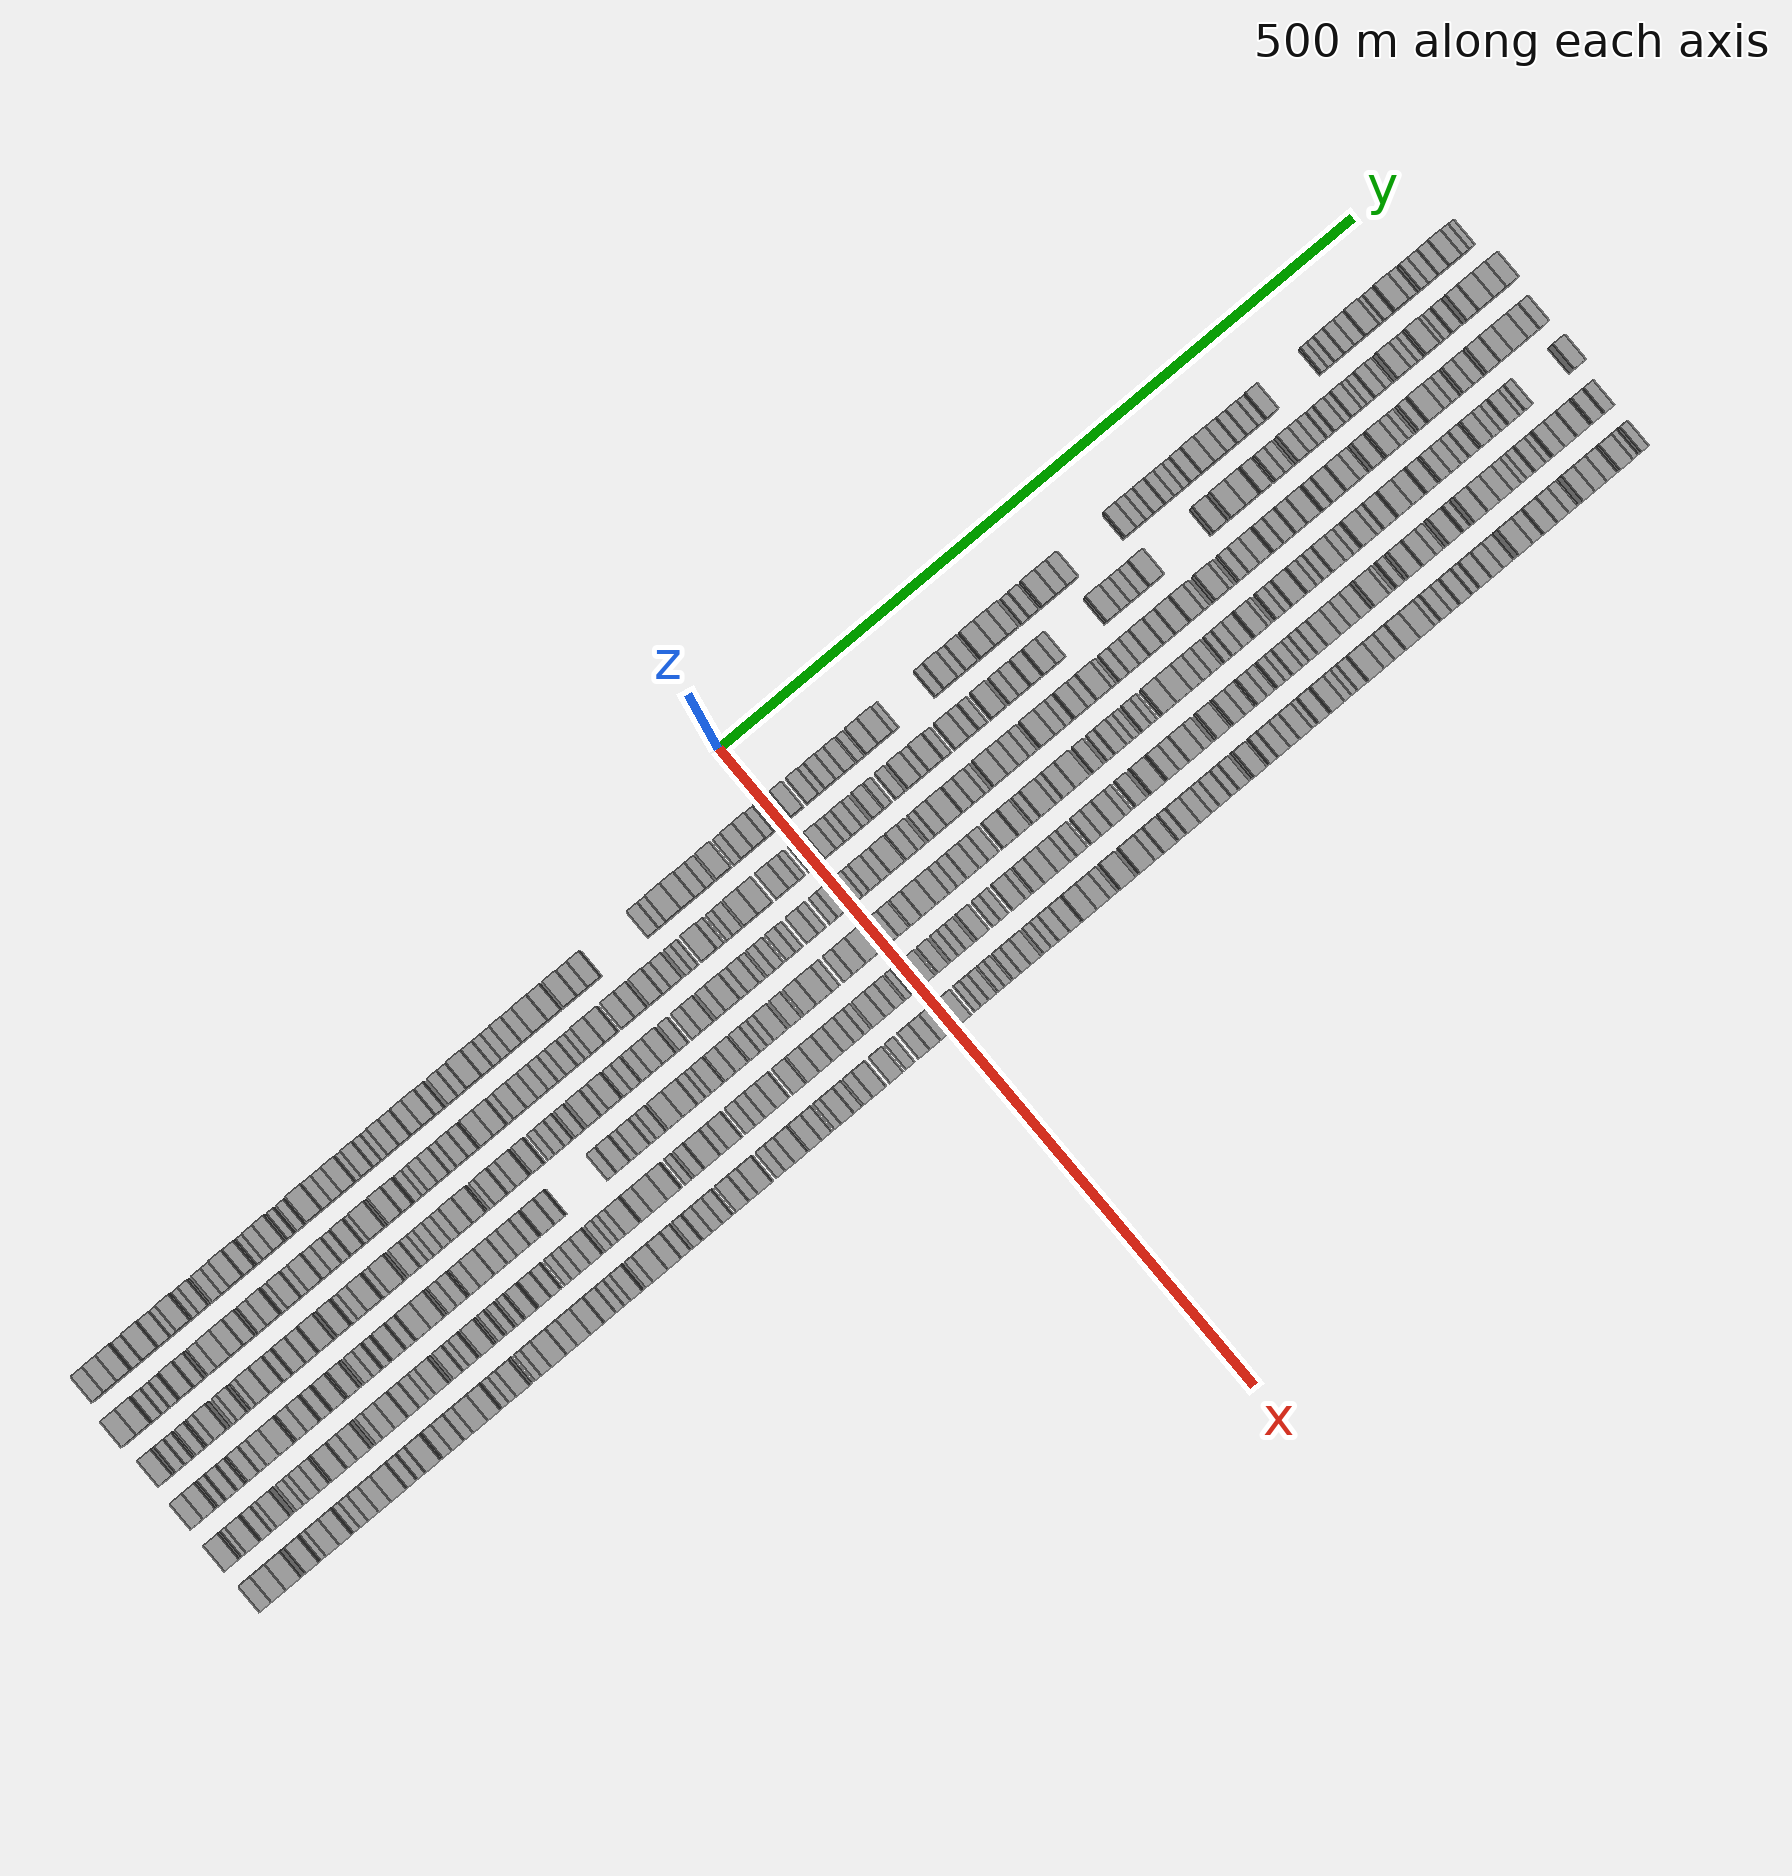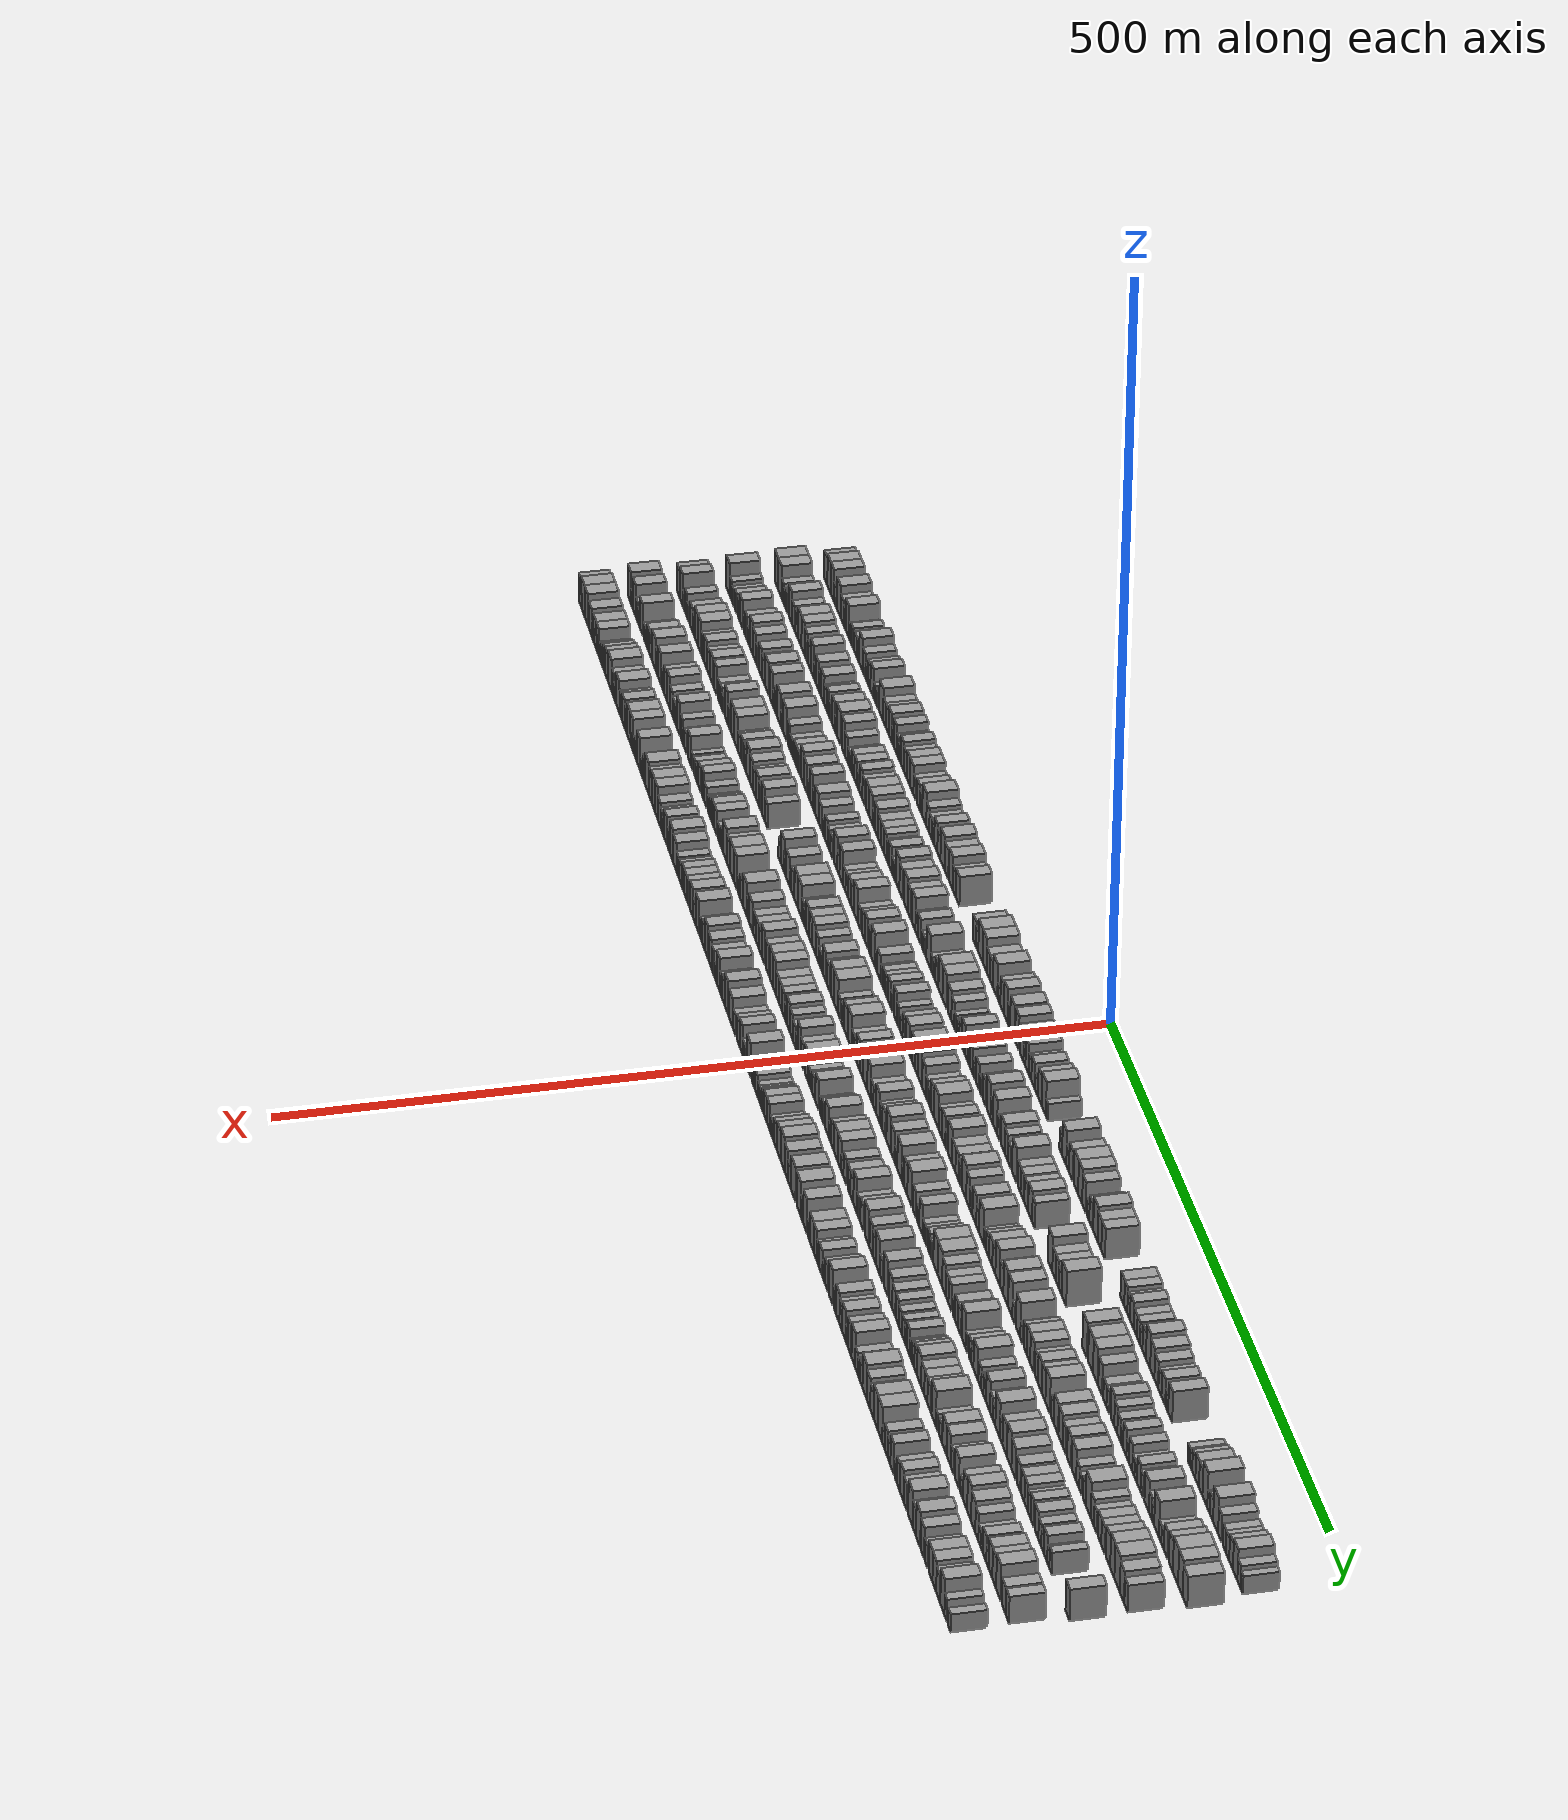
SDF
<sdf version="1.6">
 <world name="default">
  <scene>
   <sky><clouds><speed>12</speed></clouds></sky>
   <ambient>0.4 0.4 0.4 1</ambient>
   <background>0.7 0.7 0.7 1</background>
   <shadows>1</shadows>
  </scene>
  <gravity>0 0 -9.8066</gravity>
  <magnetic_field>6e-06 2.3e-05 -4.2e-05</magnetic_field>
  <physics default="0" name="default_physics" type="ode">
   <ode>
    <solver>
     <type>quick</type>
     <iters>10</iters>
     <sor>1.0</sor>
     <use_dynamic_moi_rescaling>0</use_dynamic_moi_rescaling>
    </solver>
    <constraints>
     <cfm>0</cfm>
     <erp>0.2</erp>
     <contact_max_correcting_vel>100</contact_max_correcting_vel>
     <contact_surface_layer>0.001</contact_surface_layer>
    </constraints>
   </ode>
   <max_step_size>0.004</max_step_size>
   <real_time_factor>1</real_time_factor>
   <real_time_update_rate>250</real_time_update_rate>
  </physics>
  <light name="sun" type="directional">
   <pose>0 0 10 0 0 0</pose>
   <diffuse>0.8 0.8 0.8 1</diffuse>
   <specular>0.2 0.2 0.2 1</specular>
   <attenuation>
    <range>1000</range>
    <constant>0.9</constant>
    <linear>0.01</linear>
    <quadratic>0.001</quadratic>
   </attenuation>
   <direction>-0.5 0.1 -0.9</direction>
  </light>
  <model name="building_1">
   <static>1</static>
   <pose>50.0000 -532.1588 0 0.000000 0.000000 0.000000</pose>
   <link name="link">
    <pose>0 0 10.50 0 0 0</pose>
    <collision name="collision"><geometry><box><size>20.0000 9.6824 21.0000</size></box></geometry></collision>
    <visual name="visual">
     <cast_shadows>0</cast_shadows>
     <geometry><box><size>20.0000 9.6824 21.0000</size></box></geometry>
     <material>
      <script>
       <uri>model://grey_wall/materials/scripts</uri>
       <uri>model://grey_wall/materials/textures</uri>
       <name>vrc/grey_wall</name>
      </script>
     </material>
    </visual>
   </link>
  </model>
  <model name="building_2">
   <static>1</static>
   <pose>50.0000 -522.1482 0 0.000000 0.000000 0.000000</pose>
   <link name="link">
    <pose>0 0 12.00 0 0 0</pose>
    <collision name="collision"><geometry><box><size>20.0000 10.3388 24.0000</size></box></geometry></collision>
    <visual name="visual">
     <cast_shadows>0</cast_shadows>
     <geometry><box><size>20.0000 10.3388 24.0000</size></box></geometry>
     <material>
      <script>
       <uri>model://grey_wall/materials/scripts</uri>
       <uri>model://grey_wall/materials/textures</uri>
       <name>vrc/grey_wall</name>
      </script>
     </material>
    </visual>
   </link>
  </model>
  <model name="building_3">
   <static>1</static>
   <pose>50.0000 -511.8567 0 0.000000 0.000000 0.000000</pose>
   <link name="link">
    <pose>0 0 12.00 0 0 0</pose>
    <collision name="collision"><geometry><box><size>20.0000 10.2440 24.0000</size></box></geometry></collision>
    <visual name="visual">
     <cast_shadows>0</cast_shadows>
     <geometry><box><size>20.0000 10.2440 24.0000</size></box></geometry>
     <material>
      <script>
       <uri>model://grey_wall/materials/scripts</uri>
       <uri>model://grey_wall/materials/textures</uri>
       <name>vrc/grey_wall</name>
      </script>
     </material>
    </visual>
   </link>
  </model>
  <model name="building_4">
   <static>1</static>
   <pose>50.0000 -503.0630 0 0.000000 0.000000 0.000000</pose>
   <link name="link">
    <pose>0 0 7.50 0 0 0</pose>
    <collision name="collision"><geometry><box><size>20.0000 7.3435 15.0000</size></box></geometry></collision>
    <visual name="visual">
     <cast_shadows>0</cast_shadows>
     <geometry><box><size>20.0000 7.3435 15.0000</size></box></geometry>
     <material>
      <script>
       <uri>model://grey_wall/materials/scripts</uri>
       <uri>model://grey_wall/materials/textures</uri>
       <name>vrc/grey_wall</name>
      </script>
     </material>
    </visual>
   </link>
  </model>
  <model name="building_5">
   <static>1</static>
   <pose>50.0000 -491.6230 0 0.000000 0.000000 0.000000</pose>
   <link name="link">
    <pose>0 0 12.00 0 0 0</pose>
    <collision name="collision"><geometry><box><size>20.0000 11.5364 24.0000</size></box></geometry></collision>
    <visual name="visual">
     <cast_shadows>0</cast_shadows>
     <geometry><box><size>20.0000 11.5364 24.0000</size></box></geometry>
     <material>
      <script>
       <uri>model://grey_wall/materials/scripts</uri>
       <uri>model://grey_wall/materials/textures</uri>
       <name>vrc/grey_wall</name>
      </script>
     </material>
    </visual>
   </link>
  </model>
  <model name="building_6">
   <static>1</static>
   <pose>50.0000 -481.3753 0 0.000000 0.000000 0.000000</pose>
   <link name="link">
    <pose>0 0 9.00 0 0 0</pose>
    <collision name="collision"><geometry><box><size>20.0000 8.9590 18.0000</size></box></geometry></collision>
    <visual name="visual">
     <cast_shadows>0</cast_shadows>
     <geometry><box><size>20.0000 8.9590 18.0000</size></box></geometry>
     <material>
      <script>
       <uri>model://grey_wall/materials/scripts</uri>
       <uri>model://grey_wall/materials/textures</uri>
       <name>vrc/grey_wall</name>
      </script>
     </material>
    </visual>
   </link>
  </model>
  <model name="building_7">
   <static>1</static>
   <pose>50.0000 -473.8902 0 0.000000 0.000000 0.000000</pose>
   <link name="link">
    <pose>0 0 7.50 0 0 0</pose>
    <collision name="collision"><geometry><box><size>20.0000 6.0112 15.0000</size></box></geometry></collision>
    <visual name="visual">
     <cast_shadows>0</cast_shadows>
     <geometry><box><size>20.0000 6.0112 15.0000</size></box></geometry>
     <material>
      <script>
       <uri>model://grey_wall/materials/scripts</uri>
       <uri>model://grey_wall/materials/textures</uri>
       <name>vrc/grey_wall</name>
      </script>
     </material>
    </visual>
   </link>
  </model>
  <model name="building_8">
   <static>1</static>
   <pose>50.0000 -465.6732 0 0.000000 0.000000 0.000000</pose>
   <link name="link">
    <pose>0 0 12.00 0 0 0</pose>
    <collision name="collision"><geometry><box><size>20.0000 10.4227 24.0000</size></box></geometry></collision>
    <visual name="visual">
     <cast_shadows>0</cast_shadows>
     <geometry><box><size>20.0000 10.4227 24.0000</size></box></geometry>
     <material>
      <script>
       <uri>model://grey_wall/materials/scripts</uri>
       <uri>model://grey_wall/materials/textures</uri>
       <name>vrc/grey_wall</name>
      </script>
     </material>
    </visual>
   </link>
  </model>
  <model name="building_9">
   <static>1</static>
   <pose>50.0000 -457.7671 0 0.000000 0.000000 0.000000</pose>
   <link name="link">
    <pose>0 0 6.00 0 0 0</pose>
    <collision name="collision"><geometry><box><size>20.0000 5.3895 12.0000</size></box></geometry></collision>
    <visual name="visual">
     <cast_shadows>0</cast_shadows>
     <geometry><box><size>20.0000 5.3895 12.0000</size></box></geometry>
     <material>
      <script>
       <uri>model://grey_wall/materials/scripts</uri>
       <uri>model://grey_wall/materials/textures</uri>
       <name>vrc/grey_wall</name>
      </script>
     </material>
    </visual>
   </link>
  </model>
  <model name="building_10">
   <static>1</static>
   <pose>50.0000 -451.4351 0 0.000000 0.000000 0.000000</pose>
   <link name="link">
    <pose>0 0 7.50 0 0 0</pose>
    <collision name="collision"><geometry><box><size>20.0000 7.2745 15.0000</size></box></geometry></collision>
    <visual name="visual">
     <cast_shadows>0</cast_shadows>
     <geometry><box><size>20.0000 7.2745 15.0000</size></box></geometry>
     <material>
      <script>
       <uri>model://grey_wall/materials/scripts</uri>
       <uri>model://grey_wall/materials/textures</uri>
       <name>vrc/grey_wall</name>
      </script>
     </material>
    </visual>
   </link>
  </model>
  <model name="building_11">
   <static>1</static>
   <pose>50.0000 -441.0930 0 0.000000 0.000000 0.000000</pose>
   <link name="link">
    <pose>0 0 7.50 0 0 0</pose>
    <collision name="collision"><geometry><box><size>20.0000 7.4098 15.0000</size></box></geometry></collision>
    <visual name="visual">
     <cast_shadows>0</cast_shadows>
     <geometry><box><size>20.0000 7.4098 15.0000</size></box></geometry>
     <material>
      <script>
       <uri>model://grey_wall/materials/scripts</uri>
       <uri>model://grey_wall/materials/textures</uri>
       <name>vrc/grey_wall</name>
      </script>
     </material>
    </visual>
   </link>
  </model>
  <model name="building_12">
   <static>1</static>
   <pose>50.0000 -433.6533 0 0.000000 0.000000 0.000000</pose>
   <link name="link">
    <pose>0 0 7.50 0 0 0</pose>
    <collision name="collision"><geometry><box><size>20.0000 7.4696 15.0000</size></box></geometry></collision>
    <visual name="visual">
     <cast_shadows>0</cast_shadows>
     <geometry><box><size>20.0000 7.4696 15.0000</size></box></geometry>
     <material>
      <script>
       <uri>model://grey_wall/materials/scripts</uri>
       <uri>model://grey_wall/materials/textures</uri>
       <name>vrc/grey_wall</name>
      </script>
     </material>
    </visual>
   </link>
  </model>
  <model name="building_13">
   <static>1</static>
   <pose>50.0000 -424.8476 0 0.000000 0.000000 0.000000</pose>
   <link name="link">
    <pose>0 0 12.00 0 0 0</pose>
    <collision name="collision"><geometry><box><size>20.0000 10.1417 24.0000</size></box></geometry></collision>
    <visual name="visual">
     <cast_shadows>0</cast_shadows>
     <geometry><box><size>20.0000 10.1417 24.0000</size></box></geometry>
     <material>
      <script>
       <uri>model://grey_wall/materials/scripts</uri>
       <uri>model://grey_wall/materials/textures</uri>
       <name>vrc/grey_wall</name>
      </script>
     </material>
    </visual>
   </link>
  </model>
  <model name="building_14">
   <static>1</static>
   <pose>50.0000 -415.6041 0 0.000000 0.000000 0.000000</pose>
   <link name="link">
    <pose>0 0 9.00 0 0 0</pose>
    <collision name="collision"><geometry><box><size>20.0000 8.3454 18.0000</size></box></geometry></collision>
    <visual name="visual">
     <cast_shadows>0</cast_shadows>
     <geometry><box><size>20.0000 8.3454 18.0000</size></box></geometry>
     <material>
      <script>
       <uri>model://grey_wall/materials/scripts</uri>
       <uri>model://grey_wall/materials/textures</uri>
       <name>vrc/grey_wall</name>
      </script>
     </material>
    </visual>
   </link>
  </model>
  <model name="building_15">
   <static>1</static>
   <pose>50.0000 -407.6908 0 0.000000 0.000000 0.000000</pose>
   <link name="link">
    <pose>0 0 6.00 0 0 0</pose>
    <collision name="collision"><geometry><box><size>20.0000 5.4811 12.0000</size></box></geometry></collision>
    <visual name="visual">
     <cast_shadows>0</cast_shadows>
     <geometry><box><size>20.0000 5.4811 12.0000</size></box></geometry>
     <material>
      <script>
       <uri>model://grey_wall/materials/scripts</uri>
       <uri>model://grey_wall/materials/textures</uri>
       <name>vrc/grey_wall</name>
      </script>
     </material>
    </visual>
   </link>
  </model>
  <model name="building_16">
   <static>1</static>
   <pose>50.0000 -400.7365 0 0.000000 0.000000 0.000000</pose>
   <link name="link">
    <pose>0 0 9.00 0 0 0</pose>
    <collision name="collision"><geometry><box><size>20.0000 8.4275 18.0000</size></box></geometry></collision>
    <visual name="visual">
     <cast_shadows>0</cast_shadows>
     <geometry><box><size>20.0000 8.4275 18.0000</size></box></geometry>
     <material>
      <script>
       <uri>model://grey_wall/materials/scripts</uri>
       <uri>model://grey_wall/materials/textures</uri>
       <name>vrc/grey_wall</name>
      </script>
     </material>
    </visual>
   </link>
  </model>
  <model name="building_17">
   <static>1</static>
   <pose>50.0000 -392.0549 0 0.000000 0.000000 0.000000</pose>
   <link name="link">
    <pose>0 0 10.50 0 0 0</pose>
    <collision name="collision"><geometry><box><size>20.0000 8.9357 21.0000</size></box></geometry></collision>
    <visual name="visual">
     <cast_shadows>0</cast_shadows>
     <geometry><box><size>20.0000 8.9357 21.0000</size></box></geometry>
     <material>
      <script>
       <uri>model://grey_wall/materials/scripts</uri>
       <uri>model://grey_wall/materials/textures</uri>
       <name>vrc/grey_wall</name>
      </script>
     </material>
    </visual>
   </link>
  </model>
  <model name="building_18">
   <static>1</static>
   <pose>50.0000 -383.9698 0 0.000000 0.000000 0.000000</pose>
   <link name="link">
    <pose>0 0 6.00 0 0 0</pose>
    <collision name="collision"><geometry><box><size>20.0000 5.2344 12.0000</size></box></geometry></collision>
    <visual name="visual">
     <cast_shadows>0</cast_shadows>
     <geometry><box><size>20.0000 5.2344 12.0000</size></box></geometry>
     <material>
      <script>
       <uri>model://grey_wall/materials/scripts</uri>
       <uri>model://grey_wall/materials/textures</uri>
       <name>vrc/grey_wall</name>
      </script>
     </material>
    </visual>
   </link>
  </model>
  <model name="building_19">
   <static>1</static>
   <pose>50.0000 -376.3699 0 0.000000 0.000000 0.000000</pose>
   <link name="link">
    <pose>0 0 6.00 0 0 0</pose>
    <collision name="collision"><geometry><box><size>20.0000 5.9654 12.0000</size></box></geometry></collision>
    <visual name="visual">
     <cast_shadows>0</cast_shadows>
     <geometry><box><size>20.0000 5.9654 12.0000</size></box></geometry>
     <material>
      <script>
       <uri>model://grey_wall/materials/scripts</uri>
       <uri>model://grey_wall/materials/textures</uri>
       <name>vrc/grey_wall</name>
      </script>
     </material>
    </visual>
   </link>
  </model>
  <model name="building_20">
   <static>1</static>
   <pose>50.0000 -364.4836 0 0.000000 0.000000 0.000000</pose>
   <link name="link">
    <pose>0 0 12.00 0 0 0</pose>
    <collision name="collision"><geometry><box><size>20.0000 11.8072 24.0000</size></box></geometry></collision>
    <visual name="visual">
     <cast_shadows>0</cast_shadows>
     <geometry><box><size>20.0000 11.8072 24.0000</size></box></geometry>
     <material>
      <script>
       <uri>model://grey_wall/materials/scripts</uri>
       <uri>model://grey_wall/materials/textures</uri>
       <name>vrc/grey_wall</name>
      </script>
     </material>
    </visual>
   </link>
  </model>
  <model name="building_21">
   <static>1</static>
   <pose>50.0000 -354.9082 0 0.000000 0.000000 0.000000</pose>
   <link name="link">
    <pose>0 0 9.00 0 0 0</pose>
    <collision name="collision"><geometry><box><size>20.0000 7.3438 18.0000</size></box></geometry></collision>
    <visual name="visual">
     <cast_shadows>0</cast_shadows>
     <geometry><box><size>20.0000 7.3438 18.0000</size></box></geometry>
     <material>
      <script>
       <uri>model://grey_wall/materials/scripts</uri>
       <uri>model://grey_wall/materials/textures</uri>
       <name>vrc/grey_wall</name>
      </script>
     </material>
    </visual>
   </link>
  </model>
  <model name="building_22">
   <static>1</static>
   <pose>50.0000 -347.1120 0 0.000000 0.000000 0.000000</pose>
   <link name="link">
    <pose>0 0 9.00 0 0 0</pose>
    <collision name="collision"><geometry><box><size>20.0000 8.2485 18.0000</size></box></geometry></collision>
    <visual name="visual">
     <cast_shadows>0</cast_shadows>
     <geometry><box><size>20.0000 8.2485 18.0000</size></box></geometry>
     <material>
      <script>
       <uri>model://grey_wall/materials/scripts</uri>
       <uri>model://grey_wall/materials/textures</uri>
       <name>vrc/grey_wall</name>
      </script>
     </material>
    </visual>
   </link>
  </model>
  <model name="building_23">
   <static>1</static>
   <pose>50.0000 -338.0205 0 0.000000 0.000000 0.000000</pose>
   <link name="link">
    <pose>0 0 10.50 0 0 0</pose>
    <collision name="collision"><geometry><box><size>20.0000 9.9346 21.0000</size></box></geometry></collision>
    <visual name="visual">
     <cast_shadows>0</cast_shadows>
     <geometry><box><size>20.0000 9.9346 21.0000</size></box></geometry>
     <material>
      <script>
       <uri>model://grey_wall/materials/scripts</uri>
       <uri>model://grey_wall/materials/textures</uri>
       <name>vrc/grey_wall</name>
      </script>
     </material>
    </visual>
   </link>
  </model>
  <model name="building_24">
   <static>1</static>
   <pose>50.0000 -330.4916 0 0.000000 0.000000 0.000000</pose>
   <link name="link">
    <pose>0 0 6.00 0 0 0</pose>
    <collision name="collision"><geometry><box><size>20.0000 5.1233 12.0000</size></box></geometry></collision>
    <visual name="visual">
     <cast_shadows>0</cast_shadows>
     <geometry><box><size>20.0000 5.1233 12.0000</size></box></geometry>
     <material>
      <script>
       <uri>model://grey_wall/materials/scripts</uri>
       <uri>model://grey_wall/materials/textures</uri>
       <name>vrc/grey_wall</name>
      </script>
     </material>
    </visual>
   </link>
  </model>
  <model name="building_25">
   <static>1</static>
   <pose>50.0000 -323.5865 0 0.000000 0.000000 0.000000</pose>
   <link name="link">
    <pose>0 0 10.50 0 0 0</pose>
    <collision name="collision"><geometry><box><size>20.0000 8.6868 21.0000</size></box></geometry></collision>
    <visual name="visual">
     <cast_shadows>0</cast_shadows>
     <geometry><box><size>20.0000 8.6868 21.0000</size></box></geometry>
     <material>
      <script>
       <uri>model://grey_wall/materials/scripts</uri>
       <uri>model://grey_wall/materials/textures</uri>
       <name>vrc/grey_wall</name>
      </script>
     </material>
    </visual>
   </link>
  </model>
  <model name="building_26">
   <static>1</static>
   <pose>50.0000 -316.2182 0 0.000000 0.000000 0.000000</pose>
   <link name="link">
    <pose>0 0 7.50 0 0 0</pose>
    <collision name="collision"><geometry><box><size>20.0000 6.0497 15.0000</size></box></geometry></collision>
    <visual name="visual">
     <cast_shadows>0</cast_shadows>
     <geometry><box><size>20.0000 6.0497 15.0000</size></box></geometry>
     <material>
      <script>
       <uri>model://grey_wall/materials/scripts</uri>
       <uri>model://grey_wall/materials/textures</uri>
       <name>vrc/grey_wall</name>
      </script>
     </material>
    </visual>
   </link>
  </model>
  <model name="building_27">
   <static>1</static>
   <pose>50.0000 -310.4035 0 0.000000 0.000000 0.000000</pose>
   <link name="link">
    <pose>0 0 6.00 0 0 0</pose>
    <collision name="collision"><geometry><box><size>20.0000 5.5798 12.0000</size></box></geometry></collision>
    <visual name="visual">
     <cast_shadows>0</cast_shadows>
     <geometry><box><size>20.0000 5.5798 12.0000</size></box></geometry>
     <material>
      <script>
       <uri>model://grey_wall/materials/scripts</uri>
       <uri>model://grey_wall/materials/textures</uri>
       <name>vrc/grey_wall</name>
      </script>
     </material>
    </visual>
   </link>
  </model>
  <model name="building_28">
   <static>1</static>
   <pose>50.0000 -303.2164 0 0.000000 0.000000 0.000000</pose>
   <link name="link">
    <pose>0 0 10.50 0 0 0</pose>
    <collision name="collision"><geometry><box><size>20.0000 8.7944 21.0000</size></box></geometry></collision>
    <visual name="visual">
     <cast_shadows>0</cast_shadows>
     <geometry><box><size>20.0000 8.7944 21.0000</size></box></geometry>
     <material>
      <script>
       <uri>model://grey_wall/materials/scripts</uri>
       <uri>model://grey_wall/materials/textures</uri>
       <name>vrc/grey_wall</name>
      </script>
     </material>
    </visual>
   </link>
  </model>
  <model name="building_29">
   <static>1</static>
   <pose>50.0000 -294.5432 0 0.000000 0.000000 0.000000</pose>
   <link name="link">
    <pose>0 0 9.00 0 0 0</pose>
    <collision name="collision"><geometry><box><size>20.0000 8.5519 18.0000</size></box></geometry></collision>
    <visual name="visual">
     <cast_shadows>0</cast_shadows>
     <geometry><box><size>20.0000 8.5519 18.0000</size></box></geometry>
     <material>
      <script>
       <uri>model://grey_wall/materials/scripts</uri>
       <uri>model://grey_wall/materials/textures</uri>
       <name>vrc/grey_wall</name>
      </script>
     </material>
    </visual>
   </link>
  </model>
  <model name="building_30">
   <static>1</static>
   <pose>50.0000 -285.0422 0 0.000000 0.000000 0.000000</pose>
   <link name="link">
    <pose>0 0 10.50 0 0 0</pose>
    <collision name="collision"><geometry><box><size>20.0000 8.4502 21.0000</size></box></geometry></collision>
    <visual name="visual">
     <cast_shadows>0</cast_shadows>
     <geometry><box><size>20.0000 8.4502 21.0000</size></box></geometry>
     <material>
      <script>
       <uri>model://grey_wall/materials/scripts</uri>
       <uri>model://grey_wall/materials/textures</uri>
       <name>vrc/grey_wall</name>
      </script>
     </material>
    </visual>
   </link>
  </model>
  <model name="building_31">
   <static>1</static>
   <pose>50.0000 -275.9115 0 0.000000 0.000000 0.000000</pose>
   <link name="link">
    <pose>0 0 10.50 0 0 0</pose>
    <collision name="collision"><geometry><box><size>20.0000 9.8110 21.0000</size></box></geometry></collision>
    <visual name="visual">
     <cast_shadows>0</cast_shadows>
     <geometry><box><size>20.0000 9.8110 21.0000</size></box></geometry>
     <material>
      <script>
       <uri>model://grey_wall/materials/scripts</uri>
       <uri>model://grey_wall/materials/textures</uri>
       <name>vrc/grey_wall</name>
      </script>
     </material>
    </visual>
   </link>
  </model>
  <model name="building_32">
   <static>1</static>
   <pose>50.0000 -267.6330 0 0.000000 0.000000 0.000000</pose>
   <link name="link">
    <pose>0 0 7.50 0 0 0</pose>
    <collision name="collision"><geometry><box><size>20.0000 6.7461 15.0000</size></box></geometry></collision>
    <visual name="visual">
     <cast_shadows>0</cast_shadows>
     <geometry><box><size>20.0000 6.7461 15.0000</size></box></geometry>
     <material>
      <script>
       <uri>model://grey_wall/materials/scripts</uri>
       <uri>model://grey_wall/materials/textures</uri>
       <name>vrc/grey_wall</name>
      </script>
     </material>
    </visual>
   </link>
  </model>
  <model name="building_33">
   <static>1</static>
   <pose>50.0000 -257.3962 0 0.000000 0.000000 0.000000</pose>
   <link name="link">
    <pose>0 0 9.00 0 0 0</pose>
    <collision name="collision"><geometry><box><size>20.0000 7.7275 18.0000</size></box></geometry></collision>
    <visual name="visual">
     <cast_shadows>0</cast_shadows>
     <geometry><box><size>20.0000 7.7275 18.0000</size></box></geometry>
     <material>
      <script>
       <uri>model://grey_wall/materials/scripts</uri>
       <uri>model://grey_wall/materials/textures</uri>
       <name>vrc/grey_wall</name>
      </script>
     </material>
    </visual>
   </link>
  </model>
  <model name="building_34">
   <static>1</static>
   <pose>50.0000 -250.1810 0 0.000000 0.000000 0.000000</pose>
   <link name="link">
    <pose>0 0 7.50 0 0 0</pose>
    <collision name="collision"><geometry><box><size>20.0000 6.7030 15.0000</size></box></geometry></collision>
    <visual name="visual">
     <cast_shadows>0</cast_shadows>
     <geometry><box><size>20.0000 6.7030 15.0000</size></box></geometry>
     <material>
      <script>
       <uri>model://grey_wall/materials/scripts</uri>
       <uri>model://grey_wall/materials/textures</uri>
       <name>vrc/grey_wall</name>
      </script>
     </material>
    </visual>
   </link>
  </model>
  <model name="building_35">
   <static>1</static>
   <pose>50.0000 -240.1121 0 0.000000 0.000000 0.000000</pose>
   <link name="link">
    <pose>0 0 12.00 0 0 0</pose>
    <collision name="collision"><geometry><box><size>20.0000 11.4347 24.0000</size></box></geometry></collision>
    <visual name="visual">
     <cast_shadows>0</cast_shadows>
     <geometry><box><size>20.0000 11.4347 24.0000</size></box></geometry>
     <material>
      <script>
       <uri>model://grey_wall/materials/scripts</uri>
       <uri>model://grey_wall/materials/textures</uri>
       <name>vrc/grey_wall</name>
      </script>
     </material>
    </visual>
   </link>
  </model>
  <model name="building_36">
   <static>1</static>
   <pose>50.0000 -230.1921 0 0.000000 0.000000 0.000000</pose>
   <link name="link">
    <pose>0 0 9.00 0 0 0</pose>
    <collision name="collision"><geometry><box><size>20.0000 8.4054 18.0000</size></box></geometry></collision>
    <visual name="visual">
     <cast_shadows>0</cast_shadows>
     <geometry><box><size>20.0000 8.4054 18.0000</size></box></geometry>
     <material>
      <script>
       <uri>model://grey_wall/materials/scripts</uri>
       <uri>model://grey_wall/materials/textures</uri>
       <name>vrc/grey_wall</name>
      </script>
     </material>
    </visual>
   </link>
  </model>
  <model name="building_37">
   <static>1</static>
   <pose>50.0000 -222.7705 0 0.000000 0.000000 0.000000</pose>
   <link name="link">
    <pose>0 0 7.50 0 0 0</pose>
    <collision name="collision"><geometry><box><size>20.0000 6.4377 15.0000</size></box></geometry></collision>
    <visual name="visual">
     <cast_shadows>0</cast_shadows>
     <geometry><box><size>20.0000 6.4377 15.0000</size></box></geometry>
     <material>
      <script>
       <uri>model://grey_wall/materials/scripts</uri>
       <uri>model://grey_wall/materials/textures</uri>
       <name>vrc/grey_wall</name>
      </script>
     </material>
    </visual>
   </link>
  </model>
  <model name="building_38">
   <static>1</static>
   <pose>50.0000 -215.8439 0 0.000000 0.000000 0.000000</pose>
   <link name="link">
    <pose>0 0 7.50 0 0 0</pose>
    <collision name="collision"><geometry><box><size>20.0000 7.4155 15.0000</size></box></geometry></collision>
    <visual name="visual">
     <cast_shadows>0</cast_shadows>
     <geometry><box><size>20.0000 7.4155 15.0000</size></box></geometry>
     <material>
      <script>
       <uri>model://grey_wall/materials/scripts</uri>
       <uri>model://grey_wall/materials/textures</uri>
       <name>vrc/grey_wall</name>
      </script>
     </material>
    </visual>
   </link>
  </model>
  <model name="building_39">
   <static>1</static>
   <pose>50.0000 -207.7490 0 0.000000 0.000000 0.000000</pose>
   <link name="link">
    <pose>0 0 10.50 0 0 0</pose>
    <collision name="collision"><geometry><box><size>20.0000 8.7743 21.0000</size></box></geometry></collision>
    <visual name="visual">
     <cast_shadows>0</cast_shadows>
     <geometry><box><size>20.0000 8.7743 21.0000</size></box></geometry>
     <material>
      <script>
       <uri>model://grey_wall/materials/scripts</uri>
       <uri>model://grey_wall/materials/textures</uri>
       <name>vrc/grey_wall</name>
      </script>
     </material>
    </visual>
   </link>
  </model>
  <model name="building_40">
   <static>1</static>
   <pose>50.0000 -199.0678 0 0.000000 0.000000 0.000000</pose>
   <link name="link">
    <pose>0 0 9.00 0 0 0</pose>
    <collision name="collision"><geometry><box><size>20.0000 8.5880 18.0000</size></box></geometry></collision>
    <visual name="visual">
     <cast_shadows>0</cast_shadows>
     <geometry><box><size>20.0000 8.5880 18.0000</size></box></geometry>
     <material>
      <script>
       <uri>model://grey_wall/materials/scripts</uri>
       <uri>model://grey_wall/materials/textures</uri>
       <name>vrc/grey_wall</name>
      </script>
     </material>
    </visual>
   </link>
  </model>
  <model name="building_41">
   <static>1</static>
   <pose>50.0000 -188.8632 0 0.000000 0.000000 0.000000</pose>
   <link name="link">
    <pose>0 0 12.00 0 0 0</pose>
    <collision name="collision"><geometry><box><size>20.0000 11.8213 24.0000</size></box></geometry></collision>
    <visual name="visual">
     <cast_shadows>0</cast_shadows>
     <geometry><box><size>20.0000 11.8213 24.0000</size></box></geometry>
     <material>
      <script>
       <uri>model://grey_wall/materials/scripts</uri>
       <uri>model://grey_wall/materials/textures</uri>
       <name>vrc/grey_wall</name>
      </script>
     </material>
    </visual>
   </link>
  </model>
  <model name="building_42">
   <static>1</static>
   <pose>50.0000 -177.9492 0 0.000000 0.000000 0.000000</pose>
   <link name="link">
    <pose>0 0 10.50 0 0 0</pose>
    <collision name="collision"><geometry><box><size>20.0000 10.0065 21.0000</size></box></geometry></collision>
    <visual name="visual">
     <cast_shadows>0</cast_shadows>
     <geometry><box><size>20.0000 10.0065 21.0000</size></box></geometry>
     <material>
      <script>
       <uri>model://grey_wall/materials/scripts</uri>
       <uri>model://grey_wall/materials/textures</uri>
       <name>vrc/grey_wall</name>
      </script>
     </material>
    </visual>
   </link>
  </model>
  <model name="building_43">
   <static>1</static>
   <pose>50.0000 -165.6453 0 0.000000 0.000000 0.000000</pose>
   <link name="link">
    <pose>0 0 12.00 0 0 0</pose>
    <collision name="collision"><geometry><box><size>20.0000 10.6014 24.0000</size></box></geometry></collision>
    <visual name="visual">
     <cast_shadows>0</cast_shadows>
     <geometry><box><size>20.0000 10.6014 24.0000</size></box></geometry>
     <material>
      <script>
       <uri>model://grey_wall/materials/scripts</uri>
       <uri>model://grey_wall/materials/textures</uri>
       <name>vrc/grey_wall</name>
      </script>
     </material>
    </visual>
   </link>
  </model>
  <model name="building_44">
   <static>1</static>
   <pose>50.0000 -156.2103 0 0.000000 0.000000 0.000000</pose>
   <link name="link">
    <pose>0 0 9.00 0 0 0</pose>
    <collision name="collision"><geometry><box><size>20.0000 8.2686 18.0000</size></box></geometry></collision>
    <visual name="visual">
     <cast_shadows>0</cast_shadows>
     <geometry><box><size>20.0000 8.2686 18.0000</size></box></geometry>
     <material>
      <script>
       <uri>model://grey_wall/materials/scripts</uri>
       <uri>model://grey_wall/materials/textures</uri>
       <name>vrc/grey_wall</name>
      </script>
     </material>
    </visual>
   </link>
  </model>
  <model name="building_45">
   <static>1</static>
   <pose>50.0000 -147.1353 0 0.000000 0.000000 0.000000</pose>
   <link name="link">
    <pose>0 0 10.50 0 0 0</pose>
    <collision name="collision"><geometry><box><size>20.0000 9.8815 21.0000</size></box></geometry></collision>
    <visual name="visual">
     <cast_shadows>0</cast_shadows>
     <geometry><box><size>20.0000 9.8815 21.0000</size></box></geometry>
     <material>
      <script>
       <uri>model://grey_wall/materials/scripts</uri>
       <uri>model://grey_wall/materials/textures</uri>
       <name>vrc/grey_wall</name>
      </script>
     </material>
    </visual>
   </link>
  </model>
  <model name="building_46">
   <static>1</static>
   <pose>50.0000 -101.3251 0 0.000000 0.000000 0.000000</pose>
   <link name="link">
    <pose>0 0 9.00 0 0 0</pose>
    <collision name="collision"><geometry><box><size>20.0000 8.5796 18.0000</size></box></geometry></collision>
    <visual name="visual">
     <cast_shadows>0</cast_shadows>
     <geometry><box><size>20.0000 8.5796 18.0000</size></box></geometry>
     <material>
      <script>
       <uri>model://grey_wall/materials/scripts</uri>
       <uri>model://grey_wall/materials/textures</uri>
       <name>vrc/grey_wall</name>
      </script>
     </material>
    </visual>
   </link>
  </model>
  <model name="building_47">
   <static>1</static>
   <pose>50.0000 -94.0103 0 0.000000 0.000000 0.000000</pose>
   <link name="link">
    <pose>0 0 7.50 0 0 0</pose>
    <collision name="collision"><geometry><box><size>20.0000 6.0500 15.0000</size></box></geometry></collision>
    <visual name="visual">
     <cast_shadows>0</cast_shadows>
     <geometry><box><size>20.0000 6.0500 15.0000</size></box></geometry>
     <material>
      <script>
       <uri>model://grey_wall/materials/scripts</uri>
       <uri>model://grey_wall/materials/textures</uri>
       <name>vrc/grey_wall</name>
      </script>
     </material>
    </visual>
   </link>
  </model>
  <model name="building_48">
   <static>1</static>
   <pose>50.0000 -85.0996 0 0.000000 0.000000 0.000000</pose>
   <link name="link">
    <pose>0 0 12.00 0 0 0</pose>
    <collision name="collision"><geometry><box><size>20.0000 11.7714 24.0000</size></box></geometry></collision>
    <visual name="visual">
     <cast_shadows>0</cast_shadows>
     <geometry><box><size>20.0000 11.7714 24.0000</size></box></geometry>
     <material>
      <script>
       <uri>model://grey_wall/materials/scripts</uri>
       <uri>model://grey_wall/materials/textures</uri>
       <name>vrc/grey_wall</name>
      </script>
     </material>
    </visual>
   </link>
  </model>
  <model name="building_49">
   <static>1</static>
   <pose>50.0000 -73.9607 0 0.000000 0.000000 0.000000</pose>
   <link name="link">
    <pose>0 0 12.00 0 0 0</pose>
    <collision name="collision"><geometry><box><size>20.0000 10.5065 24.0000</size></box></geometry></collision>
    <visual name="visual">
     <cast_shadows>0</cast_shadows>
     <geometry><box><size>20.0000 10.5065 24.0000</size></box></geometry>
     <material>
      <script>
       <uri>model://grey_wall/materials/scripts</uri>
       <uri>model://grey_wall/materials/textures</uri>
       <name>vrc/grey_wall</name>
      </script>
     </material>
    </visual>
   </link>
  </model>
  <model name="building_50">
   <static>1</static>
   <pose>50.0000 -64.4210 0 0.000000 0.000000 0.000000</pose>
   <link name="link">
    <pose>0 0 9.00 0 0 0</pose>
    <collision name="collision"><geometry><box><size>20.0000 8.5731 18.0000</size></box></geometry></collision>
    <visual name="visual">
     <cast_shadows>0</cast_shadows>
     <geometry><box><size>20.0000 8.5731 18.0000</size></box></geometry>
     <material>
      <script>
       <uri>model://grey_wall/materials/scripts</uri>
       <uri>model://grey_wall/materials/textures</uri>
       <name>vrc/grey_wall</name>
      </script>
     </material>
    </visual>
   </link>
  </model>
  <model name="building_51">
   <static>1</static>
   <pose>50.0000 -56.5271 0 0.000000 0.000000 0.000000</pose>
   <link name="link">
    <pose>0 0 9.00 0 0 0</pose>
    <collision name="collision"><geometry><box><size>20.0000 7.2146 18.0000</size></box></geometry></collision>
    <visual name="visual">
     <cast_shadows>0</cast_shadows>
     <geometry><box><size>20.0000 7.2146 18.0000</size></box></geometry>
     <material>
      <script>
       <uri>model://grey_wall/materials/scripts</uri>
       <uri>model://grey_wall/materials/textures</uri>
       <name>vrc/grey_wall</name>
      </script>
     </material>
    </visual>
   </link>
  </model>
  <model name="building_52">
   <static>1</static>
   <pose>50.0000 -46.1975 0 0.000000 0.000000 0.000000</pose>
   <link name="link">
    <pose>0 0 12.00 0 0 0</pose>
    <collision name="collision"><geometry><box><size>20.0000 11.4446 24.0000</size></box></geometry></collision>
    <visual name="visual">
     <cast_shadows>0</cast_shadows>
     <geometry><box><size>20.0000 11.4446 24.0000</size></box></geometry>
     <material>
      <script>
       <uri>model://grey_wall/materials/scripts</uri>
       <uri>model://grey_wall/materials/textures</uri>
       <name>vrc/grey_wall</name>
      </script>
     </material>
    </visual>
   </link>
  </model>
  <model name="building_53">
   <static>1</static>
   <pose>50.0000 -35.4818 0 0.000000 0.000000 0.000000</pose>
   <link name="link">
    <pose>0 0 6.00 0 0 0</pose>
    <collision name="collision"><geometry><box><size>20.0000 5.9866 12.0000</size></box></geometry></collision>
    <visual name="visual">
     <cast_shadows>0</cast_shadows>
     <geometry><box><size>20.0000 5.9866 12.0000</size></box></geometry>
     <material>
      <script>
       <uri>model://grey_wall/materials/scripts</uri>
       <uri>model://grey_wall/materials/textures</uri>
       <name>vrc/grey_wall</name>
      </script>
     </material>
    </visual>
   </link>
  </model>
  <model name="building_54">
   <static>1</static>
   <pose>50.0000 -27.7684 0 0.000000 0.000000 0.000000</pose>
   <link name="link">
    <pose>0 0 10.50 0 0 0</pose>
    <collision name="collision"><geometry><box><size>20.0000 9.4403 21.0000</size></box></geometry></collision>
    <visual name="visual">
     <cast_shadows>0</cast_shadows>
     <geometry><box><size>20.0000 9.4403 21.0000</size></box></geometry>
     <material>
      <script>
       <uri>model://grey_wall/materials/scripts</uri>
       <uri>model://grey_wall/materials/textures</uri>
       <name>vrc/grey_wall</name>
      </script>
     </material>
    </visual>
   </link>
  </model>
  <model name="building_55">
   <static>1</static>
   <pose>50.0000 -18.2410 0 0.000000 0.000000 0.000000</pose>
   <link name="link">
    <pose>0 0 12.00 0 0 0</pose>
    <collision name="collision"><geometry><box><size>20.0000 9.6144 24.0000</size></box></geometry></collision>
    <visual name="visual">
     <cast_shadows>0</cast_shadows>
     <geometry><box><size>20.0000 9.6144 24.0000</size></box></geometry>
     <material>
      <script>
       <uri>model://grey_wall/materials/scripts</uri>
       <uri>model://grey_wall/materials/textures</uri>
       <name>vrc/grey_wall</name>
      </script>
     </material>
    </visual>
   </link>
  </model>
  <model name="building_56">
   <static>1</static>
   <pose>50.0000 -10.2349 0 0.000000 0.000000 0.000000</pose>
   <link name="link">
    <pose>0 0 7.50 0 0 0</pose>
    <collision name="collision"><geometry><box><size>20.0000 6.3978 15.0000</size></box></geometry></collision>
    <visual name="visual">
     <cast_shadows>0</cast_shadows>
     <geometry><box><size>20.0000 6.3978 15.0000</size></box></geometry>
     <material>
      <script>
       <uri>model://grey_wall/materials/scripts</uri>
       <uri>model://grey_wall/materials/textures</uri>
       <name>vrc/grey_wall</name>
      </script>
     </material>
    </visual>
   </link>
  </model>
  <model name="building_57">
   <static>1</static>
   <pose>50.0000 -1.4303 0 0.000000 0.000000 0.000000</pose>
   <link name="link">
    <pose>0 0 12.00 0 0 0</pose>
    <collision name="collision"><geometry><box><size>20.0000 11.2115 24.0000</size></box></geometry></collision>
    <visual name="visual">
     <cast_shadows>0</cast_shadows>
     <geometry><box><size>20.0000 11.2115 24.0000</size></box></geometry>
     <material>
      <script>
       <uri>model://grey_wall/materials/scripts</uri>
       <uri>model://grey_wall/materials/textures</uri>
       <name>vrc/grey_wall</name>
      </script>
     </material>
    </visual>
   </link>
  </model>
  <model name="building_58">
   <static>1</static>
   <pose>50.0000 10.9994 0 0.000000 0.000000 0.000000</pose>
   <link name="link">
    <pose>0 0 12.00 0 0 0</pose>
    <collision name="collision"><geometry><box><size>20.0000 9.6478 24.0000</size></box></geometry></collision>
    <visual name="visual">
     <cast_shadows>0</cast_shadows>
     <geometry><box><size>20.0000 9.6478 24.0000</size></box></geometry>
     <material>
      <script>
       <uri>model://grey_wall/materials/scripts</uri>
       <uri>model://grey_wall/materials/textures</uri>
       <name>vrc/grey_wall</name>
      </script>
     </material>
    </visual>
   </link>
  </model>
  <model name="building_59">
   <static>1</static>
   <pose>50.0000 23.3561 0 0.000000 0.000000 0.000000</pose>
   <link name="link">
    <pose>0 0 10.50 0 0 0</pose>
    <collision name="collision"><geometry><box><size>20.0000 9.0657 21.0000</size></box></geometry></collision>
    <visual name="visual">
     <cast_shadows>0</cast_shadows>
     <geometry><box><size>20.0000 9.0657 21.0000</size></box></geometry>
     <material>
      <script>
       <uri>model://grey_wall/materials/scripts</uri>
       <uri>model://grey_wall/materials/textures</uri>
       <name>vrc/grey_wall</name>
      </script>
     </material>
    </visual>
   </link>
  </model>
  <model name="building_60">
   <static>1</static>
   <pose>50.0000 30.4040 0 0.000000 0.000000 0.000000</pose>
   <link name="link">
    <pose>0 0 6.00 0 0 0</pose>
    <collision name="collision"><geometry><box><size>20.0000 5.0299 12.0000</size></box></geometry></collision>
    <visual name="visual">
     <cast_shadows>0</cast_shadows>
     <geometry><box><size>20.0000 5.0299 12.0000</size></box></geometry>
     <material>
      <script>
       <uri>model://grey_wall/materials/scripts</uri>
       <uri>model://grey_wall/materials/textures</uri>
       <name>vrc/grey_wall</name>
      </script>
     </material>
    </visual>
   </link>
  </model>
  <model name="building_61">
   <static>1</static>
   <pose>50.0000 37.1323 0 0.000000 0.000000 0.000000</pose>
   <link name="link">
    <pose>0 0 10.50 0 0 0</pose>
    <collision name="collision"><geometry><box><size>20.0000 8.4268 21.0000</size></box></geometry></collision>
    <visual name="visual">
     <cast_shadows>0</cast_shadows>
     <geometry><box><size>20.0000 8.4268 21.0000</size></box></geometry>
     <material>
      <script>
       <uri>model://grey_wall/materials/scripts</uri>
       <uri>model://grey_wall/materials/textures</uri>
       <name>vrc/grey_wall</name>
      </script>
     </material>
    </visual>
   </link>
  </model>
  <model name="building_62">
   <static>1</static>
   <pose>50.0000 44.7533 0 0.000000 0.000000 0.000000</pose>
   <link name="link">
    <pose>0 0 7.50 0 0 0</pose>
    <collision name="collision"><geometry><box><size>20.0000 6.8150 15.0000</size></box></geometry></collision>
    <visual name="visual">
     <cast_shadows>0</cast_shadows>
     <geometry><box><size>20.0000 6.8150 15.0000</size></box></geometry>
     <material>
      <script>
       <uri>model://grey_wall/materials/scripts</uri>
       <uri>model://grey_wall/materials/textures</uri>
       <name>vrc/grey_wall</name>
      </script>
     </material>
    </visual>
   </link>
  </model>
  <model name="building_63">
   <static>1</static>
   <pose>50.0000 52.6108 0 0.000000 0.000000 0.000000</pose>
   <link name="link">
    <pose>0 0 9.00 0 0 0</pose>
    <collision name="collision"><geometry><box><size>20.0000 8.9001 18.0000</size></box></geometry></collision>
    <visual name="visual">
     <cast_shadows>0</cast_shadows>
     <geometry><box><size>20.0000 8.9001 18.0000</size></box></geometry>
     <material>
      <script>
       <uri>model://grey_wall/materials/scripts</uri>
       <uri>model://grey_wall/materials/textures</uri>
       <name>vrc/grey_wall</name>
      </script>
     </material>
    </visual>
   </link>
  </model>
  <model name="building_64">
   <static>1</static>
   <pose>50.0000 61.0438 0 0.000000 0.000000 0.000000</pose>
   <link name="link">
    <pose>0 0 6.00 0 0 0</pose>
    <collision name="collision"><geometry><box><size>20.0000 5.9659 12.0000</size></box></geometry></collision>
    <visual name="visual">
     <cast_shadows>0</cast_shadows>
     <geometry><box><size>20.0000 5.9659 12.0000</size></box></geometry>
     <material>
      <script>
       <uri>model://grey_wall/materials/scripts</uri>
       <uri>model://grey_wall/materials/textures</uri>
       <name>vrc/grey_wall</name>
      </script>
     </material>
    </visual>
   </link>
  </model>
  <model name="building_65">
   <static>1</static>
   <pose>50.0000 69.6880 0 0.000000 0.000000 0.000000</pose>
   <link name="link">
    <pose>0 0 10.50 0 0 0</pose>
    <collision name="collision"><geometry><box><size>20.0000 9.3225 21.0000</size></box></geometry></collision>
    <visual name="visual">
     <cast_shadows>0</cast_shadows>
     <geometry><box><size>20.0000 9.3225 21.0000</size></box></geometry>
     <material>
      <script>
       <uri>model://grey_wall/materials/scripts</uri>
       <uri>model://grey_wall/materials/textures</uri>
       <name>vrc/grey_wall</name>
      </script>
     </material>
    </visual>
   </link>
  </model>
  <model name="building_66">
   <static>1</static>
   <pose>50.0000 79.8039 0 0.000000 0.000000 0.000000</pose>
   <link name="link">
    <pose>0 0 12.00 0 0 0</pose>
    <collision name="collision"><geometry><box><size>20.0000 10.9093 24.0000</size></box></geometry></collision>
    <visual name="visual">
     <cast_shadows>0</cast_shadows>
     <geometry><box><size>20.0000 10.9093 24.0000</size></box></geometry>
     <material>
      <script>
       <uri>model://grey_wall/materials/scripts</uri>
       <uri>model://grey_wall/materials/textures</uri>
       <name>vrc/grey_wall</name>
      </script>
     </material>
    </visual>
   </link>
  </model>
  <model name="building_67">
   <static>1</static>
   <pose>50.0000 87.8766 0 0.000000 0.000000 0.000000</pose>
   <link name="link">
    <pose>0 0 6.00 0 0 0</pose>
    <collision name="collision"><geometry><box><size>20.0000 5.2361 12.0000</size></box></geometry></collision>
    <visual name="visual">
     <cast_shadows>0</cast_shadows>
     <geometry><box><size>20.0000 5.2361 12.0000</size></box></geometry>
     <material>
      <script>
       <uri>model://grey_wall/materials/scripts</uri>
       <uri>model://grey_wall/materials/textures</uri>
       <name>vrc/grey_wall</name>
      </script>
     </material>
    </visual>
   </link>
  </model>
  <model name="building_68">
   <static>1</static>
   <pose>50.0000 122.5129 0 0.000000 0.000000 0.000000</pose>
   <link name="link">
    <pose>0 0 7.50 0 0 0</pose>
    <collision name="collision"><geometry><box><size>20.0000 6.6788 15.0000</size></box></geometry></collision>
    <visual name="visual">
     <cast_shadows>0</cast_shadows>
     <geometry><box><size>20.0000 6.6788 15.0000</size></box></geometry>
     <material>
      <script>
       <uri>model://grey_wall/materials/scripts</uri>
       <uri>model://grey_wall/materials/textures</uri>
       <name>vrc/grey_wall</name>
      </script>
     </material>
    </visual>
   </link>
  </model>
  <model name="building_69">
   <static>1</static>
   <pose>50.0000 131.1446 0 0.000000 0.000000 0.000000</pose>
   <link name="link">
    <pose>0 0 12.00 0 0 0</pose>
    <collision name="collision"><geometry><box><size>20.0000 10.5846 24.0000</size></box></geometry></collision>
    <visual name="visual">
     <cast_shadows>0</cast_shadows>
     <geometry><box><size>20.0000 10.5846 24.0000</size></box></geometry>
     <material>
      <script>
       <uri>model://grey_wall/materials/scripts</uri>
       <uri>model://grey_wall/materials/textures</uri>
       <name>vrc/grey_wall</name>
      </script>
     </material>
    </visual>
   </link>
  </model>
  <model name="building_70">
   <static>1</static>
   <pose>50.0000 139.7589 0 0.000000 0.000000 0.000000</pose>
   <link name="link">
    <pose>0 0 7.50 0 0 0</pose>
    <collision name="collision"><geometry><box><size>20.0000 6.6439 15.0000</size></box></geometry></collision>
    <visual name="visual">
     <cast_shadows>0</cast_shadows>
     <geometry><box><size>20.0000 6.6439 15.0000</size></box></geometry>
     <material>
      <script>
       <uri>model://grey_wall/materials/scripts</uri>
       <uri>model://grey_wall/materials/textures</uri>
       <name>vrc/grey_wall</name>
      </script>
     </material>
    </visual>
   </link>
  </model>
  <model name="building_71">
   <static>1</static>
   <pose>50.0000 147.8025 0 0.000000 0.000000 0.000000</pose>
   <link name="link">
    <pose>0 0 10.50 0 0 0</pose>
    <collision name="collision"><geometry><box><size>20.0000 9.4435 21.0000</size></box></geometry></collision>
    <visual name="visual">
     <cast_shadows>0</cast_shadows>
     <geometry><box><size>20.0000 9.4435 21.0000</size></box></geometry>
     <material>
      <script>
       <uri>model://grey_wall/materials/scripts</uri>
       <uri>model://grey_wall/materials/textures</uri>
       <name>vrc/grey_wall</name>
      </script>
     </material>
    </visual>
   </link>
  </model>
  <model name="building_72">
   <static>1</static>
   <pose>50.0000 160.0196 0 0.000000 0.000000 0.000000</pose>
   <link name="link">
    <pose>0 0 12.00 0 0 0</pose>
    <collision name="collision"><geometry><box><size>20.0000 10.9906 24.0000</size></box></geometry></collision>
    <visual name="visual">
     <cast_shadows>0</cast_shadows>
     <geometry><box><size>20.0000 10.9906 24.0000</size></box></geometry>
     <material>
      <script>
       <uri>model://grey_wall/materials/scripts</uri>
       <uri>model://grey_wall/materials/textures</uri>
       <name>vrc/grey_wall</name>
      </script>
     </material>
    </visual>
   </link>
  </model>
  <model name="building_73">
   <static>1</static>
   <pose>50.0000 170.4975 0 0.000000 0.000000 0.000000</pose>
   <link name="link">
    <pose>0 0 12.00 0 0 0</pose>
    <collision name="collision"><geometry><box><size>20.0000 9.9652 24.0000</size></box></geometry></collision>
    <visual name="visual">
     <cast_shadows>0</cast_shadows>
     <geometry><box><size>20.0000 9.9652 24.0000</size></box></geometry>
     <material>
      <script>
       <uri>model://grey_wall/materials/scripts</uri>
       <uri>model://grey_wall/materials/textures</uri>
       <name>vrc/grey_wall</name>
      </script>
     </material>
    </visual>
   </link>
  </model>
  <model name="building_74">
   <static>1</static>
   <pose>50.0000 179.8520 0 0.000000 0.000000 0.000000</pose>
   <link name="link">
    <pose>0 0 10.50 0 0 0</pose>
    <collision name="collision"><geometry><box><size>20.0000 8.7438 21.0000</size></box></geometry></collision>
    <visual name="visual">
     <cast_shadows>0</cast_shadows>
     <geometry><box><size>20.0000 8.7438 21.0000</size></box></geometry>
     <material>
      <script>
       <uri>model://grey_wall/materials/scripts</uri>
       <uri>model://grey_wall/materials/textures</uri>
       <name>vrc/grey_wall</name>
      </script>
     </material>
    </visual>
   </link>
  </model>
  <model name="building_75">
   <static>1</static>
   <pose>50.0000 190.0340 0 0.000000 0.000000 0.000000</pose>
   <link name="link">
    <pose>0 0 6.00 0 0 0</pose>
    <collision name="collision"><geometry><box><size>20.0000 5.6203 12.0000</size></box></geometry></collision>
    <visual name="visual">
     <cast_shadows>0</cast_shadows>
     <geometry><box><size>20.0000 5.6203 12.0000</size></box></geometry>
     <material>
      <script>
       <uri>model://grey_wall/materials/scripts</uri>
       <uri>model://grey_wall/materials/textures</uri>
       <name>vrc/grey_wall</name>
      </script>
     </material>
    </visual>
   </link>
  </model>
  <model name="building_76">
   <static>1</static>
   <pose>50.0000 196.6238 0 0.000000 0.000000 0.000000</pose>
   <link name="link">
    <pose>0 0 9.00 0 0 0</pose>
    <collision name="collision"><geometry><box><size>20.0000 7.5592 18.0000</size></box></geometry></collision>
    <visual name="visual">
     <cast_shadows>0</cast_shadows>
     <geometry><box><size>20.0000 7.5592 18.0000</size></box></geometry>
     <material>
      <script>
       <uri>model://grey_wall/materials/scripts</uri>
       <uri>model://grey_wall/materials/textures</uri>
       <name>vrc/grey_wall</name>
      </script>
     </material>
    </visual>
   </link>
  </model>
  <model name="building_77">
   <static>1</static>
   <pose>50.0000 207.7444 0 0.000000 0.000000 0.000000</pose>
   <link name="link">
    <pose>0 0 12.00 0 0 0</pose>
    <collision name="collision"><geometry><box><size>20.0000 10.6820 24.0000</size></box></geometry></collision>
    <visual name="visual">
     <cast_shadows>0</cast_shadows>
     <geometry><box><size>20.0000 10.6820 24.0000</size></box></geometry>
     <material>
      <script>
       <uri>model://grey_wall/materials/scripts</uri>
       <uri>model://grey_wall/materials/textures</uri>
       <name>vrc/grey_wall</name>
      </script>
     </material>
    </visual>
   </link>
  </model>
  <model name="building_78">
   <static>1</static>
   <pose>50.0000 217.5967 0 0.000000 0.000000 0.000000</pose>
   <link name="link">
    <pose>0 0 10.50 0 0 0</pose>
    <collision name="collision"><geometry><box><size>20.0000 9.0226 21.0000</size></box></geometry></collision>
    <visual name="visual">
     <cast_shadows>0</cast_shadows>
     <geometry><box><size>20.0000 9.0226 21.0000</size></box></geometry>
     <material>
      <script>
       <uri>model://grey_wall/materials/scripts</uri>
       <uri>model://grey_wall/materials/textures</uri>
       <name>vrc/grey_wall</name>
      </script>
     </material>
    </visual>
   </link>
  </model>
  <model name="building_79">
   <static>1</static>
   <pose>50.0000 226.4689 0 0.000000 0.000000 0.000000</pose>
   <link name="link">
    <pose>0 0 10.50 0 0 0</pose>
    <collision name="collision"><geometry><box><size>20.0000 8.7219 21.0000</size></box></geometry></collision>
    <visual name="visual">
     <cast_shadows>0</cast_shadows>
     <geometry><box><size>20.0000 8.7219 21.0000</size></box></geometry>
     <material>
      <script>
       <uri>model://grey_wall/materials/scripts</uri>
       <uri>model://grey_wall/materials/textures</uri>
       <name>vrc/grey_wall</name>
      </script>
     </material>
    </visual>
   </link>
  </model>
  <model name="building_80">
   <static>1</static>
   <pose>50.0000 272.2419 0 0.000000 0.000000 0.000000</pose>
   <link name="link">
    <pose>0 0 9.00 0 0 0</pose>
    <collision name="collision"><geometry><box><size>20.0000 8.9414 18.0000</size></box></geometry></collision>
    <visual name="visual">
     <cast_shadows>0</cast_shadows>
     <geometry><box><size>20.0000 8.9414 18.0000</size></box></geometry>
     <material>
      <script>
       <uri>model://grey_wall/materials/scripts</uri>
       <uri>model://grey_wall/materials/textures</uri>
       <name>vrc/grey_wall</name>
      </script>
     </material>
    </visual>
   </link>
  </model>
  <model name="building_81">
   <static>1</static>
   <pose>50.0000 280.3550 0 0.000000 0.000000 0.000000</pose>
   <link name="link">
    <pose>0 0 9.00 0 0 0</pose>
    <collision name="collision"><geometry><box><size>20.0000 7.2848 18.0000</size></box></geometry></collision>
    <visual name="visual">
     <cast_shadows>0</cast_shadows>
     <geometry><box><size>20.0000 7.2848 18.0000</size></box></geometry>
     <material>
      <script>
       <uri>model://grey_wall/materials/scripts</uri>
       <uri>model://grey_wall/materials/textures</uri>
       <name>vrc/grey_wall</name>
      </script>
     </material>
    </visual>
   </link>
  </model>
  <model name="building_82">
   <static>1</static>
   <pose>50.0000 287.1381 0 0.000000 0.000000 0.000000</pose>
   <link name="link">
    <pose>0 0 7.50 0 0 0</pose>
    <collision name="collision"><geometry><box><size>20.0000 6.2813 15.0000</size></box></geometry></collision>
    <visual name="visual">
     <cast_shadows>0</cast_shadows>
     <geometry><box><size>20.0000 6.2813 15.0000</size></box></geometry>
     <material>
      <script>
       <uri>model://grey_wall/materials/scripts</uri>
       <uri>model://grey_wall/materials/textures</uri>
       <name>vrc/grey_wall</name>
      </script>
     </material>
    </visual>
   </link>
  </model>
  <model name="building_83">
   <static>1</static>
   <pose>50.0000 294.4809 0 0.000000 0.000000 0.000000</pose>
   <link name="link">
    <pose>0 0 9.00 0 0 0</pose>
    <collision name="collision"><geometry><box><size>20.0000 8.4044 18.0000</size></box></geometry></collision>
    <visual name="visual">
     <cast_shadows>0</cast_shadows>
     <geometry><box><size>20.0000 8.4044 18.0000</size></box></geometry>
     <material>
      <script>
       <uri>model://grey_wall/materials/scripts</uri>
       <uri>model://grey_wall/materials/textures</uri>
       <name>vrc/grey_wall</name>
      </script>
     </material>
    </visual>
   </link>
  </model>
  <model name="building_84">
   <static>1</static>
   <pose>50.0000 303.1707 0 0.000000 0.000000 0.000000</pose>
   <link name="link">
    <pose>0 0 7.50 0 0 0</pose>
    <collision name="collision"><geometry><box><size>20.0000 6.9752 15.0000</size></box></geometry></collision>
    <visual name="visual">
     <cast_shadows>0</cast_shadows>
     <geometry><box><size>20.0000 6.9752 15.0000</size></box></geometry>
     <material>
      <script>
       <uri>model://grey_wall/materials/scripts</uri>
       <uri>model://grey_wall/materials/textures</uri>
       <name>vrc/grey_wall</name>
      </script>
     </material>
    </visual>
   </link>
  </model>
  <model name="building_85">
   <static>1</static>
   <pose>50.0000 310.1057 0 0.000000 0.000000 0.000000</pose>
   <link name="link">
    <pose>0 0 7.50 0 0 0</pose>
    <collision name="collision"><geometry><box><size>20.0000 6.8947 15.0000</size></box></geometry></collision>
    <visual name="visual">
     <cast_shadows>0</cast_shadows>
     <geometry><box><size>20.0000 6.8947 15.0000</size></box></geometry>
     <material>
      <script>
       <uri>model://grey_wall/materials/scripts</uri>
       <uri>model://grey_wall/materials/textures</uri>
       <name>vrc/grey_wall</name>
      </script>
     </material>
    </visual>
   </link>
  </model>
  <model name="building_86">
   <static>1</static>
   <pose>50.0000 316.4491 0 0.000000 0.000000 0.000000</pose>
   <link name="link">
    <pose>0 0 6.00 0 0 0</pose>
    <collision name="collision"><geometry><box><size>20.0000 5.7922 12.0000</size></box></geometry></collision>
    <visual name="visual">
     <cast_shadows>0</cast_shadows>
     <geometry><box><size>20.0000 5.7922 12.0000</size></box></geometry>
     <material>
      <script>
       <uri>model://grey_wall/materials/scripts</uri>
       <uri>model://grey_wall/materials/textures</uri>
       <name>vrc/grey_wall</name>
      </script>
     </material>
    </visual>
   </link>
  </model>
  <model name="building_87">
   <static>1</static>
   <pose>50.0000 323.3943 0 0.000000 0.000000 0.000000</pose>
   <link name="link">
    <pose>0 0 9.00 0 0 0</pose>
    <collision name="collision"><geometry><box><size>20.0000 8.0980 18.0000</size></box></geometry></collision>
    <visual name="visual">
     <cast_shadows>0</cast_shadows>
     <geometry><box><size>20.0000 8.0980 18.0000</size></box></geometry>
     <material>
      <script>
       <uri>model://grey_wall/materials/scripts</uri>
       <uri>model://grey_wall/materials/textures</uri>
       <name>vrc/grey_wall</name>
      </script>
     </material>
    </visual>
   </link>
  </model>
  <model name="building_88">
   <static>1</static>
   <pose>50.0000 332.4073 0 0.000000 0.000000 0.000000</pose>
   <link name="link">
    <pose>0 0 12.00 0 0 0</pose>
    <collision name="collision"><geometry><box><size>20.0000 9.9280 24.0000</size></box></geometry></collision>
    <visual name="visual">
     <cast_shadows>0</cast_shadows>
     <geometry><box><size>20.0000 9.9280 24.0000</size></box></geometry>
     <material>
      <script>
       <uri>model://grey_wall/materials/scripts</uri>
       <uri>model://grey_wall/materials/textures</uri>
       <name>vrc/grey_wall</name>
      </script>
     </material>
    </visual>
   </link>
  </model>
  <model name="building_89">
   <static>1</static>
   <pose>50.0000 342.2199 0 0.000000 0.000000 0.000000</pose>
   <link name="link">
    <pose>0 0 10.50 0 0 0</pose>
    <collision name="collision"><geometry><box><size>20.0000 9.6973 21.0000</size></box></geometry></collision>
    <visual name="visual">
     <cast_shadows>0</cast_shadows>
     <geometry><box><size>20.0000 9.6973 21.0000</size></box></geometry>
     <material>
      <script>
       <uri>model://grey_wall/materials/scripts</uri>
       <uri>model://grey_wall/materials/textures</uri>
       <name>vrc/grey_wall</name>
      </script>
     </material>
    </visual>
   </link>
  </model>
  <model name="building_90">
   <static>1</static>
   <pose>50.0000 351.2147 0 0.000000 0.000000 0.000000</pose>
   <link name="link">
    <pose>0 0 9.00 0 0 0</pose>
    <collision name="collision"><geometry><box><size>20.0000 8.2923 18.0000</size></box></geometry></collision>
    <visual name="visual">
     <cast_shadows>0</cast_shadows>
     <geometry><box><size>20.0000 8.2923 18.0000</size></box></geometry>
     <material>
      <script>
       <uri>model://grey_wall/materials/scripts</uri>
       <uri>model://grey_wall/materials/textures</uri>
       <name>vrc/grey_wall</name>
      </script>
     </material>
    </visual>
   </link>
  </model>
  <model name="building_91">
   <static>1</static>
   <pose>50.0000 359.8838 0 0.000000 0.000000 0.000000</pose>
   <link name="link">
    <pose>0 0 7.50 0 0 0</pose>
    <collision name="collision"><geometry><box><size>20.0000 7.0459 15.0000</size></box></geometry></collision>
    <visual name="visual">
     <cast_shadows>0</cast_shadows>
     <geometry><box><size>20.0000 7.0459 15.0000</size></box></geometry>
     <material>
      <script>
       <uri>model://grey_wall/materials/scripts</uri>
       <uri>model://grey_wall/materials/textures</uri>
       <name>vrc/grey_wall</name>
      </script>
     </material>
    </visual>
   </link>
  </model>
  <model name="building_92">
   <static>1</static>
   <pose>50.0000 367.6012 0 0.000000 0.000000 0.000000</pose>
   <link name="link">
    <pose>0 0 9.00 0 0 0</pose>
    <collision name="collision"><geometry><box><size>20.0000 8.3888 18.0000</size></box></geometry></collision>
    <visual name="visual">
     <cast_shadows>0</cast_shadows>
     <geometry><box><size>20.0000 8.3888 18.0000</size></box></geometry>
     <material>
      <script>
       <uri>model://grey_wall/materials/scripts</uri>
       <uri>model://grey_wall/materials/textures</uri>
       <name>vrc/grey_wall</name>
      </script>
     </material>
    </visual>
   </link>
  </model>
  <model name="building_93">
   <static>1</static>
   <pose>50.0000 375.6071 0 0.000000 0.000000 0.000000</pose>
   <link name="link">
    <pose>0 0 6.00 0 0 0</pose>
    <collision name="collision"><geometry><box><size>20.0000 5.6230 12.0000</size></box></geometry></collision>
    <visual name="visual">
     <cast_shadows>0</cast_shadows>
     <geometry><box><size>20.0000 5.6230 12.0000</size></box></geometry>
     <material>
      <script>
       <uri>model://grey_wall/materials/scripts</uri>
       <uri>model://grey_wall/materials/textures</uri>
       <name>vrc/grey_wall</name>
      </script>
     </material>
    </visual>
   </link>
  </model>
  <model name="building_94">
   <static>1</static>
   <pose>50.0000 383.1094 0 0.000000 0.000000 0.000000</pose>
   <link name="link">
    <pose>0 0 10.50 0 0 0</pose>
    <collision name="collision"><geometry><box><size>20.0000 9.3817 21.0000</size></box></geometry></collision>
    <visual name="visual">
     <cast_shadows>0</cast_shadows>
     <geometry><box><size>20.0000 9.3817 21.0000</size></box></geometry>
     <material>
      <script>
       <uri>model://grey_wall/materials/scripts</uri>
       <uri>model://grey_wall/materials/textures</uri>
       <name>vrc/grey_wall</name>
      </script>
     </material>
    </visual>
   </link>
  </model>
  <model name="building_95">
   <static>1</static>
   <pose>50.0000 425.2268 0 0.000000 0.000000 0.000000</pose>
   <link name="link">
    <pose>0 0 6.00 0 0 0</pose>
    <collision name="collision"><geometry><box><size>20.0000 4.9510 12.0000</size></box></geometry></collision>
    <visual name="visual">
     <cast_shadows>0</cast_shadows>
     <geometry><box><size>20.0000 4.9510 12.0000</size></box></geometry>
     <material>
      <script>
       <uri>model://grey_wall/materials/scripts</uri>
       <uri>model://grey_wall/materials/textures</uri>
       <name>vrc/grey_wall</name>
      </script>
     </material>
    </visual>
   </link>
  </model>
  <model name="building_96">
   <static>1</static>
   <pose>50.0000 430.1942 0 0.000000 0.000000 0.000000</pose>
   <link name="link">
    <pose>0 0 6.00 0 0 0</pose>
    <collision name="collision"><geometry><box><size>20.0000 4.9839 12.0000</size></box></geometry></collision>
    <visual name="visual">
     <cast_shadows>0</cast_shadows>
     <geometry><box><size>20.0000 4.9839 12.0000</size></box></geometry>
     <material>
      <script>
       <uri>model://grey_wall/materials/scripts</uri>
       <uri>model://grey_wall/materials/textures</uri>
       <name>vrc/grey_wall</name>
      </script>
     </material>
    </visual>
   </link>
  </model>
  <model name="building_97">
   <static>1</static>
   <pose>50.0000 436.2910 0 0.000000 0.000000 0.000000</pose>
   <link name="link">
    <pose>0 0 7.50 0 0 0</pose>
    <collision name="collision"><geometry><box><size>20.0000 7.2096 15.0000</size></box></geometry></collision>
    <visual name="visual">
     <cast_shadows>0</cast_shadows>
     <geometry><box><size>20.0000 7.2096 15.0000</size></box></geometry>
     <material>
      <script>
       <uri>model://grey_wall/materials/scripts</uri>
       <uri>model://grey_wall/materials/textures</uri>
       <name>vrc/grey_wall</name>
      </script>
     </material>
    </visual>
   </link>
  </model>
  <model name="building_98">
   <static>1</static>
   <pose>50.0000 443.8086 0 0.000000 0.000000 0.000000</pose>
   <link name="link">
    <pose>0 0 9.00 0 0 0</pose>
    <collision name="collision"><geometry><box><size>20.0000 7.8256 18.0000</size></box></geometry></collision>
    <visual name="visual">
     <cast_shadows>0</cast_shadows>
     <geometry><box><size>20.0000 7.8256 18.0000</size></box></geometry>
     <material>
      <script>
       <uri>model://grey_wall/materials/scripts</uri>
       <uri>model://grey_wall/materials/textures</uri>
       <name>vrc/grey_wall</name>
      </script>
     </material>
    </visual>
   </link>
  </model>
  <model name="building_99">
   <static>1</static>
   <pose>50.0000 451.6494 0 0.000000 0.000000 0.000000</pose>
   <link name="link">
    <pose>0 0 9.00 0 0 0</pose>
    <collision name="collision"><geometry><box><size>20.0000 7.8559 18.0000</size></box></geometry></collision>
    <visual name="visual">
     <cast_shadows>0</cast_shadows>
     <geometry><box><size>20.0000 7.8559 18.0000</size></box></geometry>
     <material>
      <script>
       <uri>model://grey_wall/materials/scripts</uri>
       <uri>model://grey_wall/materials/textures</uri>
       <name>vrc/grey_wall</name>
      </script>
     </material>
    </visual>
   </link>
  </model>
  <model name="building_100">
   <static>1</static>
   <pose>50.0000 460.8512 0 0.000000 0.000000 0.000000</pose>
   <link name="link">
    <pose>0 0 12.00 0 0 0</pose>
    <collision name="collision"><geometry><box><size>20.0000 10.5478 24.0000</size></box></geometry></collision>
    <visual name="visual">
     <cast_shadows>0</cast_shadows>
     <geometry><box><size>20.0000 10.5478 24.0000</size></box></geometry>
     <material>
      <script>
       <uri>model://grey_wall/materials/scripts</uri>
       <uri>model://grey_wall/materials/textures</uri>
       <name>vrc/grey_wall</name>
      </script>
     </material>
    </visual>
   </link>
  </model>
  <model name="building_101">
   <static>1</static>
   <pose>50.0000 468.8433 0 0.000000 0.000000 0.000000</pose>
   <link name="link">
    <pose>0 0 6.00 0 0 0</pose>
    <collision name="collision"><geometry><box><size>20.0000 5.4364 12.0000</size></box></geometry></collision>
    <visual name="visual">
     <cast_shadows>0</cast_shadows>
     <geometry><box><size>20.0000 5.4364 12.0000</size></box></geometry>
     <material>
      <script>
       <uri>model://grey_wall/materials/scripts</uri>
       <uri>model://grey_wall/materials/textures</uri>
       <name>vrc/grey_wall</name>
      </script>
     </material>
    </visual>
   </link>
  </model>
  <model name="building_102">
   <static>1</static>
   <pose>50.0000 475.1970 0 0.000000 0.000000 0.000000</pose>
   <link name="link">
    <pose>0 0 7.50 0 0 0</pose>
    <collision name="collision"><geometry><box><size>20.0000 7.2709 15.0000</size></box></geometry></collision>
    <visual name="visual">
     <cast_shadows>0</cast_shadows>
     <geometry><box><size>20.0000 7.2709 15.0000</size></box></geometry>
     <material>
      <script>
       <uri>model://grey_wall/materials/scripts</uri>
       <uri>model://grey_wall/materials/textures</uri>
       <name>vrc/grey_wall</name>
      </script>
     </material>
    </visual>
   </link>
  </model>
  <model name="building_103">
   <static>1</static>
   <pose>50.0000 484.3260 0 0.000000 0.000000 0.000000</pose>
   <link name="link">
    <pose>0 0 12.00 0 0 0</pose>
    <collision name="collision"><geometry><box><size>20.0000 10.9872 24.0000</size></box></geometry></collision>
    <visual name="visual">
     <cast_shadows>0</cast_shadows>
     <geometry><box><size>20.0000 10.9872 24.0000</size></box></geometry>
     <material>
      <script>
       <uri>model://grey_wall/materials/scripts</uri>
       <uri>model://grey_wall/materials/textures</uri>
       <name>vrc/grey_wall</name>
      </script>
     </material>
    </visual>
   </link>
  </model>
  <model name="building_104">
   <static>1</static>
   <pose>50.0000 493.5575 0 0.000000 0.000000 0.000000</pose>
   <link name="link">
    <pose>0 0 9.00 0 0 0</pose>
    <collision name="collision"><geometry><box><size>20.0000 7.4757 18.0000</size></box></geometry></collision>
    <visual name="visual">
     <cast_shadows>0</cast_shadows>
     <geometry><box><size>20.0000 7.4757 18.0000</size></box></geometry>
     <material>
      <script>
       <uri>model://grey_wall/materials/scripts</uri>
       <uri>model://grey_wall/materials/textures</uri>
       <name>vrc/grey_wall</name>
      </script>
     </material>
    </visual>
   </link>
  </model>
  <model name="building_105">
   <static>1</static>
   <pose>50.0000 503.3696 0 0.000000 0.000000 0.000000</pose>
   <link name="link">
    <pose>0 0 7.50 0 0 0</pose>
    <collision name="collision"><geometry><box><size>20.0000 6.1486 15.0000</size></box></geometry></collision>
    <visual name="visual">
     <cast_shadows>0</cast_shadows>
     <geometry><box><size>20.0000 6.1486 15.0000</size></box></geometry>
     <material>
      <script>
       <uri>model://grey_wall/materials/scripts</uri>
       <uri>model://grey_wall/materials/textures</uri>
       <name>vrc/grey_wall</name>
      </script>
     </material>
    </visual>
   </link>
  </model>
  <model name="building_106">
   <static>1</static>
   <pose>50.0000 510.1743 0 0.000000 0.000000 0.000000</pose>
   <link name="link">
    <pose>0 0 7.50 0 0 0</pose>
    <collision name="collision"><geometry><box><size>20.0000 7.4607 15.0000</size></box></geometry></collision>
    <visual name="visual">
     <cast_shadows>0</cast_shadows>
     <geometry><box><size>20.0000 7.4607 15.0000</size></box></geometry>
     <material>
      <script>
       <uri>model://grey_wall/materials/scripts</uri>
       <uri>model://grey_wall/materials/textures</uri>
       <name>vrc/grey_wall</name>
      </script>
     </material>
    </visual>
   </link>
  </model>
  <model name="building_107">
   <static>1</static>
   <pose>50.0000 517.8721 0 0.000000 0.000000 0.000000</pose>
   <link name="link">
    <pose>0 0 9.00 0 0 0</pose>
    <collision name="collision"><geometry><box><size>20.0000 7.9349 18.0000</size></box></geometry></collision>
    <visual name="visual">
     <cast_shadows>0</cast_shadows>
     <geometry><box><size>20.0000 7.9349 18.0000</size></box></geometry>
     <material>
      <script>
       <uri>model://grey_wall/materials/scripts</uri>
       <uri>model://grey_wall/materials/textures</uri>
       <name>vrc/grey_wall</name>
      </script>
     </material>
    </visual>
   </link>
  </model>
  <model name="building_108">
   <static>1</static>
   <pose>50.0000 526.7325 0 0.000000 0.000000 0.000000</pose>
   <link name="link">
    <pose>0 0 10.50 0 0 0</pose>
    <collision name="collision"><geometry><box><size>20.0000 9.7859 21.0000</size></box></geometry></collision>
    <visual name="visual">
     <cast_shadows>0</cast_shadows>
     <geometry><box><size>20.0000 9.7859 21.0000</size></box></geometry>
     <material>
      <script>
       <uri>model://grey_wall/materials/scripts</uri>
       <uri>model://grey_wall/materials/textures</uri>
       <name>vrc/grey_wall</name>
      </script>
     </material>
    </visual>
   </link>
  </model>
  <model name="building_109">
   <static>1</static>
   <pose>50.0000 535.0916 0 0.000000 0.000000 0.000000</pose>
   <link name="link">
    <pose>0 0 7.50 0 0 0</pose>
    <collision name="collision"><geometry><box><size>20.0000 6.9322 15.0000</size></box></geometry></collision>
    <visual name="visual">
     <cast_shadows>0</cast_shadows>
     <geometry><box><size>20.0000 6.9322 15.0000</size></box></geometry>
     <material>
      <script>
       <uri>model://grey_wall/materials/scripts</uri>
       <uri>model://grey_wall/materials/textures</uri>
       <name>vrc/grey_wall</name>
      </script>
     </material>
    </visual>
   </link>
  </model>
  <model name="building_110">
   <static>1</static>
   <pose>50.0000 541.0189 0 0.000000 0.000000 0.000000</pose>
   <link name="link">
    <pose>0 0 6.00 0 0 0</pose>
    <collision name="collision"><geometry><box><size>20.0000 4.9223 12.0000</size></box></geometry></collision>
    <visual name="visual">
     <cast_shadows>0</cast_shadows>
     <geometry><box><size>20.0000 4.9223 12.0000</size></box></geometry>
     <material>
      <script>
       <uri>model://grey_wall/materials/scripts</uri>
       <uri>model://grey_wall/materials/textures</uri>
       <name>vrc/grey_wall</name>
      </script>
     </material>
    </visual>
   </link>
  </model>
  <model name="building_111">
   <static>1</static>
   <pose>82.0000 -534.2903 0 0.000000 0.000000 0.000000</pose>
   <link name="link">
    <pose>0 0 12.00 0 0 0</pose>
    <collision name="collision"><geometry><box><size>20.0000 11.4194 24.0000</size></box></geometry></collision>
    <visual name="visual">
     <cast_shadows>0</cast_shadows>
     <geometry><box><size>20.0000 11.4194 24.0000</size></box></geometry>
     <material>
      <script>
       <uri>model://grey_wall/materials/scripts</uri>
       <uri>model://grey_wall/materials/textures</uri>
       <name>vrc/grey_wall</name>
      </script>
     </material>
    </visual>
   </link>
  </model>
  <model name="building_112">
   <static>1</static>
   <pose>82.0000 -523.0657 0 0.000000 0.000000 0.000000</pose>
   <link name="link">
    <pose>0 0 12.00 0 0 0</pose>
    <collision name="collision"><geometry><box><size>20.0000 11.0299 24.0000</size></box></geometry></collision>
    <visual name="visual">
     <cast_shadows>0</cast_shadows>
     <geometry><box><size>20.0000 11.0299 24.0000</size></box></geometry>
     <material>
      <script>
       <uri>model://grey_wall/materials/scripts</uri>
       <uri>model://grey_wall/materials/textures</uri>
       <name>vrc/grey_wall</name>
      </script>
     </material>
    </visual>
   </link>
  </model>
  <model name="building_113">
   <static>1</static>
   <pose>82.0000 -514.1057 0 0.000000 0.000000 0.000000</pose>
   <link name="link">
    <pose>0 0 7.50 0 0 0</pose>
    <collision name="collision"><geometry><box><size>20.0000 6.8899 15.0000</size></box></geometry></collision>
    <visual name="visual">
     <cast_shadows>0</cast_shadows>
     <geometry><box><size>20.0000 6.8899 15.0000</size></box></geometry>
     <material>
      <script>
       <uri>model://grey_wall/materials/scripts</uri>
       <uri>model://grey_wall/materials/textures</uri>
       <name>vrc/grey_wall</name>
      </script>
     </material>
    </visual>
   </link>
  </model>
  <model name="building_114">
   <static>1</static>
   <pose>82.0000 -507.8627 0 0.000000 0.000000 0.000000</pose>
   <link name="link">
    <pose>0 0 6.00 0 0 0</pose>
    <collision name="collision"><geometry><box><size>20.0000 5.5962 12.0000</size></box></geometry></collision>
    <visual name="visual">
     <cast_shadows>0</cast_shadows>
     <geometry><box><size>20.0000 5.5962 12.0000</size></box></geometry>
     <material>
      <script>
       <uri>model://grey_wall/materials/scripts</uri>
       <uri>model://grey_wall/materials/textures</uri>
       <name>vrc/grey_wall</name>
      </script>
     </material>
    </visual>
   </link>
  </model>
  <model name="building_115">
   <static>1</static>
   <pose>82.0000 -500.8455 0 0.000000 0.000000 0.000000</pose>
   <link name="link">
    <pose>0 0 7.50 0 0 0</pose>
    <collision name="collision"><geometry><box><size>20.0000 6.4382 15.0000</size></box></geometry></collision>
    <visual name="visual">
     <cast_shadows>0</cast_shadows>
     <geometry><box><size>20.0000 6.4382 15.0000</size></box></geometry>
     <material>
      <script>
       <uri>model://grey_wall/materials/scripts</uri>
       <uri>model://grey_wall/materials/textures</uri>
       <name>vrc/grey_wall</name>
      </script>
     </material>
    </visual>
   </link>
  </model>
  <model name="building_116">
   <static>1</static>
   <pose>82.0000 -489.6792 0 0.000000 0.000000 0.000000</pose>
   <link name="link">
    <pose>0 0 12.00 0 0 0</pose>
    <collision name="collision"><geometry><box><size>20.0000 9.8943 24.0000</size></box></geometry></collision>
    <visual name="visual">
     <cast_shadows>0</cast_shadows>
     <geometry><box><size>20.0000 9.8943 24.0000</size></box></geometry>
     <material>
      <script>
       <uri>model://grey_wall/materials/scripts</uri>
       <uri>model://grey_wall/materials/textures</uri>
       <name>vrc/grey_wall</name>
      </script>
     </material>
    </visual>
   </link>
  </model>
  <model name="building_117">
   <static>1</static>
   <pose>82.0000 -480.9414 0 0.000000 0.000000 0.000000</pose>
   <link name="link">
    <pose>0 0 9.00 0 0 0</pose>
    <collision name="collision"><geometry><box><size>20.0000 7.5812 18.0000</size></box></geometry></collision>
    <visual name="visual">
     <cast_shadows>0</cast_shadows>
     <geometry><box><size>20.0000 7.5812 18.0000</size></box></geometry>
     <material>
      <script>
       <uri>model://grey_wall/materials/scripts</uri>
       <uri>model://grey_wall/materials/textures</uri>
       <name>vrc/grey_wall</name>
      </script>
     </material>
    </visual>
   </link>
  </model>
  <model name="building_118">
   <static>1</static>
   <pose>82.0000 -470.1765 0 0.000000 0.000000 0.000000</pose>
   <link name="link">
    <pose>0 0 9.00 0 0 0</pose>
    <collision name="collision"><geometry><box><size>20.0000 7.9486 18.0000</size></box></geometry></collision>
    <visual name="visual">
     <cast_shadows>0</cast_shadows>
     <geometry><box><size>20.0000 7.9486 18.0000</size></box></geometry>
     <material>
      <script>
       <uri>model://grey_wall/materials/scripts</uri>
       <uri>model://grey_wall/materials/textures</uri>
       <name>vrc/grey_wall</name>
      </script>
     </material>
    </visual>
   </link>
  </model>
  <model name="building_119">
   <static>1</static>
   <pose>82.0000 -460.9005 0 0.000000 0.000000 0.000000</pose>
   <link name="link">
    <pose>0 0 12.00 0 0 0</pose>
    <collision name="collision"><geometry><box><size>20.0000 10.6034 24.0000</size></box></geometry></collision>
    <visual name="visual">
     <cast_shadows>0</cast_shadows>
     <geometry><box><size>20.0000 10.6034 24.0000</size></box></geometry>
     <material>
      <script>
       <uri>model://grey_wall/materials/scripts</uri>
       <uri>model://grey_wall/materials/textures</uri>
       <name>vrc/grey_wall</name>
      </script>
     </material>
    </visual>
   </link>
  </model>
  <model name="building_120">
   <static>1</static>
   <pose>82.0000 -450.6607 0 0.000000 0.000000 0.000000</pose>
   <link name="link">
    <pose>0 0 12.00 0 0 0</pose>
    <collision name="collision"><geometry><box><size>20.0000 9.8763 24.0000</size></box></geometry></collision>
    <visual name="visual">
     <cast_shadows>0</cast_shadows>
     <geometry><box><size>20.0000 9.8763 24.0000</size></box></geometry>
     <material>
      <script>
       <uri>model://grey_wall/materials/scripts</uri>
       <uri>model://grey_wall/materials/textures</uri>
       <name>vrc/grey_wall</name>
      </script>
     </material>
    </visual>
   </link>
  </model>
  <model name="building_121">
   <static>1</static>
   <pose>82.0000 -441.4462 0 0.000000 0.000000 0.000000</pose>
   <link name="link">
    <pose>0 0 10.50 0 0 0</pose>
    <collision name="collision"><geometry><box><size>20.0000 8.5529 21.0000</size></box></geometry></collision>
    <visual name="visual">
     <cast_shadows>0</cast_shadows>
     <geometry><box><size>20.0000 8.5529 21.0000</size></box></geometry>
     <material>
      <script>
       <uri>model://grey_wall/materials/scripts</uri>
       <uri>model://grey_wall/materials/textures</uri>
       <name>vrc/grey_wall</name>
      </script>
     </material>
    </visual>
   </link>
  </model>
  <model name="building_122">
   <static>1</static>
   <pose>82.0000 -431.2637 0 0.000000 0.000000 0.000000</pose>
   <link name="link">
    <pose>0 0 9.00 0 0 0</pose>
    <collision name="collision"><geometry><box><size>20.0000 7.8121 18.0000</size></box></geometry></collision>
    <visual name="visual">
     <cast_shadows>0</cast_shadows>
     <geometry><box><size>20.0000 7.8121 18.0000</size></box></geometry>
     <material>
      <script>
       <uri>model://grey_wall/materials/scripts</uri>
       <uri>model://grey_wall/materials/textures</uri>
       <name>vrc/grey_wall</name>
      </script>
     </material>
    </visual>
   </link>
  </model>
  <model name="building_123">
   <static>1</static>
   <pose>82.0000 -422.3498 0 0.000000 0.000000 0.000000</pose>
   <link name="link">
    <pose>0 0 12.00 0 0 0</pose>
    <collision name="collision"><geometry><box><size>20.0000 10.0157 24.0000</size></box></geometry></collision>
    <visual name="visual">
     <cast_shadows>0</cast_shadows>
     <geometry><box><size>20.0000 10.0157 24.0000</size></box></geometry>
     <material>
      <script>
       <uri>model://grey_wall/materials/scripts</uri>
       <uri>model://grey_wall/materials/textures</uri>
       <name>vrc/grey_wall</name>
      </script>
     </material>
    </visual>
   </link>
  </model>
  <model name="building_124">
   <static>1</static>
   <pose>82.0000 -414.5962 0 0.000000 0.000000 0.000000</pose>
   <link name="link">
    <pose>0 0 6.00 0 0 0</pose>
    <collision name="collision"><geometry><box><size>20.0000 5.4915 12.0000</size></box></geometry></collision>
    <visual name="visual">
     <cast_shadows>0</cast_shadows>
     <geometry><box><size>20.0000 5.4915 12.0000</size></box></geometry>
     <material>
      <script>
       <uri>model://grey_wall/materials/scripts</uri>
       <uri>model://grey_wall/materials/textures</uri>
       <name>vrc/grey_wall</name>
      </script>
     </material>
    </visual>
   </link>
  </model>
  <model name="building_125">
   <static>1</static>
   <pose>82.0000 -406.8385 0 0.000000 0.000000 0.000000</pose>
   <link name="link">
    <pose>0 0 10.50 0 0 0</pose>
    <collision name="collision"><geometry><box><size>20.0000 10.0240 21.0000</size></box></geometry></collision>
    <visual name="visual">
     <cast_shadows>0</cast_shadows>
     <geometry><box><size>20.0000 10.0240 21.0000</size></box></geometry>
     <material>
      <script>
       <uri>model://grey_wall/materials/scripts</uri>
       <uri>model://grey_wall/materials/textures</uri>
       <name>vrc/grey_wall</name>
      </script>
     </material>
    </visual>
   </link>
  </model>
  <model name="building_126">
   <static>1</static>
   <pose>82.0000 -398.7734 0 0.000000 0.000000 0.000000</pose>
   <link name="link">
    <pose>0 0 7.50 0 0 0</pose>
    <collision name="collision"><geometry><box><size>20.0000 6.1062 15.0000</size></box></geometry></collision>
    <visual name="visual">
     <cast_shadows>0</cast_shadows>
     <geometry><box><size>20.0000 6.1062 15.0000</size></box></geometry>
     <material>
      <script>
       <uri>model://grey_wall/materials/scripts</uri>
       <uri>model://grey_wall/materials/textures</uri>
       <name>vrc/grey_wall</name>
      </script>
     </material>
    </visual>
   </link>
  </model>
  <model name="building_127">
   <static>1</static>
   <pose>82.0000 -390.5238 0 0.000000 0.000000 0.000000</pose>
   <link name="link">
    <pose>0 0 10.50 0 0 0</pose>
    <collision name="collision"><geometry><box><size>20.0000 10.3931 21.0000</size></box></geometry></collision>
    <visual name="visual">
     <cast_shadows>0</cast_shadows>
     <geometry><box><size>20.0000 10.3931 21.0000</size></box></geometry>
     <material>
      <script>
       <uri>model://grey_wall/materials/scripts</uri>
       <uri>model://grey_wall/materials/textures</uri>
       <name>vrc/grey_wall</name>
      </script>
     </material>
    </visual>
   </link>
  </model>
  <model name="building_128">
   <static>1</static>
   <pose>82.0000 -381.7339 0 0.000000 0.000000 0.000000</pose>
   <link name="link">
    <pose>0 0 7.50 0 0 0</pose>
    <collision name="collision"><geometry><box><size>20.0000 7.1867 15.0000</size></box></geometry></collision>
    <visual name="visual">
     <cast_shadows>0</cast_shadows>
     <geometry><box><size>20.0000 7.1867 15.0000</size></box></geometry>
     <material>
      <script>
       <uri>model://grey_wall/materials/scripts</uri>
       <uri>model://grey_wall/materials/textures</uri>
       <name>vrc/grey_wall</name>
      </script>
     </material>
    </visual>
   </link>
  </model>
  <model name="building_129">
   <static>1</static>
   <pose>82.0000 -374.2468 0 0.000000 0.000000 0.000000</pose>
   <link name="link">
    <pose>0 0 9.00 0 0 0</pose>
    <collision name="collision"><geometry><box><size>20.0000 7.7875 18.0000</size></box></geometry></collision>
    <visual name="visual">
     <cast_shadows>0</cast_shadows>
     <geometry><box><size>20.0000 7.7875 18.0000</size></box></geometry>
     <material>
      <script>
       <uri>model://grey_wall/materials/scripts</uri>
       <uri>model://grey_wall/materials/textures</uri>
       <name>vrc/grey_wall</name>
      </script>
     </material>
    </visual>
   </link>
  </model>
  <model name="building_130">
   <static>1</static>
   <pose>82.0000 -367.3965 0 0.000000 0.000000 0.000000</pose>
   <link name="link">
    <pose>0 0 6.00 0 0 0</pose>
    <collision name="collision"><geometry><box><size>20.0000 5.9131 12.0000</size></box></geometry></collision>
    <visual name="visual">
     <cast_shadows>0</cast_shadows>
     <geometry><box><size>20.0000 5.9131 12.0000</size></box></geometry>
     <material>
      <script>
       <uri>model://grey_wall/materials/scripts</uri>
       <uri>model://grey_wall/materials/textures</uri>
       <name>vrc/grey_wall</name>
      </script>
     </material>
    </visual>
   </link>
  </model>
  <model name="building_131">
   <static>1</static>
   <pose>82.0000 -357.7746 0 0.000000 0.000000 0.000000</pose>
   <link name="link">
    <pose>0 0 10.50 0 0 0</pose>
    <collision name="collision"><geometry><box><size>20.0000 9.3309 21.0000</size></box></geometry></collision>
    <visual name="visual">
     <cast_shadows>0</cast_shadows>
     <geometry><box><size>20.0000 9.3309 21.0000</size></box></geometry>
     <material>
      <script>
       <uri>model://grey_wall/materials/scripts</uri>
       <uri>model://grey_wall/materials/textures</uri>
       <name>vrc/grey_wall</name>
      </script>
     </material>
    </visual>
   </link>
  </model>
  <model name="building_132">
   <static>1</static>
   <pose>82.0000 -350.6234 0 0.000000 0.000000 0.000000</pose>
   <link name="link">
    <pose>0 0 6.00 0 0 0</pose>
    <collision name="collision"><geometry><box><size>20.0000 4.9716 12.0000</size></box></geometry></collision>
    <visual name="visual">
     <cast_shadows>0</cast_shadows>
     <geometry><box><size>20.0000 4.9716 12.0000</size></box></geometry>
     <material>
      <script>
       <uri>model://grey_wall/materials/scripts</uri>
       <uri>model://grey_wall/materials/textures</uri>
       <name>vrc/grey_wall</name>
      </script>
     </material>
    </visual>
   </link>
  </model>
  <model name="building_133">
   <static>1</static>
   <pose>82.0000 -342.1812 0 0.000000 0.000000 0.000000</pose>
   <link name="link">
    <pose>0 0 12.00 0 0 0</pose>
    <collision name="collision"><geometry><box><size>20.0000 11.9127 24.0000</size></box></geometry></collision>
    <visual name="visual">
     <cast_shadows>0</cast_shadows>
     <geometry><box><size>20.0000 11.9127 24.0000</size></box></geometry>
     <material>
      <script>
       <uri>model://grey_wall/materials/scripts</uri>
       <uri>model://grey_wall/materials/textures</uri>
       <name>vrc/grey_wall</name>
      </script>
     </material>
    </visual>
   </link>
  </model>
  <model name="building_134">
   <static>1</static>
   <pose>82.0000 -328.1882 0 0.000000 0.000000 0.000000</pose>
   <link name="link">
    <pose>0 0 12.00 0 0 0</pose>
    <collision name="collision"><geometry><box><size>20.0000 10.0733 24.0000</size></box></geometry></collision>
    <visual name="visual">
     <cast_shadows>0</cast_shadows>
     <geometry><box><size>20.0000 10.0733 24.0000</size></box></geometry>
     <material>
      <script>
       <uri>model://grey_wall/materials/scripts</uri>
       <uri>model://grey_wall/materials/textures</uri>
       <name>vrc/grey_wall</name>
      </script>
     </material>
    </visual>
   </link>
  </model>
  <model name="building_135">
   <static>1</static>
   <pose>82.0000 -319.1679 0 0.000000 0.000000 0.000000</pose>
   <link name="link">
    <pose>0 0 9.00 0 0 0</pose>
    <collision name="collision"><geometry><box><size>20.0000 7.9674 18.0000</size></box></geometry></collision>
    <visual name="visual">
     <cast_shadows>0</cast_shadows>
     <geometry><box><size>20.0000 7.9674 18.0000</size></box></geometry>
     <material>
      <script>
       <uri>model://grey_wall/materials/scripts</uri>
       <uri>model://grey_wall/materials/textures</uri>
       <name>vrc/grey_wall</name>
      </script>
     </material>
    </visual>
   </link>
  </model>
  <model name="building_136">
   <static>1</static>
   <pose>82.0000 -311.2500 0 0.000000 0.000000 0.000000</pose>
   <link name="link">
    <pose>0 0 6.00 0 0 0</pose>
    <collision name="collision"><geometry><box><size>20.0000 5.8684 12.0000</size></box></geometry></collision>
    <visual name="visual">
     <cast_shadows>0</cast_shadows>
     <geometry><box><size>20.0000 5.8684 12.0000</size></box></geometry>
     <material>
      <script>
       <uri>model://grey_wall/materials/scripts</uri>
       <uri>model://grey_wall/materials/textures</uri>
       <name>vrc/grey_wall</name>
      </script>
     </material>
    </visual>
   </link>
  </model>
  <model name="building_137">
   <static>1</static>
   <pose>82.0000 -305.6963 0 0.000000 0.000000 0.000000</pose>
   <link name="link">
    <pose>0 0 6.00 0 0 0</pose>
    <collision name="collision"><geometry><box><size>20.0000 5.2391 12.0000</size></box></geometry></collision>
    <visual name="visual">
     <cast_shadows>0</cast_shadows>
     <geometry><box><size>20.0000 5.2391 12.0000</size></box></geometry>
     <material>
      <script>
       <uri>model://grey_wall/materials/scripts</uri>
       <uri>model://grey_wall/materials/textures</uri>
       <name>vrc/grey_wall</name>
      </script>
     </material>
    </visual>
   </link>
  </model>
  <model name="building_138">
   <static>1</static>
   <pose>82.0000 -299.2141 0 0.000000 0.000000 0.000000</pose>
   <link name="link">
    <pose>0 0 9.00 0 0 0</pose>
    <collision name="collision"><geometry><box><size>20.0000 7.7252 18.0000</size></box></geometry></collision>
    <visual name="visual">
     <cast_shadows>0</cast_shadows>
     <geometry><box><size>20.0000 7.7252 18.0000</size></box></geometry>
     <material>
      <script>
       <uri>model://grey_wall/materials/scripts</uri>
       <uri>model://grey_wall/materials/textures</uri>
       <name>vrc/grey_wall</name>
      </script>
     </material>
    </visual>
   </link>
  </model>
  <model name="building_139">
   <static>1</static>
   <pose>82.0000 -291.1027 0 0.000000 0.000000 0.000000</pose>
   <link name="link">
    <pose>0 0 9.00 0 0 0</pose>
    <collision name="collision"><geometry><box><size>20.0000 8.4976 18.0000</size></box></geometry></collision>
    <visual name="visual">
     <cast_shadows>0</cast_shadows>
     <geometry><box><size>20.0000 8.4976 18.0000</size></box></geometry>
     <material>
      <script>
       <uri>model://grey_wall/materials/scripts</uri>
       <uri>model://grey_wall/materials/textures</uri>
       <name>vrc/grey_wall</name>
      </script>
     </material>
    </visual>
   </link>
  </model>
  <model name="building_140">
   <static>1</static>
   <pose>82.0000 -284.1587 0 0.000000 0.000000 0.000000</pose>
   <link name="link">
    <pose>0 0 6.00 0 0 0</pose>
    <collision name="collision"><geometry><box><size>20.0000 5.3905 12.0000</size></box></geometry></collision>
    <visual name="visual">
     <cast_shadows>0</cast_shadows>
     <geometry><box><size>20.0000 5.3905 12.0000</size></box></geometry>
     <material>
      <script>
       <uri>model://grey_wall/materials/scripts</uri>
       <uri>model://grey_wall/materials/textures</uri>
       <name>vrc/grey_wall</name>
      </script>
     </material>
    </visual>
   </link>
  </model>
  <model name="building_141">
   <static>1</static>
   <pose>82.0000 -276.1355 0 0.000000 0.000000 0.000000</pose>
   <link name="link">
    <pose>0 0 10.50 0 0 0</pose>
    <collision name="collision"><geometry><box><size>20.0000 8.6558 21.0000</size></box></geometry></collision>
    <visual name="visual">
     <cast_shadows>0</cast_shadows>
     <geometry><box><size>20.0000 8.6558 21.0000</size></box></geometry>
     <material>
      <script>
       <uri>model://grey_wall/materials/scripts</uri>
       <uri>model://grey_wall/materials/textures</uri>
       <name>vrc/grey_wall</name>
      </script>
     </material>
    </visual>
   </link>
  </model>
  <model name="building_142">
   <static>1</static>
   <pose>82.0000 -268.0384 0 0.000000 0.000000 0.000000</pose>
   <link name="link">
    <pose>0 0 9.00 0 0 0</pose>
    <collision name="collision"><geometry><box><size>20.0000 7.5384 18.0000</size></box></geometry></collision>
    <visual name="visual">
     <cast_shadows>0</cast_shadows>
     <geometry><box><size>20.0000 7.5384 18.0000</size></box></geometry>
     <material>
      <script>
       <uri>model://grey_wall/materials/scripts</uri>
       <uri>model://grey_wall/materials/textures</uri>
       <name>vrc/grey_wall</name>
      </script>
     </material>
    </visual>
   </link>
  </model>
  <model name="building_143">
   <static>1</static>
   <pose>82.0000 -257.1264 0 0.000000 0.000000 0.000000</pose>
   <link name="link">
    <pose>0 0 10.50 0 0 0</pose>
    <collision name="collision"><geometry><box><size>20.0000 10.2855 21.0000</size></box></geometry></collision>
    <visual name="visual">
     <cast_shadows>0</cast_shadows>
     <geometry><box><size>20.0000 10.2855 21.0000</size></box></geometry>
     <material>
      <script>
       <uri>model://grey_wall/materials/scripts</uri>
       <uri>model://grey_wall/materials/textures</uri>
       <name>vrc/grey_wall</name>
      </script>
     </material>
    </visual>
   </link>
  </model>
  <model name="building_144">
   <static>1</static>
   <pose>82.0000 -246.9214 0 0.000000 0.000000 0.000000</pose>
   <link name="link">
    <pose>0 0 10.50 0 0 0</pose>
    <collision name="collision"><geometry><box><size>20.0000 10.1245 21.0000</size></box></geometry></collision>
    <visual name="visual">
     <cast_shadows>0</cast_shadows>
     <geometry><box><size>20.0000 10.1245 21.0000</size></box></geometry>
     <material>
      <script>
       <uri>model://grey_wall/materials/scripts</uri>
       <uri>model://grey_wall/materials/textures</uri>
       <name>vrc/grey_wall</name>
      </script>
     </material>
    </visual>
   </link>
  </model>
  <model name="building_145">
   <static>1</static>
   <pose>82.0000 -239.0640 0 0.000000 0.000000 0.000000</pose>
   <link name="link">
    <pose>0 0 6.00 0 0 0</pose>
    <collision name="collision"><geometry><box><size>20.0000 5.5902 12.0000</size></box></geometry></collision>
    <visual name="visual">
     <cast_shadows>0</cast_shadows>
     <geometry><box><size>20.0000 5.5902 12.0000</size></box></geometry>
     <material>
      <script>
       <uri>model://grey_wall/materials/scripts</uri>
       <uri>model://grey_wall/materials/textures</uri>
       <name>vrc/grey_wall</name>
      </script>
     </material>
    </visual>
   </link>
  </model>
  <model name="building_146">
   <static>1</static>
   <pose>82.0000 -231.2617 0 0.000000 0.000000 0.000000</pose>
   <link name="link">
    <pose>0 0 10.50 0 0 0</pose>
    <collision name="collision"><geometry><box><size>20.0000 10.0146 21.0000</size></box></geometry></collision>
    <visual name="visual">
     <cast_shadows>0</cast_shadows>
     <geometry><box><size>20.0000 10.0146 21.0000</size></box></geometry>
     <material>
      <script>
       <uri>model://grey_wall/materials/scripts</uri>
       <uri>model://grey_wall/materials/textures</uri>
       <name>vrc/grey_wall</name>
      </script>
     </material>
    </visual>
   </link>
  </model>
  <model name="building_147">
   <static>1</static>
   <pose>82.0000 -221.9440 0 0.000000 0.000000 0.000000</pose>
   <link name="link">
    <pose>0 0 9.00 0 0 0</pose>
    <collision name="collision"><geometry><box><size>20.0000 8.6208 18.0000</size></box></geometry></collision>
    <visual name="visual">
     <cast_shadows>0</cast_shadows>
     <geometry><box><size>20.0000 8.6208 18.0000</size></box></geometry>
     <material>
      <script>
       <uri>model://grey_wall/materials/scripts</uri>
       <uri>model://grey_wall/materials/textures</uri>
       <name>vrc/grey_wall</name>
      </script>
     </material>
    </visual>
   </link>
  </model>
  <model name="building_148">
   <static>1</static>
   <pose>82.0000 -213.5384 0 0.000000 0.000000 0.000000</pose>
   <link name="link">
    <pose>0 0 9.00 0 0 0</pose>
    <collision name="collision"><geometry><box><size>20.0000 8.1904 18.0000</size></box></geometry></collision>
    <visual name="visual">
     <cast_shadows>0</cast_shadows>
     <geometry><box><size>20.0000 8.1904 18.0000</size></box></geometry>
     <material>
      <script>
       <uri>model://grey_wall/materials/scripts</uri>
       <uri>model://grey_wall/materials/textures</uri>
       <name>vrc/grey_wall</name>
      </script>
     </material>
    </visual>
   </link>
  </model>
  <model name="building_149">
   <static>1</static>
   <pose>82.0000 -205.6773 0 0.000000 0.000000 0.000000</pose>
   <link name="link">
    <pose>0 0 9.00 0 0 0</pose>
    <collision name="collision"><geometry><box><size>20.0000 7.5318 18.0000</size></box></geometry></collision>
    <visual name="visual">
     <cast_shadows>0</cast_shadows>
     <geometry><box><size>20.0000 7.5318 18.0000</size></box></geometry>
     <material>
      <script>
       <uri>model://grey_wall/materials/scripts</uri>
       <uri>model://grey_wall/materials/textures</uri>
       <name>vrc/grey_wall</name>
      </script>
     </material>
    </visual>
   </link>
  </model>
  <model name="building_150">
   <static>1</static>
   <pose>82.0000 -198.7981 0 0.000000 0.000000 0.000000</pose>
   <link name="link">
    <pose>0 0 7.50 0 0 0</pose>
    <collision name="collision"><geometry><box><size>20.0000 6.2266 15.0000</size></box></geometry></collision>
    <visual name="visual">
     <cast_shadows>0</cast_shadows>
     <geometry><box><size>20.0000 6.2266 15.0000</size></box></geometry>
     <material>
      <script>
       <uri>model://grey_wall/materials/scripts</uri>
       <uri>model://grey_wall/materials/textures</uri>
       <name>vrc/grey_wall</name>
      </script>
     </material>
    </visual>
   </link>
  </model>
  <model name="building_151">
   <static>1</static>
   <pose>82.0000 -191.4046 0 0.000000 0.000000 0.000000</pose>
   <link name="link">
    <pose>0 0 9.00 0 0 0</pose>
    <collision name="collision"><geometry><box><size>20.0000 8.5604 18.0000</size></box></geometry></collision>
    <visual name="visual">
     <cast_shadows>0</cast_shadows>
     <geometry><box><size>20.0000 8.5604 18.0000</size></box></geometry>
     <material>
      <script>
       <uri>model://grey_wall/materials/scripts</uri>
       <uri>model://grey_wall/materials/textures</uri>
       <name>vrc/grey_wall</name>
      </script>
     </material>
    </visual>
   </link>
  </model>
  <model name="building_152">
   <static>1</static>
   <pose>82.0000 -184.1955 0 0.000000 0.000000 0.000000</pose>
   <link name="link">
    <pose>0 0 6.00 0 0 0</pose>
    <collision name="collision"><geometry><box><size>20.0000 5.8578 12.0000</size></box></geometry></collision>
    <visual name="visual">
     <cast_shadows>0</cast_shadows>
     <geometry><box><size>20.0000 5.8578 12.0000</size></box></geometry>
     <material>
      <script>
       <uri>model://grey_wall/materials/scripts</uri>
       <uri>model://grey_wall/materials/textures</uri>
       <name>vrc/grey_wall</name>
      </script>
     </material>
    </visual>
   </link>
  </model>
  <model name="building_153">
   <static>1</static>
   <pose>82.0000 -178.4407 0 0.000000 0.000000 0.000000</pose>
   <link name="link">
    <pose>0 0 6.00 0 0 0</pose>
    <collision name="collision"><geometry><box><size>20.0000 5.6518 12.0000</size></box></geometry></collision>
    <visual name="visual">
     <cast_shadows>0</cast_shadows>
     <geometry><box><size>20.0000 5.6518 12.0000</size></box></geometry>
     <material>
      <script>
       <uri>model://grey_wall/materials/scripts</uri>
       <uri>model://grey_wall/materials/textures</uri>
       <name>vrc/grey_wall</name>
      </script>
     </material>
    </visual>
   </link>
  </model>
  <model name="building_154">
   <static>1</static>
   <pose>82.0000 -170.5299 0 0.000000 0.000000 0.000000</pose>
   <link name="link">
    <pose>0 0 12.00 0 0 0</pose>
    <collision name="collision"><geometry><box><size>20.0000 10.1696 24.0000</size></box></geometry></collision>
    <visual name="visual">
     <cast_shadows>0</cast_shadows>
     <geometry><box><size>20.0000 10.1696 24.0000</size></box></geometry>
     <material>
      <script>
       <uri>model://grey_wall/materials/scripts</uri>
       <uri>model://grey_wall/materials/textures</uri>
       <name>vrc/grey_wall</name>
      </script>
     </material>
    </visual>
   </link>
  </model>
  <model name="building_155">
   <static>1</static>
   <pose>82.0000 -160.4915 0 0.000000 0.000000 0.000000</pose>
   <link name="link">
    <pose>0 0 10.50 0 0 0</pose>
    <collision name="collision"><geometry><box><size>20.0000 9.9072 21.0000</size></box></geometry></collision>
    <visual name="visual">
     <cast_shadows>0</cast_shadows>
     <geometry><box><size>20.0000 9.9072 21.0000</size></box></geometry>
     <material>
      <script>
       <uri>model://grey_wall/materials/scripts</uri>
       <uri>model://grey_wall/materials/textures</uri>
       <name>vrc/grey_wall</name>
      </script>
     </material>
    </visual>
   </link>
  </model>
  <model name="building_156">
   <static>1</static>
   <pose>82.0000 -147.2868 0 0.000000 0.000000 0.000000</pose>
   <link name="link">
    <pose>0 0 12.00 0 0 0</pose>
    <collision name="collision"><geometry><box><size>20.0000 10.5022 24.0000</size></box></geometry></collision>
    <visual name="visual">
     <cast_shadows>0</cast_shadows>
     <geometry><box><size>20.0000 10.5022 24.0000</size></box></geometry>
     <material>
      <script>
       <uri>model://grey_wall/materials/scripts</uri>
       <uri>model://grey_wall/materials/textures</uri>
       <name>vrc/grey_wall</name>
      </script>
     </material>
    </visual>
   </link>
  </model>
  <model name="building_157">
   <static>1</static>
   <pose>82.0000 -137.3628 0 0.000000 0.000000 0.000000</pose>
   <link name="link">
    <pose>0 0 10.50 0 0 0</pose>
    <collision name="collision"><geometry><box><size>20.0000 9.3458 21.0000</size></box></geometry></collision>
    <visual name="visual">
     <cast_shadows>0</cast_shadows>
     <geometry><box><size>20.0000 9.3458 21.0000</size></box></geometry>
     <material>
      <script>
       <uri>model://grey_wall/materials/scripts</uri>
       <uri>model://grey_wall/materials/textures</uri>
       <name>vrc/grey_wall</name>
      </script>
     </material>
    </visual>
   </link>
  </model>
  <model name="building_158">
   <static>1</static>
   <pose>82.0000 -125.5818 0 0.000000 0.000000 0.000000</pose>
   <link name="link">
    <pose>0 0 12.00 0 0 0</pose>
    <collision name="collision"><geometry><box><size>20.0000 10.2162 24.0000</size></box></geometry></collision>
    <visual name="visual">
     <cast_shadows>0</cast_shadows>
     <geometry><box><size>20.0000 10.2162 24.0000</size></box></geometry>
     <material>
      <script>
       <uri>model://grey_wall/materials/scripts</uri>
       <uri>model://grey_wall/materials/textures</uri>
       <name>vrc/grey_wall</name>
      </script>
     </material>
    </visual>
   </link>
  </model>
  <model name="building_159">
   <static>1</static>
   <pose>82.0000 -117.3298 0 0.000000 0.000000 0.000000</pose>
   <link name="link">
    <pose>0 0 7.50 0 0 0</pose>
    <collision name="collision"><geometry><box><size>20.0000 6.2876 15.0000</size></box></geometry></collision>
    <visual name="visual">
     <cast_shadows>0</cast_shadows>
     <geometry><box><size>20.0000 6.2876 15.0000</size></box></geometry>
     <material>
      <script>
       <uri>model://grey_wall/materials/scripts</uri>
       <uri>model://grey_wall/materials/textures</uri>
       <name>vrc/grey_wall</name>
      </script>
     </material>
    </visual>
   </link>
  </model>
  <model name="building_160">
   <static>1</static>
   <pose>82.0000 -109.8099 0 0.000000 0.000000 0.000000</pose>
   <link name="link">
    <pose>0 0 9.00 0 0 0</pose>
    <collision name="collision"><geometry><box><size>20.0000 8.7523 18.0000</size></box></geometry></collision>
    <visual name="visual">
     <cast_shadows>0</cast_shadows>
     <geometry><box><size>20.0000 8.7523 18.0000</size></box></geometry>
     <material>
      <script>
       <uri>model://grey_wall/materials/scripts</uri>
       <uri>model://grey_wall/materials/textures</uri>
       <name>vrc/grey_wall</name>
      </script>
     </material>
    </visual>
   </link>
  </model>
  <model name="building_161">
   <static>1</static>
   <pose>82.0000 -100.8582 0 0.000000 0.000000 0.000000</pose>
   <link name="link">
    <pose>0 0 6.00 0 0 0</pose>
    <collision name="collision"><geometry><box><size>20.0000 5.1512 12.0000</size></box></geometry></collision>
    <visual name="visual">
     <cast_shadows>0</cast_shadows>
     <geometry><box><size>20.0000 5.1512 12.0000</size></box></geometry>
     <material>
      <script>
       <uri>model://grey_wall/materials/scripts</uri>
       <uri>model://grey_wall/materials/textures</uri>
       <name>vrc/grey_wall</name>
      </script>
     </material>
    </visual>
   </link>
  </model>
  <model name="building_162">
   <static>1</static>
   <pose>82.0000 -95.7278 0 0.000000 0.000000 0.000000</pose>
   <link name="link">
    <pose>0 0 6.00 0 0 0</pose>
    <collision name="collision"><geometry><box><size>20.0000 5.1096 12.0000</size></box></geometry></collision>
    <visual name="visual">
     <cast_shadows>0</cast_shadows>
     <geometry><box><size>20.0000 5.1096 12.0000</size></box></geometry>
     <material>
      <script>
       <uri>model://grey_wall/materials/scripts</uri>
       <uri>model://grey_wall/materials/textures</uri>
       <name>vrc/grey_wall</name>
      </script>
     </material>
    </visual>
   </link>
  </model>
  <model name="building_163">
   <static>1</static>
   <pose>82.0000 -84.2497 0 0.000000 0.000000 0.000000</pose>
   <link name="link">
    <pose>0 0 12.00 0 0 0</pose>
    <collision name="collision"><geometry><box><size>20.0000 11.8466 24.0000</size></box></geometry></collision>
    <visual name="visual">
     <cast_shadows>0</cast_shadows>
     <geometry><box><size>20.0000 11.8466 24.0000</size></box></geometry>
     <material>
      <script>
       <uri>model://grey_wall/materials/scripts</uri>
       <uri>model://grey_wall/materials/textures</uri>
       <name>vrc/grey_wall</name>
      </script>
     </material>
    </visual>
   </link>
  </model>
  <model name="building_164">
   <static>1</static>
   <pose>82.0000 -75.5701 0 0.000000 0.000000 0.000000</pose>
   <link name="link">
    <pose>0 0 6.00 0 0 0</pose>
    <collision name="collision"><geometry><box><size>20.0000 5.5127 12.0000</size></box></geometry></collision>
    <visual name="visual">
     <cast_shadows>0</cast_shadows>
     <geometry><box><size>20.0000 5.5127 12.0000</size></box></geometry>
     <material>
      <script>
       <uri>model://grey_wall/materials/scripts</uri>
       <uri>model://grey_wall/materials/textures</uri>
       <name>vrc/grey_wall</name>
      </script>
     </material>
    </visual>
   </link>
  </model>
  <model name="building_165">
   <static>1</static>
   <pose>82.0000 -68.2630 0 0.000000 0.000000 0.000000</pose>
   <link name="link">
    <pose>0 0 6.00 0 0 0</pose>
    <collision name="collision"><geometry><box><size>20.0000 5.1013 12.0000</size></box></geometry></collision>
    <visual name="visual">
     <cast_shadows>0</cast_shadows>
     <geometry><box><size>20.0000 5.1013 12.0000</size></box></geometry>
     <material>
      <script>
       <uri>model://grey_wall/materials/scripts</uri>
       <uri>model://grey_wall/materials/textures</uri>
       <name>vrc/grey_wall</name>
      </script>
     </material>
    </visual>
   </link>
  </model>
  <model name="building_166">
   <static>1</static>
   <pose>82.0000 -61.9470 0 0.000000 0.000000 0.000000</pose>
   <link name="link">
    <pose>0 0 9.00 0 0 0</pose>
    <collision name="collision"><geometry><box><size>20.0000 7.5308 18.0000</size></box></geometry></collision>
    <visual name="visual">
     <cast_shadows>0</cast_shadows>
     <geometry><box><size>20.0000 7.5308 18.0000</size></box></geometry>
     <material>
      <script>
       <uri>model://grey_wall/materials/scripts</uri>
       <uri>model://grey_wall/materials/textures</uri>
       <name>vrc/grey_wall</name>
      </script>
     </material>
    </visual>
   </link>
  </model>
  <model name="building_167">
   <static>1</static>
   <pose>82.0000 -51.7028 0 0.000000 0.000000 0.000000</pose>
   <link name="link">
    <pose>0 0 12.00 0 0 0</pose>
    <collision name="collision"><geometry><box><size>20.0000 10.9577 24.0000</size></box></geometry></collision>
    <visual name="visual">
     <cast_shadows>0</cast_shadows>
     <geometry><box><size>20.0000 10.9577 24.0000</size></box></geometry>
     <material>
      <script>
       <uri>model://grey_wall/materials/scripts</uri>
       <uri>model://grey_wall/materials/textures</uri>
       <name>vrc/grey_wall</name>
      </script>
     </material>
    </visual>
   </link>
  </model>
  <model name="building_168">
   <static>1</static>
   <pose>82.0000 -40.6099 0 0.000000 0.000000 0.000000</pose>
   <link name="link">
    <pose>0 0 12.00 0 0 0</pose>
    <collision name="collision"><geometry><box><size>20.0000 11.2281 24.0000</size></box></geometry></collision>
    <visual name="visual">
     <cast_shadows>0</cast_shadows>
     <geometry><box><size>20.0000 11.2281 24.0000</size></box></geometry>
     <material>
      <script>
       <uri>model://grey_wall/materials/scripts</uri>
       <uri>model://grey_wall/materials/textures</uri>
       <name>vrc/grey_wall</name>
      </script>
     </material>
    </visual>
   </link>
  </model>
  <model name="building_169">
   <static>1</static>
   <pose>82.0000 -27.1204 0 0.000000 0.000000 0.000000</pose>
   <link name="link">
    <pose>0 0 10.50 0 0 0</pose>
    <collision name="collision"><geometry><box><size>20.0000 9.7509 21.0000</size></box></geometry></collision>
    <visual name="visual">
     <cast_shadows>0</cast_shadows>
     <geometry><box><size>20.0000 9.7509 21.0000</size></box></geometry>
     <material>
      <script>
       <uri>model://grey_wall/materials/scripts</uri>
       <uri>model://grey_wall/materials/textures</uri>
       <name>vrc/grey_wall</name>
      </script>
     </material>
    </visual>
   </link>
  </model>
  <model name="building_170">
   <static>1</static>
   <pose>82.0000 -18.3209 0 0.000000 0.000000 0.000000</pose>
   <link name="link">
    <pose>0 0 9.00 0 0 0</pose>
    <collision name="collision"><geometry><box><size>20.0000 7.8481 18.0000</size></box></geometry></collision>
    <visual name="visual">
     <cast_shadows>0</cast_shadows>
     <geometry><box><size>20.0000 7.8481 18.0000</size></box></geometry>
     <material>
      <script>
       <uri>model://grey_wall/materials/scripts</uri>
       <uri>model://grey_wall/materials/textures</uri>
       <name>vrc/grey_wall</name>
      </script>
     </material>
    </visual>
   </link>
  </model>
  <model name="building_171">
   <static>1</static>
   <pose>82.0000 -11.9458 0 0.000000 0.000000 0.000000</pose>
   <link name="link">
    <pose>0 0 6.00 0 0 0</pose>
    <collision name="collision"><geometry><box><size>20.0000 4.9021 12.0000</size></box></geometry></collision>
    <visual name="visual">
     <cast_shadows>0</cast_shadows>
     <geometry><box><size>20.0000 4.9021 12.0000</size></box></geometry>
     <material>
      <script>
       <uri>model://grey_wall/materials/scripts</uri>
       <uri>model://grey_wall/materials/textures</uri>
       <name>vrc/grey_wall</name>
      </script>
     </material>
    </visual>
   </link>
  </model>
  <model name="building_172">
   <static>1</static>
   <pose>82.0000 -3.7504 0 0.000000 0.000000 0.000000</pose>
   <link name="link">
    <pose>0 0 6.00 0 0 0</pose>
    <collision name="collision"><geometry><box><size>20.0000 5.4887 12.0000</size></box></geometry></collision>
    <visual name="visual">
     <cast_shadows>0</cast_shadows>
     <geometry><box><size>20.0000 5.4887 12.0000</size></box></geometry>
     <material>
      <script>
       <uri>model://grey_wall/materials/scripts</uri>
       <uri>model://grey_wall/materials/textures</uri>
       <name>vrc/grey_wall</name>
      </script>
     </material>
    </visual>
   </link>
  </model>
  <model name="building_173">
   <static>1</static>
   <pose>82.0000 2.3529 0 0.000000 0.000000 0.000000</pose>
   <link name="link">
    <pose>0 0 7.50 0 0 0</pose>
    <collision name="collision"><geometry><box><size>20.0000 6.7178 15.0000</size></box></geometry></collision>
    <visual name="visual">
     <cast_shadows>0</cast_shadows>
     <geometry><box><size>20.0000 6.7178 15.0000</size></box></geometry>
     <material>
      <script>
       <uri>model://grey_wall/materials/scripts</uri>
       <uri>model://grey_wall/materials/textures</uri>
       <name>vrc/grey_wall</name>
      </script>
     </material>
    </visual>
   </link>
  </model>
  <model name="building_174">
   <static>1</static>
   <pose>82.0000 10.2117 0 0.000000 0.000000 0.000000</pose>
   <link name="link">
    <pose>0 0 10.50 0 0 0</pose>
    <collision name="collision"><geometry><box><size>20.0000 8.9999 21.0000</size></box></geometry></collision>
    <visual name="visual">
     <cast_shadows>0</cast_shadows>
     <geometry><box><size>20.0000 8.9999 21.0000</size></box></geometry>
     <material>
      <script>
       <uri>model://grey_wall/materials/scripts</uri>
       <uri>model://grey_wall/materials/textures</uri>
       <name>vrc/grey_wall</name>
      </script>
     </material>
    </visual>
   </link>
  </model>
  <model name="building_175">
   <static>1</static>
   <pose>82.0000 18.0980 0 0.000000 0.000000 0.000000</pose>
   <link name="link">
    <pose>0 0 7.50 0 0 0</pose>
    <collision name="collision"><geometry><box><size>20.0000 6.7728 15.0000</size></box></geometry></collision>
    <visual name="visual">
     <cast_shadows>0</cast_shadows>
     <geometry><box><size>20.0000 6.7728 15.0000</size></box></geometry>
     <material>
      <script>
       <uri>model://grey_wall/materials/scripts</uri>
       <uri>model://grey_wall/materials/textures</uri>
       <name>vrc/grey_wall</name>
      </script>
     </material>
    </visual>
   </link>
  </model>
  <model name="building_176">
   <static>1</static>
   <pose>82.0000 24.2576 0 0.000000 0.000000 0.000000</pose>
   <link name="link">
    <pose>0 0 6.00 0 0 0</pose>
    <collision name="collision"><geometry><box><size>20.0000 5.5464 12.0000</size></box></geometry></collision>
    <visual name="visual">
     <cast_shadows>0</cast_shadows>
     <geometry><box><size>20.0000 5.5464 12.0000</size></box></geometry>
     <material>
      <script>
       <uri>model://grey_wall/materials/scripts</uri>
       <uri>model://grey_wall/materials/textures</uri>
       <name>vrc/grey_wall</name>
      </script>
     </material>
    </visual>
   </link>
  </model>
  <model name="building_177">
   <static>1</static>
   <pose>82.0000 31.1795 0 0.000000 0.000000 0.000000</pose>
   <link name="link">
    <pose>0 0 9.00 0 0 0</pose>
    <collision name="collision"><geometry><box><size>20.0000 8.2973 18.0000</size></box></geometry></collision>
    <visual name="visual">
     <cast_shadows>0</cast_shadows>
     <geometry><box><size>20.0000 8.2973 18.0000</size></box></geometry>
     <material>
      <script>
       <uri>model://grey_wall/materials/scripts</uri>
       <uri>model://grey_wall/materials/textures</uri>
       <name>vrc/grey_wall</name>
      </script>
     </material>
    </visual>
   </link>
  </model>
  <model name="building_178">
   <static>1</static>
   <pose>82.0000 38.3129 0 0.000000 0.000000 0.000000</pose>
   <link name="link">
    <pose>0 0 6.00 0 0 0</pose>
    <collision name="collision"><geometry><box><size>20.0000 5.9695 12.0000</size></box></geometry></collision>
    <visual name="visual">
     <cast_shadows>0</cast_shadows>
     <geometry><box><size>20.0000 5.9695 12.0000</size></box></geometry>
     <material>
      <script>
       <uri>model://grey_wall/materials/scripts</uri>
       <uri>model://grey_wall/materials/textures</uri>
       <name>vrc/grey_wall</name>
      </script>
     </material>
    </visual>
   </link>
  </model>
  <model name="building_179">
   <static>1</static>
   <pose>82.0000 47.4602 0 0.000000 0.000000 0.000000</pose>
   <link name="link">
    <pose>0 0 9.00 0 0 0</pose>
    <collision name="collision"><geometry><box><size>20.0000 8.3250 18.0000</size></box></geometry></collision>
    <visual name="visual">
     <cast_shadows>0</cast_shadows>
     <geometry><box><size>20.0000 8.3250 18.0000</size></box></geometry>
     <material>
      <script>
       <uri>model://grey_wall/materials/scripts</uri>
       <uri>model://grey_wall/materials/textures</uri>
       <name>vrc/grey_wall</name>
      </script>
     </material>
    </visual>
   </link>
  </model>
  <model name="building_180">
   <static>1</static>
   <pose>82.0000 55.5620 0 0.000000 0.000000 0.000000</pose>
   <link name="link">
    <pose>0 0 6.00 0 0 0</pose>
    <collision name="collision"><geometry><box><size>20.0000 5.8788 12.0000</size></box></geometry></collision>
    <visual name="visual">
     <cast_shadows>0</cast_shadows>
     <geometry><box><size>20.0000 5.8788 12.0000</size></box></geometry>
     <material>
      <script>
       <uri>model://grey_wall/materials/scripts</uri>
       <uri>model://grey_wall/materials/textures</uri>
       <name>vrc/grey_wall</name>
      </script>
     </material>
    </visual>
   </link>
  </model>
  <model name="building_181">
   <static>1</static>
   <pose>82.0000 65.2228 0 0.000000 0.000000 0.000000</pose>
   <link name="link">
    <pose>0 0 9.00 0 0 0</pose>
    <collision name="collision"><geometry><box><size>20.0000 7.4426 18.0000</size></box></geometry></collision>
    <visual name="visual">
     <cast_shadows>0</cast_shadows>
     <geometry><box><size>20.0000 7.4426 18.0000</size></box></geometry>
     <material>
      <script>
       <uri>model://grey_wall/materials/scripts</uri>
       <uri>model://grey_wall/materials/textures</uri>
       <name>vrc/grey_wall</name>
      </script>
     </material>
    </visual>
   </link>
  </model>
  <model name="building_182">
   <static>1</static>
   <pose>82.0000 76.0347 0 0.000000 0.000000 0.000000</pose>
   <link name="link">
    <pose>0 0 12.00 0 0 0</pose>
    <collision name="collision"><geometry><box><size>20.0000 10.1812 24.0000</size></box></geometry></collision>
    <visual name="visual">
     <cast_shadows>0</cast_shadows>
     <geometry><box><size>20.0000 10.1812 24.0000</size></box></geometry>
     <material>
      <script>
       <uri>model://grey_wall/materials/scripts</uri>
       <uri>model://grey_wall/materials/textures</uri>
       <name>vrc/grey_wall</name>
      </script>
     </material>
    </visual>
   </link>
  </model>
  <model name="building_183">
   <static>1</static>
   <pose>82.0000 84.2622 0 0.000000 0.000000 0.000000</pose>
   <link name="link">
    <pose>0 0 7.50 0 0 0</pose>
    <collision name="collision"><geometry><box><size>20.0000 6.2739 15.0000</size></box></geometry></collision>
    <visual name="visual">
     <cast_shadows>0</cast_shadows>
     <geometry><box><size>20.0000 6.2739 15.0000</size></box></geometry>
     <material>
      <script>
       <uri>model://grey_wall/materials/scripts</uri>
       <uri>model://grey_wall/materials/textures</uri>
       <name>vrc/grey_wall</name>
      </script>
     </material>
    </visual>
   </link>
  </model>
  <model name="building_184">
   <static>1</static>
   <pose>82.0000 92.6617 0 0.000000 0.000000 0.000000</pose>
   <link name="link">
    <pose>0 0 12.00 0 0 0</pose>
    <collision name="collision"><geometry><box><size>20.0000 10.5251 24.0000</size></box></geometry></collision>
    <visual name="visual">
     <cast_shadows>0</cast_shadows>
     <geometry><box><size>20.0000 10.5251 24.0000</size></box></geometry>
     <material>
      <script>
       <uri>model://grey_wall/materials/scripts</uri>
       <uri>model://grey_wall/materials/textures</uri>
       <name>vrc/grey_wall</name>
      </script>
     </material>
    </visual>
   </link>
  </model>
  <model name="building_185">
   <static>1</static>
   <pose>82.0000 101.9306 0 0.000000 0.000000 0.000000</pose>
   <link name="link">
    <pose>0 0 7.50 0 0 0</pose>
    <collision name="collision"><geometry><box><size>20.0000 6.0128 15.0000</size></box></geometry></collision>
    <visual name="visual">
     <cast_shadows>0</cast_shadows>
     <geometry><box><size>20.0000 6.0128 15.0000</size></box></geometry>
     <material>
      <script>
       <uri>model://grey_wall/materials/scripts</uri>
       <uri>model://grey_wall/materials/textures</uri>
       <name>vrc/grey_wall</name>
      </script>
     </material>
    </visual>
   </link>
  </model>
  <model name="building_186">
   <static>1</static>
   <pose>82.0000 113.1145 0 0.000000 0.000000 0.000000</pose>
   <link name="link">
    <pose>0 0 10.50 0 0 0</pose>
    <collision name="collision"><geometry><box><size>20.0000 10.3550 21.0000</size></box></geometry></collision>
    <visual name="visual">
     <cast_shadows>0</cast_shadows>
     <geometry><box><size>20.0000 10.3550 21.0000</size></box></geometry>
     <material>
      <script>
       <uri>model://grey_wall/materials/scripts</uri>
       <uri>model://grey_wall/materials/textures</uri>
       <name>vrc/grey_wall</name>
      </script>
     </material>
    </visual>
   </link>
  </model>
  <model name="building_187">
   <static>1</static>
   <pose>82.0000 121.9888 0 0.000000 0.000000 0.000000</pose>
   <link name="link">
    <pose>0 0 9.00 0 0 0</pose>
    <collision name="collision"><geometry><box><size>20.0000 7.3936 18.0000</size></box></geometry></collision>
    <visual name="visual">
     <cast_shadows>0</cast_shadows>
     <geometry><box><size>20.0000 7.3936 18.0000</size></box></geometry>
     <material>
      <script>
       <uri>model://grey_wall/materials/scripts</uri>
       <uri>model://grey_wall/materials/textures</uri>
       <name>vrc/grey_wall</name>
      </script>
     </material>
    </visual>
   </link>
  </model>
  <model name="building_188">
   <static>1</static>
   <pose>82.0000 129.9867 0 0.000000 0.000000 0.000000</pose>
   <link name="link">
    <pose>0 0 7.50 0 0 0</pose>
    <collision name="collision"><geometry><box><size>20.0000 6.6022 15.0000</size></box></geometry></collision>
    <visual name="visual">
     <cast_shadows>0</cast_shadows>
     <geometry><box><size>20.0000 6.6022 15.0000</size></box></geometry>
     <material>
      <script>
       <uri>model://grey_wall/materials/scripts</uri>
       <uri>model://grey_wall/materials/textures</uri>
       <name>vrc/grey_wall</name>
      </script>
     </material>
    </visual>
   </link>
  </model>
  <model name="building_189">
   <static>1</static>
   <pose>82.0000 141.8867 0 0.000000 0.000000 0.000000</pose>
   <link name="link">
    <pose>0 0 12.00 0 0 0</pose>
    <collision name="collision"><geometry><box><size>20.0000 11.1978 24.0000</size></box></geometry></collision>
    <visual name="visual">
     <cast_shadows>0</cast_shadows>
     <geometry><box><size>20.0000 11.1978 24.0000</size></box></geometry>
     <material>
      <script>
       <uri>model://grey_wall/materials/scripts</uri>
       <uri>model://grey_wall/materials/textures</uri>
       <name>vrc/grey_wall</name>
      </script>
     </material>
    </visual>
   </link>
  </model>
  <model name="building_190">
   <static>1</static>
   <pose>82.0000 154.1636 0 0.000000 0.000000 0.000000</pose>
   <link name="link">
    <pose>0 0 9.00 0 0 0</pose>
    <collision name="collision"><geometry><box><size>20.0000 7.3559 18.0000</size></box></geometry></collision>
    <visual name="visual">
     <cast_shadows>0</cast_shadows>
     <geometry><box><size>20.0000 7.3559 18.0000</size></box></geometry>
     <material>
      <script>
       <uri>model://grey_wall/materials/scripts</uri>
       <uri>model://grey_wall/materials/textures</uri>
       <name>vrc/grey_wall</name>
      </script>
     </material>
    </visual>
   </link>
  </model>
  <model name="building_191">
   <static>1</static>
   <pose>82.0000 162.1044 0 0.000000 0.000000 0.000000</pose>
   <link name="link">
    <pose>0 0 9.00 0 0 0</pose>
    <collision name="collision"><geometry><box><size>20.0000 8.5257 18.0000</size></box></geometry></collision>
    <visual name="visual">
     <cast_shadows>0</cast_shadows>
     <geometry><box><size>20.0000 8.5257 18.0000</size></box></geometry>
     <material>
      <script>
       <uri>model://grey_wall/materials/scripts</uri>
       <uri>model://grey_wall/materials/textures</uri>
       <name>vrc/grey_wall</name>
      </script>
     </material>
    </visual>
   </link>
  </model>
  <model name="building_192">
   <static>1</static>
   <pose>82.0000 171.7110 0 0.000000 0.000000 0.000000</pose>
   <link name="link">
    <pose>0 0 9.00 0 0 0</pose>
    <collision name="collision"><geometry><box><size>20.0000 8.6875 18.0000</size></box></geometry></collision>
    <visual name="visual">
     <cast_shadows>0</cast_shadows>
     <geometry><box><size>20.0000 8.6875 18.0000</size></box></geometry>
     <material>
      <script>
       <uri>model://grey_wall/materials/scripts</uri>
       <uri>model://grey_wall/materials/textures</uri>
       <name>vrc/grey_wall</name>
      </script>
     </material>
    </visual>
   </link>
  </model>
  <model name="building_193">
   <static>1</static>
   <pose>82.0000 182.0036 0 0.000000 0.000000 0.000000</pose>
   <link name="link">
    <pose>0 0 10.50 0 0 0</pose>
    <collision name="collision"><geometry><box><size>20.0000 9.8978 21.0000</size></box></geometry></collision>
    <visual name="visual">
     <cast_shadows>0</cast_shadows>
     <geometry><box><size>20.0000 9.8978 21.0000</size></box></geometry>
     <material>
      <script>
       <uri>model://grey_wall/materials/scripts</uri>
       <uri>model://grey_wall/materials/textures</uri>
       <name>vrc/grey_wall</name>
      </script>
     </material>
    </visual>
   </link>
  </model>
  <model name="building_194">
   <static>1</static>
   <pose>82.0000 190.5647 0 0.000000 0.000000 0.000000</pose>
   <link name="link">
    <pose>0 0 9.00 0 0 0</pose>
    <collision name="collision"><geometry><box><size>20.0000 7.2244 18.0000</size></box></geometry></collision>
    <visual name="visual">
     <cast_shadows>0</cast_shadows>
     <geometry><box><size>20.0000 7.2244 18.0000</size></box></geometry>
     <material>
      <script>
       <uri>model://grey_wall/materials/scripts</uri>
       <uri>model://grey_wall/materials/textures</uri>
       <name>vrc/grey_wall</name>
      </script>
     </material>
    </visual>
   </link>
  </model>
  <model name="building_195">
   <static>1</static>
   <pose>82.0000 231.5195 0 0.000000 0.000000 0.000000</pose>
   <link name="link">
    <pose>0 0 12.00 0 0 0</pose>
    <collision name="collision"><geometry><box><size>20.0000 10.8951 24.0000</size></box></geometry></collision>
    <visual name="visual">
     <cast_shadows>0</cast_shadows>
     <geometry><box><size>20.0000 10.8951 24.0000</size></box></geometry>
     <material>
      <script>
       <uri>model://grey_wall/materials/scripts</uri>
       <uri>model://grey_wall/materials/textures</uri>
       <name>vrc/grey_wall</name>
      </script>
     </material>
    </visual>
   </link>
  </model>
  <model name="building_196">
   <static>1</static>
   <pose>82.0000 240.9577 0 0.000000 0.000000 0.000000</pose>
   <link name="link">
    <pose>0 0 9.00 0 0 0</pose>
    <collision name="collision"><geometry><box><size>20.0000 7.9812 18.0000</size></box></geometry></collision>
    <visual name="visual">
     <cast_shadows>0</cast_shadows>
     <geometry><box><size>20.0000 7.9812 18.0000</size></box></geometry>
     <material>
      <script>
       <uri>model://grey_wall/materials/scripts</uri>
       <uri>model://grey_wall/materials/textures</uri>
       <name>vrc/grey_wall</name>
      </script>
     </material>
    </visual>
   </link>
  </model>
  <model name="building_197">
   <static>1</static>
   <pose>82.0000 248.6177 0 0.000000 0.000000 0.000000</pose>
   <link name="link">
    <pose>0 0 9.00 0 0 0</pose>
    <collision name="collision"><geometry><box><size>20.0000 7.3388 18.0000</size></box></geometry></collision>
    <visual name="visual">
     <cast_shadows>0</cast_shadows>
     <geometry><box><size>20.0000 7.3388 18.0000</size></box></geometry>
     <material>
      <script>
       <uri>model://grey_wall/materials/scripts</uri>
       <uri>model://grey_wall/materials/textures</uri>
       <name>vrc/grey_wall</name>
      </script>
     </material>
    </visual>
   </link>
  </model>
  <model name="building_198">
   <static>1</static>
   <pose>82.0000 255.9737 0 0.000000 0.000000 0.000000</pose>
   <link name="link">
    <pose>0 0 7.50 0 0 0</pose>
    <collision name="collision"><geometry><box><size>20.0000 7.3733 15.0000</size></box></geometry></collision>
    <visual name="visual">
     <cast_shadows>0</cast_shadows>
     <geometry><box><size>20.0000 7.3733 15.0000</size></box></geometry>
     <material>
      <script>
       <uri>model://grey_wall/materials/scripts</uri>
       <uri>model://grey_wall/materials/textures</uri>
       <name>vrc/grey_wall</name>
      </script>
     </material>
    </visual>
   </link>
  </model>
  <model name="building_199">
   <static>1</static>
   <pose>82.0000 265.2816 0 0.000000 0.000000 0.000000</pose>
   <link name="link">
    <pose>0 0 12.00 0 0 0</pose>
    <collision name="collision"><geometry><box><size>20.0000 11.2425 24.0000</size></box></geometry></collision>
    <visual name="visual">
     <cast_shadows>0</cast_shadows>
     <geometry><box><size>20.0000 11.2425 24.0000</size></box></geometry>
     <material>
      <script>
       <uri>model://grey_wall/materials/scripts</uri>
       <uri>model://grey_wall/materials/textures</uri>
       <name>vrc/grey_wall</name>
      </script>
     </material>
    </visual>
   </link>
  </model>
  <model name="building_200">
   <static>1</static>
   <pose>82.0000 315.0201 0 0.000000 0.000000 0.000000</pose>
   <link name="link">
    <pose>0 0 12.00 0 0 0</pose>
    <collision name="collision"><geometry><box><size>20.0000 10.7448 24.0000</size></box></geometry></collision>
    <visual name="visual">
     <cast_shadows>0</cast_shadows>
     <geometry><box><size>20.0000 10.7448 24.0000</size></box></geometry>
     <material>
      <script>
       <uri>model://grey_wall/materials/scripts</uri>
       <uri>model://grey_wall/materials/textures</uri>
       <name>vrc/grey_wall</name>
      </script>
     </material>
    </visual>
   </link>
  </model>
  <model name="building_201">
   <static>1</static>
   <pose>82.0000 329.1310 0 0.000000 0.000000 0.000000</pose>
   <link name="link">
    <pose>0 0 12.00 0 0 0</pose>
    <collision name="collision"><geometry><box><size>20.0000 11.4769 24.0000</size></box></geometry></collision>
    <visual name="visual">
     <cast_shadows>0</cast_shadows>
     <geometry><box><size>20.0000 11.4769 24.0000</size></box></geometry>
     <material>
      <script>
       <uri>model://grey_wall/materials/scripts</uri>
       <uri>model://grey_wall/materials/textures</uri>
       <name>vrc/grey_wall</name>
      </script>
     </material>
    </visual>
   </link>
  </model>
  <model name="building_202">
   <static>1</static>
   <pose>82.0000 340.1632 0 0.000000 0.000000 0.000000</pose>
   <link name="link">
    <pose>0 0 12.00 0 0 0</pose>
    <collision name="collision"><geometry><box><size>20.0000 10.5875 24.0000</size></box></geometry></collision>
    <visual name="visual">
     <cast_shadows>0</cast_shadows>
     <geometry><box><size>20.0000 10.5875 24.0000</size></box></geometry>
     <material>
      <script>
       <uri>model://grey_wall/materials/scripts</uri>
       <uri>model://grey_wall/materials/textures</uri>
       <name>vrc/grey_wall</name>
      </script>
     </material>
    </visual>
   </link>
  </model>
  <model name="building_203">
   <static>1</static>
   <pose>82.0000 351.8700 0 0.000000 0.000000 0.000000</pose>
   <link name="link">
    <pose>0 0 10.50 0 0 0</pose>
    <collision name="collision"><geometry><box><size>20.0000 8.8261 21.0000</size></box></geometry></collision>
    <visual name="visual">
     <cast_shadows>0</cast_shadows>
     <geometry><box><size>20.0000 8.8261 21.0000</size></box></geometry>
     <material>
      <script>
       <uri>model://grey_wall/materials/scripts</uri>
       <uri>model://grey_wall/materials/textures</uri>
       <name>vrc/grey_wall</name>
      </script>
     </material>
    </visual>
   </link>
  </model>
  <model name="building_204">
   <static>1</static>
   <pose>82.0000 363.0086 0 0.000000 0.000000 0.000000</pose>
   <link name="link">
    <pose>0 0 7.50 0 0 0</pose>
    <collision name="collision"><geometry><box><size>20.0000 7.4512 15.0000</size></box></geometry></collision>
    <visual name="visual">
     <cast_shadows>0</cast_shadows>
     <geometry><box><size>20.0000 7.4512 15.0000</size></box></geometry>
     <material>
      <script>
       <uri>model://grey_wall/materials/scripts</uri>
       <uri>model://grey_wall/materials/textures</uri>
       <name>vrc/grey_wall</name>
      </script>
     </material>
    </visual>
   </link>
  </model>
  <model name="building_205">
   <static>1</static>
   <pose>82.0000 370.0252 0 0.000000 0.000000 0.000000</pose>
   <link name="link">
    <pose>0 0 7.50 0 0 0</pose>
    <collision name="collision"><geometry><box><size>20.0000 6.5820 15.0000</size></box></geometry></collision>
    <visual name="visual">
     <cast_shadows>0</cast_shadows>
     <geometry><box><size>20.0000 6.5820 15.0000</size></box></geometry>
     <material>
      <script>
       <uri>model://grey_wall/materials/scripts</uri>
       <uri>model://grey_wall/materials/textures</uri>
       <name>vrc/grey_wall</name>
      </script>
     </material>
    </visual>
   </link>
  </model>
  <model name="building_206">
   <static>1</static>
   <pose>82.0000 380.5634 0 0.000000 0.000000 0.000000</pose>
   <link name="link">
    <pose>0 0 10.50 0 0 0</pose>
    <collision name="collision"><geometry><box><size>20.0000 8.4944 21.0000</size></box></geometry></collision>
    <visual name="visual">
     <cast_shadows>0</cast_shadows>
     <geometry><box><size>20.0000 8.4944 21.0000</size></box></geometry>
     <material>
      <script>
       <uri>model://grey_wall/materials/scripts</uri>
       <uri>model://grey_wall/materials/textures</uri>
       <name>vrc/grey_wall</name>
      </script>
     </material>
    </visual>
   </link>
  </model>
  <model name="building_207">
   <static>1</static>
   <pose>82.0000 388.4216 0 0.000000 0.000000 0.000000</pose>
   <link name="link">
    <pose>0 0 9.00 0 0 0</pose>
    <collision name="collision"><geometry><box><size>20.0000 7.2219 18.0000</size></box></geometry></collision>
    <visual name="visual">
     <cast_shadows>0</cast_shadows>
     <geometry><box><size>20.0000 7.2219 18.0000</size></box></geometry>
     <material>
      <script>
       <uri>model://grey_wall/materials/scripts</uri>
       <uri>model://grey_wall/materials/textures</uri>
       <name>vrc/grey_wall</name>
      </script>
     </material>
    </visual>
   </link>
  </model>
  <model name="building_208">
   <static>1</static>
   <pose>82.0000 395.6303 0 0.000000 0.000000 0.000000</pose>
   <link name="link">
    <pose>0 0 7.50 0 0 0</pose>
    <collision name="collision"><geometry><box><size>20.0000 7.1954 15.0000</size></box></geometry></collision>
    <visual name="visual">
     <cast_shadows>0</cast_shadows>
     <geometry><box><size>20.0000 7.1954 15.0000</size></box></geometry>
     <material>
      <script>
       <uri>model://grey_wall/materials/scripts</uri>
       <uri>model://grey_wall/materials/textures</uri>
       <name>vrc/grey_wall</name>
      </script>
     </material>
    </visual>
   </link>
  </model>
  <model name="building_209">
   <static>1</static>
   <pose>82.0000 402.6941 0 0.000000 0.000000 0.000000</pose>
   <link name="link">
    <pose>0 0 6.00 0 0 0</pose>
    <collision name="collision"><geometry><box><size>20.0000 4.9323 12.0000</size></box></geometry></collision>
    <visual name="visual">
     <cast_shadows>0</cast_shadows>
     <geometry><box><size>20.0000 4.9323 12.0000</size></box></geometry>
     <material>
      <script>
       <uri>model://grey_wall/materials/scripts</uri>
       <uri>model://grey_wall/materials/textures</uri>
       <name>vrc/grey_wall</name>
      </script>
     </material>
    </visual>
   </link>
  </model>
  <model name="building_210">
   <static>1</static>
   <pose>82.0000 409.1132 0 0.000000 0.000000 0.000000</pose>
   <link name="link">
    <pose>0 0 9.00 0 0 0</pose>
    <collision name="collision"><geometry><box><size>20.0000 7.9059 18.0000</size></box></geometry></collision>
    <visual name="visual">
     <cast_shadows>0</cast_shadows>
     <geometry><box><size>20.0000 7.9059 18.0000</size></box></geometry>
     <material>
      <script>
       <uri>model://grey_wall/materials/scripts</uri>
       <uri>model://grey_wall/materials/textures</uri>
       <name>vrc/grey_wall</name>
      </script>
     </material>
    </visual>
   </link>
  </model>
  <model name="building_211">
   <static>1</static>
   <pose>82.0000 415.9010 0 0.000000 0.000000 0.000000</pose>
   <link name="link">
    <pose>0 0 6.00 0 0 0</pose>
    <collision name="collision"><geometry><box><size>20.0000 5.6697 12.0000</size></box></geometry></collision>
    <visual name="visual">
     <cast_shadows>0</cast_shadows>
     <geometry><box><size>20.0000 5.6697 12.0000</size></box></geometry>
     <material>
      <script>
       <uri>model://grey_wall/materials/scripts</uri>
       <uri>model://grey_wall/materials/textures</uri>
       <name>vrc/grey_wall</name>
      </script>
     </material>
    </visual>
   </link>
  </model>
  <model name="building_212">
   <static>1</static>
   <pose>82.0000 422.6254 0 0.000000 0.000000 0.000000</pose>
   <link name="link">
    <pose>0 0 9.00 0 0 0</pose>
    <collision name="collision"><geometry><box><size>20.0000 7.7792 18.0000</size></box></geometry></collision>
    <visual name="visual">
     <cast_shadows>0</cast_shadows>
     <geometry><box><size>20.0000 7.7792 18.0000</size></box></geometry>
     <material>
      <script>
       <uri>model://grey_wall/materials/scripts</uri>
       <uri>model://grey_wall/materials/textures</uri>
       <name>vrc/grey_wall</name>
      </script>
     </material>
    </visual>
   </link>
  </model>
  <model name="building_213">
   <static>1</static>
   <pose>82.0000 428.9728 0 0.000000 0.000000 0.000000</pose>
   <link name="link">
    <pose>0 0 6.00 0 0 0</pose>
    <collision name="collision"><geometry><box><size>20.0000 4.9157 12.0000</size></box></geometry></collision>
    <visual name="visual">
     <cast_shadows>0</cast_shadows>
     <geometry><box><size>20.0000 4.9157 12.0000</size></box></geometry>
     <material>
      <script>
       <uri>model://grey_wall/materials/scripts</uri>
       <uri>model://grey_wall/materials/textures</uri>
       <name>vrc/grey_wall</name>
      </script>
     </material>
    </visual>
   </link>
  </model>
  <model name="building_214">
   <static>1</static>
   <pose>82.0000 434.2665 0 0.000000 0.000000 0.000000</pose>
   <link name="link">
    <pose>0 0 6.00 0 0 0</pose>
    <collision name="collision"><geometry><box><size>20.0000 5.6716 12.0000</size></box></geometry></collision>
    <visual name="visual">
     <cast_shadows>0</cast_shadows>
     <geometry><box><size>20.0000 5.6716 12.0000</size></box></geometry>
     <material>
      <script>
       <uri>model://grey_wall/materials/scripts</uri>
       <uri>model://grey_wall/materials/textures</uri>
       <name>vrc/grey_wall</name>
      </script>
     </material>
    </visual>
   </link>
  </model>
  <model name="building_215">
   <static>1</static>
   <pose>82.0000 441.1507 0 0.000000 0.000000 0.000000</pose>
   <link name="link">
    <pose>0 0 9.00 0 0 0</pose>
    <collision name="collision"><geometry><box><size>20.0000 8.0968 18.0000</size></box></geometry></collision>
    <visual name="visual">
     <cast_shadows>0</cast_shadows>
     <geometry><box><size>20.0000 8.0968 18.0000</size></box></geometry>
     <material>
      <script>
       <uri>model://grey_wall/materials/scripts</uri>
       <uri>model://grey_wall/materials/textures</uri>
       <name>vrc/grey_wall</name>
      </script>
     </material>
    </visual>
   </link>
  </model>
  <model name="building_216">
   <static>1</static>
   <pose>82.0000 448.2064 0 0.000000 0.000000 0.000000</pose>
   <link name="link">
    <pose>0 0 7.50 0 0 0</pose>
    <collision name="collision"><geometry><box><size>20.0000 6.0147 15.0000</size></box></geometry></collision>
    <visual name="visual">
     <cast_shadows>0</cast_shadows>
     <geometry><box><size>20.0000 6.0147 15.0000</size></box></geometry>
     <material>
      <script>
       <uri>model://grey_wall/materials/scripts</uri>
       <uri>model://grey_wall/materials/textures</uri>
       <name>vrc/grey_wall</name>
      </script>
     </material>
    </visual>
   </link>
  </model>
  <model name="building_217">
   <static>1</static>
   <pose>82.0000 459.2200 0 0.000000 0.000000 0.000000</pose>
   <link name="link">
    <pose>0 0 10.50 0 0 0</pose>
    <collision name="collision"><geometry><box><size>20.0000 10.0124 21.0000</size></box></geometry></collision>
    <visual name="visual">
     <cast_shadows>0</cast_shadows>
     <geometry><box><size>20.0000 10.0124 21.0000</size></box></geometry>
     <material>
      <script>
       <uri>model://grey_wall/materials/scripts</uri>
       <uri>model://grey_wall/materials/textures</uri>
       <name>vrc/grey_wall</name>
      </script>
     </material>
    </visual>
   </link>
  </model>
  <model name="building_218">
   <static>1</static>
   <pose>82.0000 467.5190 0 0.000000 0.000000 0.000000</pose>
   <link name="link">
    <pose>0 0 7.50 0 0 0</pose>
    <collision name="collision"><geometry><box><size>20.0000 6.5856 15.0000</size></box></geometry></collision>
    <visual name="visual">
     <cast_shadows>0</cast_shadows>
     <geometry><box><size>20.0000 6.5856 15.0000</size></box></geometry>
     <material>
      <script>
       <uri>model://grey_wall/materials/scripts</uri>
       <uri>model://grey_wall/materials/textures</uri>
       <name>vrc/grey_wall</name>
      </script>
     </material>
    </visual>
   </link>
  </model>
  <model name="building_219">
   <static>1</static>
   <pose>82.0000 473.4227 0 0.000000 0.000000 0.000000</pose>
   <link name="link">
    <pose>0 0 6.00 0 0 0</pose>
    <collision name="collision"><geometry><box><size>20.0000 5.2218 12.0000</size></box></geometry></collision>
    <visual name="visual">
     <cast_shadows>0</cast_shadows>
     <geometry><box><size>20.0000 5.2218 12.0000</size></box></geometry>
     <material>
      <script>
       <uri>model://grey_wall/materials/scripts</uri>
       <uri>model://grey_wall/materials/textures</uri>
       <name>vrc/grey_wall</name>
      </script>
     </material>
    </visual>
   </link>
  </model>
  <model name="building_220">
   <static>1</static>
   <pose>82.0000 481.3415 0 0.000000 0.000000 0.000000</pose>
   <link name="link">
    <pose>0 0 12.00 0 0 0</pose>
    <collision name="collision"><geometry><box><size>20.0000 10.6158 24.0000</size></box></geometry></collision>
    <visual name="visual">
     <cast_shadows>0</cast_shadows>
     <geometry><box><size>20.0000 10.6158 24.0000</size></box></geometry>
     <material>
      <script>
       <uri>model://grey_wall/materials/scripts</uri>
       <uri>model://grey_wall/materials/textures</uri>
       <name>vrc/grey_wall</name>
      </script>
     </material>
    </visual>
   </link>
  </model>
  <model name="building_221">
   <static>1</static>
   <pose>82.0000 489.3402 0 0.000000 0.000000 0.000000</pose>
   <link name="link">
    <pose>0 0 6.00 0 0 0</pose>
    <collision name="collision"><geometry><box><size>20.0000 5.3815 12.0000</size></box></geometry></collision>
    <visual name="visual">
     <cast_shadows>0</cast_shadows>
     <geometry><box><size>20.0000 5.3815 12.0000</size></box></geometry>
     <material>
      <script>
       <uri>model://grey_wall/materials/scripts</uri>
       <uri>model://grey_wall/materials/textures</uri>
       <name>vrc/grey_wall</name>
      </script>
     </material>
    </visual>
   </link>
  </model>
  <model name="building_222">
   <static>1</static>
   <pose>82.0000 494.8561 0 0.000000 0.000000 0.000000</pose>
   <link name="link">
    <pose>0 0 6.00 0 0 0</pose>
    <collision name="collision"><geometry><box><size>20.0000 5.6503 12.0000</size></box></geometry></collision>
    <visual name="visual">
     <cast_shadows>0</cast_shadows>
     <geometry><box><size>20.0000 5.6503 12.0000</size></box></geometry>
     <material>
      <script>
       <uri>model://grey_wall/materials/scripts</uri>
       <uri>model://grey_wall/materials/textures</uri>
       <name>vrc/grey_wall</name>
      </script>
     </material>
    </visual>
   </link>
  </model>
  <model name="building_223">
   <static>1</static>
   <pose>82.0000 501.5954 0 0.000000 0.000000 0.000000</pose>
   <link name="link">
    <pose>0 0 9.00 0 0 0</pose>
    <collision name="collision"><geometry><box><size>20.0000 7.8283 18.0000</size></box></geometry></collision>
    <visual name="visual">
     <cast_shadows>0</cast_shadows>
     <geometry><box><size>20.0000 7.8283 18.0000</size></box></geometry>
     <material>
      <script>
       <uri>model://grey_wall/materials/scripts</uri>
       <uri>model://grey_wall/materials/textures</uri>
       <name>vrc/grey_wall</name>
      </script>
     </material>
    </visual>
   </link>
  </model>
  <model name="building_224">
   <static>1</static>
   <pose>82.0000 512.9744 0 0.000000 0.000000 0.000000</pose>
   <link name="link">
    <pose>0 0 10.50 0 0 0</pose>
    <collision name="collision"><geometry><box><size>20.0000 8.9297 21.0000</size></box></geometry></collision>
    <visual name="visual">
     <cast_shadows>0</cast_shadows>
     <geometry><box><size>20.0000 8.9297 21.0000</size></box></geometry>
     <material>
      <script>
       <uri>model://grey_wall/materials/scripts</uri>
       <uri>model://grey_wall/materials/textures</uri>
       <name>vrc/grey_wall</name>
      </script>
     </material>
    </visual>
   </link>
  </model>
  <model name="building_225">
   <static>1</static>
   <pose>82.0000 523.2444 0 0.000000 0.000000 0.000000</pose>
   <link name="link">
    <pose>0 0 12.00 0 0 0</pose>
    <collision name="collision"><geometry><box><size>20.0000 11.6103 24.0000</size></box></geometry></collision>
    <visual name="visual">
     <cast_shadows>0</cast_shadows>
     <geometry><box><size>20.0000 11.6103 24.0000</size></box></geometry>
     <material>
      <script>
       <uri>model://grey_wall/materials/scripts</uri>
       <uri>model://grey_wall/materials/textures</uri>
       <name>vrc/grey_wall</name>
      </script>
     </material>
    </visual>
   </link>
  </model>
  <model name="building_226">
   <static>1</static>
   <pose>82.0000 534.0871 0 0.000000 0.000000 0.000000</pose>
   <link name="link">
    <pose>0 0 12.00 0 0 0</pose>
    <collision name="collision"><geometry><box><size>20.0000 10.0751 24.0000</size></box></geometry></collision>
    <visual name="visual">
     <cast_shadows>0</cast_shadows>
     <geometry><box><size>20.0000 10.0751 24.0000</size></box></geometry>
     <material>
      <script>
       <uri>model://grey_wall/materials/scripts</uri>
       <uri>model://grey_wall/materials/textures</uri>
       <name>vrc/grey_wall</name>
      </script>
     </material>
    </visual>
   </link>
  </model>
  <model name="building_227">
   <static>1</static>
   <pose>82.0000 544.2729 0 0.000000 0.000000 0.000000</pose>
   <link name="link">
    <pose>0 0 10.50 0 0 0</pose>
    <collision name="collision"><geometry><box><size>20.0000 10.2964 21.0000</size></box></geometry></collision>
    <visual name="visual">
     <cast_shadows>0</cast_shadows>
     <geometry><box><size>20.0000 10.2964 21.0000</size></box></geometry>
     <material>
      <script>
       <uri>model://grey_wall/materials/scripts</uri>
       <uri>model://grey_wall/materials/textures</uri>
       <name>vrc/grey_wall</name>
      </script>
     </material>
    </visual>
   </link>
  </model>
  <model name="building_228">
   <static>1</static>
   <pose>114.0000 -532.6714 0 0.000000 0.000000 0.000000</pose>
   <link name="link">
    <pose>0 0 12.00 0 0 0</pose>
    <collision name="collision"><geometry><box><size>20.0000 10.6571 24.0000</size></box></geometry></collision>
    <visual name="visual">
     <cast_shadows>0</cast_shadows>
     <geometry><box><size>20.0000 10.6571 24.0000</size></box></geometry>
     <material>
      <script>
       <uri>model://grey_wall/materials/scripts</uri>
       <uri>model://grey_wall/materials/textures</uri>
       <name>vrc/grey_wall</name>
      </script>
     </material>
    </visual>
   </link>
  </model>
  <model name="building_229">
   <static>1</static>
   <pose>114.0000 -522.8962 0 0.000000 0.000000 0.000000</pose>
   <link name="link">
    <pose>0 0 7.50 0 0 0</pose>
    <collision name="collision"><geometry><box><size>20.0000 6.8933 15.0000</size></box></geometry></collision>
    <visual name="visual">
     <cast_shadows>0</cast_shadows>
     <geometry><box><size>20.0000 6.8933 15.0000</size></box></geometry>
     <material>
      <script>
       <uri>model://grey_wall/materials/scripts</uri>
       <uri>model://grey_wall/materials/textures</uri>
       <name>vrc/grey_wall</name>
      </script>
     </material>
    </visual>
   </link>
  </model>
  <model name="building_230">
   <static>1</static>
   <pose>114.0000 -516.5632 0 0.000000 0.000000 0.000000</pose>
   <link name="link">
    <pose>0 0 6.00 0 0 0</pose>
    <collision name="collision"><geometry><box><size>20.0000 5.7729 12.0000</size></box></geometry></collision>
    <visual name="visual">
     <cast_shadows>0</cast_shadows>
     <geometry><box><size>20.0000 5.7729 12.0000</size></box></geometry>
     <material>
      <script>
       <uri>model://grey_wall/materials/scripts</uri>
       <uri>model://grey_wall/materials/textures</uri>
       <name>vrc/grey_wall</name>
      </script>
     </material>
    </visual>
   </link>
  </model>
  <model name="building_231">
   <static>1</static>
   <pose>114.0000 -507.1997 0 0.000000 0.000000 0.000000</pose>
   <link name="link">
    <pose>0 0 7.50 0 0 0</pose>
    <collision name="collision"><geometry><box><size>20.0000 6.9540 15.0000</size></box></geometry></collision>
    <visual name="visual">
     <cast_shadows>0</cast_shadows>
     <geometry><box><size>20.0000 6.9540 15.0000</size></box></geometry>
     <material>
      <script>
       <uri>model://grey_wall/materials/scripts</uri>
       <uri>model://grey_wall/materials/textures</uri>
       <name>vrc/grey_wall</name>
      </script>
     </material>
    </visual>
   </link>
  </model>
  <model name="building_232">
   <static>1</static>
   <pose>114.0000 -498.5514 0 0.000000 0.000000 0.000000</pose>
   <link name="link">
    <pose>0 0 7.50 0 0 0</pose>
    <collision name="collision"><geometry><box><size>20.0000 6.3427 15.0000</size></box></geometry></collision>
    <visual name="visual">
     <cast_shadows>0</cast_shadows>
     <geometry><box><size>20.0000 6.3427 15.0000</size></box></geometry>
     <material>
      <script>
       <uri>model://grey_wall/materials/scripts</uri>
       <uri>model://grey_wall/materials/textures</uri>
       <name>vrc/grey_wall</name>
      </script>
     </material>
    </visual>
   </link>
  </model>
  <model name="building_233">
   <static>1</static>
   <pose>114.0000 -490.5508 0 0.000000 0.000000 0.000000</pose>
   <link name="link">
    <pose>0 0 10.50 0 0 0</pose>
    <collision name="collision"><geometry><box><size>20.0000 9.6585 21.0000</size></box></geometry></collision>
    <visual name="visual">
     <cast_shadows>0</cast_shadows>
     <geometry><box><size>20.0000 9.6585 21.0000</size></box></geometry>
     <material>
      <script>
       <uri>model://grey_wall/materials/scripts</uri>
       <uri>model://grey_wall/materials/textures</uri>
       <name>vrc/grey_wall</name>
      </script>
     </material>
    </visual>
   </link>
  </model>
  <model name="building_234">
   <static>1</static>
   <pose>114.0000 -480.2836 0 0.000000 0.000000 0.000000</pose>
   <link name="link">
    <pose>0 0 6.00 0 0 0</pose>
    <collision name="collision"><geometry><box><size>20.0000 4.8757 12.0000</size></box></geometry></collision>
    <visual name="visual">
     <cast_shadows>0</cast_shadows>
     <geometry><box><size>20.0000 4.8757 12.0000</size></box></geometry>
     <material>
      <script>
       <uri>model://grey_wall/materials/scripts</uri>
       <uri>model://grey_wall/materials/textures</uri>
       <name>vrc/grey_wall</name>
      </script>
     </material>
    </visual>
   </link>
  </model>
  <model name="building_235">
   <static>1</static>
   <pose>114.0000 -474.0440 0 0.000000 0.000000 0.000000</pose>
   <link name="link">
    <pose>0 0 9.00 0 0 0</pose>
    <collision name="collision"><geometry><box><size>20.0000 7.6035 18.0000</size></box></geometry></collision>
    <visual name="visual">
     <cast_shadows>0</cast_shadows>
     <geometry><box><size>20.0000 7.6035 18.0000</size></box></geometry>
     <material>
      <script>
       <uri>model://grey_wall/materials/scripts</uri>
       <uri>model://grey_wall/materials/textures</uri>
       <name>vrc/grey_wall</name>
      </script>
     </material>
    </visual>
   </link>
  </model>
  <model name="building_236">
   <static>1</static>
   <pose>114.0000 -465.2489 0 0.000000 0.000000 0.000000</pose>
   <link name="link">
    <pose>0 0 6.00 0 0 0</pose>
    <collision name="collision"><geometry><box><size>20.0000 5.9868 12.0000</size></box></geometry></collision>
    <visual name="visual">
     <cast_shadows>0</cast_shadows>
     <geometry><box><size>20.0000 5.9868 12.0000</size></box></geometry>
     <material>
      <script>
       <uri>model://grey_wall/materials/scripts</uri>
       <uri>model://grey_wall/materials/textures</uri>
       <name>vrc/grey_wall</name>
      </script>
     </material>
    </visual>
   </link>
  </model>
  <model name="building_237">
   <static>1</static>
   <pose>114.0000 -457.0918 0 0.000000 0.000000 0.000000</pose>
   <link name="link">
    <pose>0 0 12.00 0 0 0</pose>
    <collision name="collision"><geometry><box><size>20.0000 10.3275 24.0000</size></box></geometry></collision>
    <visual name="visual">
     <cast_shadows>0</cast_shadows>
     <geometry><box><size>20.0000 10.3275 24.0000</size></box></geometry>
     <material>
      <script>
       <uri>model://grey_wall/materials/scripts</uri>
       <uri>model://grey_wall/materials/textures</uri>
       <name>vrc/grey_wall</name>
      </script>
     </material>
    </visual>
   </link>
  </model>
  <model name="building_238">
   <static>1</static>
   <pose>114.0000 -447.0476 0 0.000000 0.000000 0.000000</pose>
   <link name="link">
    <pose>0 0 10.50 0 0 0</pose>
    <collision name="collision"><geometry><box><size>20.0000 9.7608 21.0000</size></box></geometry></collision>
    <visual name="visual">
     <cast_shadows>0</cast_shadows>
     <geometry><box><size>20.0000 9.7608 21.0000</size></box></geometry>
     <material>
      <script>
       <uri>model://grey_wall/materials/scripts</uri>
       <uri>model://grey_wall/materials/textures</uri>
       <name>vrc/grey_wall</name>
      </script>
     </material>
    </visual>
   </link>
  </model>
  <model name="building_239">
   <static>1</static>
   <pose>114.0000 -439.0636 0 0.000000 0.000000 0.000000</pose>
   <link name="link">
    <pose>0 0 7.50 0 0 0</pose>
    <collision name="collision"><geometry><box><size>20.0000 6.2073 15.0000</size></box></geometry></collision>
    <visual name="visual">
     <cast_shadows>0</cast_shadows>
     <geometry><box><size>20.0000 6.2073 15.0000</size></box></geometry>
     <material>
      <script>
       <uri>model://grey_wall/materials/scripts</uri>
       <uri>model://grey_wall/materials/textures</uri>
       <name>vrc/grey_wall</name>
      </script>
     </material>
    </visual>
   </link>
  </model>
  <model name="building_240">
   <static>1</static>
   <pose>114.0000 -429.1707 0 0.000000 0.000000 0.000000</pose>
   <link name="link">
    <pose>0 0 10.50 0 0 0</pose>
    <collision name="collision"><geometry><box><size>20.0000 9.5785 21.0000</size></box></geometry></collision>
    <visual name="visual">
     <cast_shadows>0</cast_shadows>
     <geometry><box><size>20.0000 9.5785 21.0000</size></box></geometry>
     <material>
      <script>
       <uri>model://grey_wall/materials/scripts</uri>
       <uri>model://grey_wall/materials/textures</uri>
       <name>vrc/grey_wall</name>
      </script>
     </material>
    </visual>
   </link>
  </model>
  <model name="building_241">
   <static>1</static>
   <pose>114.0000 -419.9825 0 0.000000 0.000000 0.000000</pose>
   <link name="link">
    <pose>0 0 9.00 0 0 0</pose>
    <collision name="collision"><geometry><box><size>20.0000 8.7980 18.0000</size></box></geometry></collision>
    <visual name="visual">
     <cast_shadows>0</cast_shadows>
     <geometry><box><size>20.0000 8.7980 18.0000</size></box></geometry>
     <material>
      <script>
       <uri>model://grey_wall/materials/scripts</uri>
       <uri>model://grey_wall/materials/textures</uri>
       <name>vrc/grey_wall</name>
      </script>
     </material>
    </visual>
   </link>
  </model>
  <model name="building_242">
   <static>1</static>
   <pose>114.0000 -407.9237 0 0.000000 0.000000 0.000000</pose>
   <link name="link">
    <pose>0 0 12.00 0 0 0</pose>
    <collision name="collision"><geometry><box><size>20.0000 11.3197 24.0000</size></box></geometry></collision>
    <visual name="visual">
     <cast_shadows>0</cast_shadows>
     <geometry><box><size>20.0000 11.3197 24.0000</size></box></geometry>
     <material>
      <script>
       <uri>model://grey_wall/materials/scripts</uri>
       <uri>model://grey_wall/materials/textures</uri>
       <name>vrc/grey_wall</name>
      </script>
     </material>
    </visual>
   </link>
  </model>
  <model name="building_243">
   <static>1</static>
   <pose>114.0000 -394.2910 0 0.000000 0.000000 0.000000</pose>
   <link name="link">
    <pose>0 0 12.00 0 0 0</pose>
    <collision name="collision"><geometry><box><size>20.0000 9.9457 24.0000</size></box></geometry></collision>
    <visual name="visual">
     <cast_shadows>0</cast_shadows>
     <geometry><box><size>20.0000 9.9457 24.0000</size></box></geometry>
     <material>
      <script>
       <uri>model://grey_wall/materials/scripts</uri>
       <uri>model://grey_wall/materials/textures</uri>
       <name>vrc/grey_wall</name>
      </script>
     </material>
    </visual>
   </link>
  </model>
  <model name="building_244">
   <static>1</static>
   <pose>114.0000 -386.7099 0 0.000000 0.000000 0.000000</pose>
   <link name="link">
    <pose>0 0 6.00 0 0 0</pose>
    <collision name="collision"><geometry><box><size>20.0000 5.2166 12.0000</size></box></geometry></collision>
    <visual name="visual">
     <cast_shadows>0</cast_shadows>
     <geometry><box><size>20.0000 5.2166 12.0000</size></box></geometry>
     <material>
      <script>
       <uri>model://grey_wall/materials/scripts</uri>
       <uri>model://grey_wall/materials/textures</uri>
       <name>vrc/grey_wall</name>
      </script>
     </material>
    </visual>
   </link>
  </model>
  <model name="building_245">
   <static>1</static>
   <pose>114.0000 -380.0978 0 0.000000 0.000000 0.000000</pose>
   <link name="link">
    <pose>0 0 9.00 0 0 0</pose>
    <collision name="collision"><geometry><box><size>20.0000 8.0076 18.0000</size></box></geometry></collision>
    <visual name="visual">
     <cast_shadows>0</cast_shadows>
     <geometry><box><size>20.0000 8.0076 18.0000</size></box></geometry>
     <material>
      <script>
       <uri>model://grey_wall/materials/scripts</uri>
       <uri>model://grey_wall/materials/textures</uri>
       <name>vrc/grey_wall</name>
      </script>
     </material>
    </visual>
   </link>
  </model>
  <model name="building_246">
   <static>1</static>
   <pose>114.0000 -370.6038 0 0.000000 0.000000 0.000000</pose>
   <link name="link">
    <pose>0 0 12.00 0 0 0</pose>
    <collision name="collision"><geometry><box><size>20.0000 10.9803 24.0000</size></box></geometry></collision>
    <visual name="visual">
     <cast_shadows>0</cast_shadows>
     <geometry><box><size>20.0000 10.9803 24.0000</size></box></geometry>
     <material>
      <script>
       <uri>model://grey_wall/materials/scripts</uri>
       <uri>model://grey_wall/materials/textures</uri>
       <name>vrc/grey_wall</name>
      </script>
     </material>
    </visual>
   </link>
  </model>
  <model name="building_247">
   <static>1</static>
   <pose>114.0000 -362.1344 0 0.000000 0.000000 0.000000</pose>
   <link name="link">
    <pose>0 0 6.00 0 0 0</pose>
    <collision name="collision"><geometry><box><size>20.0000 5.9584 12.0000</size></box></geometry></collision>
    <visual name="visual">
     <cast_shadows>0</cast_shadows>
     <geometry><box><size>20.0000 5.9584 12.0000</size></box></geometry>
     <material>
      <script>
       <uri>model://grey_wall/materials/scripts</uri>
       <uri>model://grey_wall/materials/textures</uri>
       <name>vrc/grey_wall</name>
      </script>
     </material>
    </visual>
   </link>
  </model>
  <model name="building_248">
   <static>1</static>
   <pose>114.0000 -353.3468 0 0.000000 0.000000 0.000000</pose>
   <link name="link">
    <pose>0 0 12.00 0 0 0</pose>
    <collision name="collision"><geometry><box><size>20.0000 11.6170 24.0000</size></box></geometry></collision>
    <visual name="visual">
     <cast_shadows>0</cast_shadows>
     <geometry><box><size>20.0000 11.6170 24.0000</size></box></geometry>
     <material>
      <script>
       <uri>model://grey_wall/materials/scripts</uri>
       <uri>model://grey_wall/materials/textures</uri>
       <name>vrc/grey_wall</name>
      </script>
     </material>
    </visual>
   </link>
  </model>
  <model name="building_249">
   <static>1</static>
   <pose>114.0000 -340.3384 0 0.000000 0.000000 0.000000</pose>
   <link name="link">
    <pose>0 0 9.00 0 0 0</pose>
    <collision name="collision"><geometry><box><size>20.0000 8.3997 18.0000</size></box></geometry></collision>
    <visual name="visual">
     <cast_shadows>0</cast_shadows>
     <geometry><box><size>20.0000 8.3997 18.0000</size></box></geometry>
     <material>
      <script>
       <uri>model://grey_wall/materials/scripts</uri>
       <uri>model://grey_wall/materials/textures</uri>
       <name>vrc/grey_wall</name>
      </script>
     </material>
    </visual>
   </link>
  </model>
  <model name="building_250">
   <static>1</static>
   <pose>114.0000 -333.3641 0 0.000000 0.000000 0.000000</pose>
   <link name="link">
    <pose>0 0 6.00 0 0 0</pose>
    <collision name="collision"><geometry><box><size>20.0000 5.5490 12.0000</size></box></geometry></collision>
    <visual name="visual">
     <cast_shadows>0</cast_shadows>
     <geometry><box><size>20.0000 5.5490 12.0000</size></box></geometry>
     <material>
      <script>
       <uri>model://grey_wall/materials/scripts</uri>
       <uri>model://grey_wall/materials/textures</uri>
       <name>vrc/grey_wall</name>
      </script>
     </material>
    </visual>
   </link>
  </model>
  <model name="building_251">
   <static>1</static>
   <pose>114.0000 -328.0484 0 0.000000 0.000000 0.000000</pose>
   <link name="link">
    <pose>0 0 6.00 0 0 0</pose>
    <collision name="collision"><geometry><box><size>20.0000 5.0824 12.0000</size></box></geometry></collision>
    <visual name="visual">
     <cast_shadows>0</cast_shadows>
     <geometry><box><size>20.0000 5.0824 12.0000</size></box></geometry>
     <material>
      <script>
       <uri>model://grey_wall/materials/scripts</uri>
       <uri>model://grey_wall/materials/textures</uri>
       <name>vrc/grey_wall</name>
      </script>
     </material>
    </visual>
   </link>
  </model>
  <model name="building_252">
   <static>1</static>
   <pose>114.0000 -322.0436 0 0.000000 0.000000 0.000000</pose>
   <link name="link">
    <pose>0 0 7.50 0 0 0</pose>
    <collision name="collision"><geometry><box><size>20.0000 6.9271 15.0000</size></box></geometry></collision>
    <visual name="visual">
     <cast_shadows>0</cast_shadows>
     <geometry><box><size>20.0000 6.9271 15.0000</size></box></geometry>
     <material>
      <script>
       <uri>model://grey_wall/materials/scripts</uri>
       <uri>model://grey_wall/materials/textures</uri>
       <name>vrc/grey_wall</name>
      </script>
     </material>
    </visual>
   </link>
  </model>
  <model name="building_253">
   <static>1</static>
   <pose>114.0000 -315.3549 0 0.000000 0.000000 0.000000</pose>
   <link name="link">
    <pose>0 0 7.50 0 0 0</pose>
    <collision name="collision"><geometry><box><size>20.0000 6.4503 15.0000</size></box></geometry></collision>
    <visual name="visual">
     <cast_shadows>0</cast_shadows>
     <geometry><box><size>20.0000 6.4503 15.0000</size></box></geometry>
     <material>
      <script>
       <uri>model://grey_wall/materials/scripts</uri>
       <uri>model://grey_wall/materials/textures</uri>
       <name>vrc/grey_wall</name>
      </script>
     </material>
    </visual>
   </link>
  </model>
  <model name="building_254">
   <static>1</static>
   <pose>114.0000 -308.8828 0 0.000000 0.000000 0.000000</pose>
   <link name="link">
    <pose>0 0 7.50 0 0 0</pose>
    <collision name="collision"><geometry><box><size>20.0000 6.4940 15.0000</size></box></geometry></collision>
    <visual name="visual">
     <cast_shadows>0</cast_shadows>
     <geometry><box><size>20.0000 6.4940 15.0000</size></box></geometry>
     <material>
      <script>
       <uri>model://grey_wall/materials/scripts</uri>
       <uri>model://grey_wall/materials/textures</uri>
       <name>vrc/grey_wall</name>
      </script>
     </material>
    </visual>
   </link>
  </model>
  <model name="building_255">
   <static>1</static>
   <pose>114.0000 -299.6652 0 0.000000 0.000000 0.000000</pose>
   <link name="link">
    <pose>0 0 12.00 0 0 0</pose>
    <collision name="collision"><geometry><box><size>20.0000 9.9412 24.0000</size></box></geometry></collision>
    <visual name="visual">
     <cast_shadows>0</cast_shadows>
     <geometry><box><size>20.0000 9.9412 24.0000</size></box></geometry>
     <material>
      <script>
       <uri>model://grey_wall/materials/scripts</uri>
       <uri>model://grey_wall/materials/textures</uri>
       <name>vrc/grey_wall</name>
      </script>
     </material>
    </visual>
   </link>
  </model>
  <model name="building_256">
   <static>1</static>
   <pose>114.0000 -289.6354 0 0.000000 0.000000 0.000000</pose>
   <link name="link">
    <pose>0 0 10.50 0 0 0</pose>
    <collision name="collision"><geometry><box><size>20.0000 10.1184 21.0000</size></box></geometry></collision>
    <visual name="visual">
     <cast_shadows>0</cast_shadows>
     <geometry><box><size>20.0000 10.1184 21.0000</size></box></geometry>
     <material>
      <script>
       <uri>model://grey_wall/materials/scripts</uri>
       <uri>model://grey_wall/materials/textures</uri>
       <name>vrc/grey_wall</name>
      </script>
     </material>
    </visual>
   </link>
  </model>
  <model name="building_257">
   <static>1</static>
   <pose>114.0000 -280.0007 0 0.000000 0.000000 0.000000</pose>
   <link name="link">
    <pose>0 0 6.00 0 0 0</pose>
    <collision name="collision"><geometry><box><size>20.0000 5.1509 12.0000</size></box></geometry></collision>
    <visual name="visual">
     <cast_shadows>0</cast_shadows>
     <geometry><box><size>20.0000 5.1509 12.0000</size></box></geometry>
     <material>
      <script>
       <uri>model://grey_wall/materials/scripts</uri>
       <uri>model://grey_wall/materials/textures</uri>
       <name>vrc/grey_wall</name>
      </script>
     </material>
    </visual>
   </link>
  </model>
  <model name="building_258">
   <static>1</static>
   <pose>114.0000 -272.6058 0 0.000000 0.000000 0.000000</pose>
   <link name="link">
    <pose>0 0 12.00 0 0 0</pose>
    <collision name="collision"><geometry><box><size>20.0000 9.6390 24.0000</size></box></geometry></collision>
    <visual name="visual">
     <cast_shadows>0</cast_shadows>
     <geometry><box><size>20.0000 9.6390 24.0000</size></box></geometry>
     <material>
      <script>
       <uri>model://grey_wall/materials/scripts</uri>
       <uri>model://grey_wall/materials/textures</uri>
       <name>vrc/grey_wall</name>
      </script>
     </material>
    </visual>
   </link>
  </model>
  <model name="building_259">
   <static>1</static>
   <pose>114.0000 -264.4934 0 0.000000 0.000000 0.000000</pose>
   <link name="link">
    <pose>0 0 7.50 0 0 0</pose>
    <collision name="collision"><geometry><box><size>20.0000 6.5858 15.0000</size></box></geometry></collision>
    <visual name="visual">
     <cast_shadows>0</cast_shadows>
     <geometry><box><size>20.0000 6.5858 15.0000</size></box></geometry>
     <material>
      <script>
       <uri>model://grey_wall/materials/scripts</uri>
       <uri>model://grey_wall/materials/textures</uri>
       <name>vrc/grey_wall</name>
      </script>
     </material>
    </visual>
   </link>
  </model>
  <model name="building_260">
   <static>1</static>
   <pose>114.0000 -256.0080 0 0.000000 0.000000 0.000000</pose>
   <link name="link">
    <pose>0 0 10.50 0 0 0</pose>
    <collision name="collision"><geometry><box><size>20.0000 10.3851 21.0000</size></box></geometry></collision>
    <visual name="visual">
     <cast_shadows>0</cast_shadows>
     <geometry><box><size>20.0000 10.3851 21.0000</size></box></geometry>
     <material>
      <script>
       <uri>model://grey_wall/materials/scripts</uri>
       <uri>model://grey_wall/materials/textures</uri>
       <name>vrc/grey_wall</name>
      </script>
     </material>
    </visual>
   </link>
  </model>
  <model name="building_261">
   <static>1</static>
   <pose>114.0000 -244.4024 0 0.000000 0.000000 0.000000</pose>
   <link name="link">
    <pose>0 0 9.00 0 0 0</pose>
    <collision name="collision"><geometry><box><size>20.0000 8.8261 18.0000</size></box></geometry></collision>
    <visual name="visual">
     <cast_shadows>0</cast_shadows>
     <geometry><box><size>20.0000 8.8261 18.0000</size></box></geometry>
     <material>
      <script>
       <uri>model://grey_wall/materials/scripts</uri>
       <uri>model://grey_wall/materials/textures</uri>
       <name>vrc/grey_wall</name>
      </script>
     </material>
    </visual>
   </link>
  </model>
  <model name="building_262">
   <static>1</static>
   <pose>114.0000 -234.0728 0 0.000000 0.000000 0.000000</pose>
   <link name="link">
    <pose>0 0 6.00 0 0 0</pose>
    <collision name="collision"><geometry><box><size>20.0000 5.8330 12.0000</size></box></geometry></collision>
    <visual name="visual">
     <cast_shadows>0</cast_shadows>
     <geometry><box><size>20.0000 5.8330 12.0000</size></box></geometry>
     <material>
      <script>
       <uri>model://grey_wall/materials/scripts</uri>
       <uri>model://grey_wall/materials/textures</uri>
       <name>vrc/grey_wall</name>
      </script>
     </material>
    </visual>
   </link>
  </model>
  <model name="building_263">
   <static>1</static>
   <pose>114.0000 -227.4210 0 0.000000 0.000000 0.000000</pose>
   <link name="link">
    <pose>0 0 9.00 0 0 0</pose>
    <collision name="collision"><geometry><box><size>20.0000 7.4705 18.0000</size></box></geometry></collision>
    <visual name="visual">
     <cast_shadows>0</cast_shadows>
     <geometry><box><size>20.0000 7.4705 18.0000</size></box></geometry>
     <material>
      <script>
       <uri>model://grey_wall/materials/scripts</uri>
       <uri>model://grey_wall/materials/textures</uri>
       <name>vrc/grey_wall</name>
      </script>
     </material>
    </visual>
   </link>
  </model>
  <model name="building_264">
   <static>1</static>
   <pose>114.0000 -220.6672 0 0.000000 0.000000 0.000000</pose>
   <link name="link">
    <pose>0 0 7.50 0 0 0</pose>
    <collision name="collision"><geometry><box><size>20.0000 6.0372 15.0000</size></box></geometry></collision>
    <visual name="visual">
     <cast_shadows>0</cast_shadows>
     <geometry><box><size>20.0000 6.0372 15.0000</size></box></geometry>
     <material>
      <script>
       <uri>model://grey_wall/materials/scripts</uri>
       <uri>model://grey_wall/materials/textures</uri>
       <name>vrc/grey_wall</name>
      </script>
     </material>
    </visual>
   </link>
  </model>
  <model name="building_265">
   <static>1</static>
   <pose>114.0000 -212.1219 0 0.000000 0.000000 0.000000</pose>
   <link name="link">
    <pose>0 0 7.50 0 0 0</pose>
    <collision name="collision"><geometry><box><size>20.0000 7.0533 15.0000</size></box></geometry></collision>
    <visual name="visual">
     <cast_shadows>0</cast_shadows>
     <geometry><box><size>20.0000 7.0533 15.0000</size></box></geometry>
     <material>
      <script>
       <uri>model://grey_wall/materials/scripts</uri>
       <uri>model://grey_wall/materials/textures</uri>
       <name>vrc/grey_wall</name>
      </script>
     </material>
    </visual>
   </link>
  </model>
  <model name="building_266">
   <static>1</static>
   <pose>114.0000 -200.4360 0 0.000000 0.000000 0.000000</pose>
   <link name="link">
    <pose>0 0 12.00 0 0 0</pose>
    <collision name="collision"><geometry><box><size>20.0000 10.3186 24.0000</size></box></geometry></collision>
    <visual name="visual">
     <cast_shadows>0</cast_shadows>
     <geometry><box><size>20.0000 10.3186 24.0000</size></box></geometry>
     <material>
      <script>
       <uri>model://grey_wall/materials/scripts</uri>
       <uri>model://grey_wall/materials/textures</uri>
       <name>vrc/grey_wall</name>
      </script>
     </material>
    </visual>
   </link>
  </model>
  <model name="building_267">
   <static>1</static>
   <pose>114.0000 -192.2118 0 0.000000 0.000000 0.000000</pose>
   <link name="link">
    <pose>0 0 7.50 0 0 0</pose>
    <collision name="collision"><geometry><box><size>20.0000 6.1298 15.0000</size></box></geometry></collision>
    <visual name="visual">
     <cast_shadows>0</cast_shadows>
     <geometry><box><size>20.0000 6.1298 15.0000</size></box></geometry>
     <material>
      <script>
       <uri>model://grey_wall/materials/scripts</uri>
       <uri>model://grey_wall/materials/textures</uri>
       <name>vrc/grey_wall</name>
      </script>
     </material>
    </visual>
   </link>
  </model>
  <model name="building_268">
   <static>1</static>
   <pose>114.0000 -184.1277 0 0.000000 0.000000 0.000000</pose>
   <link name="link">
    <pose>0 0 12.00 0 0 0</pose>
    <collision name="collision"><geometry><box><size>20.0000 10.0385 24.0000</size></box></geometry></collision>
    <visual name="visual">
     <cast_shadows>0</cast_shadows>
     <geometry><box><size>20.0000 10.0385 24.0000</size></box></geometry>
     <material>
      <script>
       <uri>model://grey_wall/materials/scripts</uri>
       <uri>model://grey_wall/materials/textures</uri>
       <name>vrc/grey_wall</name>
      </script>
     </material>
    </visual>
   </link>
  </model>
  <model name="building_269">
   <static>1</static>
   <pose>114.0000 -174.9133 0 0.000000 0.000000 0.000000</pose>
   <link name="link">
    <pose>0 0 7.50 0 0 0</pose>
    <collision name="collision"><geometry><box><size>20.0000 6.3903 15.0000</size></box></geometry></collision>
    <visual name="visual">
     <cast_shadows>0</cast_shadows>
     <geometry><box><size>20.0000 6.3903 15.0000</size></box></geometry>
     <material>
      <script>
       <uri>model://grey_wall/materials/scripts</uri>
       <uri>model://grey_wall/materials/textures</uri>
       <name>vrc/grey_wall</name>
      </script>
     </material>
    </visual>
   </link>
  </model>
  <model name="building_270">
   <static>1</static>
   <pose>114.0000 -168.0857 0 0.000000 0.000000 0.000000</pose>
   <link name="link">
    <pose>0 0 7.50 0 0 0</pose>
    <collision name="collision"><geometry><box><size>20.0000 7.2649 15.0000</size></box></geometry></collision>
    <visual name="visual">
     <cast_shadows>0</cast_shadows>
     <geometry><box><size>20.0000 7.2649 15.0000</size></box></geometry>
     <material>
      <script>
       <uri>model://grey_wall/materials/scripts</uri>
       <uri>model://grey_wall/materials/textures</uri>
       <name>vrc/grey_wall</name>
      </script>
     </material>
    </visual>
   </link>
  </model>
  <model name="building_271">
   <static>1</static>
   <pose>114.0000 -159.7095 0 0.000000 0.000000 0.000000</pose>
   <link name="link">
    <pose>0 0 9.00 0 0 0</pose>
    <collision name="collision"><geometry><box><size>20.0000 7.4874 18.0000</size></box></geometry></collision>
    <visual name="visual">
     <cast_shadows>0</cast_shadows>
     <geometry><box><size>20.0000 7.4874 18.0000</size></box></geometry>
     <material>
      <script>
       <uri>model://grey_wall/materials/scripts</uri>
       <uri>model://grey_wall/materials/textures</uri>
       <name>vrc/grey_wall</name>
      </script>
     </material>
    </visual>
   </link>
  </model>
  <model name="building_272">
   <static>1</static>
   <pose>114.0000 -151.4715 0 0.000000 0.000000 0.000000</pose>
   <link name="link">
    <pose>0 0 9.00 0 0 0</pose>
    <collision name="collision"><geometry><box><size>20.0000 8.9886 18.0000</size></box></geometry></collision>
    <visual name="visual">
     <cast_shadows>0</cast_shadows>
     <geometry><box><size>20.0000 8.9886 18.0000</size></box></geometry>
     <material>
      <script>
       <uri>model://grey_wall/materials/scripts</uri>
       <uri>model://grey_wall/materials/textures</uri>
       <name>vrc/grey_wall</name>
      </script>
     </material>
    </visual>
   </link>
  </model>
  <model name="building_273">
   <static>1</static>
   <pose>114.0000 -141.9210 0 0.000000 0.000000 0.000000</pose>
   <link name="link">
    <pose>0 0 12.00 0 0 0</pose>
    <collision name="collision"><geometry><box><size>20.0000 10.1125 24.0000</size></box></geometry></collision>
    <visual name="visual">
     <cast_shadows>0</cast_shadows>
     <geometry><box><size>20.0000 10.1125 24.0000</size></box></geometry>
     <material>
      <script>
       <uri>model://grey_wall/materials/scripts</uri>
       <uri>model://grey_wall/materials/textures</uri>
       <name>vrc/grey_wall</name>
      </script>
     </material>
    </visual>
   </link>
  </model>
  <model name="building_274">
   <static>1</static>
   <pose>114.0000 -131.2082 0 0.000000 0.000000 0.000000</pose>
   <link name="link">
    <pose>0 0 7.50 0 0 0</pose>
    <collision name="collision"><geometry><box><size>20.0000 7.3132 15.0000</size></box></geometry></collision>
    <visual name="visual">
     <cast_shadows>0</cast_shadows>
     <geometry><box><size>20.0000 7.3132 15.0000</size></box></geometry>
     <material>
      <script>
       <uri>model://grey_wall/materials/scripts</uri>
       <uri>model://grey_wall/materials/textures</uri>
       <name>vrc/grey_wall</name>
      </script>
     </material>
    </visual>
   </link>
  </model>
  <model name="building_275">
   <static>1</static>
   <pose>114.0000 -120.7479 0 0.000000 0.000000 0.000000</pose>
   <link name="link">
    <pose>0 0 9.00 0 0 0</pose>
    <collision name="collision"><geometry><box><size>20.0000 7.6074 18.0000</size></box></geometry></collision>
    <visual name="visual">
     <cast_shadows>0</cast_shadows>
     <geometry><box><size>20.0000 7.6074 18.0000</size></box></geometry>
     <material>
      <script>
       <uri>model://grey_wall/materials/scripts</uri>
       <uri>model://grey_wall/materials/textures</uri>
       <name>vrc/grey_wall</name>
      </script>
     </material>
    </visual>
   </link>
  </model>
  <model name="building_276">
   <static>1</static>
   <pose>114.0000 -112.2390 0 0.000000 0.000000 0.000000</pose>
   <link name="link">
    <pose>0 0 10.50 0 0 0</pose>
    <collision name="collision"><geometry><box><size>20.0000 9.4103 21.0000</size></box></geometry></collision>
    <visual name="visual">
     <cast_shadows>0</cast_shadows>
     <geometry><box><size>20.0000 9.4103 21.0000</size></box></geometry>
     <material>
      <script>
       <uri>model://grey_wall/materials/scripts</uri>
       <uri>model://grey_wall/materials/textures</uri>
       <name>vrc/grey_wall</name>
      </script>
     </material>
    </visual>
   </link>
  </model>
  <model name="building_277">
   <static>1</static>
   <pose>114.0000 -101.7651 0 0.000000 0.000000 0.000000</pose>
   <link name="link">
    <pose>0 0 9.00 0 0 0</pose>
    <collision name="collision"><geometry><box><size>20.0000 7.5375 18.0000</size></box></geometry></collision>
    <visual name="visual">
     <cast_shadows>0</cast_shadows>
     <geometry><box><size>20.0000 7.5375 18.0000</size></box></geometry>
     <material>
      <script>
       <uri>model://grey_wall/materials/scripts</uri>
       <uri>model://grey_wall/materials/textures</uri>
       <name>vrc/grey_wall</name>
      </script>
     </material>
    </visual>
   </link>
  </model>
  <model name="building_278">
   <static>1</static>
   <pose>114.0000 -92.4987 0 0.000000 0.000000 0.000000</pose>
   <link name="link">
    <pose>0 0 12.00 0 0 0</pose>
    <collision name="collision"><geometry><box><size>20.0000 10.9953 24.0000</size></box></geometry></collision>
    <visual name="visual">
     <cast_shadows>0</cast_shadows>
     <geometry><box><size>20.0000 10.9953 24.0000</size></box></geometry>
     <material>
      <script>
       <uri>model://grey_wall/materials/scripts</uri>
       <uri>model://grey_wall/materials/textures</uri>
       <name>vrc/grey_wall</name>
      </script>
     </material>
    </visual>
   </link>
  </model>
  <model name="building_279">
   <static>1</static>
   <pose>114.0000 -84.0028 0 0.000000 0.000000 0.000000</pose>
   <link name="link">
    <pose>0 0 6.00 0 0 0</pose>
    <collision name="collision"><geometry><box><size>20.0000 5.9964 12.0000</size></box></geometry></collision>
    <visual name="visual">
     <cast_shadows>0</cast_shadows>
     <geometry><box><size>20.0000 5.9964 12.0000</size></box></geometry>
     <material>
      <script>
       <uri>model://grey_wall/materials/scripts</uri>
       <uri>model://grey_wall/materials/textures</uri>
       <name>vrc/grey_wall</name>
      </script>
     </material>
    </visual>
   </link>
  </model>
  <model name="building_280">
   <static>1</static>
   <pose>114.0000 -76.5380 0 0.000000 0.000000 0.000000</pose>
   <link name="link">
    <pose>0 0 9.00 0 0 0</pose>
    <collision name="collision"><geometry><box><size>20.0000 8.9331 18.0000</size></box></geometry></collision>
    <visual name="visual">
     <cast_shadows>0</cast_shadows>
     <geometry><box><size>20.0000 8.9331 18.0000</size></box></geometry>
     <material>
      <script>
       <uri>model://grey_wall/materials/scripts</uri>
       <uri>model://grey_wall/materials/textures</uri>
       <name>vrc/grey_wall</name>
      </script>
     </material>
    </visual>
   </link>
  </model>
  <model name="building_281">
   <static>1</static>
   <pose>114.0000 -69.4905 0 0.000000 0.000000 0.000000</pose>
   <link name="link">
    <pose>0 0 6.00 0 0 0</pose>
    <collision name="collision"><geometry><box><size>20.0000 5.1619 12.0000</size></box></geometry></collision>
    <visual name="visual">
     <cast_shadows>0</cast_shadows>
     <geometry><box><size>20.0000 5.1619 12.0000</size></box></geometry>
     <material>
      <script>
       <uri>model://grey_wall/materials/scripts</uri>
       <uri>model://grey_wall/materials/textures</uri>
       <name>vrc/grey_wall</name>
      </script>
     </material>
    </visual>
   </link>
  </model>
  <model name="building_282">
   <static>1</static>
   <pose>114.0000 -62.8704 0 0.000000 0.000000 0.000000</pose>
   <link name="link">
    <pose>0 0 7.50 0 0 0</pose>
    <collision name="collision"><geometry><box><size>20.0000 6.0783 15.0000</size></box></geometry></collision>
    <visual name="visual">
     <cast_shadows>0</cast_shadows>
     <geometry><box><size>20.0000 6.0783 15.0000</size></box></geometry>
     <material>
      <script>
       <uri>model://grey_wall/materials/scripts</uri>
       <uri>model://grey_wall/materials/textures</uri>
       <name>vrc/grey_wall</name>
      </script>
     </material>
    </visual>
   </link>
  </model>
  <model name="building_283">
   <static>1</static>
   <pose>114.0000 -56.3799 0 0.000000 0.000000 0.000000</pose>
   <link name="link">
    <pose>0 0 7.50 0 0 0</pose>
    <collision name="collision"><geometry><box><size>20.0000 6.9027 15.0000</size></box></geometry></collision>
    <visual name="visual">
     <cast_shadows>0</cast_shadows>
     <geometry><box><size>20.0000 6.9027 15.0000</size></box></geometry>
     <material>
      <script>
       <uri>model://grey_wall/materials/scripts</uri>
       <uri>model://grey_wall/materials/textures</uri>
       <name>vrc/grey_wall</name>
      </script>
     </material>
    </visual>
   </link>
  </model>
  <model name="building_284">
   <static>1</static>
   <pose>114.0000 -47.2412 0 0.000000 0.000000 0.000000</pose>
   <link name="link">
    <pose>0 0 9.00 0 0 0</pose>
    <collision name="collision"><geometry><box><size>20.0000 7.3745 18.0000</size></box></geometry></collision>
    <visual name="visual">
     <cast_shadows>0</cast_shadows>
     <geometry><box><size>20.0000 7.3745 18.0000</size></box></geometry>
     <material>
      <script>
       <uri>model://grey_wall/materials/scripts</uri>
       <uri>model://grey_wall/materials/textures</uri>
       <name>vrc/grey_wall</name>
      </script>
     </material>
    </visual>
   </link>
  </model>
  <model name="building_285">
   <static>1</static>
   <pose>114.0000 -40.8204 0 0.000000 0.000000 0.000000</pose>
   <link name="link">
    <pose>0 0 6.00 0 0 0</pose>
    <collision name="collision"><geometry><box><size>20.0000 5.4673 12.0000</size></box></geometry></collision>
    <visual name="visual">
     <cast_shadows>0</cast_shadows>
     <geometry><box><size>20.0000 5.4673 12.0000</size></box></geometry>
     <material>
      <script>
       <uri>model://grey_wall/materials/scripts</uri>
       <uri>model://grey_wall/materials/textures</uri>
       <name>vrc/grey_wall</name>
      </script>
     </material>
    </visual>
   </link>
  </model>
  <model name="building_286">
   <static>1</static>
   <pose>114.0000 -30.5991 0 0.000000 0.000000 0.000000</pose>
   <link name="link">
    <pose>0 0 10.50 0 0 0</pose>
    <collision name="collision"><geometry><box><size>20.0000 8.9754 21.0000</size></box></geometry></collision>
    <visual name="visual">
     <cast_shadows>0</cast_shadows>
     <geometry><box><size>20.0000 8.9754 21.0000</size></box></geometry>
     <material>
      <script>
       <uri>model://grey_wall/materials/scripts</uri>
       <uri>model://grey_wall/materials/textures</uri>
       <name>vrc/grey_wall</name>
      </script>
     </material>
    </visual>
   </link>
  </model>
  <model name="building_287">
   <static>1</static>
   <pose>114.0000 -23.0089 0 0.000000 0.000000 0.000000</pose>
   <link name="link">
    <pose>0 0 7.50 0 0 0</pose>
    <collision name="collision"><geometry><box><size>20.0000 6.2050 15.0000</size></box></geometry></collision>
    <visual name="visual">
     <cast_shadows>0</cast_shadows>
     <geometry><box><size>20.0000 6.2050 15.0000</size></box></geometry>
     <material>
      <script>
       <uri>model://grey_wall/materials/scripts</uri>
       <uri>model://grey_wall/materials/textures</uri>
       <name>vrc/grey_wall</name>
      </script>
     </material>
    </visual>
   </link>
  </model>
  <model name="building_288">
   <static>1</static>
   <pose>114.0000 -13.9368 0 0.000000 0.000000 0.000000</pose>
   <link name="link">
    <pose>0 0 6.00 0 0 0</pose>
    <collision name="collision"><geometry><box><size>20.0000 5.9391 12.0000</size></box></geometry></collision>
    <visual name="visual">
     <cast_shadows>0</cast_shadows>
     <geometry><box><size>20.0000 5.9391 12.0000</size></box></geometry>
     <material>
      <script>
       <uri>model://grey_wall/materials/scripts</uri>
       <uri>model://grey_wall/materials/textures</uri>
       <name>vrc/grey_wall</name>
      </script>
     </material>
    </visual>
   </link>
  </model>
  <model name="building_289">
   <static>1</static>
   <pose>114.0000 -7.2246 0 0.000000 0.000000 0.000000</pose>
   <link name="link">
    <pose>0 0 9.00 0 0 0</pose>
    <collision name="collision"><geometry><box><size>20.0000 7.4855 18.0000</size></box></geometry></collision>
    <visual name="visual">
     <cast_shadows>0</cast_shadows>
     <geometry><box><size>20.0000 7.4855 18.0000</size></box></geometry>
     <material>
      <script>
       <uri>model://grey_wall/materials/scripts</uri>
       <uri>model://grey_wall/materials/textures</uri>
       <name>vrc/grey_wall</name>
      </script>
     </material>
    </visual>
   </link>
  </model>
  <model name="building_290">
   <static>1</static>
   <pose>114.0000 3.7071 0 0.000000 0.000000 0.000000</pose>
   <link name="link">
    <pose>0 0 10.50 0 0 0</pose>
    <collision name="collision"><geometry><box><size>20.0000 10.3779 21.0000</size></box></geometry></collision>
    <visual name="visual">
     <cast_shadows>0</cast_shadows>
     <geometry><box><size>20.0000 10.3779 21.0000</size></box></geometry>
     <material>
      <script>
       <uri>model://grey_wall/materials/scripts</uri>
       <uri>model://grey_wall/materials/textures</uri>
       <name>vrc/grey_wall</name>
      </script>
     </material>
    </visual>
   </link>
  </model>
  <model name="building_291">
   <static>1</static>
   <pose>114.0000 11.4436 0 0.000000 0.000000 0.000000</pose>
   <link name="link">
    <pose>0 0 6.00 0 0 0</pose>
    <collision name="collision"><geometry><box><size>20.0000 5.0951 12.0000</size></box></geometry></collision>
    <visual name="visual">
     <cast_shadows>0</cast_shadows>
     <geometry><box><size>20.0000 5.0951 12.0000</size></box></geometry>
     <material>
      <script>
       <uri>model://grey_wall/materials/scripts</uri>
       <uri>model://grey_wall/materials/textures</uri>
       <name>vrc/grey_wall</name>
      </script>
     </material>
    </visual>
   </link>
  </model>
  <model name="building_292">
   <static>1</static>
   <pose>114.0000 18.5982 0 0.000000 0.000000 0.000000</pose>
   <link name="link">
    <pose>0 0 10.50 0 0 0</pose>
    <collision name="collision"><geometry><box><size>20.0000 9.2142 21.0000</size></box></geometry></collision>
    <visual name="visual">
     <cast_shadows>0</cast_shadows>
     <geometry><box><size>20.0000 9.2142 21.0000</size></box></geometry>
     <material>
      <script>
       <uri>model://grey_wall/materials/scripts</uri>
       <uri>model://grey_wall/materials/textures</uri>
       <name>vrc/grey_wall</name>
      </script>
     </material>
    </visual>
   </link>
  </model>
  <model name="building_293">
   <static>1</static>
   <pose>114.0000 26.8194 0 0.000000 0.000000 0.000000</pose>
   <link name="link">
    <pose>0 0 7.50 0 0 0</pose>
    <collision name="collision"><geometry><box><size>20.0000 7.2281 15.0000</size></box></geometry></collision>
    <visual name="visual">
     <cast_shadows>0</cast_shadows>
     <geometry><box><size>20.0000 7.2281 15.0000</size></box></geometry>
     <material>
      <script>
       <uri>model://grey_wall/materials/scripts</uri>
       <uri>model://grey_wall/materials/textures</uri>
       <name>vrc/grey_wall</name>
      </script>
     </material>
    </visual>
   </link>
  </model>
  <model name="building_294">
   <static>1</static>
   <pose>114.0000 36.0660 0 0.000000 0.000000 0.000000</pose>
   <link name="link">
    <pose>0 0 12.00 0 0 0</pose>
    <collision name="collision"><geometry><box><size>20.0000 11.2650 24.0000</size></box></geometry></collision>
    <visual name="visual">
     <cast_shadows>0</cast_shadows>
     <geometry><box><size>20.0000 11.2650 24.0000</size></box></geometry>
     <material>
      <script>
       <uri>model://grey_wall/materials/scripts</uri>
       <uri>model://grey_wall/materials/textures</uri>
       <name>vrc/grey_wall</name>
      </script>
     </material>
    </visual>
   </link>
  </model>
  <model name="building_295">
   <static>1</static>
   <pose>114.0000 47.1552 0 0.000000 0.000000 0.000000</pose>
   <link name="link">
    <pose>0 0 10.50 0 0 0</pose>
    <collision name="collision"><geometry><box><size>20.0000 8.9135 21.0000</size></box></geometry></collision>
    <visual name="visual">
     <cast_shadows>0</cast_shadows>
     <geometry><box><size>20.0000 8.9135 21.0000</size></box></geometry>
     <material>
      <script>
       <uri>model://grey_wall/materials/scripts</uri>
       <uri>model://grey_wall/materials/textures</uri>
       <name>vrc/grey_wall</name>
      </script>
     </material>
    </visual>
   </link>
  </model>
  <model name="building_296">
   <static>1</static>
   <pose>114.0000 54.9673 0 0.000000 0.000000 0.000000</pose>
   <link name="link">
    <pose>0 0 7.50 0 0 0</pose>
    <collision name="collision"><geometry><box><size>20.0000 6.7107 15.0000</size></box></geometry></collision>
    <visual name="visual">
     <cast_shadows>0</cast_shadows>
     <geometry><box><size>20.0000 6.7107 15.0000</size></box></geometry>
     <material>
      <script>
       <uri>model://grey_wall/materials/scripts</uri>
       <uri>model://grey_wall/materials/textures</uri>
       <name>vrc/grey_wall</name>
      </script>
     </material>
    </visual>
   </link>
  </model>
  <model name="building_297">
   <static>1</static>
   <pose>114.0000 62.8353 0 0.000000 0.000000 0.000000</pose>
   <link name="link">
    <pose>0 0 6.00 0 0 0</pose>
    <collision name="collision"><geometry><box><size>20.0000 5.0251 12.0000</size></box></geometry></collision>
    <visual name="visual">
     <cast_shadows>0</cast_shadows>
     <geometry><box><size>20.0000 5.0251 12.0000</size></box></geometry>
     <material>
      <script>
       <uri>model://grey_wall/materials/scripts</uri>
       <uri>model://grey_wall/materials/textures</uri>
       <name>vrc/grey_wall</name>
      </script>
     </material>
    </visual>
   </link>
  </model>
  <model name="building_298">
   <static>1</static>
   <pose>114.0000 69.8465 0 0.000000 0.000000 0.000000</pose>
   <link name="link">
    <pose>0 0 10.50 0 0 0</pose>
    <collision name="collision"><geometry><box><size>20.0000 8.9973 21.0000</size></box></geometry></collision>
    <visual name="visual">
     <cast_shadows>0</cast_shadows>
     <geometry><box><size>20.0000 8.9973 21.0000</size></box></geometry>
     <material>
      <script>
       <uri>model://grey_wall/materials/scripts</uri>
       <uri>model://grey_wall/materials/textures</uri>
       <name>vrc/grey_wall</name>
      </script>
     </material>
    </visual>
   </link>
  </model>
  <model name="building_299">
   <static>1</static>
   <pose>114.0000 80.2089 0 0.000000 0.000000 0.000000</pose>
   <link name="link">
    <pose>0 0 12.00 0 0 0</pose>
    <collision name="collision"><geometry><box><size>20.0000 11.7275 24.0000</size></box></geometry></collision>
    <visual name="visual">
     <cast_shadows>0</cast_shadows>
     <geometry><box><size>20.0000 11.7275 24.0000</size></box></geometry>
     <material>
      <script>
       <uri>model://grey_wall/materials/scripts</uri>
       <uri>model://grey_wall/materials/textures</uri>
       <name>vrc/grey_wall</name>
      </script>
     </material>
    </visual>
   </link>
  </model>
  <model name="building_300">
   <static>1</static>
   <pose>114.0000 91.1390 0 0.000000 0.000000 0.000000</pose>
   <link name="link">
    <pose>0 0 9.00 0 0 0</pose>
    <collision name="collision"><geometry><box><size>20.0000 8.1328 18.0000</size></box></geometry></collision>
    <visual name="visual">
     <cast_shadows>0</cast_shadows>
     <geometry><box><size>20.0000 8.1328 18.0000</size></box></geometry>
     <material>
      <script>
       <uri>model://grey_wall/materials/scripts</uri>
       <uri>model://grey_wall/materials/textures</uri>
       <name>vrc/grey_wall</name>
      </script>
     </material>
    </visual>
   </link>
  </model>
  <model name="building_301">
   <static>1</static>
   <pose>114.0000 99.6514 0 0.000000 0.000000 0.000000</pose>
   <link name="link">
    <pose>0 0 10.50 0 0 0</pose>
    <collision name="collision"><geometry><box><size>20.0000 8.8921 21.0000</size></box></geometry></collision>
    <visual name="visual">
     <cast_shadows>0</cast_shadows>
     <geometry><box><size>20.0000 8.8921 21.0000</size></box></geometry>
     <material>
      <script>
       <uri>model://grey_wall/materials/scripts</uri>
       <uri>model://grey_wall/materials/textures</uri>
       <name>vrc/grey_wall</name>
      </script>
     </material>
    </visual>
   </link>
  </model>
  <model name="building_302">
   <static>1</static>
   <pose>114.0000 106.5585 0 0.000000 0.000000 0.000000</pose>
   <link name="link">
    <pose>0 0 6.00 0 0 0</pose>
    <collision name="collision"><geometry><box><size>20.0000 4.9220 12.0000</size></box></geometry></collision>
    <visual name="visual">
     <cast_shadows>0</cast_shadows>
     <geometry><box><size>20.0000 4.9220 12.0000</size></box></geometry>
     <material>
      <script>
       <uri>model://grey_wall/materials/scripts</uri>
       <uri>model://grey_wall/materials/textures</uri>
       <name>vrc/grey_wall</name>
      </script>
     </material>
    </visual>
   </link>
  </model>
  <model name="building_303">
   <static>1</static>
   <pose>114.0000 116.4418 0 0.000000 0.000000 0.000000</pose>
   <link name="link">
    <pose>0 0 12.00 0 0 0</pose>
    <collision name="collision"><geometry><box><size>20.0000 10.8446 24.0000</size></box></geometry></collision>
    <visual name="visual">
     <cast_shadows>0</cast_shadows>
     <geometry><box><size>20.0000 10.8446 24.0000</size></box></geometry>
     <material>
      <script>
       <uri>model://grey_wall/materials/scripts</uri>
       <uri>model://grey_wall/materials/textures</uri>
       <name>vrc/grey_wall</name>
      </script>
     </material>
    </visual>
   </link>
  </model>
  <model name="building_304">
   <static>1</static>
   <pose>114.0000 126.2384 0 0.000000 0.000000 0.000000</pose>
   <link name="link">
    <pose>0 0 9.00 0 0 0</pose>
    <collision name="collision"><geometry><box><size>20.0000 8.7486 18.0000</size></box></geometry></collision>
    <visual name="visual">
     <cast_shadows>0</cast_shadows>
     <geometry><box><size>20.0000 8.7486 18.0000</size></box></geometry>
     <material>
      <script>
       <uri>model://grey_wall/materials/scripts</uri>
       <uri>model://grey_wall/materials/textures</uri>
       <name>vrc/grey_wall</name>
      </script>
     </material>
    </visual>
   </link>
  </model>
  <model name="building_305">
   <static>1</static>
   <pose>114.0000 134.7774 0 0.000000 0.000000 0.000000</pose>
   <link name="link">
    <pose>0 0 9.00 0 0 0</pose>
    <collision name="collision"><geometry><box><size>20.0000 8.3294 18.0000</size></box></geometry></collision>
    <visual name="visual">
     <cast_shadows>0</cast_shadows>
     <geometry><box><size>20.0000 8.3294 18.0000</size></box></geometry>
     <material>
      <script>
       <uri>model://grey_wall/materials/scripts</uri>
       <uri>model://grey_wall/materials/textures</uri>
       <name>vrc/grey_wall</name>
      </script>
     </material>
    </visual>
   </link>
  </model>
  <model name="building_306">
   <static>1</static>
   <pose>114.0000 142.2722 0 0.000000 0.000000 0.000000</pose>
   <link name="link">
    <pose>0 0 7.50 0 0 0</pose>
    <collision name="collision"><geometry><box><size>20.0000 6.6601 15.0000</size></box></geometry></collision>
    <visual name="visual">
     <cast_shadows>0</cast_shadows>
     <geometry><box><size>20.0000 6.6601 15.0000</size></box></geometry>
     <material>
      <script>
       <uri>model://grey_wall/materials/scripts</uri>
       <uri>model://grey_wall/materials/textures</uri>
       <name>vrc/grey_wall</name>
      </script>
     </material>
    </visual>
   </link>
  </model>
  <model name="building_307">
   <static>1</static>
   <pose>114.0000 153.1682 0 0.000000 0.000000 0.000000</pose>
   <link name="link">
    <pose>0 0 12.00 0 0 0</pose>
    <collision name="collision"><geometry><box><size>20.0000 11.1320 24.0000</size></box></geometry></collision>
    <visual name="visual">
     <cast_shadows>0</cast_shadows>
     <geometry><box><size>20.0000 11.1320 24.0000</size></box></geometry>
     <material>
      <script>
       <uri>model://grey_wall/materials/scripts</uri>
       <uri>model://grey_wall/materials/textures</uri>
       <name>vrc/grey_wall</name>
      </script>
     </material>
    </visual>
   </link>
  </model>
  <model name="building_308">
   <static>1</static>
   <pose>114.0000 162.9827 0 0.000000 0.000000 0.000000</pose>
   <link name="link">
    <pose>0 0 10.50 0 0 0</pose>
    <collision name="collision"><geometry><box><size>20.0000 8.4970 21.0000</size></box></geometry></collision>
    <visual name="visual">
     <cast_shadows>0</cast_shadows>
     <geometry><box><size>20.0000 8.4970 21.0000</size></box></geometry>
     <material>
      <script>
       <uri>model://grey_wall/materials/scripts</uri>
       <uri>model://grey_wall/materials/textures</uri>
       <name>vrc/grey_wall</name>
      </script>
     </material>
    </visual>
   </link>
  </model>
  <model name="building_309">
   <static>1</static>
   <pose>114.0000 170.4373 0 0.000000 0.000000 0.000000</pose>
   <link name="link">
    <pose>0 0 7.50 0 0 0</pose>
    <collision name="collision"><geometry><box><size>20.0000 6.4121 15.0000</size></box></geometry></collision>
    <visual name="visual">
     <cast_shadows>0</cast_shadows>
     <geometry><box><size>20.0000 6.4121 15.0000</size></box></geometry>
     <material>
      <script>
       <uri>model://grey_wall/materials/scripts</uri>
       <uri>model://grey_wall/materials/textures</uri>
       <name>vrc/grey_wall</name>
      </script>
     </material>
    </visual>
   </link>
  </model>
  <model name="building_310">
   <static>1</static>
   <pose>114.0000 179.6038 0 0.000000 0.000000 0.000000</pose>
   <link name="link">
    <pose>0 0 10.50 0 0 0</pose>
    <collision name="collision"><geometry><box><size>20.0000 9.9211 21.0000</size></box></geometry></collision>
    <visual name="visual">
     <cast_shadows>0</cast_shadows>
     <geometry><box><size>20.0000 9.9211 21.0000</size></box></geometry>
     <material>
      <script>
       <uri>model://grey_wall/materials/scripts</uri>
       <uri>model://grey_wall/materials/textures</uri>
       <name>vrc/grey_wall</name>
      </script>
     </material>
    </visual>
   </link>
  </model>
  <model name="building_311">
   <static>1</static>
   <pose>114.0000 188.1128 0 0.000000 0.000000 0.000000</pose>
   <link name="link">
    <pose>0 0 7.50 0 0 0</pose>
    <collision name="collision"><geometry><box><size>20.0000 7.0968 15.0000</size></box></geometry></collision>
    <visual name="visual">
     <cast_shadows>0</cast_shadows>
     <geometry><box><size>20.0000 7.0968 15.0000</size></box></geometry>
     <material>
      <script>
       <uri>model://grey_wall/materials/scripts</uri>
       <uri>model://grey_wall/materials/textures</uri>
       <name>vrc/grey_wall</name>
      </script>
     </material>
    </visual>
   </link>
  </model>
  <model name="building_312">
   <static>1</static>
   <pose>114.0000 197.3882 0 0.000000 0.000000 0.000000</pose>
   <link name="link">
    <pose>0 0 12.00 0 0 0</pose>
    <collision name="collision"><geometry><box><size>20.0000 11.4542 24.0000</size></box></geometry></collision>
    <visual name="visual">
     <cast_shadows>0</cast_shadows>
     <geometry><box><size>20.0000 11.4542 24.0000</size></box></geometry>
     <material>
      <script>
       <uri>model://grey_wall/materials/scripts</uri>
       <uri>model://grey_wall/materials/textures</uri>
       <name>vrc/grey_wall</name>
      </script>
     </material>
    </visual>
   </link>
  </model>
  <model name="building_313">
   <static>1</static>
   <pose>114.0000 205.5352 0 0.000000 0.000000 0.000000</pose>
   <link name="link">
    <pose>0 0 6.00 0 0 0</pose>
    <collision name="collision"><geometry><box><size>20.0000 4.8397 12.0000</size></box></geometry></collision>
    <visual name="visual">
     <cast_shadows>0</cast_shadows>
     <geometry><box><size>20.0000 4.8397 12.0000</size></box></geometry>
     <material>
      <script>
       <uri>model://grey_wall/materials/scripts</uri>
       <uri>model://grey_wall/materials/textures</uri>
       <name>vrc/grey_wall</name>
      </script>
     </material>
    </visual>
   </link>
  </model>
  <model name="building_314">
   <static>1</static>
   <pose>114.0000 213.6081 0 0.000000 0.000000 0.000000</pose>
   <link name="link">
    <pose>0 0 7.50 0 0 0</pose>
    <collision name="collision"><geometry><box><size>20.0000 7.3062 15.0000</size></box></geometry></collision>
    <visual name="visual">
     <cast_shadows>0</cast_shadows>
     <geometry><box><size>20.0000 7.3062 15.0000</size></box></geometry>
     <material>
      <script>
       <uri>model://grey_wall/materials/scripts</uri>
       <uri>model://grey_wall/materials/textures</uri>
       <name>vrc/grey_wall</name>
      </script>
     </material>
    </visual>
   </link>
  </model>
  <model name="building_315">
   <static>1</static>
   <pose>114.0000 221.3077 0 0.000000 0.000000 0.000000</pose>
   <link name="link">
    <pose>0 0 9.00 0 0 0</pose>
    <collision name="collision"><geometry><box><size>20.0000 8.0929 18.0000</size></box></geometry></collision>
    <visual name="visual">
     <cast_shadows>0</cast_shadows>
     <geometry><box><size>20.0000 8.0929 18.0000</size></box></geometry>
     <material>
      <script>
       <uri>model://grey_wall/materials/scripts</uri>
       <uri>model://grey_wall/materials/textures</uri>
       <name>vrc/grey_wall</name>
      </script>
     </material>
    </visual>
   </link>
  </model>
  <model name="building_316">
   <static>1</static>
   <pose>114.0000 229.2321 0 0.000000 0.000000 0.000000</pose>
   <link name="link">
    <pose>0 0 9.00 0 0 0</pose>
    <collision name="collision"><geometry><box><size>20.0000 7.7558 18.0000</size></box></geometry></collision>
    <visual name="visual">
     <cast_shadows>0</cast_shadows>
     <geometry><box><size>20.0000 7.7558 18.0000</size></box></geometry>
     <material>
      <script>
       <uri>model://grey_wall/materials/scripts</uri>
       <uri>model://grey_wall/materials/textures</uri>
       <name>vrc/grey_wall</name>
      </script>
     </material>
    </visual>
   </link>
  </model>
  <model name="building_317">
   <static>1</static>
   <pose>114.0000 238.2666 0 0.000000 0.000000 0.000000</pose>
   <link name="link">
    <pose>0 0 12.00 0 0 0</pose>
    <collision name="collision"><geometry><box><size>20.0000 10.3131 24.0000</size></box></geometry></collision>
    <visual name="visual">
     <cast_shadows>0</cast_shadows>
     <geometry><box><size>20.0000 10.3131 24.0000</size></box></geometry>
     <material>
      <script>
       <uri>model://grey_wall/materials/scripts</uri>
       <uri>model://grey_wall/materials/textures</uri>
       <name>vrc/grey_wall</name>
      </script>
     </material>
    </visual>
   </link>
  </model>
  <model name="building_318">
   <static>1</static>
   <pose>114.0000 248.7253 0 0.000000 0.000000 0.000000</pose>
   <link name="link">
    <pose>0 0 9.00 0 0 0</pose>
    <collision name="collision"><geometry><box><size>20.0000 8.6044 18.0000</size></box></geometry></collision>
    <visual name="visual">
     <cast_shadows>0</cast_shadows>
     <geometry><box><size>20.0000 8.6044 18.0000</size></box></geometry>
     <material>
      <script>
       <uri>model://grey_wall/materials/scripts</uri>
       <uri>model://grey_wall/materials/textures</uri>
       <name>vrc/grey_wall</name>
      </script>
     </material>
    </visual>
   </link>
  </model>
  <model name="building_319">
   <static>1</static>
   <pose>114.0000 258.4381 0 0.000000 0.000000 0.000000</pose>
   <link name="link">
    <pose>0 0 12.00 0 0 0</pose>
    <collision name="collision"><geometry><box><size>20.0000 10.8211 24.0000</size></box></geometry></collision>
    <visual name="visual">
     <cast_shadows>0</cast_shadows>
     <geometry><box><size>20.0000 10.8211 24.0000</size></box></geometry>
     <material>
      <script>
       <uri>model://grey_wall/materials/scripts</uri>
       <uri>model://grey_wall/materials/textures</uri>
       <name>vrc/grey_wall</name>
      </script>
     </material>
    </visual>
   </link>
  </model>
  <model name="building_320">
   <static>1</static>
   <pose>114.0000 270.0670 0 0.000000 0.000000 0.000000</pose>
   <link name="link">
    <pose>0 0 12.00 0 0 0</pose>
    <collision name="collision"><geometry><box><size>20.0000 10.4366 24.0000</size></box></geometry></collision>
    <visual name="visual">
     <cast_shadows>0</cast_shadows>
     <geometry><box><size>20.0000 10.4366 24.0000</size></box></geometry>
     <material>
      <script>
       <uri>model://grey_wall/materials/scripts</uri>
       <uri>model://grey_wall/materials/textures</uri>
       <name>vrc/grey_wall</name>
      </script>
     </material>
    </visual>
   </link>
  </model>
  <model name="building_321">
   <static>1</static>
   <pose>114.0000 278.2422 0 0.000000 0.000000 0.000000</pose>
   <link name="link">
    <pose>0 0 6.00 0 0 0</pose>
    <collision name="collision"><geometry><box><size>20.0000 5.9139 12.0000</size></box></geometry></collision>
    <visual name="visual">
     <cast_shadows>0</cast_shadows>
     <geometry><box><size>20.0000 5.9139 12.0000</size></box></geometry>
     <material>
      <script>
       <uri>model://grey_wall/materials/scripts</uri>
       <uri>model://grey_wall/materials/textures</uri>
       <name>vrc/grey_wall</name>
      </script>
     </material>
    </visual>
   </link>
  </model>
  <model name="building_322">
   <static>1</static>
   <pose>114.0000 289.5982 0 0.000000 0.000000 0.000000</pose>
   <link name="link">
    <pose>0 0 12.00 0 0 0</pose>
    <collision name="collision"><geometry><box><size>20.0000 10.7980 24.0000</size></box></geometry></collision>
    <visual name="visual">
     <cast_shadows>0</cast_shadows>
     <geometry><box><size>20.0000 10.7980 24.0000</size></box></geometry>
     <material>
      <script>
       <uri>model://grey_wall/materials/scripts</uri>
       <uri>model://grey_wall/materials/textures</uri>
       <name>vrc/grey_wall</name>
      </script>
     </material>
    </visual>
   </link>
  </model>
  <model name="building_323">
   <static>1</static>
   <pose>114.0000 297.6652 0 0.000000 0.000000 0.000000</pose>
   <link name="link">
    <pose>0 0 6.00 0 0 0</pose>
    <collision name="collision"><geometry><box><size>20.0000 5.3360 12.0000</size></box></geometry></collision>
    <visual name="visual">
     <cast_shadows>0</cast_shadows>
     <geometry><box><size>20.0000 5.3360 12.0000</size></box></geometry>
     <material>
      <script>
       <uri>model://grey_wall/materials/scripts</uri>
       <uri>model://grey_wall/materials/textures</uri>
       <name>vrc/grey_wall</name>
      </script>
     </material>
    </visual>
   </link>
  </model>
  <model name="building_324">
   <static>1</static>
   <pose>114.0000 307.0035 0 0.000000 0.000000 0.000000</pose>
   <link name="link">
    <pose>0 0 9.00 0 0 0</pose>
    <collision name="collision"><geometry><box><size>20.0000 7.3405 18.0000</size></box></geometry></collision>
    <visual name="visual">
     <cast_shadows>0</cast_shadows>
     <geometry><box><size>20.0000 7.3405 18.0000</size></box></geometry>
     <material>
      <script>
       <uri>model://grey_wall/materials/scripts</uri>
       <uri>model://grey_wall/materials/textures</uri>
       <name>vrc/grey_wall</name>
      </script>
     </material>
    </visual>
   </link>
  </model>
  <model name="building_325">
   <static>1</static>
   <pose>114.0000 314.9083 0 0.000000 0.000000 0.000000</pose>
   <link name="link">
    <pose>0 0 10.50 0 0 0</pose>
    <collision name="collision"><geometry><box><size>20.0000 8.4691 21.0000</size></box></geometry></collision>
    <visual name="visual">
     <cast_shadows>0</cast_shadows>
     <geometry><box><size>20.0000 8.4691 21.0000</size></box></geometry>
     <material>
      <script>
       <uri>model://grey_wall/materials/scripts</uri>
       <uri>model://grey_wall/materials/textures</uri>
       <name>vrc/grey_wall</name>
      </script>
     </material>
    </visual>
   </link>
  </model>
  <model name="building_326">
   <static>1</static>
   <pose>114.0000 323.8093 0 0.000000 0.000000 0.000000</pose>
   <link name="link">
    <pose>0 0 10.50 0 0 0</pose>
    <collision name="collision"><geometry><box><size>20.0000 9.3329 21.0000</size></box></geometry></collision>
    <visual name="visual">
     <cast_shadows>0</cast_shadows>
     <geometry><box><size>20.0000 9.3329 21.0000</size></box></geometry>
     <material>
      <script>
       <uri>model://grey_wall/materials/scripts</uri>
       <uri>model://grey_wall/materials/textures</uri>
       <name>vrc/grey_wall</name>
      </script>
     </material>
    </visual>
   </link>
  </model>
  <model name="building_327">
   <static>1</static>
   <pose>114.0000 334.2565 0 0.000000 0.000000 0.000000</pose>
   <link name="link">
    <pose>0 0 9.00 0 0 0</pose>
    <collision name="collision"><geometry><box><size>20.0000 7.5615 18.0000</size></box></geometry></collision>
    <visual name="visual">
     <cast_shadows>0</cast_shadows>
     <geometry><box><size>20.0000 7.5615 18.0000</size></box></geometry>
     <material>
      <script>
       <uri>model://grey_wall/materials/scripts</uri>
       <uri>model://grey_wall/materials/textures</uri>
       <name>vrc/grey_wall</name>
      </script>
     </material>
    </visual>
   </link>
  </model>
  <model name="building_328">
   <static>1</static>
   <pose>114.0000 342.3560 0 0.000000 0.000000 0.000000</pose>
   <link name="link">
    <pose>0 0 10.50 0 0 0</pose>
    <collision name="collision"><geometry><box><size>20.0000 8.6376 21.0000</size></box></geometry></collision>
    <visual name="visual">
     <cast_shadows>0</cast_shadows>
     <geometry><box><size>20.0000 8.6376 21.0000</size></box></geometry>
     <material>
      <script>
       <uri>model://grey_wall/materials/scripts</uri>
       <uri>model://grey_wall/materials/textures</uri>
       <name>vrc/grey_wall</name>
      </script>
     </material>
    </visual>
   </link>
  </model>
  <model name="building_329">
   <static>1</static>
   <pose>114.0000 351.8995 0 0.000000 0.000000 0.000000</pose>
   <link name="link">
    <pose>0 0 10.50 0 0 0</pose>
    <collision name="collision"><geometry><box><size>20.0000 8.4495 21.0000</size></box></geometry></collision>
    <visual name="visual">
     <cast_shadows>0</cast_shadows>
     <geometry><box><size>20.0000 8.4495 21.0000</size></box></geometry>
     <material>
      <script>
       <uri>model://grey_wall/materials/scripts</uri>
       <uri>model://grey_wall/materials/textures</uri>
       <name>vrc/grey_wall</name>
      </script>
     </material>
    </visual>
   </link>
  </model>
  <model name="building_330">
   <static>1</static>
   <pose>114.0000 361.4317 0 0.000000 0.000000 0.000000</pose>
   <link name="link">
    <pose>0 0 12.00 0 0 0</pose>
    <collision name="collision"><geometry><box><size>20.0000 10.6148 24.0000</size></box></geometry></collision>
    <visual name="visual">
     <cast_shadows>0</cast_shadows>
     <geometry><box><size>20.0000 10.6148 24.0000</size></box></geometry>
     <material>
      <script>
       <uri>model://grey_wall/materials/scripts</uri>
       <uri>model://grey_wall/materials/textures</uri>
       <name>vrc/grey_wall</name>
      </script>
     </material>
    </visual>
   </link>
  </model>
  <model name="building_331">
   <static>1</static>
   <pose>114.0000 372.9339 0 0.000000 0.000000 0.000000</pose>
   <link name="link">
    <pose>0 0 7.50 0 0 0</pose>
    <collision name="collision"><geometry><box><size>20.0000 6.3896 15.0000</size></box></geometry></collision>
    <visual name="visual">
     <cast_shadows>0</cast_shadows>
     <geometry><box><size>20.0000 6.3896 15.0000</size></box></geometry>
     <material>
      <script>
       <uri>model://grey_wall/materials/scripts</uri>
       <uri>model://grey_wall/materials/textures</uri>
       <name>vrc/grey_wall</name>
      </script>
     </material>
    </visual>
   </link>
  </model>
  <model name="building_332">
   <static>1</static>
   <pose>114.0000 381.2101 0 0.000000 0.000000 0.000000</pose>
   <link name="link">
    <pose>0 0 10.50 0 0 0</pose>
    <collision name="collision"><geometry><box><size>20.0000 10.1627 21.0000</size></box></geometry></collision>
    <visual name="visual">
     <cast_shadows>0</cast_shadows>
     <geometry><box><size>20.0000 10.1627 21.0000</size></box></geometry>
     <material>
      <script>
       <uri>model://grey_wall/materials/scripts</uri>
       <uri>model://grey_wall/materials/textures</uri>
       <name>vrc/grey_wall</name>
      </script>
     </material>
    </visual>
   </link>
  </model>
  <model name="building_333">
   <static>1</static>
   <pose>114.0000 392.2858 0 0.000000 0.000000 0.000000</pose>
   <link name="link">
    <pose>0 0 10.50 0 0 0</pose>
    <collision name="collision"><geometry><box><size>20.0000 9.9888 21.0000</size></box></geometry></collision>
    <visual name="visual">
     <cast_shadows>0</cast_shadows>
     <geometry><box><size>20.0000 9.9888 21.0000</size></box></geometry>
     <material>
      <script>
       <uri>model://grey_wall/materials/scripts</uri>
       <uri>model://grey_wall/materials/textures</uri>
       <name>vrc/grey_wall</name>
      </script>
     </material>
    </visual>
   </link>
  </model>
  <model name="building_334">
   <static>1</static>
   <pose>114.0000 400.9916 0 0.000000 0.000000 0.000000</pose>
   <link name="link">
    <pose>0 0 9.00 0 0 0</pose>
    <collision name="collision"><geometry><box><size>20.0000 7.4227 18.0000</size></box></geometry></collision>
    <visual name="visual">
     <cast_shadows>0</cast_shadows>
     <geometry><box><size>20.0000 7.4227 18.0000</size></box></geometry>
     <material>
      <script>
       <uri>model://grey_wall/materials/scripts</uri>
       <uri>model://grey_wall/materials/textures</uri>
       <name>vrc/grey_wall</name>
      </script>
     </material>
    </visual>
   </link>
  </model>
  <model name="building_335">
   <static>1</static>
   <pose>114.0000 412.2151 0 0.000000 0.000000 0.000000</pose>
   <link name="link">
    <pose>0 0 10.50 0 0 0</pose>
    <collision name="collision"><geometry><box><size>20.0000 9.0244 21.0000</size></box></geometry></collision>
    <visual name="visual">
     <cast_shadows>0</cast_shadows>
     <geometry><box><size>20.0000 9.0244 21.0000</size></box></geometry>
     <material>
      <script>
       <uri>model://grey_wall/materials/scripts</uri>
       <uri>model://grey_wall/materials/textures</uri>
       <name>vrc/grey_wall</name>
      </script>
     </material>
    </visual>
   </link>
  </model>
  <model name="building_336">
   <static>1</static>
   <pose>114.0000 423.8773 0 0.000000 0.000000 0.000000</pose>
   <link name="link">
    <pose>0 0 10.50 0 0 0</pose>
    <collision name="collision"><geometry><box><size>20.0000 10.2999 21.0000</size></box></geometry></collision>
    <visual name="visual">
     <cast_shadows>0</cast_shadows>
     <geometry><box><size>20.0000 10.2999 21.0000</size></box></geometry>
     <material>
      <script>
       <uri>model://grey_wall/materials/scripts</uri>
       <uri>model://grey_wall/materials/textures</uri>
       <name>vrc/grey_wall</name>
      </script>
     </material>
    </visual>
   </link>
  </model>
  <model name="building_337">
   <static>1</static>
   <pose>114.0000 432.6877 0 0.000000 0.000000 0.000000</pose>
   <link name="link">
    <pose>0 0 7.50 0 0 0</pose>
    <collision name="collision"><geometry><box><size>20.0000 7.3209 15.0000</size></box></geometry></collision>
    <visual name="visual">
     <cast_shadows>0</cast_shadows>
     <geometry><box><size>20.0000 7.3209 15.0000</size></box></geometry>
     <material>
      <script>
       <uri>model://grey_wall/materials/scripts</uri>
       <uri>model://grey_wall/materials/textures</uri>
       <name>vrc/grey_wall</name>
      </script>
     </material>
    </visual>
   </link>
  </model>
  <model name="building_338">
   <static>1</static>
   <pose>114.0000 439.0265 0 0.000000 0.000000 0.000000</pose>
   <link name="link">
    <pose>0 0 6.00 0 0 0</pose>
    <collision name="collision"><geometry><box><size>20.0000 5.3566 12.0000</size></box></geometry></collision>
    <visual name="visual">
     <cast_shadows>0</cast_shadows>
     <geometry><box><size>20.0000 5.3566 12.0000</size></box></geometry>
     <material>
      <script>
       <uri>model://grey_wall/materials/scripts</uri>
       <uri>model://grey_wall/materials/textures</uri>
       <name>vrc/grey_wall</name>
      </script>
     </material>
    </visual>
   </link>
  </model>
  <model name="building_339">
   <static>1</static>
   <pose>114.0000 447.8765 0 0.000000 0.000000 0.000000</pose>
   <link name="link">
    <pose>0 0 7.50 0 0 0</pose>
    <collision name="collision"><geometry><box><size>20.0000 6.3434 15.0000</size></box></geometry></collision>
    <visual name="visual">
     <cast_shadows>0</cast_shadows>
     <geometry><box><size>20.0000 6.3434 15.0000</size></box></geometry>
     <material>
      <script>
       <uri>model://grey_wall/materials/scripts</uri>
       <uri>model://grey_wall/materials/textures</uri>
       <name>vrc/grey_wall</name>
      </script>
     </material>
    </visual>
   </link>
  </model>
  <model name="building_340">
   <static>1</static>
   <pose>114.0000 457.0383 0 0.000000 0.000000 0.000000</pose>
   <link name="link">
    <pose>0 0 12.00 0 0 0</pose>
    <collision name="collision"><geometry><box><size>20.0000 11.9803 24.0000</size></box></geometry></collision>
    <visual name="visual">
     <cast_shadows>0</cast_shadows>
     <geometry><box><size>20.0000 11.9803 24.0000</size></box></geometry>
     <material>
      <script>
       <uri>model://grey_wall/materials/scripts</uri>
       <uri>model://grey_wall/materials/textures</uri>
       <name>vrc/grey_wall</name>
      </script>
     </material>
    </visual>
   </link>
  </model>
  <model name="building_341">
   <static>1</static>
   <pose>114.0000 466.6555 0 0.000000 0.000000 0.000000</pose>
   <link name="link">
    <pose>0 0 9.00 0 0 0</pose>
    <collision name="collision"><geometry><box><size>20.0000 7.2541 18.0000</size></box></geometry></collision>
    <visual name="visual">
     <cast_shadows>0</cast_shadows>
     <geometry><box><size>20.0000 7.2541 18.0000</size></box></geometry>
     <material>
      <script>
       <uri>model://grey_wall/materials/scripts</uri>
       <uri>model://grey_wall/materials/textures</uri>
       <name>vrc/grey_wall</name>
      </script>
     </material>
    </visual>
   </link>
  </model>
  <model name="building_342">
   <static>1</static>
   <pose>114.0000 473.7471 0 0.000000 0.000000 0.000000</pose>
   <link name="link">
    <pose>0 0 7.50 0 0 0</pose>
    <collision name="collision"><geometry><box><size>20.0000 6.9291 15.0000</size></box></geometry></collision>
    <visual name="visual">
     <cast_shadows>0</cast_shadows>
     <geometry><box><size>20.0000 6.9291 15.0000</size></box></geometry>
     <material>
      <script>
       <uri>model://grey_wall/materials/scripts</uri>
       <uri>model://grey_wall/materials/textures</uri>
       <name>vrc/grey_wall</name>
      </script>
     </material>
    </visual>
   </link>
  </model>
  <model name="building_343">
   <static>1</static>
   <pose>114.0000 483.1287 0 0.000000 0.000000 0.000000</pose>
   <link name="link">
    <pose>0 0 9.00 0 0 0</pose>
    <collision name="collision"><geometry><box><size>20.0000 7.8341 18.0000</size></box></geometry></collision>
    <visual name="visual">
     <cast_shadows>0</cast_shadows>
     <geometry><box><size>20.0000 7.8341 18.0000</size></box></geometry>
     <material>
      <script>
       <uri>model://grey_wall/materials/scripts</uri>
       <uri>model://grey_wall/materials/textures</uri>
       <name>vrc/grey_wall</name>
      </script>
     </material>
    </visual>
   </link>
  </model>
  <model name="building_344">
   <static>1</static>
   <pose>114.0000 491.2269 0 0.000000 0.000000 0.000000</pose>
   <link name="link">
    <pose>0 0 9.00 0 0 0</pose>
    <collision name="collision"><geometry><box><size>20.0000 8.3623 18.0000</size></box></geometry></collision>
    <visual name="visual">
     <cast_shadows>0</cast_shadows>
     <geometry><box><size>20.0000 8.3623 18.0000</size></box></geometry>
     <material>
      <script>
       <uri>model://grey_wall/materials/scripts</uri>
       <uri>model://grey_wall/materials/textures</uri>
       <name>vrc/grey_wall</name>
      </script>
     </material>
    </visual>
   </link>
  </model>
  <model name="building_345">
   <static>1</static>
   <pose>114.0000 502.3993 0 0.000000 0.000000 0.000000</pose>
   <link name="link">
    <pose>0 0 10.50 0 0 0</pose>
    <collision name="collision"><geometry><box><size>20.0000 9.9825 21.0000</size></box></geometry></collision>
    <visual name="visual">
     <cast_shadows>0</cast_shadows>
     <geometry><box><size>20.0000 9.9825 21.0000</size></box></geometry>
     <material>
      <script>
       <uri>model://grey_wall/materials/scripts</uri>
       <uri>model://grey_wall/materials/textures</uri>
       <name>vrc/grey_wall</name>
      </script>
     </material>
    </visual>
   </link>
  </model>
  <model name="building_346">
   <static>1</static>
   <pose>114.0000 512.2254 0 0.000000 0.000000 0.000000</pose>
   <link name="link">
    <pose>0 0 12.00 0 0 0</pose>
    <collision name="collision"><geometry><box><size>20.0000 9.6696 24.0000</size></box></geometry></collision>
    <visual name="visual">
     <cast_shadows>0</cast_shadows>
     <geometry><box><size>20.0000 9.6696 24.0000</size></box></geometry>
     <material>
      <script>
       <uri>model://grey_wall/materials/scripts</uri>
       <uri>model://grey_wall/materials/textures</uri>
       <name>vrc/grey_wall</name>
      </script>
     </material>
    </visual>
   </link>
  </model>
  <model name="building_347">
   <static>1</static>
   <pose>114.0000 523.0419 0 0.000000 0.000000 0.000000</pose>
   <link name="link">
    <pose>0 0 12.00 0 0 0</pose>
    <collision name="collision"><geometry><box><size>20.0000 11.9636 24.0000</size></box></geometry></collision>
    <visual name="visual">
     <cast_shadows>0</cast_shadows>
     <geometry><box><size>20.0000 11.9636 24.0000</size></box></geometry>
     <material>
      <script>
       <uri>model://grey_wall/materials/scripts</uri>
       <uri>model://grey_wall/materials/textures</uri>
       <name>vrc/grey_wall</name>
      </script>
     </material>
    </visual>
   </link>
  </model>
  <model name="building_348">
   <static>1</static>
   <pose>114.0000 533.7197 0 0.000000 0.000000 0.000000</pose>
   <link name="link">
    <pose>0 0 10.50 0 0 0</pose>
    <collision name="collision"><geometry><box><size>20.0000 9.3919 21.0000</size></box></geometry></collision>
    <visual name="visual">
     <cast_shadows>0</cast_shadows>
     <geometry><box><size>20.0000 9.3919 21.0000</size></box></geometry>
     <material>
      <script>
       <uri>model://grey_wall/materials/scripts</uri>
       <uri>model://grey_wall/materials/textures</uri>
       <name>vrc/grey_wall</name>
      </script>
     </material>
    </visual>
   </link>
  </model>
  <model name="building_349">
   <static>1</static>
   <pose>114.0000 543.1421 0 0.000000 0.000000 0.000000</pose>
   <link name="link">
    <pose>0 0 9.00 0 0 0</pose>
    <collision name="collision"><geometry><box><size>20.0000 7.4528 18.0000</size></box></geometry></collision>
    <visual name="visual">
     <cast_shadows>0</cast_shadows>
     <geometry><box><size>20.0000 7.4528 18.0000</size></box></geometry>
     <material>
      <script>
       <uri>model://grey_wall/materials/scripts</uri>
       <uri>model://grey_wall/materials/textures</uri>
       <name>vrc/grey_wall</name>
      </script>
     </material>
    </visual>
   </link>
  </model>
  <model name="building_350">
   <static>1</static>
   <pose>146.0000 -534.9698 0 0.000000 0.000000 0.000000</pose>
   <link name="link">
    <pose>0 0 10.50 0 0 0</pose>
    <collision name="collision"><geometry><box><size>20.0000 10.0604 21.0000</size></box></geometry></collision>
    <visual name="visual">
     <cast_shadows>0</cast_shadows>
     <geometry><box><size>20.0000 10.0604 21.0000</size></box></geometry>
     <material>
      <script>
       <uri>model://grey_wall/materials/scripts</uri>
       <uri>model://grey_wall/materials/textures</uri>
       <name>vrc/grey_wall</name>
      </script>
     </material>
    </visual>
   </link>
  </model>
  <model name="building_351">
   <static>1</static>
   <pose>146.0000 -525.0941 0 0.000000 0.000000 0.000000</pose>
   <link name="link">
    <pose>0 0 12.00 0 0 0</pose>
    <collision name="collision"><geometry><box><size>20.0000 9.6910 24.0000</size></box></geometry></collision>
    <visual name="visual">
     <cast_shadows>0</cast_shadows>
     <geometry><box><size>20.0000 9.6910 24.0000</size></box></geometry>
     <material>
      <script>
       <uri>model://grey_wall/materials/scripts</uri>
       <uri>model://grey_wall/materials/textures</uri>
       <name>vrc/grey_wall</name>
      </script>
     </material>
    </visual>
   </link>
  </model>
  <model name="building_352">
   <static>1</static>
   <pose>146.0000 -517.5596 0 0.000000 0.000000 0.000000</pose>
   <link name="link">
    <pose>0 0 6.00 0 0 0</pose>
    <collision name="collision"><geometry><box><size>20.0000 5.3779 12.0000</size></box></geometry></collision>
    <visual name="visual">
     <cast_shadows>0</cast_shadows>
     <geometry><box><size>20.0000 5.3779 12.0000</size></box></geometry>
     <material>
      <script>
       <uri>model://grey_wall/materials/scripts</uri>
       <uri>model://grey_wall/materials/textures</uri>
       <name>vrc/grey_wall</name>
      </script>
     </material>
    </visual>
   </link>
  </model>
  <model name="building_353">
   <static>1</static>
   <pose>146.0000 -508.9685 0 0.000000 0.000000 0.000000</pose>
   <link name="link">
    <pose>0 0 9.00 0 0 0</pose>
    <collision name="collision"><geometry><box><size>20.0000 7.8044 18.0000</size></box></geometry></collision>
    <visual name="visual">
     <cast_shadows>0</cast_shadows>
     <geometry><box><size>20.0000 7.8044 18.0000</size></box></geometry>
     <material>
      <script>
       <uri>model://grey_wall/materials/scripts</uri>
       <uri>model://grey_wall/materials/textures</uri>
       <name>vrc/grey_wall</name>
      </script>
     </material>
    </visual>
   </link>
  </model>
  <model name="building_354">
   <static>1</static>
   <pose>146.0000 -502.2011 0 0.000000 0.000000 0.000000</pose>
   <link name="link">
    <pose>0 0 6.00 0 0 0</pose>
    <collision name="collision"><geometry><box><size>20.0000 5.7302 12.0000</size></box></geometry></collision>
    <visual name="visual">
     <cast_shadows>0</cast_shadows>
     <geometry><box><size>20.0000 5.7302 12.0000</size></box></geometry>
     <material>
      <script>
       <uri>model://grey_wall/materials/scripts</uri>
       <uri>model://grey_wall/materials/textures</uri>
       <name>vrc/grey_wall</name>
      </script>
     </material>
    </visual>
   </link>
  </model>
  <model name="building_355">
   <static>1</static>
   <pose>146.0000 -492.0573 0 0.000000 0.000000 0.000000</pose>
   <link name="link">
    <pose>0 0 9.00 0 0 0</pose>
    <collision name="collision"><geometry><box><size>20.0000 8.5575 18.0000</size></box></geometry></collision>
    <visual name="visual">
     <cast_shadows>0</cast_shadows>
     <geometry><box><size>20.0000 8.5575 18.0000</size></box></geometry>
     <material>
      <script>
       <uri>model://grey_wall/materials/scripts</uri>
       <uri>model://grey_wall/materials/textures</uri>
       <name>vrc/grey_wall</name>
      </script>
     </material>
    </visual>
   </link>
  </model>
  <model name="building_356">
   <static>1</static>
   <pose>146.0000 -484.5891 0 0.000000 0.000000 0.000000</pose>
   <link name="link">
    <pose>0 0 7.50 0 0 0</pose>
    <collision name="collision"><geometry><box><size>20.0000 6.3788 15.0000</size></box></geometry></collision>
    <visual name="visual">
     <cast_shadows>0</cast_shadows>
     <geometry><box><size>20.0000 6.3788 15.0000</size></box></geometry>
     <material>
      <script>
       <uri>model://grey_wall/materials/scripts</uri>
       <uri>model://grey_wall/materials/textures</uri>
       <name>vrc/grey_wall</name>
      </script>
     </material>
    </visual>
   </link>
  </model>
  <model name="building_357">
   <static>1</static>
   <pose>146.0000 -475.5554 0 0.000000 0.000000 0.000000</pose>
   <link name="link">
    <pose>0 0 12.00 0 0 0</pose>
    <collision name="collision"><geometry><box><size>20.0000 9.6885 24.0000</size></box></geometry></collision>
    <visual name="visual">
     <cast_shadows>0</cast_shadows>
     <geometry><box><size>20.0000 9.6885 24.0000</size></box></geometry>
     <material>
      <script>
       <uri>model://grey_wall/materials/scripts</uri>
       <uri>model://grey_wall/materials/textures</uri>
       <name>vrc/grey_wall</name>
      </script>
     </material>
    </visual>
   </link>
  </model>
  <model name="building_358">
   <static>1</static>
   <pose>146.0000 -465.0235 0 0.000000 0.000000 0.000000</pose>
   <link name="link">
    <pose>0 0 12.00 0 0 0</pose>
    <collision name="collision"><geometry><box><size>20.0000 11.3752 24.0000</size></box></geometry></collision>
    <visual name="visual">
     <cast_shadows>0</cast_shadows>
     <geometry><box><size>20.0000 11.3752 24.0000</size></box></geometry>
     <material>
      <script>
       <uri>model://grey_wall/materials/scripts</uri>
       <uri>model://grey_wall/materials/textures</uri>
       <name>vrc/grey_wall</name>
      </script>
     </material>
    </visual>
   </link>
  </model>
  <model name="building_359">
   <static>1</static>
   <pose>146.0000 -454.0398 0 0.000000 0.000000 0.000000</pose>
   <link name="link">
    <pose>0 0 9.00 0 0 0</pose>
    <collision name="collision"><geometry><box><size>20.0000 8.5922 18.0000</size></box></geometry></collision>
    <visual name="visual">
     <cast_shadows>0</cast_shadows>
     <geometry><box><size>20.0000 8.5922 18.0000</size></box></geometry>
     <material>
      <script>
       <uri>model://grey_wall/materials/scripts</uri>
       <uri>model://grey_wall/materials/textures</uri>
       <name>vrc/grey_wall</name>
      </script>
     </material>
    </visual>
   </link>
  </model>
  <model name="building_360">
   <static>1</static>
   <pose>146.0000 -445.0152 0 0.000000 0.000000 0.000000</pose>
   <link name="link">
    <pose>0 0 10.50 0 0 0</pose>
    <collision name="collision"><geometry><box><size>20.0000 9.4572 21.0000</size></box></geometry></collision>
    <visual name="visual">
     <cast_shadows>0</cast_shadows>
     <geometry><box><size>20.0000 9.4572 21.0000</size></box></geometry>
     <material>
      <script>
       <uri>model://grey_wall/materials/scripts</uri>
       <uri>model://grey_wall/materials/textures</uri>
       <name>vrc/grey_wall</name>
      </script>
     </material>
    </visual>
   </link>
  </model>
  <model name="building_361">
   <static>1</static>
   <pose>146.0000 -435.5506 0 0.000000 0.000000 0.000000</pose>
   <link name="link">
    <pose>0 0 9.00 0 0 0</pose>
    <collision name="collision"><geometry><box><size>20.0000 7.4719 18.0000</size></box></geometry></collision>
    <visual name="visual">
     <cast_shadows>0</cast_shadows>
     <geometry><box><size>20.0000 7.4719 18.0000</size></box></geometry>
     <material>
      <script>
       <uri>model://grey_wall/materials/scripts</uri>
       <uri>model://grey_wall/materials/textures</uri>
       <name>vrc/grey_wall</name>
      </script>
     </material>
    </visual>
   </link>
  </model>
  <model name="building_362">
   <static>1</static>
   <pose>146.0000 -424.9022 0 0.000000 0.000000 0.000000</pose>
   <link name="link">
    <pose>0 0 10.50 0 0 0</pose>
    <collision name="collision"><geometry><box><size>20.0000 9.8249 21.0000</size></box></geometry></collision>
    <visual name="visual">
     <cast_shadows>0</cast_shadows>
     <geometry><box><size>20.0000 9.8249 21.0000</size></box></geometry>
     <material>
      <script>
       <uri>model://grey_wall/materials/scripts</uri>
       <uri>model://grey_wall/materials/textures</uri>
       <name>vrc/grey_wall</name>
      </script>
     </material>
    </visual>
   </link>
  </model>
  <model name="building_363">
   <static>1</static>
   <pose>146.0000 -413.6037 0 0.000000 0.000000 0.000000</pose>
   <link name="link">
    <pose>0 0 10.50 0 0 0</pose>
    <collision name="collision"><geometry><box><size>20.0000 8.7722 21.0000</size></box></geometry></collision>
    <visual name="visual">
     <cast_shadows>0</cast_shadows>
     <geometry><box><size>20.0000 8.7722 21.0000</size></box></geometry>
     <material>
      <script>
       <uri>model://grey_wall/materials/scripts</uri>
       <uri>model://grey_wall/materials/textures</uri>
       <name>vrc/grey_wall</name>
      </script>
     </material>
    </visual>
   </link>
  </model>
  <model name="building_364">
   <static>1</static>
   <pose>146.0000 -402.8159 0 0.000000 0.000000 0.000000</pose>
   <link name="link">
    <pose>0 0 7.50 0 0 0</pose>
    <collision name="collision"><geometry><box><size>20.0000 6.8034 15.0000</size></box></geometry></collision>
    <visual name="visual">
     <cast_shadows>0</cast_shadows>
     <geometry><box><size>20.0000 6.8034 15.0000</size></box></geometry>
     <material>
      <script>
       <uri>model://grey_wall/materials/scripts</uri>
       <uri>model://grey_wall/materials/textures</uri>
       <name>vrc/grey_wall</name>
      </script>
     </material>
    </visual>
   </link>
  </model>
  <model name="building_365">
   <static>1</static>
   <pose>146.0000 -396.1015 0 0.000000 0.000000 0.000000</pose>
   <link name="link">
    <pose>0 0 7.50 0 0 0</pose>
    <collision name="collision"><geometry><box><size>20.0000 6.6254 15.0000</size></box></geometry></collision>
    <visual name="visual">
     <cast_shadows>0</cast_shadows>
     <geometry><box><size>20.0000 6.6254 15.0000</size></box></geometry>
     <material>
      <script>
       <uri>model://grey_wall/materials/scripts</uri>
       <uri>model://grey_wall/materials/textures</uri>
       <name>vrc/grey_wall</name>
      </script>
     </material>
    </visual>
   </link>
  </model>
  <model name="building_366">
   <static>1</static>
   <pose>146.0000 -389.0002 0 0.000000 0.000000 0.000000</pose>
   <link name="link">
    <pose>0 0 6.00 0 0 0</pose>
    <collision name="collision"><geometry><box><size>20.0000 5.5773 12.0000</size></box></geometry></collision>
    <visual name="visual">
     <cast_shadows>0</cast_shadows>
     <geometry><box><size>20.0000 5.5773 12.0000</size></box></geometry>
     <material>
      <script>
       <uri>model://grey_wall/materials/scripts</uri>
       <uri>model://grey_wall/materials/textures</uri>
       <name>vrc/grey_wall</name>
      </script>
     </material>
    </visual>
   </link>
  </model>
  <model name="building_367">
   <static>1</static>
   <pose>146.0000 -378.3548 0 0.000000 0.000000 0.000000</pose>
   <link name="link">
    <pose>0 0 12.00 0 0 0</pose>
    <collision name="collision"><geometry><box><size>20.0000 9.7135 24.0000</size></box></geometry></collision>
    <visual name="visual">
     <cast_shadows>0</cast_shadows>
     <geometry><box><size>20.0000 9.7135 24.0000</size></box></geometry>
     <material>
      <script>
       <uri>model://grey_wall/materials/scripts</uri>
       <uri>model://grey_wall/materials/textures</uri>
       <name>vrc/grey_wall</name>
      </script>
     </material>
    </visual>
   </link>
  </model>
  <model name="building_368">
   <static>1</static>
   <pose>146.0000 -370.0652 0 0.000000 0.000000 0.000000</pose>
   <link name="link">
    <pose>0 0 7.50 0 0 0</pose>
    <collision name="collision"><geometry><box><size>20.0000 6.8656 15.0000</size></box></geometry></collision>
    <visual name="visual">
     <cast_shadows>0</cast_shadows>
     <geometry><box><size>20.0000 6.8656 15.0000</size></box></geometry>
     <material>
      <script>
       <uri>model://grey_wall/materials/scripts</uri>
       <uri>model://grey_wall/materials/textures</uri>
       <name>vrc/grey_wall</name>
      </script>
     </material>
    </visual>
   </link>
  </model>
  <model name="building_369">
   <static>1</static>
   <pose>146.0000 -359.1123 0 0.000000 0.000000 0.000000</pose>
   <link name="link">
    <pose>0 0 12.00 0 0 0</pose>
    <collision name="collision"><geometry><box><size>20.0000 11.0402 24.0000</size></box></geometry></collision>
    <visual name="visual">
     <cast_shadows>0</cast_shadows>
     <geometry><box><size>20.0000 11.0402 24.0000</size></box></geometry>
     <material>
      <script>
       <uri>model://grey_wall/materials/scripts</uri>
       <uri>model://grey_wall/materials/textures</uri>
       <name>vrc/grey_wall</name>
      </script>
     </material>
    </visual>
   </link>
  </model>
  <model name="building_370">
   <static>1</static>
   <pose>146.0000 -348.3278 0 0.000000 0.000000 0.000000</pose>
   <link name="link">
    <pose>0 0 12.00 0 0 0</pose>
    <collision name="collision"><geometry><box><size>20.0000 10.5288 24.0000</size></box></geometry></collision>
    <visual name="visual">
     <cast_shadows>0</cast_shadows>
     <geometry><box><size>20.0000 10.5288 24.0000</size></box></geometry>
     <material>
      <script>
       <uri>model://grey_wall/materials/scripts</uri>
       <uri>model://grey_wall/materials/textures</uri>
       <name>vrc/grey_wall</name>
      </script>
     </material>
    </visual>
   </link>
  </model>
  <model name="building_371">
   <static>1</static>
   <pose>146.0000 -337.4940 0 0.000000 0.000000 0.000000</pose>
   <link name="link">
    <pose>0 0 7.50 0 0 0</pose>
    <collision name="collision"><geometry><box><size>20.0000 7.1388 15.0000</size></box></geometry></collision>
    <visual name="visual">
     <cast_shadows>0</cast_shadows>
     <geometry><box><size>20.0000 7.1388 15.0000</size></box></geometry>
     <material>
      <script>
       <uri>model://grey_wall/materials/scripts</uri>
       <uri>model://grey_wall/materials/textures</uri>
       <name>vrc/grey_wall</name>
      </script>
     </material>
    </visual>
   </link>
  </model>
  <model name="building_372">
   <static>1</static>
   <pose>146.0000 -329.8999 0 0.000000 0.000000 0.000000</pose>
   <link name="link">
    <pose>0 0 9.00 0 0 0</pose>
    <collision name="collision"><geometry><box><size>20.0000 8.0495 18.0000</size></box></geometry></collision>
    <visual name="visual">
     <cast_shadows>0</cast_shadows>
     <geometry><box><size>20.0000 8.0495 18.0000</size></box></geometry>
     <material>
      <script>
       <uri>model://grey_wall/materials/scripts</uri>
       <uri>model://grey_wall/materials/textures</uri>
       <name>vrc/grey_wall</name>
      </script>
     </material>
    </visual>
   </link>
  </model>
  <model name="building_373">
   <static>1</static>
   <pose>146.0000 -319.6074 0 0.000000 0.000000 0.000000</pose>
   <link name="link">
    <pose>0 0 9.00 0 0 0</pose>
    <collision name="collision"><geometry><box><size>20.0000 8.5354 18.0000</size></box></geometry></collision>
    <visual name="visual">
     <cast_shadows>0</cast_shadows>
     <geometry><box><size>20.0000 8.5354 18.0000</size></box></geometry>
     <material>
      <script>
       <uri>model://grey_wall/materials/scripts</uri>
       <uri>model://grey_wall/materials/textures</uri>
       <name>vrc/grey_wall</name>
      </script>
     </material>
    </visual>
   </link>
  </model>
  <model name="building_374">
   <static>1</static>
   <pose>146.0000 -309.7935 0 0.000000 0.000000 0.000000</pose>
   <link name="link">
    <pose>0 0 12.00 0 0 0</pose>
    <collision name="collision"><geometry><box><size>20.0000 11.0926 24.0000</size></box></geometry></collision>
    <visual name="visual">
     <cast_shadows>0</cast_shadows>
     <geometry><box><size>20.0000 11.0926 24.0000</size></box></geometry>
     <material>
      <script>
       <uri>model://grey_wall/materials/scripts</uri>
       <uri>model://grey_wall/materials/textures</uri>
       <name>vrc/grey_wall</name>
      </script>
     </material>
    </visual>
   </link>
  </model>
  <model name="building_375">
   <static>1</static>
   <pose>146.0000 -299.3663 0 0.000000 0.000000 0.000000</pose>
   <link name="link">
    <pose>0 0 10.50 0 0 0</pose>
    <collision name="collision"><geometry><box><size>20.0000 9.7617 21.0000</size></box></geometry></collision>
    <visual name="visual">
     <cast_shadows>0</cast_shadows>
     <geometry><box><size>20.0000 9.7617 21.0000</size></box></geometry>
     <material>
      <script>
       <uri>model://grey_wall/materials/scripts</uri>
       <uri>model://grey_wall/materials/textures</uri>
       <name>vrc/grey_wall</name>
      </script>
     </material>
    </visual>
   </link>
  </model>
  <model name="building_376">
   <static>1</static>
   <pose>146.0000 -290.7094 0 0.000000 0.000000 0.000000</pose>
   <link name="link">
    <pose>0 0 9.00 0 0 0</pose>
    <collision name="collision"><geometry><box><size>20.0000 7.5522 18.0000</size></box></geometry></collision>
    <visual name="visual">
     <cast_shadows>0</cast_shadows>
     <geometry><box><size>20.0000 7.5522 18.0000</size></box></geometry>
     <material>
      <script>
       <uri>model://grey_wall/materials/scripts</uri>
       <uri>model://grey_wall/materials/textures</uri>
       <name>vrc/grey_wall</name>
      </script>
     </material>
    </visual>
   </link>
  </model>
  <model name="building_377">
   <static>1</static>
   <pose>146.0000 -281.9714 0 0.000000 0.000000 0.000000</pose>
   <link name="link">
    <pose>0 0 10.50 0 0 0</pose>
    <collision name="collision"><geometry><box><size>20.0000 9.9236 21.0000</size></box></geometry></collision>
    <visual name="visual">
     <cast_shadows>0</cast_shadows>
     <geometry><box><size>20.0000 9.9236 21.0000</size></box></geometry>
     <material>
      <script>
       <uri>model://grey_wall/materials/scripts</uri>
       <uri>model://grey_wall/materials/textures</uri>
       <name>vrc/grey_wall</name>
      </script>
     </material>
    </visual>
   </link>
  </model>
  <model name="building_378">
   <static>1</static>
   <pose>146.0000 -273.3891 0 0.000000 0.000000 0.000000</pose>
   <link name="link">
    <pose>0 0 9.00 0 0 0</pose>
    <collision name="collision"><geometry><box><size>20.0000 7.2411 18.0000</size></box></geometry></collision>
    <visual name="visual">
     <cast_shadows>0</cast_shadows>
     <geometry><box><size>20.0000 7.2411 18.0000</size></box></geometry>
     <material>
      <script>
       <uri>model://grey_wall/materials/scripts</uri>
       <uri>model://grey_wall/materials/textures</uri>
       <name>vrc/grey_wall</name>
      </script>
     </material>
    </visual>
   </link>
  </model>
  <model name="building_379">
   <static>1</static>
   <pose>146.0000 -262.7772 0 0.000000 0.000000 0.000000</pose>
   <link name="link">
    <pose>0 0 12.00 0 0 0</pose>
    <collision name="collision"><geometry><box><size>20.0000 9.9826 24.0000</size></box></geometry></collision>
    <visual name="visual">
     <cast_shadows>0</cast_shadows>
     <geometry><box><size>20.0000 9.9826 24.0000</size></box></geometry>
     <material>
      <script>
       <uri>model://grey_wall/materials/scripts</uri>
       <uri>model://grey_wall/materials/textures</uri>
       <name>vrc/grey_wall</name>
      </script>
     </material>
    </visual>
   </link>
  </model>
  <model name="building_380">
   <static>1</static>
   <pose>146.0000 -253.9343 0 0.000000 0.000000 0.000000</pose>
   <link name="link">
    <pose>0 0 9.00 0 0 0</pose>
    <collision name="collision"><geometry><box><size>20.0000 7.7033 18.0000</size></box></geometry></collision>
    <visual name="visual">
     <cast_shadows>0</cast_shadows>
     <geometry><box><size>20.0000 7.7033 18.0000</size></box></geometry>
     <material>
      <script>
       <uri>model://grey_wall/materials/scripts</uri>
       <uri>model://grey_wall/materials/textures</uri>
       <name>vrc/grey_wall</name>
      </script>
     </material>
    </visual>
   </link>
  </model>
  <model name="building_381">
   <static>1</static>
   <pose>146.0000 -213.7930 0 0.000000 0.000000 0.000000</pose>
   <link name="link">
    <pose>0 0 7.50 0 0 0</pose>
    <collision name="collision"><geometry><box><size>20.0000 6.8597 15.0000</size></box></geometry></collision>
    <visual name="visual">
     <cast_shadows>0</cast_shadows>
     <geometry><box><size>20.0000 6.8597 15.0000</size></box></geometry>
     <material>
      <script>
       <uri>model://grey_wall/materials/scripts</uri>
       <uri>model://grey_wall/materials/textures</uri>
       <name>vrc/grey_wall</name>
      </script>
     </material>
    </visual>
   </link>
  </model>
  <model name="building_382">
   <static>1</static>
   <pose>146.0000 -204.3847 0 0.000000 0.000000 0.000000</pose>
   <link name="link">
    <pose>0 0 12.00 0 0 0</pose>
    <collision name="collision"><geometry><box><size>20.0000 9.9569 24.0000</size></box></geometry></collision>
    <visual name="visual">
     <cast_shadows>0</cast_shadows>
     <geometry><box><size>20.0000 9.9569 24.0000</size></box></geometry>
     <material>
      <script>
       <uri>model://grey_wall/materials/scripts</uri>
       <uri>model://grey_wall/materials/textures</uri>
       <name>vrc/grey_wall</name>
      </script>
     </material>
    </visual>
   </link>
  </model>
  <model name="building_383">
   <static>1</static>
   <pose>146.0000 -196.5038 0 0.000000 0.000000 0.000000</pose>
   <link name="link">
    <pose>0 0 6.00 0 0 0</pose>
    <collision name="collision"><geometry><box><size>20.0000 5.8049 12.0000</size></box></geometry></collision>
    <visual name="visual">
     <cast_shadows>0</cast_shadows>
     <geometry><box><size>20.0000 5.8049 12.0000</size></box></geometry>
     <material>
      <script>
       <uri>model://grey_wall/materials/scripts</uri>
       <uri>model://grey_wall/materials/textures</uri>
       <name>vrc/grey_wall</name>
      </script>
     </material>
    </visual>
   </link>
  </model>
  <model name="building_384">
   <static>1</static>
   <pose>146.0000 -188.7603 0 0.000000 0.000000 0.000000</pose>
   <link name="link">
    <pose>0 0 10.50 0 0 0</pose>
    <collision name="collision"><geometry><box><size>20.0000 9.6820 21.0000</size></box></geometry></collision>
    <visual name="visual">
     <cast_shadows>0</cast_shadows>
     <geometry><box><size>20.0000 9.6820 21.0000</size></box></geometry>
     <material>
      <script>
       <uri>model://grey_wall/materials/scripts</uri>
       <uri>model://grey_wall/materials/textures</uri>
       <name>vrc/grey_wall</name>
      </script>
     </material>
    </visual>
   </link>
  </model>
  <model name="building_385">
   <static>1</static>
   <pose>146.0000 -181.3342 0 0.000000 0.000000 0.000000</pose>
   <link name="link">
    <pose>0 0 6.00 0 0 0</pose>
    <collision name="collision"><geometry><box><size>20.0000 5.1702 12.0000</size></box></geometry></collision>
    <visual name="visual">
     <cast_shadows>0</cast_shadows>
     <geometry><box><size>20.0000 5.1702 12.0000</size></box></geometry>
     <material>
      <script>
       <uri>model://grey_wall/materials/scripts</uri>
       <uri>model://grey_wall/materials/textures</uri>
       <name>vrc/grey_wall</name>
      </script>
     </material>
    </visual>
   </link>
  </model>
  <model name="building_386">
   <static>1</static>
   <pose>146.0000 -175.1169 0 0.000000 0.000000 0.000000</pose>
   <link name="link">
    <pose>0 0 9.00 0 0 0</pose>
    <collision name="collision"><geometry><box><size>20.0000 7.2644 18.0000</size></box></geometry></collision>
    <visual name="visual">
     <cast_shadows>0</cast_shadows>
     <geometry><box><size>20.0000 7.2644 18.0000</size></box></geometry>
     <material>
      <script>
       <uri>model://grey_wall/materials/scripts</uri>
       <uri>model://grey_wall/materials/textures</uri>
       <name>vrc/grey_wall</name>
      </script>
     </material>
    </visual>
   </link>
  </model>
  <model name="building_387">
   <static>1</static>
   <pose>146.0000 -163.7546 0 0.000000 0.000000 0.000000</pose>
   <link name="link">
    <pose>0 0 12.00 0 0 0</pose>
    <collision name="collision"><geometry><box><size>20.0000 11.4601 24.0000</size></box></geometry></collision>
    <visual name="visual">
     <cast_shadows>0</cast_shadows>
     <geometry><box><size>20.0000 11.4601 24.0000</size></box></geometry>
     <material>
      <script>
       <uri>model://grey_wall/materials/scripts</uri>
       <uri>model://grey_wall/materials/textures</uri>
       <name>vrc/grey_wall</name>
      </script>
     </material>
    </visual>
   </link>
  </model>
  <model name="building_388">
   <static>1</static>
   <pose>146.0000 -152.4267 0 0.000000 0.000000 0.000000</pose>
   <link name="link">
    <pose>0 0 12.00 0 0 0</pose>
    <collision name="collision"><geometry><box><size>20.0000 11.1958 24.0000</size></box></geometry></collision>
    <visual name="visual">
     <cast_shadows>0</cast_shadows>
     <geometry><box><size>20.0000 11.1958 24.0000</size></box></geometry>
     <material>
      <script>
       <uri>model://grey_wall/materials/scripts</uri>
       <uri>model://grey_wall/materials/textures</uri>
       <name>vrc/grey_wall</name>
      </script>
     </material>
    </visual>
   </link>
  </model>
  <model name="building_389">
   <static>1</static>
   <pose>146.0000 -143.7318 0 0.000000 0.000000 0.000000</pose>
   <link name="link">
    <pose>0 0 7.50 0 0 0</pose>
    <collision name="collision"><geometry><box><size>20.0000 6.1940 15.0000</size></box></geometry></collision>
    <visual name="visual">
     <cast_shadows>0</cast_shadows>
     <geometry><box><size>20.0000 6.1940 15.0000</size></box></geometry>
     <material>
      <script>
       <uri>model://grey_wall/materials/scripts</uri>
       <uri>model://grey_wall/materials/textures</uri>
       <name>vrc/grey_wall</name>
      </script>
     </material>
    </visual>
   </link>
  </model>
  <model name="building_390">
   <static>1</static>
   <pose>146.0000 -138.1753 0 0.000000 0.000000 0.000000</pose>
   <link name="link">
    <pose>0 0 6.00 0 0 0</pose>
    <collision name="collision"><geometry><box><size>20.0000 4.9189 12.0000</size></box></geometry></collision>
    <visual name="visual">
     <cast_shadows>0</cast_shadows>
     <geometry><box><size>20.0000 4.9189 12.0000</size></box></geometry>
     <material>
      <script>
       <uri>model://grey_wall/materials/scripts</uri>
       <uri>model://grey_wall/materials/textures</uri>
       <name>vrc/grey_wall</name>
      </script>
     </material>
    </visual>
   </link>
  </model>
  <model name="building_391">
   <static>1</static>
   <pose>146.0000 -131.0293 0 0.000000 0.000000 0.000000</pose>
   <link name="link">
    <pose>0 0 10.50 0 0 0</pose>
    <collision name="collision"><geometry><box><size>20.0000 9.3731 21.0000</size></box></geometry></collision>
    <visual name="visual">
     <cast_shadows>0</cast_shadows>
     <geometry><box><size>20.0000 9.3731 21.0000</size></box></geometry>
     <material>
      <script>
       <uri>model://grey_wall/materials/scripts</uri>
       <uri>model://grey_wall/materials/textures</uri>
       <name>vrc/grey_wall</name>
      </script>
     </material>
    </visual>
   </link>
  </model>
  <model name="building_392">
   <static>1</static>
   <pose>146.0000 -121.0524 0 0.000000 0.000000 0.000000</pose>
   <link name="link">
    <pose>0 0 10.50 0 0 0</pose>
    <collision name="collision"><geometry><box><size>20.0000 8.5807 21.0000</size></box></geometry></collision>
    <visual name="visual">
     <cast_shadows>0</cast_shadows>
     <geometry><box><size>20.0000 8.5807 21.0000</size></box></geometry>
     <material>
      <script>
       <uri>model://grey_wall/materials/scripts</uri>
       <uri>model://grey_wall/materials/textures</uri>
       <name>vrc/grey_wall</name>
      </script>
     </material>
    </visual>
   </link>
  </model>
  <model name="building_393">
   <static>1</static>
   <pose>146.0000 -111.9539 0 0.000000 0.000000 0.000000</pose>
   <link name="link">
    <pose>0 0 10.50 0 0 0</pose>
    <collision name="collision"><geometry><box><size>20.0000 9.6162 21.0000</size></box></geometry></collision>
    <visual name="visual">
     <cast_shadows>0</cast_shadows>
     <geometry><box><size>20.0000 9.6162 21.0000</size></box></geometry>
     <material>
      <script>
       <uri>model://grey_wall/materials/scripts</uri>
       <uri>model://grey_wall/materials/textures</uri>
       <name>vrc/grey_wall</name>
      </script>
     </material>
    </visual>
   </link>
  </model>
  <model name="building_394">
   <static>1</static>
   <pose>146.0000 -102.0742 0 0.000000 0.000000 0.000000</pose>
   <link name="link">
    <pose>0 0 9.00 0 0 0</pose>
    <collision name="collision"><geometry><box><size>20.0000 8.1431 18.0000</size></box></geometry></collision>
    <visual name="visual">
     <cast_shadows>0</cast_shadows>
     <geometry><box><size>20.0000 8.1431 18.0000</size></box></geometry>
     <material>
      <script>
       <uri>model://grey_wall/materials/scripts</uri>
       <uri>model://grey_wall/materials/textures</uri>
       <name>vrc/grey_wall</name>
      </script>
     </material>
    </visual>
   </link>
  </model>
  <model name="building_395">
   <static>1</static>
   <pose>146.0000 -95.2711 0 0.000000 0.000000 0.000000</pose>
   <link name="link">
    <pose>0 0 6.00 0 0 0</pose>
    <collision name="collision"><geometry><box><size>20.0000 5.4632 12.0000</size></box></geometry></collision>
    <visual name="visual">
     <cast_shadows>0</cast_shadows>
     <geometry><box><size>20.0000 5.4632 12.0000</size></box></geometry>
     <material>
      <script>
       <uri>model://grey_wall/materials/scripts</uri>
       <uri>model://grey_wall/materials/textures</uri>
       <name>vrc/grey_wall</name>
      </script>
     </material>
    </visual>
   </link>
  </model>
  <model name="building_396">
   <static>1</static>
   <pose>146.0000 -89.8103 0 0.000000 0.000000 0.000000</pose>
   <link name="link">
    <pose>0 0 6.00 0 0 0</pose>
    <collision name="collision"><geometry><box><size>20.0000 5.4584 12.0000</size></box></geometry></collision>
    <visual name="visual">
     <cast_shadows>0</cast_shadows>
     <geometry><box><size>20.0000 5.4584 12.0000</size></box></geometry>
     <material>
      <script>
       <uri>model://grey_wall/materials/scripts</uri>
       <uri>model://grey_wall/materials/textures</uri>
       <name>vrc/grey_wall</name>
      </script>
     </material>
    </visual>
   </link>
  </model>
  <model name="building_397">
   <static>1</static>
   <pose>146.0000 -81.8323 0 0.000000 0.000000 0.000000</pose>
   <link name="link">
    <pose>0 0 10.50 0 0 0</pose>
    <collision name="collision"><geometry><box><size>20.0000 10.4977 21.0000</size></box></geometry></collision>
    <visual name="visual">
     <cast_shadows>0</cast_shadows>
     <geometry><box><size>20.0000 10.4977 21.0000</size></box></geometry>
     <material>
      <script>
       <uri>model://grey_wall/materials/scripts</uri>
       <uri>model://grey_wall/materials/textures</uri>
       <name>vrc/grey_wall</name>
      </script>
     </material>
    </visual>
   </link>
  </model>
  <model name="building_398">
   <static>1</static>
   <pose>146.0000 -70.1763 0 0.000000 0.000000 0.000000</pose>
   <link name="link">
    <pose>0 0 9.00 0 0 0</pose>
    <collision name="collision"><geometry><box><size>20.0000 8.8142 18.0000</size></box></geometry></collision>
    <visual name="visual">
     <cast_shadows>0</cast_shadows>
     <geometry><box><size>20.0000 8.8142 18.0000</size></box></geometry>
     <material>
      <script>
       <uri>model://grey_wall/materials/scripts</uri>
       <uri>model://grey_wall/materials/textures</uri>
       <name>vrc/grey_wall</name>
      </script>
     </material>
    </visual>
   </link>
  </model>
  <model name="building_399">
   <static>1</static>
   <pose>146.0000 -58.8663 0 0.000000 0.000000 0.000000</pose>
   <link name="link">
    <pose>0 0 12.00 0 0 0</pose>
    <collision name="collision"><geometry><box><size>20.0000 9.8058 24.0000</size></box></geometry></collision>
    <visual name="visual">
     <cast_shadows>0</cast_shadows>
     <geometry><box><size>20.0000 9.8058 24.0000</size></box></geometry>
     <material>
      <script>
       <uri>model://grey_wall/materials/scripts</uri>
       <uri>model://grey_wall/materials/textures</uri>
       <name>vrc/grey_wall</name>
      </script>
     </material>
    </visual>
   </link>
  </model>
  <model name="building_400">
   <static>1</static>
   <pose>146.0000 -48.0170 0 0.000000 0.000000 0.000000</pose>
   <link name="link">
    <pose>0 0 12.00 0 0 0</pose>
    <collision name="collision"><geometry><box><size>20.0000 11.8928 24.0000</size></box></geometry></collision>
    <visual name="visual">
     <cast_shadows>0</cast_shadows>
     <geometry><box><size>20.0000 11.8928 24.0000</size></box></geometry>
     <material>
      <script>
       <uri>model://grey_wall/materials/scripts</uri>
       <uri>model://grey_wall/materials/textures</uri>
       <name>vrc/grey_wall</name>
      </script>
     </material>
    </visual>
   </link>
  </model>
  <model name="building_401">
   <static>1</static>
   <pose>146.0000 -38.9970 0 0.000000 0.000000 0.000000</pose>
   <link name="link">
    <pose>0 0 7.50 0 0 0</pose>
    <collision name="collision"><geometry><box><size>20.0000 6.1473 15.0000</size></box></geometry></collision>
    <visual name="visual">
     <cast_shadows>0</cast_shadows>
     <geometry><box><size>20.0000 6.1473 15.0000</size></box></geometry>
     <material>
      <script>
       <uri>model://grey_wall/materials/scripts</uri>
       <uri>model://grey_wall/materials/textures</uri>
       <name>vrc/grey_wall</name>
      </script>
     </material>
    </visual>
   </link>
  </model>
  <model name="building_402">
   <static>1</static>
   <pose>146.0000 -29.2977 0 0.000000 0.000000 0.000000</pose>
   <link name="link">
    <pose>0 0 7.50 0 0 0</pose>
    <collision name="collision"><geometry><box><size>20.0000 7.2513 15.0000</size></box></geometry></collision>
    <visual name="visual">
     <cast_shadows>0</cast_shadows>
     <geometry><box><size>20.0000 7.2513 15.0000</size></box></geometry>
     <material>
      <script>
       <uri>model://grey_wall/materials/scripts</uri>
       <uri>model://grey_wall/materials/textures</uri>
       <name>vrc/grey_wall</name>
      </script>
     </material>
    </visual>
   </link>
  </model>
  <model name="building_403">
   <static>1</static>
   <pose>146.0000 -20.5526 0 0.000000 0.000000 0.000000</pose>
   <link name="link">
    <pose>0 0 10.50 0 0 0</pose>
    <collision name="collision"><geometry><box><size>20.0000 10.2390 21.0000</size></box></geometry></collision>
    <visual name="visual">
     <cast_shadows>0</cast_shadows>
     <geometry><box><size>20.0000 10.2390 21.0000</size></box></geometry>
     <material>
      <script>
       <uri>model://grey_wall/materials/scripts</uri>
       <uri>model://grey_wall/materials/textures</uri>
       <name>vrc/grey_wall</name>
      </script>
     </material>
    </visual>
   </link>
  </model>
  <model name="building_404">
   <static>1</static>
   <pose>146.0000 -9.6573 0 0.000000 0.000000 0.000000</pose>
   <link name="link">
    <pose>0 0 12.00 0 0 0</pose>
    <collision name="collision"><geometry><box><size>20.0000 11.5516 24.0000</size></box></geometry></collision>
    <visual name="visual">
     <cast_shadows>0</cast_shadows>
     <geometry><box><size>20.0000 11.5516 24.0000</size></box></geometry>
     <material>
      <script>
       <uri>model://grey_wall/materials/scripts</uri>
       <uri>model://grey_wall/materials/textures</uri>
       <name>vrc/grey_wall</name>
      </script>
     </material>
    </visual>
   </link>
  </model>
  <model name="building_405">
   <static>1</static>
   <pose>146.0000 -0.6872 0 0.000000 0.000000 0.000000</pose>
   <link name="link">
    <pose>0 0 7.50 0 0 0</pose>
    <collision name="collision"><geometry><box><size>20.0000 6.3886 15.0000</size></box></geometry></collision>
    <visual name="visual">
     <cast_shadows>0</cast_shadows>
     <geometry><box><size>20.0000 6.3886 15.0000</size></box></geometry>
     <material>
      <script>
       <uri>model://grey_wall/materials/scripts</uri>
       <uri>model://grey_wall/materials/textures</uri>
       <name>vrc/grey_wall</name>
      </script>
     </material>
    </visual>
   </link>
  </model>
  <model name="building_406">
   <static>1</static>
   <pose>146.0000 6.1273 0 0.000000 0.000000 0.000000</pose>
   <link name="link">
    <pose>0 0 7.50 0 0 0</pose>
    <collision name="collision"><geometry><box><size>20.0000 7.2403 15.0000</size></box></geometry></collision>
    <visual name="visual">
     <cast_shadows>0</cast_shadows>
     <geometry><box><size>20.0000 7.2403 15.0000</size></box></geometry>
     <material>
      <script>
       <uri>model://grey_wall/materials/scripts</uri>
       <uri>model://grey_wall/materials/textures</uri>
       <name>vrc/grey_wall</name>
      </script>
     </material>
    </visual>
   </link>
  </model>
  <model name="building_407">
   <static>1</static>
   <pose>146.0000 13.9894 0 0.000000 0.000000 0.000000</pose>
   <link name="link">
    <pose>0 0 10.50 0 0 0</pose>
    <collision name="collision"><geometry><box><size>20.0000 8.4840 21.0000</size></box></geometry></collision>
    <visual name="visual">
     <cast_shadows>0</cast_shadows>
     <geometry><box><size>20.0000 8.4840 21.0000</size></box></geometry>
     <material>
      <script>
       <uri>model://grey_wall/materials/scripts</uri>
       <uri>model://grey_wall/materials/textures</uri>
       <name>vrc/grey_wall</name>
      </script>
     </material>
    </visual>
   </link>
  </model>
  <model name="building_408">
   <static>1</static>
   <pose>146.0000 23.6510 0 0.000000 0.000000 0.000000</pose>
   <link name="link">
    <pose>0 0 9.00 0 0 0</pose>
    <collision name="collision"><geometry><box><size>20.0000 8.8392 18.0000</size></box></geometry></collision>
    <visual name="visual">
     <cast_shadows>0</cast_shadows>
     <geometry><box><size>20.0000 8.8392 18.0000</size></box></geometry>
     <material>
      <script>
       <uri>model://grey_wall/materials/scripts</uri>
       <uri>model://grey_wall/materials/textures</uri>
       <name>vrc/grey_wall</name>
      </script>
     </material>
    </visual>
   </link>
  </model>
  <model name="building_409">
   <static>1</static>
   <pose>146.0000 33.6314 0 0.000000 0.000000 0.000000</pose>
   <link name="link">
    <pose>0 0 12.00 0 0 0</pose>
    <collision name="collision"><geometry><box><size>20.0000 11.1215 24.0000</size></box></geometry></collision>
    <visual name="visual">
     <cast_shadows>0</cast_shadows>
     <geometry><box><size>20.0000 11.1215 24.0000</size></box></geometry>
     <material>
      <script>
       <uri>model://grey_wall/materials/scripts</uri>
       <uri>model://grey_wall/materials/textures</uri>
       <name>vrc/grey_wall</name>
      </script>
     </material>
    </visual>
   </link>
  </model>
  <model name="building_410">
   <static>1</static>
   <pose>146.0000 44.2643 0 0.000000 0.000000 0.000000</pose>
   <link name="link">
    <pose>0 0 12.00 0 0 0</pose>
    <collision name="collision"><geometry><box><size>20.0000 10.1444 24.0000</size></box></geometry></collision>
    <visual name="visual">
     <cast_shadows>0</cast_shadows>
     <geometry><box><size>20.0000 10.1444 24.0000</size></box></geometry>
     <material>
      <script>
       <uri>model://grey_wall/materials/scripts</uri>
       <uri>model://grey_wall/materials/textures</uri>
       <name>vrc/grey_wall</name>
      </script>
     </material>
    </visual>
   </link>
  </model>
  <model name="building_411">
   <static>1</static>
   <pose>146.0000 52.6255 0 0.000000 0.000000 0.000000</pose>
   <link name="link">
    <pose>0 0 7.50 0 0 0</pose>
    <collision name="collision"><geometry><box><size>20.0000 6.5781 15.0000</size></box></geometry></collision>
    <visual name="visual">
     <cast_shadows>0</cast_shadows>
     <geometry><box><size>20.0000 6.5781 15.0000</size></box></geometry>
     <material>
      <script>
       <uri>model://grey_wall/materials/scripts</uri>
       <uri>model://grey_wall/materials/textures</uri>
       <name>vrc/grey_wall</name>
      </script>
     </material>
    </visual>
   </link>
  </model>
  <model name="building_412">
   <static>1</static>
   <pose>146.0000 59.6624 0 0.000000 0.000000 0.000000</pose>
   <link name="link">
    <pose>0 0 7.50 0 0 0</pose>
    <collision name="collision"><geometry><box><size>20.0000 7.4957 15.0000</size></box></geometry></collision>
    <visual name="visual">
     <cast_shadows>0</cast_shadows>
     <geometry><box><size>20.0000 7.4957 15.0000</size></box></geometry>
     <material>
      <script>
       <uri>model://grey_wall/materials/scripts</uri>
       <uri>model://grey_wall/materials/textures</uri>
       <name>vrc/grey_wall</name>
      </script>
     </material>
    </visual>
   </link>
  </model>
  <model name="building_413">
   <static>1</static>
   <pose>146.0000 68.1001 0 0.000000 0.000000 0.000000</pose>
   <link name="link">
    <pose>0 0 10.50 0 0 0</pose>
    <collision name="collision"><geometry><box><size>20.0000 9.3798 21.0000</size></box></geometry></collision>
    <visual name="visual">
     <cast_shadows>0</cast_shadows>
     <geometry><box><size>20.0000 9.3798 21.0000</size></box></geometry>
     <material>
      <script>
       <uri>model://grey_wall/materials/scripts</uri>
       <uri>model://grey_wall/materials/textures</uri>
       <name>vrc/grey_wall</name>
      </script>
     </material>
    </visual>
   </link>
  </model>
  <model name="building_414">
   <static>1</static>
   <pose>146.0000 76.5234 0 0.000000 0.000000 0.000000</pose>
   <link name="link">
    <pose>0 0 7.50 0 0 0</pose>
    <collision name="collision"><geometry><box><size>20.0000 7.4667 15.0000</size></box></geometry></collision>
    <visual name="visual">
     <cast_shadows>0</cast_shadows>
     <geometry><box><size>20.0000 7.4667 15.0000</size></box></geometry>
     <material>
      <script>
       <uri>model://grey_wall/materials/scripts</uri>
       <uri>model://grey_wall/materials/textures</uri>
       <name>vrc/grey_wall</name>
      </script>
     </material>
    </visual>
   </link>
  </model>
  <model name="building_415">
   <static>1</static>
   <pose>146.0000 84.4051 0 0.000000 0.000000 0.000000</pose>
   <link name="link">
    <pose>0 0 9.00 0 0 0</pose>
    <collision name="collision"><geometry><box><size>20.0000 8.2967 18.0000</size></box></geometry></collision>
    <visual name="visual">
     <cast_shadows>0</cast_shadows>
     <geometry><box><size>20.0000 8.2967 18.0000</size></box></geometry>
     <material>
      <script>
       <uri>model://grey_wall/materials/scripts</uri>
       <uri>model://grey_wall/materials/textures</uri>
       <name>vrc/grey_wall</name>
      </script>
     </material>
    </visual>
   </link>
  </model>
  <model name="building_416">
   <static>1</static>
   <pose>146.0000 97.1462 0 0.000000 0.000000 0.000000</pose>
   <link name="link">
    <pose>0 0 12.00 0 0 0</pose>
    <collision name="collision"><geometry><box><size>20.0000 11.1856 24.0000</size></box></geometry></collision>
    <visual name="visual">
     <cast_shadows>0</cast_shadows>
     <geometry><box><size>20.0000 11.1856 24.0000</size></box></geometry>
     <material>
      <script>
       <uri>model://grey_wall/materials/scripts</uri>
       <uri>model://grey_wall/materials/textures</uri>
       <name>vrc/grey_wall</name>
      </script>
     </material>
    </visual>
   </link>
  </model>
  <model name="building_417">
   <static>1</static>
   <pose>146.0000 108.4073 0 0.000000 0.000000 0.000000</pose>
   <link name="link">
    <pose>0 0 10.50 0 0 0</pose>
    <collision name="collision"><geometry><box><size>20.0000 9.3366 21.0000</size></box></geometry></collision>
    <visual name="visual">
     <cast_shadows>0</cast_shadows>
     <geometry><box><size>20.0000 9.3366 21.0000</size></box></geometry>
     <material>
      <script>
       <uri>model://grey_wall/materials/scripts</uri>
       <uri>model://grey_wall/materials/textures</uri>
       <name>vrc/grey_wall</name>
      </script>
     </material>
    </visual>
   </link>
  </model>
  <model name="building_418">
   <static>1</static>
   <pose>146.0000 117.9862 0 0.000000 0.000000 0.000000</pose>
   <link name="link">
    <pose>0 0 6.00 0 0 0</pose>
    <collision name="collision"><geometry><box><size>20.0000 5.8212 12.0000</size></box></geometry></collision>
    <visual name="visual">
     <cast_shadows>0</cast_shadows>
     <geometry><box><size>20.0000 5.8212 12.0000</size></box></geometry>
     <material>
      <script>
       <uri>model://grey_wall/materials/scripts</uri>
       <uri>model://grey_wall/materials/textures</uri>
       <name>vrc/grey_wall</name>
      </script>
     </material>
    </visual>
   </link>
  </model>
  <model name="building_419">
   <static>1</static>
   <pose>146.0000 126.7733 0 0.000000 0.000000 0.000000</pose>
   <link name="link">
    <pose>0 0 12.00 0 0 0</pose>
    <collision name="collision"><geometry><box><size>20.0000 11.7530 24.0000</size></box></geometry></collision>
    <visual name="visual">
     <cast_shadows>0</cast_shadows>
     <geometry><box><size>20.0000 11.7530 24.0000</size></box></geometry>
     <material>
      <script>
       <uri>model://grey_wall/materials/scripts</uri>
       <uri>model://grey_wall/materials/textures</uri>
       <name>vrc/grey_wall</name>
      </script>
     </material>
    </visual>
   </link>
  </model>
  <model name="building_420">
   <static>1</static>
   <pose>146.0000 135.4573 0 0.000000 0.000000 0.000000</pose>
   <link name="link">
    <pose>0 0 6.00 0 0 0</pose>
    <collision name="collision"><geometry><box><size>20.0000 5.6151 12.0000</size></box></geometry></collision>
    <visual name="visual">
     <cast_shadows>0</cast_shadows>
     <geometry><box><size>20.0000 5.6151 12.0000</size></box></geometry>
     <material>
      <script>
       <uri>model://grey_wall/materials/scripts</uri>
       <uri>model://grey_wall/materials/textures</uri>
       <name>vrc/grey_wall</name>
      </script>
     </material>
    </visual>
   </link>
  </model>
  <model name="building_421">
   <static>1</static>
   <pose>146.0000 142.9981 0 0.000000 0.000000 0.000000</pose>
   <link name="link">
    <pose>0 0 10.50 0 0 0</pose>
    <collision name="collision"><geometry><box><size>20.0000 9.4665 21.0000</size></box></geometry></collision>
    <visual name="visual">
     <cast_shadows>0</cast_shadows>
     <geometry><box><size>20.0000 9.4665 21.0000</size></box></geometry>
     <material>
      <script>
       <uri>model://grey_wall/materials/scripts</uri>
       <uri>model://grey_wall/materials/textures</uri>
       <name>vrc/grey_wall</name>
      </script>
     </material>
    </visual>
   </link>
  </model>
  <model name="building_422">
   <static>1</static>
   <pose>146.0000 153.5278 0 0.000000 0.000000 0.000000</pose>
   <link name="link">
    <pose>0 0 12.00 0 0 0</pose>
    <collision name="collision"><geometry><box><size>20.0000 11.5928 24.0000</size></box></geometry></collision>
    <visual name="visual">
     <cast_shadows>0</cast_shadows>
     <geometry><box><size>20.0000 11.5928 24.0000</size></box></geometry>
     <material>
      <script>
       <uri>model://grey_wall/materials/scripts</uri>
       <uri>model://grey_wall/materials/textures</uri>
       <name>vrc/grey_wall</name>
      </script>
     </material>
    </visual>
   </link>
  </model>
  <model name="building_423">
   <static>1</static>
   <pose>146.0000 166.4568 0 0.000000 0.000000 0.000000</pose>
   <link name="link">
    <pose>0 0 9.00 0 0 0</pose>
    <collision name="collision"><geometry><box><size>20.0000 8.2653 18.0000</size></box></geometry></collision>
    <visual name="visual">
     <cast_shadows>0</cast_shadows>
     <geometry><box><size>20.0000 8.2653 18.0000</size></box></geometry>
     <material>
      <script>
       <uri>model://grey_wall/materials/scripts</uri>
       <uri>model://grey_wall/materials/textures</uri>
       <name>vrc/grey_wall</name>
      </script>
     </material>
    </visual>
   </link>
  </model>
  <model name="building_424">
   <static>1</static>
   <pose>146.0000 176.3901 0 0.000000 0.000000 0.000000</pose>
   <link name="link">
    <pose>0 0 6.00 0 0 0</pose>
    <collision name="collision"><geometry><box><size>20.0000 5.6015 12.0000</size></box></geometry></collision>
    <visual name="visual">
     <cast_shadows>0</cast_shadows>
     <geometry><box><size>20.0000 5.6015 12.0000</size></box></geometry>
     <material>
      <script>
       <uri>model://grey_wall/materials/scripts</uri>
       <uri>model://grey_wall/materials/textures</uri>
       <name>vrc/grey_wall</name>
      </script>
     </material>
    </visual>
   </link>
  </model>
  <model name="building_425">
   <static>1</static>
   <pose>146.0000 183.6119 0 0.000000 0.000000 0.000000</pose>
   <link name="link">
    <pose>0 0 10.50 0 0 0</pose>
    <collision name="collision"><geometry><box><size>20.0000 8.8421 21.0000</size></box></geometry></collision>
    <visual name="visual">
     <cast_shadows>0</cast_shadows>
     <geometry><box><size>20.0000 8.8421 21.0000</size></box></geometry>
     <material>
      <script>
       <uri>model://grey_wall/materials/scripts</uri>
       <uri>model://grey_wall/materials/textures</uri>
       <name>vrc/grey_wall</name>
      </script>
     </material>
    </visual>
   </link>
  </model>
  <model name="building_426">
   <static>1</static>
   <pose>146.0000 190.9628 0 0.000000 0.000000 0.000000</pose>
   <link name="link">
    <pose>0 0 6.00 0 0 0</pose>
    <collision name="collision"><geometry><box><size>20.0000 5.8597 12.0000</size></box></geometry></collision>
    <visual name="visual">
     <cast_shadows>0</cast_shadows>
     <geometry><box><size>20.0000 5.8597 12.0000</size></box></geometry>
     <material>
      <script>
       <uri>model://grey_wall/materials/scripts</uri>
       <uri>model://grey_wall/materials/textures</uri>
       <name>vrc/grey_wall</name>
      </script>
     </material>
    </visual>
   </link>
  </model>
  <model name="building_427">
   <static>1</static>
   <pose>146.0000 196.4624 0 0.000000 0.000000 0.000000</pose>
   <link name="link">
    <pose>0 0 6.00 0 0 0</pose>
    <collision name="collision"><geometry><box><size>20.0000 5.1393 12.0000</size></box></geometry></collision>
    <visual name="visual">
     <cast_shadows>0</cast_shadows>
     <geometry><box><size>20.0000 5.1393 12.0000</size></box></geometry>
     <material>
      <script>
       <uri>model://grey_wall/materials/scripts</uri>
       <uri>model://grey_wall/materials/textures</uri>
       <name>vrc/grey_wall</name>
      </script>
     </material>
    </visual>
   </link>
  </model>
  <model name="building_428">
   <static>1</static>
   <pose>146.0000 204.3752 0 0.000000 0.000000 0.000000</pose>
   <link name="link">
    <pose>0 0 7.50 0 0 0</pose>
    <collision name="collision"><geometry><box><size>20.0000 6.6863 15.0000</size></box></geometry></collision>
    <visual name="visual">
     <cast_shadows>0</cast_shadows>
     <geometry><box><size>20.0000 6.6863 15.0000</size></box></geometry>
     <material>
      <script>
       <uri>model://grey_wall/materials/scripts</uri>
       <uri>model://grey_wall/materials/textures</uri>
       <name>vrc/grey_wall</name>
      </script>
     </material>
    </visual>
   </link>
  </model>
  <model name="building_429">
   <static>1</static>
   <pose>146.0000 210.2912 0 0.000000 0.000000 0.000000</pose>
   <link name="link">
    <pose>0 0 6.00 0 0 0</pose>
    <collision name="collision"><geometry><box><size>20.0000 5.1457 12.0000</size></box></geometry></collision>
    <visual name="visual">
     <cast_shadows>0</cast_shadows>
     <geometry><box><size>20.0000 5.1457 12.0000</size></box></geometry>
     <material>
      <script>
       <uri>model://grey_wall/materials/scripts</uri>
       <uri>model://grey_wall/materials/textures</uri>
       <name>vrc/grey_wall</name>
      </script>
     </material>
    </visual>
   </link>
  </model>
  <model name="building_430">
   <static>1</static>
   <pose>146.0000 221.3380 0 0.000000 0.000000 0.000000</pose>
   <link name="link">
    <pose>0 0 12.00 0 0 0</pose>
    <collision name="collision"><geometry><box><size>20.0000 10.9479 24.0000</size></box></geometry></collision>
    <visual name="visual">
     <cast_shadows>0</cast_shadows>
     <geometry><box><size>20.0000 10.9479 24.0000</size></box></geometry>
     <material>
      <script>
       <uri>model://grey_wall/materials/scripts</uri>
       <uri>model://grey_wall/materials/textures</uri>
       <name>vrc/grey_wall</name>
      </script>
     </material>
    </visual>
   </link>
  </model>
  <model name="building_431">
   <static>1</static>
   <pose>146.0000 232.7829 0 0.000000 0.000000 0.000000</pose>
   <link name="link">
    <pose>0 0 12.00 0 0 0</pose>
    <collision name="collision"><geometry><box><size>20.0000 11.9420 24.0000</size></box></geometry></collision>
    <visual name="visual">
     <cast_shadows>0</cast_shadows>
     <geometry><box><size>20.0000 11.9420 24.0000</size></box></geometry>
     <material>
      <script>
       <uri>model://grey_wall/materials/scripts</uri>
       <uri>model://grey_wall/materials/textures</uri>
       <name>vrc/grey_wall</name>
      </script>
     </material>
    </visual>
   </link>
  </model>
  <model name="building_432">
   <static>1</static>
   <pose>146.0000 243.2220 0 0.000000 0.000000 0.000000</pose>
   <link name="link">
    <pose>0 0 10.50 0 0 0</pose>
    <collision name="collision"><geometry><box><size>20.0000 8.9361 21.0000</size></box></geometry></collision>
    <visual name="visual">
     <cast_shadows>0</cast_shadows>
     <geometry><box><size>20.0000 8.9361 21.0000</size></box></geometry>
     <material>
      <script>
       <uri>model://grey_wall/materials/scripts</uri>
       <uri>model://grey_wall/materials/textures</uri>
       <name>vrc/grey_wall</name>
      </script>
     </material>
    </visual>
   </link>
  </model>
  <model name="building_433">
   <static>1</static>
   <pose>146.0000 251.3263 0 0.000000 0.000000 0.000000</pose>
   <link name="link">
    <pose>0 0 9.00 0 0 0</pose>
    <collision name="collision"><geometry><box><size>20.0000 7.2724 18.0000</size></box></geometry></collision>
    <visual name="visual">
     <cast_shadows>0</cast_shadows>
     <geometry><box><size>20.0000 7.2724 18.0000</size></box></geometry>
     <material>
      <script>
       <uri>model://grey_wall/materials/scripts</uri>
       <uri>model://grey_wall/materials/textures</uri>
       <name>vrc/grey_wall</name>
      </script>
     </material>
    </visual>
   </link>
  </model>
  <model name="building_434">
   <static>1</static>
   <pose>146.0000 258.8698 0 0.000000 0.000000 0.000000</pose>
   <link name="link">
    <pose>0 0 9.00 0 0 0</pose>
    <collision name="collision"><geometry><box><size>20.0000 7.8147 18.0000</size></box></geometry></collision>
    <visual name="visual">
     <cast_shadows>0</cast_shadows>
     <geometry><box><size>20.0000 7.8147 18.0000</size></box></geometry>
     <material>
      <script>
       <uri>model://grey_wall/materials/scripts</uri>
       <uri>model://grey_wall/materials/textures</uri>
       <name>vrc/grey_wall</name>
      </script>
     </material>
    </visual>
   </link>
  </model>
  <model name="building_435">
   <static>1</static>
   <pose>146.0000 268.4802 0 0.000000 0.000000 0.000000</pose>
   <link name="link">
    <pose>0 0 6.00 0 0 0</pose>
    <collision name="collision"><geometry><box><size>20.0000 5.4060 12.0000</size></box></geometry></collision>
    <visual name="visual">
     <cast_shadows>0</cast_shadows>
     <geometry><box><size>20.0000 5.4060 12.0000</size></box></geometry>
     <material>
      <script>
       <uri>model://grey_wall/materials/scripts</uri>
       <uri>model://grey_wall/materials/textures</uri>
       <name>vrc/grey_wall</name>
      </script>
     </material>
    </visual>
   </link>
  </model>
  <model name="building_436">
   <static>1</static>
   <pose>146.0000 275.1524 0 0.000000 0.000000 0.000000</pose>
   <link name="link">
    <pose>0 0 9.00 0 0 0</pose>
    <collision name="collision"><geometry><box><size>20.0000 7.9383 18.0000</size></box></geometry></collision>
    <visual name="visual">
     <cast_shadows>0</cast_shadows>
     <geometry><box><size>20.0000 7.9383 18.0000</size></box></geometry>
     <material>
      <script>
       <uri>model://grey_wall/materials/scripts</uri>
       <uri>model://grey_wall/materials/textures</uri>
       <name>vrc/grey_wall</name>
      </script>
     </material>
    </visual>
   </link>
  </model>
  <model name="building_437">
   <static>1</static>
   <pose>146.0000 283.1827 0 0.000000 0.000000 0.000000</pose>
   <link name="link">
    <pose>0 0 9.00 0 0 0</pose>
    <collision name="collision"><geometry><box><size>20.0000 8.1222 18.0000</size></box></geometry></collision>
    <visual name="visual">
     <cast_shadows>0</cast_shadows>
     <geometry><box><size>20.0000 8.1222 18.0000</size></box></geometry>
     <material>
      <script>
       <uri>model://grey_wall/materials/scripts</uri>
       <uri>model://grey_wall/materials/textures</uri>
       <name>vrc/grey_wall</name>
      </script>
     </material>
    </visual>
   </link>
  </model>
  <model name="building_438">
   <static>1</static>
   <pose>146.0000 293.2060 0 0.000000 0.000000 0.000000</pose>
   <link name="link">
    <pose>0 0 12.00 0 0 0</pose>
    <collision name="collision"><geometry><box><size>20.0000 9.9245 24.0000</size></box></geometry></collision>
    <visual name="visual">
     <cast_shadows>0</cast_shadows>
     <geometry><box><size>20.0000 9.9245 24.0000</size></box></geometry>
     <material>
      <script>
       <uri>model://grey_wall/materials/scripts</uri>
       <uri>model://grey_wall/materials/textures</uri>
       <name>vrc/grey_wall</name>
      </script>
     </material>
    </visual>
   </link>
  </model>
  <model name="building_439">
   <static>1</static>
   <pose>146.0000 300.5884 0 0.000000 0.000000 0.000000</pose>
   <link name="link">
    <pose>0 0 6.00 0 0 0</pose>
    <collision name="collision"><geometry><box><size>20.0000 4.8402 12.0000</size></box></geometry></collision>
    <visual name="visual">
     <cast_shadows>0</cast_shadows>
     <geometry><box><size>20.0000 4.8402 12.0000</size></box></geometry>
     <material>
      <script>
       <uri>model://grey_wall/materials/scripts</uri>
       <uri>model://grey_wall/materials/textures</uri>
       <name>vrc/grey_wall</name>
      </script>
     </material>
    </visual>
   </link>
  </model>
  <model name="building_440">
   <static>1</static>
   <pose>146.0000 309.2910 0 0.000000 0.000000 0.000000</pose>
   <link name="link">
    <pose>0 0 7.50 0 0 0</pose>
    <collision name="collision"><geometry><box><size>20.0000 6.5651 15.0000</size></box></geometry></collision>
    <visual name="visual">
     <cast_shadows>0</cast_shadows>
     <geometry><box><size>20.0000 6.5651 15.0000</size></box></geometry>
     <material>
      <script>
       <uri>model://grey_wall/materials/scripts</uri>
       <uri>model://grey_wall/materials/textures</uri>
       <name>vrc/grey_wall</name>
      </script>
     </material>
    </visual>
   </link>
  </model>
  <model name="building_441">
   <static>1</static>
   <pose>146.0000 315.2784 0 0.000000 0.000000 0.000000</pose>
   <link name="link">
    <pose>0 0 6.00 0 0 0</pose>
    <collision name="collision"><geometry><box><size>20.0000 5.4096 12.0000</size></box></geometry></collision>
    <visual name="visual">
     <cast_shadows>0</cast_shadows>
     <geometry><box><size>20.0000 5.4096 12.0000</size></box></geometry>
     <material>
      <script>
       <uri>model://grey_wall/materials/scripts</uri>
       <uri>model://grey_wall/materials/textures</uri>
       <name>vrc/grey_wall</name>
      </script>
     </material>
    </visual>
   </link>
  </model>
  <model name="building_442">
   <static>1</static>
   <pose>146.0000 323.2146 0 0.000000 0.000000 0.000000</pose>
   <link name="link">
    <pose>0 0 10.50 0 0 0</pose>
    <collision name="collision"><geometry><box><size>20.0000 10.4629 21.0000</size></box></geometry></collision>
    <visual name="visual">
     <cast_shadows>0</cast_shadows>
     <geometry><box><size>20.0000 10.4629 21.0000</size></box></geometry>
     <material>
      <script>
       <uri>model://grey_wall/materials/scripts</uri>
       <uri>model://grey_wall/materials/textures</uri>
       <name>vrc/grey_wall</name>
      </script>
     </material>
    </visual>
   </link>
  </model>
  <model name="building_443">
   <static>1</static>
   <pose>146.0000 334.0031 0 0.000000 0.000000 0.000000</pose>
   <link name="link">
    <pose>0 0 7.50 0 0 0</pose>
    <collision name="collision"><geometry><box><size>20.0000 7.1142 15.0000</size></box></geometry></collision>
    <visual name="visual">
     <cast_shadows>0</cast_shadows>
     <geometry><box><size>20.0000 7.1142 15.0000</size></box></geometry>
     <material>
      <script>
       <uri>model://grey_wall/materials/scripts</uri>
       <uri>model://grey_wall/materials/textures</uri>
       <name>vrc/grey_wall</name>
      </script>
     </material>
    </visual>
   </link>
  </model>
  <model name="building_444">
   <static>1</static>
   <pose>146.0000 340.2319 0 0.000000 0.000000 0.000000</pose>
   <link name="link">
    <pose>0 0 6.00 0 0 0</pose>
    <collision name="collision"><geometry><box><size>20.0000 5.3434 12.0000</size></box></geometry></collision>
    <visual name="visual">
     <cast_shadows>0</cast_shadows>
     <geometry><box><size>20.0000 5.3434 12.0000</size></box></geometry>
     <material>
      <script>
       <uri>model://grey_wall/materials/scripts</uri>
       <uri>model://grey_wall/materials/textures</uri>
       <name>vrc/grey_wall</name>
      </script>
     </material>
    </visual>
   </link>
  </model>
  <model name="building_445">
   <static>1</static>
   <pose>146.0000 346.1858 0 0.000000 0.000000 0.000000</pose>
   <link name="link">
    <pose>0 0 7.50 0 0 0</pose>
    <collision name="collision"><geometry><box><size>20.0000 6.5643 15.0000</size></box></geometry></collision>
    <visual name="visual">
     <cast_shadows>0</cast_shadows>
     <geometry><box><size>20.0000 6.5643 15.0000</size></box></geometry>
     <material>
      <script>
       <uri>model://grey_wall/materials/scripts</uri>
       <uri>model://grey_wall/materials/textures</uri>
       <name>vrc/grey_wall</name>
      </script>
     </material>
    </visual>
   </link>
  </model>
  <model name="building_446">
   <static>1</static>
   <pose>146.0000 354.4262 0 0.000000 0.000000 0.000000</pose>
   <link name="link">
    <pose>0 0 10.50 0 0 0</pose>
    <collision name="collision"><geometry><box><size>20.0000 9.9166 21.0000</size></box></geometry></collision>
    <visual name="visual">
     <cast_shadows>0</cast_shadows>
     <geometry><box><size>20.0000 9.9166 21.0000</size></box></geometry>
     <material>
      <script>
       <uri>model://grey_wall/materials/scripts</uri>
       <uri>model://grey_wall/materials/textures</uri>
       <name>vrc/grey_wall</name>
      </script>
     </material>
    </visual>
   </link>
  </model>
  <model name="building_447">
   <static>1</static>
   <pose>146.0000 363.0286 0 0.000000 0.000000 0.000000</pose>
   <link name="link">
    <pose>0 0 7.50 0 0 0</pose>
    <collision name="collision"><geometry><box><size>20.0000 7.2883 15.0000</size></box></geometry></collision>
    <visual name="visual">
     <cast_shadows>0</cast_shadows>
     <geometry><box><size>20.0000 7.2883 15.0000</size></box></geometry>
     <material>
      <script>
       <uri>model://grey_wall/materials/scripts</uri>
       <uri>model://grey_wall/materials/textures</uri>
       <name>vrc/grey_wall</name>
      </script>
     </material>
    </visual>
   </link>
  </model>
  <model name="building_448">
   <static>1</static>
   <pose>146.0000 369.5188 0 0.000000 0.000000 0.000000</pose>
   <link name="link">
    <pose>0 0 6.00 0 0 0</pose>
    <collision name="collision"><geometry><box><size>20.0000 5.6920 12.0000</size></box></geometry></collision>
    <visual name="visual">
     <cast_shadows>0</cast_shadows>
     <geometry><box><size>20.0000 5.6920 12.0000</size></box></geometry>
     <material>
      <script>
       <uri>model://grey_wall/materials/scripts</uri>
       <uri>model://grey_wall/materials/textures</uri>
       <name>vrc/grey_wall</name>
      </script>
     </material>
    </visual>
   </link>
  </model>
  <model name="building_449">
   <static>1</static>
   <pose>146.0000 377.8649 0 0.000000 0.000000 0.000000</pose>
   <link name="link">
    <pose>0 0 12.00 0 0 0</pose>
    <collision name="collision"><geometry><box><size>20.0000 11.0002 24.0000</size></box></geometry></collision>
    <visual name="visual">
     <cast_shadows>0</cast_shadows>
     <geometry><box><size>20.0000 11.0002 24.0000</size></box></geometry>
     <material>
      <script>
       <uri>model://grey_wall/materials/scripts</uri>
       <uri>model://grey_wall/materials/textures</uri>
       <name>vrc/grey_wall</name>
      </script>
     </material>
    </visual>
   </link>
  </model>
  <model name="building_450">
   <static>1</static>
   <pose>146.0000 386.5357 0 0.000000 0.000000 0.000000</pose>
   <link name="link">
    <pose>0 0 7.50 0 0 0</pose>
    <collision name="collision"><geometry><box><size>20.0000 6.3415 15.0000</size></box></geometry></collision>
    <visual name="visual">
     <cast_shadows>0</cast_shadows>
     <geometry><box><size>20.0000 6.3415 15.0000</size></box></geometry>
     <material>
      <script>
       <uri>model://grey_wall/materials/scripts</uri>
       <uri>model://grey_wall/materials/textures</uri>
       <name>vrc/grey_wall</name>
      </script>
     </material>
    </visual>
   </link>
  </model>
  <model name="building_451">
   <static>1</static>
   <pose>146.0000 394.6485 0 0.000000 0.000000 0.000000</pose>
   <link name="link">
    <pose>0 0 10.50 0 0 0</pose>
    <collision name="collision"><geometry><box><size>20.0000 9.8841 21.0000</size></box></geometry></collision>
    <visual name="visual">
     <cast_shadows>0</cast_shadows>
     <geometry><box><size>20.0000 9.8841 21.0000</size></box></geometry>
     <material>
      <script>
       <uri>model://grey_wall/materials/scripts</uri>
       <uri>model://grey_wall/materials/textures</uri>
       <name>vrc/grey_wall</name>
      </script>
     </material>
    </visual>
   </link>
  </model>
  <model name="building_452">
   <static>1</static>
   <pose>146.0000 406.0019 0 0.000000 0.000000 0.000000</pose>
   <link name="link">
    <pose>0 0 12.00 0 0 0</pose>
    <collision name="collision"><geometry><box><size>20.0000 10.8226 24.0000</size></box></geometry></collision>
    <visual name="visual">
     <cast_shadows>0</cast_shadows>
     <geometry><box><size>20.0000 10.8226 24.0000</size></box></geometry>
     <material>
      <script>
       <uri>model://grey_wall/materials/scripts</uri>
       <uri>model://grey_wall/materials/textures</uri>
       <name>vrc/grey_wall</name>
      </script>
     </material>
    </visual>
   </link>
  </model>
  <model name="building_453">
   <static>1</static>
   <pose>146.0000 416.5757 0 0.000000 0.000000 0.000000</pose>
   <link name="link">
    <pose>0 0 10.50 0 0 0</pose>
    <collision name="collision"><geometry><box><size>20.0000 10.3250 21.0000</size></box></geometry></collision>
    <visual name="visual">
     <cast_shadows>0</cast_shadows>
     <geometry><box><size>20.0000 10.3250 21.0000</size></box></geometry>
     <material>
      <script>
       <uri>model://grey_wall/materials/scripts</uri>
       <uri>model://grey_wall/materials/textures</uri>
       <name>vrc/grey_wall</name>
      </script>
     </material>
    </visual>
   </link>
  </model>
  <model name="building_454">
   <static>1</static>
   <pose>146.0000 428.1921 0 0.000000 0.000000 0.000000</pose>
   <link name="link">
    <pose>0 0 9.00 0 0 0</pose>
    <collision name="collision"><geometry><box><size>20.0000 8.9080 18.0000</size></box></geometry></collision>
    <visual name="visual">
     <cast_shadows>0</cast_shadows>
     <geometry><box><size>20.0000 8.9080 18.0000</size></box></geometry>
     <material>
      <script>
       <uri>model://grey_wall/materials/scripts</uri>
       <uri>model://grey_wall/materials/textures</uri>
       <name>vrc/grey_wall</name>
      </script>
     </material>
    </visual>
   </link>
  </model>
  <model name="building_455">
   <static>1</static>
   <pose>146.0000 438.6288 0 0.000000 0.000000 0.000000</pose>
   <link name="link">
    <pose>0 0 9.00 0 0 0</pose>
    <collision name="collision"><geometry><box><size>20.0000 7.9654 18.0000</size></box></geometry></collision>
    <visual name="visual">
     <cast_shadows>0</cast_shadows>
     <geometry><box><size>20.0000 7.9654 18.0000</size></box></geometry>
     <material>
      <script>
       <uri>model://grey_wall/materials/scripts</uri>
       <uri>model://grey_wall/materials/textures</uri>
       <name>vrc/grey_wall</name>
      </script>
     </material>
    </visual>
   </link>
  </model>
  <model name="building_456">
   <static>1</static>
   <pose>146.0000 446.6152 0 0.000000 0.000000 0.000000</pose>
   <link name="link">
    <pose>0 0 9.00 0 0 0</pose>
    <collision name="collision"><geometry><box><size>20.0000 8.0073 18.0000</size></box></geometry></collision>
    <visual name="visual">
     <cast_shadows>0</cast_shadows>
     <geometry><box><size>20.0000 8.0073 18.0000</size></box></geometry>
     <material>
      <script>
       <uri>model://grey_wall/materials/scripts</uri>
       <uri>model://grey_wall/materials/textures</uri>
       <name>vrc/grey_wall</name>
      </script>
     </material>
    </visual>
   </link>
  </model>
  <model name="building_457">
   <static>1</static>
   <pose>146.0000 453.9257 0 0.000000 0.000000 0.000000</pose>
   <link name="link">
    <pose>0 0 7.50 0 0 0</pose>
    <collision name="collision"><geometry><box><size>20.0000 6.6137 15.0000</size></box></geometry></collision>
    <visual name="visual">
     <cast_shadows>0</cast_shadows>
     <geometry><box><size>20.0000 6.6137 15.0000</size></box></geometry>
     <material>
      <script>
       <uri>model://grey_wall/materials/scripts</uri>
       <uri>model://grey_wall/materials/textures</uri>
       <name>vrc/grey_wall</name>
      </script>
     </material>
    </visual>
   </link>
  </model>
  <model name="building_458">
   <static>1</static>
   <pose>146.0000 460.9012 0 0.000000 0.000000 0.000000</pose>
   <link name="link">
    <pose>0 0 9.00 0 0 0</pose>
    <collision name="collision"><geometry><box><size>20.0000 7.3374 18.0000</size></box></geometry></collision>
    <visual name="visual">
     <cast_shadows>0</cast_shadows>
     <geometry><box><size>20.0000 7.3374 18.0000</size></box></geometry>
     <material>
      <script>
       <uri>model://grey_wall/materials/scripts</uri>
       <uri>model://grey_wall/materials/textures</uri>
       <name>vrc/grey_wall</name>
      </script>
     </material>
    </visual>
   </link>
  </model>
  <model name="building_459">
   <static>1</static>
   <pose>146.0000 471.0535 0 0.000000 0.000000 0.000000</pose>
   <link name="link">
    <pose>0 0 9.00 0 0 0</pose>
    <collision name="collision"><geometry><box><size>20.0000 8.9672 18.0000</size></box></geometry></collision>
    <visual name="visual">
     <cast_shadows>0</cast_shadows>
     <geometry><box><size>20.0000 8.9672 18.0000</size></box></geometry>
     <material>
      <script>
       <uri>model://grey_wall/materials/scripts</uri>
       <uri>model://grey_wall/materials/textures</uri>
       <name>vrc/grey_wall</name>
      </script>
     </material>
    </visual>
   </link>
  </model>
  <model name="building_460">
   <static>1</static>
   <pose>146.0000 478.9670 0 0.000000 0.000000 0.000000</pose>
   <link name="link">
    <pose>0 0 7.50 0 0 0</pose>
    <collision name="collision"><geometry><box><size>20.0000 6.8597 15.0000</size></box></geometry></collision>
    <visual name="visual">
     <cast_shadows>0</cast_shadows>
     <geometry><box><size>20.0000 6.8597 15.0000</size></box></geometry>
     <material>
      <script>
       <uri>model://grey_wall/materials/scripts</uri>
       <uri>model://grey_wall/materials/textures</uri>
       <name>vrc/grey_wall</name>
      </script>
     </material>
    </visual>
   </link>
  </model>
  <model name="building_461">
   <static>1</static>
   <pose>146.0000 485.2193 0 0.000000 0.000000 0.000000</pose>
   <link name="link">
    <pose>0 0 6.00 0 0 0</pose>
    <collision name="collision"><geometry><box><size>20.0000 5.6449 12.0000</size></box></geometry></collision>
    <visual name="visual">
     <cast_shadows>0</cast_shadows>
     <geometry><box><size>20.0000 5.6449 12.0000</size></box></geometry>
     <material>
      <script>
       <uri>model://grey_wall/materials/scripts</uri>
       <uri>model://grey_wall/materials/textures</uri>
       <name>vrc/grey_wall</name>
      </script>
     </material>
    </visual>
   </link>
  </model>
  <model name="building_462">
   <static>1</static>
   <pose>146.0000 492.2185 0 0.000000 0.000000 0.000000</pose>
   <link name="link">
    <pose>0 0 9.00 0 0 0</pose>
    <collision name="collision"><geometry><box><size>20.0000 8.3535 18.0000</size></box></geometry></collision>
    <visual name="visual">
     <cast_shadows>0</cast_shadows>
     <geometry><box><size>20.0000 8.3535 18.0000</size></box></geometry>
     <material>
      <script>
       <uri>model://grey_wall/materials/scripts</uri>
       <uri>model://grey_wall/materials/textures</uri>
       <name>vrc/grey_wall</name>
      </script>
     </material>
    </visual>
   </link>
  </model>
  <model name="building_463">
   <static>1</static>
   <pose>146.0000 498.9084 0 0.000000 0.000000 0.000000</pose>
   <link name="link">
    <pose>0 0 6.00 0 0 0</pose>
    <collision name="collision"><geometry><box><size>20.0000 5.0262 12.0000</size></box></geometry></collision>
    <visual name="visual">
     <cast_shadows>0</cast_shadows>
     <geometry><box><size>20.0000 5.0262 12.0000</size></box></geometry>
     <material>
      <script>
       <uri>model://grey_wall/materials/scripts</uri>
       <uri>model://grey_wall/materials/textures</uri>
       <name>vrc/grey_wall</name>
      </script>
     </material>
    </visual>
   </link>
  </model>
  <model name="building_464">
   <static>1</static>
   <pose>146.0000 504.4258 0 0.000000 0.000000 0.000000</pose>
   <link name="link">
    <pose>0 0 7.50 0 0 0</pose>
    <collision name="collision"><geometry><box><size>20.0000 6.0087 15.0000</size></box></geometry></collision>
    <visual name="visual">
     <cast_shadows>0</cast_shadows>
     <geometry><box><size>20.0000 6.0087 15.0000</size></box></geometry>
     <material>
      <script>
       <uri>model://grey_wall/materials/scripts</uri>
       <uri>model://grey_wall/materials/textures</uri>
       <name>vrc/grey_wall</name>
      </script>
     </material>
    </visual>
   </link>
  </model>
  <model name="building_465">
   <static>1</static>
   <pose>146.0000 543.3759 0 0.000000 0.000000 0.000000</pose>
   <link name="link">
    <pose>0 0 10.50 0 0 0</pose>
    <collision name="collision"><geometry><box><size>20.0000 9.2972 21.0000</size></box></geometry></collision>
    <visual name="visual">
     <cast_shadows>0</cast_shadows>
     <geometry><box><size>20.0000 9.2972 21.0000</size></box></geometry>
     <material>
      <script>
       <uri>model://grey_wall/materials/scripts</uri>
       <uri>model://grey_wall/materials/textures</uri>
       <name>vrc/grey_wall</name>
      </script>
     </material>
    </visual>
   </link>
  </model>
  <model name="building_466">
   <static>1</static>
   <pose>178.0000 -534.3207 0 0.000000 0.000000 0.000000</pose>
   <link name="link">
    <pose>0 0 12.00 0 0 0</pose>
    <collision name="collision"><geometry><box><size>20.0000 11.3586 24.0000</size></box></geometry></collision>
    <visual name="visual">
     <cast_shadows>0</cast_shadows>
     <geometry><box><size>20.0000 11.3586 24.0000</size></box></geometry>
     <material>
      <script>
       <uri>model://grey_wall/materials/scripts</uri>
       <uri>model://grey_wall/materials/textures</uri>
       <name>vrc/grey_wall</name>
      </script>
     </material>
    </visual>
   </link>
  </model>
  <model name="building_467">
   <static>1</static>
   <pose>178.0000 -525.8727 0 0.000000 0.000000 0.000000</pose>
   <link name="link">
    <pose>0 0 6.00 0 0 0</pose>
    <collision name="collision"><geometry><box><size>20.0000 5.5376 12.0000</size></box></geometry></collision>
    <visual name="visual">
     <cast_shadows>0</cast_shadows>
     <geometry><box><size>20.0000 5.5376 12.0000</size></box></geometry>
     <material>
      <script>
       <uri>model://grey_wall/materials/scripts</uri>
       <uri>model://grey_wall/materials/textures</uri>
       <name>vrc/grey_wall</name>
      </script>
     </material>
    </visual>
   </link>
  </model>
  <model name="building_468">
   <static>1</static>
   <pose>178.0000 -517.8568 0 0.000000 0.000000 0.000000</pose>
   <link name="link">
    <pose>0 0 12.00 0 0 0</pose>
    <collision name="collision"><geometry><box><size>20.0000 10.4942 24.0000</size></box></geometry></collision>
    <visual name="visual">
     <cast_shadows>0</cast_shadows>
     <geometry><box><size>20.0000 10.4942 24.0000</size></box></geometry>
     <material>
      <script>
       <uri>model://grey_wall/materials/scripts</uri>
       <uri>model://grey_wall/materials/textures</uri>
       <name>vrc/grey_wall</name>
      </script>
     </material>
    </visual>
   </link>
  </model>
  <model name="building_469">
   <static>1</static>
   <pose>178.0000 -508.9145 0 0.000000 0.000000 0.000000</pose>
   <link name="link">
    <pose>0 0 7.50 0 0 0</pose>
    <collision name="collision"><geometry><box><size>20.0000 7.3902 15.0000</size></box></geometry></collision>
    <visual name="visual">
     <cast_shadows>0</cast_shadows>
     <geometry><box><size>20.0000 7.3902 15.0000</size></box></geometry>
     <material>
      <script>
       <uri>model://grey_wall/materials/scripts</uri>
       <uri>model://grey_wall/materials/textures</uri>
       <name>vrc/grey_wall</name>
      </script>
     </material>
    </visual>
   </link>
  </model>
  <model name="building_470">
   <static>1</static>
   <pose>178.0000 -502.2492 0 0.000000 0.000000 0.000000</pose>
   <link name="link">
    <pose>0 0 6.00 0 0 0</pose>
    <collision name="collision"><geometry><box><size>20.0000 5.9404 12.0000</size></box></geometry></collision>
    <visual name="visual">
     <cast_shadows>0</cast_shadows>
     <geometry><box><size>20.0000 5.9404 12.0000</size></box></geometry>
     <material>
      <script>
       <uri>model://grey_wall/materials/scripts</uri>
       <uri>model://grey_wall/materials/textures</uri>
       <name>vrc/grey_wall</name>
      </script>
     </material>
    </visual>
   </link>
  </model>
  <model name="building_471">
   <static>1</static>
   <pose>178.0000 -494.2200 0 0.000000 0.000000 0.000000</pose>
   <link name="link">
    <pose>0 0 12.00 0 0 0</pose>
    <collision name="collision"><geometry><box><size>20.0000 10.1181 24.0000</size></box></geometry></collision>
    <visual name="visual">
     <cast_shadows>0</cast_shadows>
     <geometry><box><size>20.0000 10.1181 24.0000</size></box></geometry>
     <material>
      <script>
       <uri>model://grey_wall/materials/scripts</uri>
       <uri>model://grey_wall/materials/textures</uri>
       <name>vrc/grey_wall</name>
      </script>
     </material>
    </visual>
   </link>
  </model>
  <model name="building_472">
   <static>1</static>
   <pose>178.0000 -483.3355 0 0.000000 0.000000 0.000000</pose>
   <link name="link">
    <pose>0 0 6.00 0 0 0</pose>
    <collision name="collision"><geometry><box><size>20.0000 5.6510 12.0000</size></box></geometry></collision>
    <visual name="visual">
     <cast_shadows>0</cast_shadows>
     <geometry><box><size>20.0000 5.6510 12.0000</size></box></geometry>
     <material>
      <script>
       <uri>model://grey_wall/materials/scripts</uri>
       <uri>model://grey_wall/materials/textures</uri>
       <name>vrc/grey_wall</name>
      </script>
     </material>
    </visual>
   </link>
  </model>
  <model name="building_473">
   <static>1</static>
   <pose>178.0000 -477.8509 0 0.000000 0.000000 0.000000</pose>
   <link name="link">
    <pose>0 0 6.00 0 0 0</pose>
    <collision name="collision"><geometry><box><size>20.0000 5.3182 12.0000</size></box></geometry></collision>
    <visual name="visual">
     <cast_shadows>0</cast_shadows>
     <geometry><box><size>20.0000 5.3182 12.0000</size></box></geometry>
     <material>
      <script>
       <uri>model://grey_wall/materials/scripts</uri>
       <uri>model://grey_wall/materials/textures</uri>
       <name>vrc/grey_wall</name>
      </script>
     </material>
    </visual>
   </link>
  </model>
  <model name="building_474">
   <static>1</static>
   <pose>178.0000 -471.1518 0 0.000000 0.000000 0.000000</pose>
   <link name="link">
    <pose>0 0 9.00 0 0 0</pose>
    <collision name="collision"><geometry><box><size>20.0000 8.0800 18.0000</size></box></geometry></collision>
    <visual name="visual">
     <cast_shadows>0</cast_shadows>
     <geometry><box><size>20.0000 8.0800 18.0000</size></box></geometry>
     <material>
      <script>
       <uri>model://grey_wall/materials/scripts</uri>
       <uri>model://grey_wall/materials/textures</uri>
       <name>vrc/grey_wall</name>
      </script>
     </material>
    </visual>
   </link>
  </model>
  <model name="building_475">
   <static>1</static>
   <pose>178.0000 -463.4761 0 0.000000 0.000000 0.000000</pose>
   <link name="link">
    <pose>0 0 9.00 0 0 0</pose>
    <collision name="collision"><geometry><box><size>20.0000 7.2713 18.0000</size></box></geometry></collision>
    <visual name="visual">
     <cast_shadows>0</cast_shadows>
     <geometry><box><size>20.0000 7.2713 18.0000</size></box></geometry>
     <material>
      <script>
       <uri>model://grey_wall/materials/scripts</uri>
       <uri>model://grey_wall/materials/textures</uri>
       <name>vrc/grey_wall</name>
      </script>
     </material>
    </visual>
   </link>
  </model>
  <model name="building_476">
   <static>1</static>
   <pose>178.0000 -451.1955 0 0.000000 0.000000 0.000000</pose>
   <link name="link">
    <pose>0 0 12.00 0 0 0</pose>
    <collision name="collision"><geometry><box><size>20.0000 11.2899 24.0000</size></box></geometry></collision>
    <visual name="visual">
     <cast_shadows>0</cast_shadows>
     <geometry><box><size>20.0000 11.2899 24.0000</size></box></geometry>
     <material>
      <script>
       <uri>model://grey_wall/materials/scripts</uri>
       <uri>model://grey_wall/materials/textures</uri>
       <name>vrc/grey_wall</name>
      </script>
     </material>
    </visual>
   </link>
  </model>
  <model name="building_477">
   <static>1</static>
   <pose>178.0000 -441.7269 0 0.000000 0.000000 0.000000</pose>
   <link name="link">
    <pose>0 0 9.00 0 0 0</pose>
    <collision name="collision"><geometry><box><size>20.0000 7.6474 18.0000</size></box></geometry></collision>
    <visual name="visual">
     <cast_shadows>0</cast_shadows>
     <geometry><box><size>20.0000 7.6474 18.0000</size></box></geometry>
     <material>
      <script>
       <uri>model://grey_wall/materials/scripts</uri>
       <uri>model://grey_wall/materials/textures</uri>
       <name>vrc/grey_wall</name>
      </script>
     </material>
    </visual>
   </link>
  </model>
  <model name="building_478">
   <static>1</static>
   <pose>178.0000 -431.9169 0 0.000000 0.000000 0.000000</pose>
   <link name="link">
    <pose>0 0 12.00 0 0 0</pose>
    <collision name="collision"><geometry><box><size>20.0000 9.9726 24.0000</size></box></geometry></collision>
    <visual name="visual">
     <cast_shadows>0</cast_shadows>
     <geometry><box><size>20.0000 9.9726 24.0000</size></box></geometry>
     <material>
      <script>
       <uri>model://grey_wall/materials/scripts</uri>
       <uri>model://grey_wall/materials/textures</uri>
       <name>vrc/grey_wall</name>
      </script>
     </material>
    </visual>
   </link>
  </model>
  <model name="building_479">
   <static>1</static>
   <pose>178.0000 -420.8276 0 0.000000 0.000000 0.000000</pose>
   <link name="link">
    <pose>0 0 7.50 0 0 0</pose>
    <collision name="collision"><geometry><box><size>20.0000 6.2062 15.0000</size></box></geometry></collision>
    <visual name="visual">
     <cast_shadows>0</cast_shadows>
     <geometry><box><size>20.0000 6.2062 15.0000</size></box></geometry>
     <material>
      <script>
       <uri>model://grey_wall/materials/scripts</uri>
       <uri>model://grey_wall/materials/textures</uri>
       <name>vrc/grey_wall</name>
      </script>
     </material>
    </visual>
   </link>
  </model>
  <model name="building_480">
   <static>1</static>
   <pose>178.0000 -412.8758 0 0.000000 0.000000 0.000000</pose>
   <link name="link">
    <pose>0 0 10.50 0 0 0</pose>
    <collision name="collision"><geometry><box><size>20.0000 9.6974 21.0000</size></box></geometry></collision>
    <visual name="visual">
     <cast_shadows>0</cast_shadows>
     <geometry><box><size>20.0000 9.6974 21.0000</size></box></geometry>
     <material>
      <script>
       <uri>model://grey_wall/materials/scripts</uri>
       <uri>model://grey_wall/materials/textures</uri>
       <name>vrc/grey_wall</name>
      </script>
     </material>
    </visual>
   </link>
  </model>
  <model name="building_481">
   <static>1</static>
   <pose>178.0000 -403.1164 0 0.000000 0.000000 0.000000</pose>
   <link name="link">
    <pose>0 0 12.00 0 0 0</pose>
    <collision name="collision"><geometry><box><size>20.0000 9.8213 24.0000</size></box></geometry></collision>
    <visual name="visual">
     <cast_shadows>0</cast_shadows>
     <geometry><box><size>20.0000 9.8213 24.0000</size></box></geometry>
     <material>
      <script>
       <uri>model://grey_wall/materials/scripts</uri>
       <uri>model://grey_wall/materials/textures</uri>
       <name>vrc/grey_wall</name>
      </script>
     </material>
    </visual>
   </link>
  </model>
  <model name="building_482">
   <static>1</static>
   <pose>178.0000 -394.1378 0 0.000000 0.000000 0.000000</pose>
   <link name="link">
    <pose>0 0 9.00 0 0 0</pose>
    <collision name="collision"><geometry><box><size>20.0000 8.1361 18.0000</size></box></geometry></collision>
    <visual name="visual">
     <cast_shadows>0</cast_shadows>
     <geometry><box><size>20.0000 8.1361 18.0000</size></box></geometry>
     <material>
      <script>
       <uri>model://grey_wall/materials/scripts</uri>
       <uri>model://grey_wall/materials/textures</uri>
       <name>vrc/grey_wall</name>
      </script>
     </material>
    </visual>
   </link>
  </model>
  <model name="building_483">
   <static>1</static>
   <pose>178.0000 -386.3643 0 0.000000 0.000000 0.000000</pose>
   <link name="link">
    <pose>0 0 7.50 0 0 0</pose>
    <collision name="collision"><geometry><box><size>20.0000 7.4108 15.0000</size></box></geometry></collision>
    <visual name="visual">
     <cast_shadows>0</cast_shadows>
     <geometry><box><size>20.0000 7.4108 15.0000</size></box></geometry>
     <material>
      <script>
       <uri>model://grey_wall/materials/scripts</uri>
       <uri>model://grey_wall/materials/textures</uri>
       <name>vrc/grey_wall</name>
      </script>
     </material>
    </visual>
   </link>
  </model>
  <model name="building_484">
   <static>1</static>
   <pose>178.0000 -379.5986 0 0.000000 0.000000 0.000000</pose>
   <link name="link">
    <pose>0 0 7.50 0 0 0</pose>
    <collision name="collision"><geometry><box><size>20.0000 6.1206 15.0000</size></box></geometry></collision>
    <visual name="visual">
     <cast_shadows>0</cast_shadows>
     <geometry><box><size>20.0000 6.1206 15.0000</size></box></geometry>
     <material>
      <script>
       <uri>model://grey_wall/materials/scripts</uri>
       <uri>model://grey_wall/materials/textures</uri>
       <name>vrc/grey_wall</name>
      </script>
     </material>
    </visual>
   </link>
  </model>
  <model name="building_485">
   <static>1</static>
   <pose>178.0000 -371.5202 0 0.000000 0.000000 0.000000</pose>
   <link name="link">
    <pose>0 0 12.00 0 0 0</pose>
    <collision name="collision"><geometry><box><size>20.0000 10.0362 24.0000</size></box></geometry></collision>
    <visual name="visual">
     <cast_shadows>0</cast_shadows>
     <geometry><box><size>20.0000 10.0362 24.0000</size></box></geometry>
     <material>
      <script>
       <uri>model://grey_wall/materials/scripts</uri>
       <uri>model://grey_wall/materials/textures</uri>
       <name>vrc/grey_wall</name>
      </script>
     </material>
    </visual>
   </link>
  </model>
  <model name="building_486">
   <static>1</static>
   <pose>178.0000 -359.8902 0 0.000000 0.000000 0.000000</pose>
   <link name="link">
    <pose>0 0 9.00 0 0 0</pose>
    <collision name="collision"><geometry><box><size>20.0000 7.2239 18.0000</size></box></geometry></collision>
    <visual name="visual">
     <cast_shadows>0</cast_shadows>
     <geometry><box><size>20.0000 7.2239 18.0000</size></box></geometry>
     <material>
      <script>
       <uri>model://grey_wall/materials/scripts</uri>
       <uri>model://grey_wall/materials/textures</uri>
       <name>vrc/grey_wall</name>
      </script>
     </material>
    </visual>
   </link>
  </model>
  <model name="building_487">
   <static>1</static>
   <pose>178.0000 -353.8637 0 0.000000 0.000000 0.000000</pose>
   <link name="link">
    <pose>0 0 6.00 0 0 0</pose>
    <collision name="collision"><geometry><box><size>20.0000 4.8290 12.0000</size></box></geometry></collision>
    <visual name="visual">
     <cast_shadows>0</cast_shadows>
     <geometry><box><size>20.0000 4.8290 12.0000</size></box></geometry>
     <material>
      <script>
       <uri>model://grey_wall/materials/scripts</uri>
       <uri>model://grey_wall/materials/textures</uri>
       <name>vrc/grey_wall</name>
      </script>
     </material>
    </visual>
   </link>
  </model>
  <model name="building_488">
   <static>1</static>
   <pose>178.0000 -347.9760 0 0.000000 0.000000 0.000000</pose>
   <link name="link">
    <pose>0 0 7.50 0 0 0</pose>
    <collision name="collision"><geometry><box><size>20.0000 6.9465 15.0000</size></box></geometry></collision>
    <visual name="visual">
     <cast_shadows>0</cast_shadows>
     <geometry><box><size>20.0000 6.9465 15.0000</size></box></geometry>
     <material>
      <script>
       <uri>model://grey_wall/materials/scripts</uri>
       <uri>model://grey_wall/materials/textures</uri>
       <name>vrc/grey_wall</name>
      </script>
     </material>
    </visual>
   </link>
  </model>
  <model name="building_489">
   <static>1</static>
   <pose>178.0000 -336.3738 0 0.000000 0.000000 0.000000</pose>
   <link name="link">
    <pose>0 0 10.50 0 0 0</pose>
    <collision name="collision"><geometry><box><size>20.0000 10.2578 21.0000</size></box></geometry></collision>
    <visual name="visual">
     <cast_shadows>0</cast_shadows>
     <geometry><box><size>20.0000 10.2578 21.0000</size></box></geometry>
     <material>
      <script>
       <uri>model://grey_wall/materials/scripts</uri>
       <uri>model://grey_wall/materials/textures</uri>
       <name>vrc/grey_wall</name>
      </script>
     </material>
    </visual>
   </link>
  </model>
  <model name="building_490">
   <static>1</static>
   <pose>178.0000 -326.7648 0 0.000000 0.000000 0.000000</pose>
   <link name="link">
    <pose>0 0 6.00 0 0 0</pose>
    <collision name="collision"><geometry><box><size>20.0000 4.9603 12.0000</size></box></geometry></collision>
    <visual name="visual">
     <cast_shadows>0</cast_shadows>
     <geometry><box><size>20.0000 4.9603 12.0000</size></box></geometry>
     <material>
      <script>
       <uri>model://grey_wall/materials/scripts</uri>
       <uri>model://grey_wall/materials/textures</uri>
       <name>vrc/grey_wall</name>
      </script>
     </material>
    </visual>
   </link>
  </model>
  <model name="building_491">
   <static>1</static>
   <pose>178.0000 -319.3325 0 0.000000 0.000000 0.000000</pose>
   <link name="link">
    <pose>0 0 6.00 0 0 0</pose>
    <collision name="collision"><geometry><box><size>20.0000 5.9042 12.0000</size></box></geometry></collision>
    <visual name="visual">
     <cast_shadows>0</cast_shadows>
     <geometry><box><size>20.0000 5.9042 12.0000</size></box></geometry>
     <material>
      <script>
       <uri>model://grey_wall/materials/scripts</uri>
       <uri>model://grey_wall/materials/textures</uri>
       <name>vrc/grey_wall</name>
      </script>
     </material>
    </visual>
   </link>
  </model>
  <model name="building_492">
   <static>1</static>
   <pose>178.0000 -311.6733 0 0.000000 0.000000 0.000000</pose>
   <link name="link">
    <pose>0 0 6.00 0 0 0</pose>
    <collision name="collision"><geometry><box><size>20.0000 5.4143 12.0000</size></box></geometry></collision>
    <visual name="visual">
     <cast_shadows>0</cast_shadows>
     <geometry><box><size>20.0000 5.4143 12.0000</size></box></geometry>
     <material>
      <script>
       <uri>model://grey_wall/materials/scripts</uri>
       <uri>model://grey_wall/materials/textures</uri>
       <name>vrc/grey_wall</name>
      </script>
     </material>
    </visual>
   </link>
  </model>
  <model name="building_493">
   <static>1</static>
   <pose>178.0000 -302.6905 0 0.000000 0.000000 0.000000</pose>
   <link name="link">
    <pose>0 0 9.00 0 0 0</pose>
    <collision name="collision"><geometry><box><size>20.0000 8.5513 18.0000</size></box></geometry></collision>
    <visual name="visual">
     <cast_shadows>0</cast_shadows>
     <geometry><box><size>20.0000 8.5513 18.0000</size></box></geometry>
     <material>
      <script>
       <uri>model://grey_wall/materials/scripts</uri>
       <uri>model://grey_wall/materials/textures</uri>
       <name>vrc/grey_wall</name>
      </script>
     </material>
    </visual>
   </link>
  </model>
  <model name="building_494">
   <static>1</static>
   <pose>178.0000 -291.9883 0 0.000000 0.000000 0.000000</pose>
   <link name="link">
    <pose>0 0 10.50 0 0 0</pose>
    <collision name="collision"><geometry><box><size>20.0000 8.8532 21.0000</size></box></geometry></collision>
    <visual name="visual">
     <cast_shadows>0</cast_shadows>
     <geometry><box><size>20.0000 8.8532 21.0000</size></box></geometry>
     <material>
      <script>
       <uri>model://grey_wall/materials/scripts</uri>
       <uri>model://grey_wall/materials/textures</uri>
       <name>vrc/grey_wall</name>
      </script>
     </material>
    </visual>
   </link>
  </model>
  <model name="building_495">
   <static>1</static>
   <pose>178.0000 -283.8946 0 0.000000 0.000000 0.000000</pose>
   <link name="link">
    <pose>0 0 7.50 0 0 0</pose>
    <collision name="collision"><geometry><box><size>20.0000 7.3342 15.0000</size></box></geometry></collision>
    <visual name="visual">
     <cast_shadows>0</cast_shadows>
     <geometry><box><size>20.0000 7.3342 15.0000</size></box></geometry>
     <material>
      <script>
       <uri>model://grey_wall/materials/scripts</uri>
       <uri>model://grey_wall/materials/textures</uri>
       <name>vrc/grey_wall</name>
      </script>
     </material>
    </visual>
   </link>
  </model>
  <model name="building_496">
   <static>1</static>
   <pose>178.0000 -274.3279 0 0.000000 0.000000 0.000000</pose>
   <link name="link">
    <pose>0 0 6.00 0 0 0</pose>
    <collision name="collision"><geometry><box><size>20.0000 5.7993 12.0000</size></box></geometry></collision>
    <visual name="visual">
     <cast_shadows>0</cast_shadows>
     <geometry><box><size>20.0000 5.7993 12.0000</size></box></geometry>
     <material>
      <script>
       <uri>model://grey_wall/materials/scripts</uri>
       <uri>model://grey_wall/materials/textures</uri>
       <name>vrc/grey_wall</name>
      </script>
     </material>
    </visual>
   </link>
  </model>
  <model name="building_497">
   <static>1</static>
   <pose>178.0000 -267.9428 0 0.000000 0.000000 0.000000</pose>
   <link name="link">
    <pose>0 0 7.50 0 0 0</pose>
    <collision name="collision"><geometry><box><size>20.0000 6.9709 15.0000</size></box></geometry></collision>
    <visual name="visual">
     <cast_shadows>0</cast_shadows>
     <geometry><box><size>20.0000 6.9709 15.0000</size></box></geometry>
     <material>
      <script>
       <uri>model://grey_wall/materials/scripts</uri>
       <uri>model://grey_wall/materials/textures</uri>
       <name>vrc/grey_wall</name>
      </script>
     </material>
    </visual>
   </link>
  </model>
  <model name="building_498">
   <static>1</static>
   <pose>178.0000 -260.5861 0 0.000000 0.000000 0.000000</pose>
   <link name="link">
    <pose>0 0 9.00 0 0 0</pose>
    <collision name="collision"><geometry><box><size>20.0000 7.7426 18.0000</size></box></geometry></collision>
    <visual name="visual">
     <cast_shadows>0</cast_shadows>
     <geometry><box><size>20.0000 7.7426 18.0000</size></box></geometry>
     <material>
      <script>
       <uri>model://grey_wall/materials/scripts</uri>
       <uri>model://grey_wall/materials/textures</uri>
       <name>vrc/grey_wall</name>
      </script>
     </material>
    </visual>
   </link>
  </model>
  <model name="building_499">
   <static>1</static>
   <pose>178.0000 -252.2529 0 0.000000 0.000000 0.000000</pose>
   <link name="link">
    <pose>0 0 9.00 0 0 0</pose>
    <collision name="collision"><geometry><box><size>20.0000 8.9237 18.0000</size></box></geometry></collision>
    <visual name="visual">
     <cast_shadows>0</cast_shadows>
     <geometry><box><size>20.0000 8.9237 18.0000</size></box></geometry>
     <material>
      <script>
       <uri>model://grey_wall/materials/scripts</uri>
       <uri>model://grey_wall/materials/textures</uri>
       <name>vrc/grey_wall</name>
      </script>
     </material>
    </visual>
   </link>
  </model>
  <model name="building_500">
   <static>1</static>
   <pose>178.0000 -243.0128 0 0.000000 0.000000 0.000000</pose>
   <link name="link">
    <pose>0 0 6.00 0 0 0</pose>
    <collision name="collision"><geometry><box><size>20.0000 5.5564 12.0000</size></box></geometry></collision>
    <visual name="visual">
     <cast_shadows>0</cast_shadows>
     <geometry><box><size>20.0000 5.5564 12.0000</size></box></geometry>
     <material>
      <script>
       <uri>model://grey_wall/materials/scripts</uri>
       <uri>model://grey_wall/materials/textures</uri>
       <name>vrc/grey_wall</name>
      </script>
     </material>
    </visual>
   </link>
  </model>
  <model name="building_501">
   <static>1</static>
   <pose>178.0000 -237.8049 0 0.000000 0.000000 0.000000</pose>
   <link name="link">
    <pose>0 0 6.00 0 0 0</pose>
    <collision name="collision"><geometry><box><size>20.0000 4.8595 12.0000</size></box></geometry></collision>
    <visual name="visual">
     <cast_shadows>0</cast_shadows>
     <geometry><box><size>20.0000 4.8595 12.0000</size></box></geometry>
     <material>
      <script>
       <uri>model://grey_wall/materials/scripts</uri>
       <uri>model://grey_wall/materials/textures</uri>
       <name>vrc/grey_wall</name>
      </script>
     </material>
    </visual>
   </link>
  </model>
  <model name="building_502">
   <static>1</static>
   <pose>178.0000 -232.2590 0 0.000000 0.000000 0.000000</pose>
   <link name="link">
    <pose>0 0 7.50 0 0 0</pose>
    <collision name="collision"><geometry><box><size>20.0000 6.2322 15.0000</size></box></geometry></collision>
    <visual name="visual">
     <cast_shadows>0</cast_shadows>
     <geometry><box><size>20.0000 6.2322 15.0000</size></box></geometry>
     <material>
      <script>
       <uri>model://grey_wall/materials/scripts</uri>
       <uri>model://grey_wall/materials/textures</uri>
       <name>vrc/grey_wall</name>
      </script>
     </material>
    </visual>
   </link>
  </model>
  <model name="building_503">
   <static>1</static>
   <pose>178.0000 -223.5960 0 0.000000 0.000000 0.000000</pose>
   <link name="link">
    <pose>0 0 12.00 0 0 0</pose>
    <collision name="collision"><geometry><box><size>20.0000 11.0938 24.0000</size></box></geometry></collision>
    <visual name="visual">
     <cast_shadows>0</cast_shadows>
     <geometry><box><size>20.0000 11.0938 24.0000</size></box></geometry>
     <material>
      <script>
       <uri>model://grey_wall/materials/scripts</uri>
       <uri>model://grey_wall/materials/textures</uri>
       <name>vrc/grey_wall</name>
      </script>
     </material>
    </visual>
   </link>
  </model>
  <model name="building_504">
   <static>1</static>
   <pose>178.0000 -212.6607 0 0.000000 0.000000 0.000000</pose>
   <link name="link">
    <pose>0 0 10.50 0 0 0</pose>
    <collision name="collision"><geometry><box><size>20.0000 8.7768 21.0000</size></box></geometry></collision>
    <visual name="visual">
     <cast_shadows>0</cast_shadows>
     <geometry><box><size>20.0000 8.7768 21.0000</size></box></geometry>
     <material>
      <script>
       <uri>model://grey_wall/materials/scripts</uri>
       <uri>model://grey_wall/materials/textures</uri>
       <name>vrc/grey_wall</name>
      </script>
     </material>
    </visual>
   </link>
  </model>
  <model name="building_505">
   <static>1</static>
   <pose>178.0000 -202.5109 0 0.000000 0.000000 0.000000</pose>
   <link name="link">
    <pose>0 0 12.00 0 0 0</pose>
    <collision name="collision"><geometry><box><size>20.0000 11.5227 24.0000</size></box></geometry></collision>
    <visual name="visual">
     <cast_shadows>0</cast_shadows>
     <geometry><box><size>20.0000 11.5227 24.0000</size></box></geometry>
     <material>
      <script>
       <uri>model://grey_wall/materials/scripts</uri>
       <uri>model://grey_wall/materials/textures</uri>
       <name>vrc/grey_wall</name>
      </script>
     </material>
    </visual>
   </link>
  </model>
  <model name="building_506">
   <static>1</static>
   <pose>178.0000 -191.6226 0 0.000000 0.000000 0.000000</pose>
   <link name="link">
    <pose>0 0 12.00 0 0 0</pose>
    <collision name="collision"><geometry><box><size>20.0000 10.2541 24.0000</size></box></geometry></collision>
    <visual name="visual">
     <cast_shadows>0</cast_shadows>
     <geometry><box><size>20.0000 10.2541 24.0000</size></box></geometry>
     <material>
      <script>
       <uri>model://grey_wall/materials/scripts</uri>
       <uri>model://grey_wall/materials/textures</uri>
       <name>vrc/grey_wall</name>
      </script>
     </material>
    </visual>
   </link>
  </model>
  <model name="building_507">
   <static>1</static>
   <pose>178.0000 -180.8087 0 0.000000 0.000000 0.000000</pose>
   <link name="link">
    <pose>0 0 6.00 0 0 0</pose>
    <collision name="collision"><geometry><box><size>20.0000 5.3737 12.0000</size></box></geometry></collision>
    <visual name="visual">
     <cast_shadows>0</cast_shadows>
     <geometry><box><size>20.0000 5.3737 12.0000</size></box></geometry>
     <material>
      <script>
       <uri>model://grey_wall/materials/scripts</uri>
       <uri>model://grey_wall/materials/textures</uri>
       <name>vrc/grey_wall</name>
      </script>
     </material>
    </visual>
   </link>
  </model>
  <model name="building_508">
   <static>1</static>
   <pose>178.0000 -172.3851 0 0.000000 0.000000 0.000000</pose>
   <link name="link">
    <pose>0 0 9.00 0 0 0</pose>
    <collision name="collision"><geometry><box><size>20.0000 7.4735 18.0000</size></box></geometry></collision>
    <visual name="visual">
     <cast_shadows>0</cast_shadows>
     <geometry><box><size>20.0000 7.4735 18.0000</size></box></geometry>
     <material>
      <script>
       <uri>model://grey_wall/materials/scripts</uri>
       <uri>model://grey_wall/materials/textures</uri>
       <name>vrc/grey_wall</name>
      </script>
     </material>
    </visual>
   </link>
  </model>
  <model name="building_509">
   <static>1</static>
   <pose>178.0000 -161.6490 0 0.000000 0.000000 0.000000</pose>
   <link name="link">
    <pose>0 0 12.00 0 0 0</pose>
    <collision name="collision"><geometry><box><size>20.0000 11.9986 24.0000</size></box></geometry></collision>
    <visual name="visual">
     <cast_shadows>0</cast_shadows>
     <geometry><box><size>20.0000 11.9986 24.0000</size></box></geometry>
     <material>
      <script>
       <uri>model://grey_wall/materials/scripts</uri>
       <uri>model://grey_wall/materials/textures</uri>
       <name>vrc/grey_wall</name>
      </script>
     </material>
    </visual>
   </link>
  </model>
  <model name="building_510">
   <static>1</static>
   <pose>178.0000 -152.6429 0 0.000000 0.000000 0.000000</pose>
   <link name="link">
    <pose>0 0 7.50 0 0 0</pose>
    <collision name="collision"><geometry><box><size>20.0000 6.0135 15.0000</size></box></geometry></collision>
    <visual name="visual">
     <cast_shadows>0</cast_shadows>
     <geometry><box><size>20.0000 6.0135 15.0000</size></box></geometry>
     <material>
      <script>
       <uri>model://grey_wall/materials/scripts</uri>
       <uri>model://grey_wall/materials/textures</uri>
       <name>vrc/grey_wall</name>
      </script>
     </material>
    </visual>
   </link>
  </model>
  <model name="building_511">
   <static>1</static>
   <pose>178.0000 -144.4057 0 0.000000 0.000000 0.000000</pose>
   <link name="link">
    <pose>0 0 10.50 0 0 0</pose>
    <collision name="collision"><geometry><box><size>20.0000 10.4610 21.0000</size></box></geometry></collision>
    <visual name="visual">
     <cast_shadows>0</cast_shadows>
     <geometry><box><size>20.0000 10.4610 21.0000</size></box></geometry>
     <material>
      <script>
       <uri>model://grey_wall/materials/scripts</uri>
       <uri>model://grey_wall/materials/textures</uri>
       <name>vrc/grey_wall</name>
      </script>
     </material>
    </visual>
   </link>
  </model>
  <model name="building_512">
   <static>1</static>
   <pose>178.0000 -132.2918 0 0.000000 0.000000 0.000000</pose>
   <link name="link">
    <pose>0 0 9.00 0 0 0</pose>
    <collision name="collision"><geometry><box><size>20.0000 7.7669 18.0000</size></box></geometry></collision>
    <visual name="visual">
     <cast_shadows>0</cast_shadows>
     <geometry><box><size>20.0000 7.7669 18.0000</size></box></geometry>
     <material>
      <script>
       <uri>model://grey_wall/materials/scripts</uri>
       <uri>model://grey_wall/materials/textures</uri>
       <name>vrc/grey_wall</name>
      </script>
     </material>
    </visual>
   </link>
  </model>
  <model name="building_513">
   <static>1</static>
   <pose>178.0000 -124.6726 0 0.000000 0.000000 0.000000</pose>
   <link name="link">
    <pose>0 0 9.00 0 0 0</pose>
    <collision name="collision"><geometry><box><size>20.0000 7.4715 18.0000</size></box></geometry></collision>
    <visual name="visual">
     <cast_shadows>0</cast_shadows>
     <geometry><box><size>20.0000 7.4715 18.0000</size></box></geometry>
     <material>
      <script>
       <uri>model://grey_wall/materials/scripts</uri>
       <uri>model://grey_wall/materials/textures</uri>
       <name>vrc/grey_wall</name>
      </script>
     </material>
    </visual>
   </link>
  </model>
  <model name="building_514">
   <static>1</static>
   <pose>178.0000 -116.4725 0 0.000000 0.000000 0.000000</pose>
   <link name="link">
    <pose>0 0 9.00 0 0 0</pose>
    <collision name="collision"><geometry><box><size>20.0000 8.9286 18.0000</size></box></geometry></collision>
    <visual name="visual">
     <cast_shadows>0</cast_shadows>
     <geometry><box><size>20.0000 8.9286 18.0000</size></box></geometry>
     <material>
      <script>
       <uri>model://grey_wall/materials/scripts</uri>
       <uri>model://grey_wall/materials/textures</uri>
       <name>vrc/grey_wall</name>
      </script>
     </material>
    </visual>
   </link>
  </model>
  <model name="building_515">
   <static>1</static>
   <pose>178.0000 -107.1009 0 0.000000 0.000000 0.000000</pose>
   <link name="link">
    <pose>0 0 12.00 0 0 0</pose>
    <collision name="collision"><geometry><box><size>20.0000 9.8146 24.0000</size></box></geometry></collision>
    <visual name="visual">
     <cast_shadows>0</cast_shadows>
     <geometry><box><size>20.0000 9.8146 24.0000</size></box></geometry>
     <material>
      <script>
       <uri>model://grey_wall/materials/scripts</uri>
       <uri>model://grey_wall/materials/textures</uri>
       <name>vrc/grey_wall</name>
      </script>
     </material>
    </visual>
   </link>
  </model>
  <model name="building_516">
   <static>1</static>
   <pose>178.0000 -94.1415 0 0.000000 0.000000 0.000000</pose>
   <link name="link">
    <pose>0 0 10.50 0 0 0</pose>
    <collision name="collision"><geometry><box><size>20.0000 10.1042 21.0000</size></box></geometry></collision>
    <visual name="visual">
     <cast_shadows>0</cast_shadows>
     <geometry><box><size>20.0000 10.1042 21.0000</size></box></geometry>
     <material>
      <script>
       <uri>model://grey_wall/materials/scripts</uri>
       <uri>model://grey_wall/materials/textures</uri>
       <name>vrc/grey_wall</name>
      </script>
     </material>
    </visual>
   </link>
  </model>
  <model name="building_517">
   <static>1</static>
   <pose>178.0000 -83.2145 0 0.000000 0.000000 0.000000</pose>
   <link name="link">
    <pose>0 0 12.00 0 0 0</pose>
    <collision name="collision"><geometry><box><size>20.0000 9.7497 24.0000</size></box></geometry></collision>
    <visual name="visual">
     <cast_shadows>0</cast_shadows>
     <geometry><box><size>20.0000 9.7497 24.0000</size></box></geometry>
     <material>
      <script>
       <uri>model://grey_wall/materials/scripts</uri>
       <uri>model://grey_wall/materials/textures</uri>
       <name>vrc/grey_wall</name>
      </script>
     </material>
    </visual>
   </link>
  </model>
  <model name="building_518">
   <static>1</static>
   <pose>178.0000 -73.4131 0 0.000000 0.000000 0.000000</pose>
   <link name="link">
    <pose>0 0 12.00 0 0 0</pose>
    <collision name="collision"><geometry><box><size>20.0000 9.8532 24.0000</size></box></geometry></collision>
    <visual name="visual">
     <cast_shadows>0</cast_shadows>
     <geometry><box><size>20.0000 9.8532 24.0000</size></box></geometry>
     <material>
      <script>
       <uri>model://grey_wall/materials/scripts</uri>
       <uri>model://grey_wall/materials/textures</uri>
       <name>vrc/grey_wall</name>
      </script>
     </material>
    </visual>
   </link>
  </model>
  <model name="building_519">
   <static>1</static>
   <pose>178.0000 -64.2420 0 0.000000 0.000000 0.000000</pose>
   <link name="link">
    <pose>0 0 9.00 0 0 0</pose>
    <collision name="collision"><geometry><box><size>20.0000 8.4890 18.0000</size></box></geometry></collision>
    <visual name="visual">
     <cast_shadows>0</cast_shadows>
     <geometry><box><size>20.0000 8.4890 18.0000</size></box></geometry>
     <material>
      <script>
       <uri>model://grey_wall/materials/scripts</uri>
       <uri>model://grey_wall/materials/textures</uri>
       <name>vrc/grey_wall</name>
      </script>
     </material>
    </visual>
   </link>
  </model>
  <model name="building_520">
   <static>1</static>
   <pose>178.0000 -55.6225 0 0.000000 0.000000 0.000000</pose>
   <link name="link">
    <pose>0 0 9.00 0 0 0</pose>
    <collision name="collision"><geometry><box><size>20.0000 8.7499 18.0000</size></box></geometry></collision>
    <visual name="visual">
     <cast_shadows>0</cast_shadows>
     <geometry><box><size>20.0000 8.7499 18.0000</size></box></geometry>
     <material>
      <script>
       <uri>model://grey_wall/materials/scripts</uri>
       <uri>model://grey_wall/materials/textures</uri>
       <name>vrc/grey_wall</name>
      </script>
     </material>
    </visual>
   </link>
  </model>
  <model name="building_521">
   <static>1</static>
   <pose>178.0000 -47.4298 0 0.000000 0.000000 0.000000</pose>
   <link name="link">
    <pose>0 0 9.00 0 0 0</pose>
    <collision name="collision"><geometry><box><size>20.0000 7.6354 18.0000</size></box></geometry></collision>
    <visual name="visual">
     <cast_shadows>0</cast_shadows>
     <geometry><box><size>20.0000 7.6354 18.0000</size></box></geometry>
     <material>
      <script>
       <uri>model://grey_wall/materials/scripts</uri>
       <uri>model://grey_wall/materials/textures</uri>
       <name>vrc/grey_wall</name>
      </script>
     </material>
    </visual>
   </link>
  </model>
  <model name="building_522">
   <static>1</static>
   <pose>178.0000 -40.9003 0 0.000000 0.000000 0.000000</pose>
   <link name="link">
    <pose>0 0 6.00 0 0 0</pose>
    <collision name="collision"><geometry><box><size>20.0000 5.4236 12.0000</size></box></geometry></collision>
    <visual name="visual">
     <cast_shadows>0</cast_shadows>
     <geometry><box><size>20.0000 5.4236 12.0000</size></box></geometry>
     <material>
      <script>
       <uri>model://grey_wall/materials/scripts</uri>
       <uri>model://grey_wall/materials/textures</uri>
       <name>vrc/grey_wall</name>
      </script>
     </material>
    </visual>
   </link>
  </model>
  <model name="building_523">
   <static>1</static>
   <pose>178.0000 -32.2348 0 0.000000 0.000000 0.000000</pose>
   <link name="link">
    <pose>0 0 10.50 0 0 0</pose>
    <collision name="collision"><geometry><box><size>20.0000 9.9074 21.0000</size></box></geometry></collision>
    <visual name="visual">
     <cast_shadows>0</cast_shadows>
     <geometry><box><size>20.0000 9.9074 21.0000</size></box></geometry>
     <material>
      <script>
       <uri>model://grey_wall/materials/scripts</uri>
       <uri>model://grey_wall/materials/textures</uri>
       <name>vrc/grey_wall</name>
      </script>
     </material>
    </visual>
   </link>
  </model>
  <model name="building_524">
   <static>1</static>
   <pose>178.0000 -23.5097 0 0.000000 0.000000 0.000000</pose>
   <link name="link">
    <pose>0 0 9.00 0 0 0</pose>
    <collision name="collision"><geometry><box><size>20.0000 7.5427 18.0000</size></box></geometry></collision>
    <visual name="visual">
     <cast_shadows>0</cast_shadows>
     <geometry><box><size>20.0000 7.5427 18.0000</size></box></geometry>
     <material>
      <script>
       <uri>model://grey_wall/materials/scripts</uri>
       <uri>model://grey_wall/materials/textures</uri>
       <name>vrc/grey_wall</name>
      </script>
     </material>
    </visual>
   </link>
  </model>
  <model name="building_525">
   <static>1</static>
   <pose>178.0000 -16.0559 0 0.000000 0.000000 0.000000</pose>
   <link name="link">
    <pose>0 0 7.50 0 0 0</pose>
    <collision name="collision"><geometry><box><size>20.0000 7.3649 15.0000</size></box></geometry></collision>
    <visual name="visual">
     <cast_shadows>0</cast_shadows>
     <geometry><box><size>20.0000 7.3649 15.0000</size></box></geometry>
     <material>
      <script>
       <uri>model://grey_wall/materials/scripts</uri>
       <uri>model://grey_wall/materials/textures</uri>
       <name>vrc/grey_wall</name>
      </script>
     </material>
    </visual>
   </link>
  </model>
  <model name="building_526">
   <static>1</static>
   <pose>178.0000 -8.9499 0 0.000000 0.000000 0.000000</pose>
   <link name="link">
    <pose>0 0 6.00 0 0 0</pose>
    <collision name="collision"><geometry><box><size>20.0000 4.8472 12.0000</size></box></geometry></collision>
    <visual name="visual">
     <cast_shadows>0</cast_shadows>
     <geometry><box><size>20.0000 4.8472 12.0000</size></box></geometry>
     <material>
      <script>
       <uri>model://grey_wall/materials/scripts</uri>
       <uri>model://grey_wall/materials/textures</uri>
       <name>vrc/grey_wall</name>
      </script>
     </material>
    </visual>
   </link>
  </model>
  <model name="building_527">
   <static>1</static>
   <pose>178.0000 -1.7200 0 0.000000 0.000000 0.000000</pose>
   <link name="link">
    <pose>0 0 12.00 0 0 0</pose>
    <collision name="collision"><geometry><box><size>20.0000 9.6125 24.0000</size></box></geometry></collision>
    <visual name="visual">
     <cast_shadows>0</cast_shadows>
     <geometry><box><size>20.0000 9.6125 24.0000</size></box></geometry>
     <material>
      <script>
       <uri>model://grey_wall/materials/scripts</uri>
       <uri>model://grey_wall/materials/textures</uri>
       <name>vrc/grey_wall</name>
      </script>
     </material>
    </visual>
   </link>
  </model>
  <model name="building_528">
   <static>1</static>
   <pose>178.0000 7.4095 0 0.000000 0.000000 0.000000</pose>
   <link name="link">
    <pose>0 0 9.00 0 0 0</pose>
    <collision name="collision"><geometry><box><size>20.0000 8.6465 18.0000</size></box></geometry></collision>
    <visual name="visual">
     <cast_shadows>0</cast_shadows>
     <geometry><box><size>20.0000 8.6465 18.0000</size></box></geometry>
     <material>
      <script>
       <uri>model://grey_wall/materials/scripts</uri>
       <uri>model://grey_wall/materials/textures</uri>
       <name>vrc/grey_wall</name>
      </script>
     </material>
    </visual>
   </link>
  </model>
  <model name="building_529">
   <static>1</static>
   <pose>178.0000 17.9534 0 0.000000 0.000000 0.000000</pose>
   <link name="link">
    <pose>0 0 10.50 0 0 0</pose>
    <collision name="collision"><geometry><box><size>20.0000 8.4413 21.0000</size></box></geometry></collision>
    <visual name="visual">
     <cast_shadows>0</cast_shadows>
     <geometry><box><size>20.0000 8.4413 21.0000</size></box></geometry>
     <material>
      <script>
       <uri>model://grey_wall/materials/scripts</uri>
       <uri>model://grey_wall/materials/textures</uri>
       <name>vrc/grey_wall</name>
      </script>
     </material>
    </visual>
   </link>
  </model>
  <model name="building_530">
   <static>1</static>
   <pose>178.0000 26.9963 0 0.000000 0.000000 0.000000</pose>
   <link name="link">
    <pose>0 0 6.00 0 0 0</pose>
    <collision name="collision"><geometry><box><size>20.0000 5.6446 12.0000</size></box></geometry></collision>
    <visual name="visual">
     <cast_shadows>0</cast_shadows>
     <geometry><box><size>20.0000 5.6446 12.0000</size></box></geometry>
     <material>
      <script>
       <uri>model://grey_wall/materials/scripts</uri>
       <uri>model://grey_wall/materials/textures</uri>
       <name>vrc/grey_wall</name>
      </script>
     </material>
    </visual>
   </link>
  </model>
  <model name="building_531">
   <static>1</static>
   <pose>178.0000 32.7481 0 0.000000 0.000000 0.000000</pose>
   <link name="link">
    <pose>0 0 6.00 0 0 0</pose>
    <collision name="collision"><geometry><box><size>20.0000 5.8591 12.0000</size></box></geometry></collision>
    <visual name="visual">
     <cast_shadows>0</cast_shadows>
     <geometry><box><size>20.0000 5.8591 12.0000</size></box></geometry>
     <material>
      <script>
       <uri>model://grey_wall/materials/scripts</uri>
       <uri>model://grey_wall/materials/textures</uri>
       <name>vrc/grey_wall</name>
      </script>
     </material>
    </visual>
   </link>
  </model>
  <model name="building_532">
   <static>1</static>
   <pose>178.0000 39.0305 0 0.000000 0.000000 0.000000</pose>
   <link name="link">
    <pose>0 0 7.50 0 0 0</pose>
    <collision name="collision"><geometry><box><size>20.0000 6.7057 15.0000</size></box></geometry></collision>
    <visual name="visual">
     <cast_shadows>0</cast_shadows>
     <geometry><box><size>20.0000 6.7057 15.0000</size></box></geometry>
     <material>
      <script>
       <uri>model://grey_wall/materials/scripts</uri>
       <uri>model://grey_wall/materials/textures</uri>
       <name>vrc/grey_wall</name>
      </script>
     </material>
    </visual>
   </link>
  </model>
  <model name="building_533">
   <static>1</static>
   <pose>178.0000 49.1195 0 0.000000 0.000000 0.000000</pose>
   <link name="link">
    <pose>0 0 10.50 0 0 0</pose>
    <collision name="collision"><geometry><box><size>20.0000 9.4723 21.0000</size></box></geometry></collision>
    <visual name="visual">
     <cast_shadows>0</cast_shadows>
     <geometry><box><size>20.0000 9.4723 21.0000</size></box></geometry>
     <material>
      <script>
       <uri>model://grey_wall/materials/scripts</uri>
       <uri>model://grey_wall/materials/textures</uri>
       <name>vrc/grey_wall</name>
      </script>
     </material>
    </visual>
   </link>
  </model>
  <model name="building_534">
   <static>1</static>
   <pose>178.0000 59.7817 0 0.000000 0.000000 0.000000</pose>
   <link name="link">
    <pose>0 0 6.00 0 0 0</pose>
    <collision name="collision"><geometry><box><size>20.0000 5.8522 12.0000</size></box></geometry></collision>
    <visual name="visual">
     <cast_shadows>0</cast_shadows>
     <geometry><box><size>20.0000 5.8522 12.0000</size></box></geometry>
     <material>
      <script>
       <uri>model://grey_wall/materials/scripts</uri>
       <uri>model://grey_wall/materials/textures</uri>
       <name>vrc/grey_wall</name>
      </script>
     </material>
    </visual>
   </link>
  </model>
  <model name="building_535">
   <static>1</static>
   <pose>178.0000 65.9815 0 0.000000 0.000000 0.000000</pose>
   <link name="link">
    <pose>0 0 7.50 0 0 0</pose>
    <collision name="collision"><geometry><box><size>20.0000 6.5473 15.0000</size></box></geometry></collision>
    <visual name="visual">
     <cast_shadows>0</cast_shadows>
     <geometry><box><size>20.0000 6.5473 15.0000</size></box></geometry>
     <material>
      <script>
       <uri>model://grey_wall/materials/scripts</uri>
       <uri>model://grey_wall/materials/textures</uri>
       <name>vrc/grey_wall</name>
      </script>
     </material>
    </visual>
   </link>
  </model>
  <model name="building_536">
   <static>1</static>
   <pose>178.0000 77.2845 0 0.000000 0.000000 0.000000</pose>
   <link name="link">
    <pose>0 0 10.50 0 0 0</pose>
    <collision name="collision"><geometry><box><size>20.0000 10.0587 21.0000</size></box></geometry></collision>
    <visual name="visual">
     <cast_shadows>0</cast_shadows>
     <geometry><box><size>20.0000 10.0587 21.0000</size></box></geometry>
     <material>
      <script>
       <uri>model://grey_wall/materials/scripts</uri>
       <uri>model://grey_wall/materials/textures</uri>
       <name>vrc/grey_wall</name>
      </script>
     </material>
    </visual>
   </link>
  </model>
  <model name="building_537">
   <static>1</static>
   <pose>178.0000 85.0200 0 0.000000 0.000000 0.000000</pose>
   <link name="link">
    <pose>0 0 6.00 0 0 0</pose>
    <collision name="collision"><geometry><box><size>20.0000 5.4124 12.0000</size></box></geometry></collision>
    <visual name="visual">
     <cast_shadows>0</cast_shadows>
     <geometry><box><size>20.0000 5.4124 12.0000</size></box></geometry>
     <material>
      <script>
       <uri>model://grey_wall/materials/scripts</uri>
       <uri>model://grey_wall/materials/textures</uri>
       <name>vrc/grey_wall</name>
      </script>
     </material>
    </visual>
   </link>
  </model>
  <model name="building_538">
   <static>1</static>
   <pose>178.0000 92.9313 0 0.000000 0.000000 0.000000</pose>
   <link name="link">
    <pose>0 0 9.00 0 0 0</pose>
    <collision name="collision"><geometry><box><size>20.0000 8.4101 18.0000</size></box></geometry></collision>
    <visual name="visual">
     <cast_shadows>0</cast_shadows>
     <geometry><box><size>20.0000 8.4101 18.0000</size></box></geometry>
     <material>
      <script>
       <uri>model://grey_wall/materials/scripts</uri>
       <uri>model://grey_wall/materials/textures</uri>
       <name>vrc/grey_wall</name>
      </script>
     </material>
    </visual>
   </link>
  </model>
  <model name="building_539">
   <static>1</static>
   <pose>178.0000 102.2089 0 0.000000 0.000000 0.000000</pose>
   <link name="link">
    <pose>0 0 10.50 0 0 0</pose>
    <collision name="collision"><geometry><box><size>20.0000 10.1452 21.0000</size></box></geometry></collision>
    <visual name="visual">
     <cast_shadows>0</cast_shadows>
     <geometry><box><size>20.0000 10.1452 21.0000</size></box></geometry>
     <material>
      <script>
       <uri>model://grey_wall/materials/scripts</uri>
       <uri>model://grey_wall/materials/textures</uri>
       <name>vrc/grey_wall</name>
      </script>
     </material>
    </visual>
   </link>
  </model>
  <model name="building_540">
   <static>1</static>
   <pose>178.0000 112.0892 0 0.000000 0.000000 0.000000</pose>
   <link name="link">
    <pose>0 0 10.50 0 0 0</pose>
    <collision name="collision"><geometry><box><size>20.0000 9.6154 21.0000</size></box></geometry></collision>
    <visual name="visual">
     <cast_shadows>0</cast_shadows>
     <geometry><box><size>20.0000 9.6154 21.0000</size></box></geometry>
     <material>
      <script>
       <uri>model://grey_wall/materials/scripts</uri>
       <uri>model://grey_wall/materials/textures</uri>
       <name>vrc/grey_wall</name>
      </script>
     </material>
    </visual>
   </link>
  </model>
  <model name="building_541">
   <static>1</static>
   <pose>178.0000 119.7937 0 0.000000 0.000000 0.000000</pose>
   <link name="link">
    <pose>0 0 6.00 0 0 0</pose>
    <collision name="collision"><geometry><box><size>20.0000 5.7937 12.0000</size></box></geometry></collision>
    <visual name="visual">
     <cast_shadows>0</cast_shadows>
     <geometry><box><size>20.0000 5.7937 12.0000</size></box></geometry>
     <material>
      <script>
       <uri>model://grey_wall/materials/scripts</uri>
       <uri>model://grey_wall/materials/textures</uri>
       <name>vrc/grey_wall</name>
      </script>
     </material>
    </visual>
   </link>
  </model>
  <model name="building_542">
   <static>1</static>
   <pose>178.0000 126.8068 0 0.000000 0.000000 0.000000</pose>
   <link name="link">
    <pose>0 0 9.00 0 0 0</pose>
    <collision name="collision"><geometry><box><size>20.0000 8.2324 18.0000</size></box></geometry></collision>
    <visual name="visual">
     <cast_shadows>0</cast_shadows>
     <geometry><box><size>20.0000 8.2324 18.0000</size></box></geometry>
     <material>
      <script>
       <uri>model://grey_wall/materials/scripts</uri>
       <uri>model://grey_wall/materials/textures</uri>
       <name>vrc/grey_wall</name>
      </script>
     </material>
    </visual>
   </link>
  </model>
  <model name="building_543">
   <static>1</static>
   <pose>178.0000 137.7557 0 0.000000 0.000000 0.000000</pose>
   <link name="link">
    <pose>0 0 9.00 0 0 0</pose>
    <collision name="collision"><geometry><box><size>20.0000 7.6655 18.0000</size></box></geometry></collision>
    <visual name="visual">
     <cast_shadows>0</cast_shadows>
     <geometry><box><size>20.0000 7.6655 18.0000</size></box></geometry>
     <material>
      <script>
       <uri>model://grey_wall/materials/scripts</uri>
       <uri>model://grey_wall/materials/textures</uri>
       <name>vrc/grey_wall</name>
      </script>
     </material>
    </visual>
   </link>
  </model>
  <model name="building_544">
   <static>1</static>
   <pose>178.0000 145.7223 0 0.000000 0.000000 0.000000</pose>
   <link name="link">
    <pose>0 0 9.00 0 0 0</pose>
    <collision name="collision"><geometry><box><size>20.0000 8.2676 18.0000</size></box></geometry></collision>
    <visual name="visual">
     <cast_shadows>0</cast_shadows>
     <geometry><box><size>20.0000 8.2676 18.0000</size></box></geometry>
     <material>
      <script>
       <uri>model://grey_wall/materials/scripts</uri>
       <uri>model://grey_wall/materials/textures</uri>
       <name>vrc/grey_wall</name>
      </script>
     </material>
    </visual>
   </link>
  </model>
  <model name="building_545">
   <static>1</static>
   <pose>178.0000 154.8070 0 0.000000 0.000000 0.000000</pose>
   <link name="link">
    <pose>0 0 12.00 0 0 0</pose>
    <collision name="collision"><geometry><box><size>20.0000 9.9019 24.0000</size></box></geometry></collision>
    <visual name="visual">
     <cast_shadows>0</cast_shadows>
     <geometry><box><size>20.0000 9.9019 24.0000</size></box></geometry>
     <material>
      <script>
       <uri>model://grey_wall/materials/scripts</uri>
       <uri>model://grey_wall/materials/textures</uri>
       <name>vrc/grey_wall</name>
      </script>
     </material>
    </visual>
   </link>
  </model>
  <model name="building_546">
   <static>1</static>
   <pose>178.0000 162.7837 0 0.000000 0.000000 0.000000</pose>
   <link name="link">
    <pose>0 0 7.50 0 0 0</pose>
    <collision name="collision"><geometry><box><size>20.0000 6.0514 15.0000</size></box></geometry></collision>
    <visual name="visual">
     <cast_shadows>0</cast_shadows>
     <geometry><box><size>20.0000 6.0514 15.0000</size></box></geometry>
     <material>
      <script>
       <uri>model://grey_wall/materials/scripts</uri>
       <uri>model://grey_wall/materials/textures</uri>
       <name>vrc/grey_wall</name>
      </script>
     </material>
    </visual>
   </link>
  </model>
  <model name="building_547">
   <static>1</static>
   <pose>178.0000 173.1240 0 0.000000 0.000000 0.000000</pose>
   <link name="link">
    <pose>0 0 9.00 0 0 0</pose>
    <collision name="collision"><geometry><box><size>20.0000 8.6291 18.0000</size></box></geometry></collision>
    <visual name="visual">
     <cast_shadows>0</cast_shadows>
     <geometry><box><size>20.0000 8.6291 18.0000</size></box></geometry>
     <material>
      <script>
       <uri>model://grey_wall/materials/scripts</uri>
       <uri>model://grey_wall/materials/textures</uri>
       <name>vrc/grey_wall</name>
      </script>
     </material>
    </visual>
   </link>
  </model>
  <model name="building_548">
   <static>1</static>
   <pose>178.0000 185.9201 0 0.000000 0.000000 0.000000</pose>
   <link name="link">
    <pose>0 0 12.00 0 0 0</pose>
    <collision name="collision"><geometry><box><size>20.0000 10.9631 24.0000</size></box></geometry></collision>
    <visual name="visual">
     <cast_shadows>0</cast_shadows>
     <geometry><box><size>20.0000 10.9631 24.0000</size></box></geometry>
     <material>
      <script>
       <uri>model://grey_wall/materials/scripts</uri>
       <uri>model://grey_wall/materials/textures</uri>
       <name>vrc/grey_wall</name>
      </script>
     </material>
    </visual>
   </link>
  </model>
  <model name="building_549">
   <static>1</static>
   <pose>178.0000 197.8284 0 0.000000 0.000000 0.000000</pose>
   <link name="link">
    <pose>0 0 10.50 0 0 0</pose>
    <collision name="collision"><geometry><box><size>20.0000 8.8535 21.0000</size></box></geometry></collision>
    <visual name="visual">
     <cast_shadows>0</cast_shadows>
     <geometry><box><size>20.0000 8.8535 21.0000</size></box></geometry>
     <material>
      <script>
       <uri>model://grey_wall/materials/scripts</uri>
       <uri>model://grey_wall/materials/textures</uri>
       <name>vrc/grey_wall</name>
      </script>
     </material>
    </visual>
   </link>
  </model>
  <model name="building_550">
   <static>1</static>
   <pose>178.0000 206.2359 0 0.000000 0.000000 0.000000</pose>
   <link name="link">
    <pose>0 0 9.00 0 0 0</pose>
    <collision name="collision"><geometry><box><size>20.0000 7.9617 18.0000</size></box></geometry></collision>
    <visual name="visual">
     <cast_shadows>0</cast_shadows>
     <geometry><box><size>20.0000 7.9617 18.0000</size></box></geometry>
     <material>
      <script>
       <uri>model://grey_wall/materials/scripts</uri>
       <uri>model://grey_wall/materials/textures</uri>
       <name>vrc/grey_wall</name>
      </script>
     </material>
    </visual>
   </link>
  </model>
  <model name="building_551">
   <static>1</static>
   <pose>178.0000 215.7713 0 0.000000 0.000000 0.000000</pose>
   <link name="link">
    <pose>0 0 12.00 0 0 0</pose>
    <collision name="collision"><geometry><box><size>20.0000 11.1090 24.0000</size></box></geometry></collision>
    <visual name="visual">
     <cast_shadows>0</cast_shadows>
     <geometry><box><size>20.0000 11.1090 24.0000</size></box></geometry>
     <material>
      <script>
       <uri>model://grey_wall/materials/scripts</uri>
       <uri>model://grey_wall/materials/textures</uri>
       <name>vrc/grey_wall</name>
      </script>
     </material>
    </visual>
   </link>
  </model>
  <model name="building_552">
   <static>1</static>
   <pose>178.0000 225.0088 0 0.000000 0.000000 0.000000</pose>
   <link name="link">
    <pose>0 0 7.50 0 0 0</pose>
    <collision name="collision"><geometry><box><size>20.0000 7.3660 15.0000</size></box></geometry></collision>
    <visual name="visual">
     <cast_shadows>0</cast_shadows>
     <geometry><box><size>20.0000 7.3660 15.0000</size></box></geometry>
     <material>
      <script>
       <uri>model://grey_wall/materials/scripts</uri>
       <uri>model://grey_wall/materials/textures</uri>
       <name>vrc/grey_wall</name>
      </script>
     </material>
    </visual>
   </link>
  </model>
  <model name="building_553">
   <static>1</static>
   <pose>178.0000 236.7641 0 0.000000 0.000000 0.000000</pose>
   <link name="link">
    <pose>0 0 12.00 0 0 0</pose>
    <collision name="collision"><geometry><box><size>20.0000 10.1446 24.0000</size></box></geometry></collision>
    <visual name="visual">
     <cast_shadows>0</cast_shadows>
     <geometry><box><size>20.0000 10.1446 24.0000</size></box></geometry>
     <material>
      <script>
       <uri>model://grey_wall/materials/scripts</uri>
       <uri>model://grey_wall/materials/textures</uri>
       <name>vrc/grey_wall</name>
      </script>
     </material>
    </visual>
   </link>
  </model>
  <model name="building_554">
   <static>1</static>
   <pose>178.0000 249.3313 0 0.000000 0.000000 0.000000</pose>
   <link name="link">
    <pose>0 0 10.50 0 0 0</pose>
    <collision name="collision"><geometry><box><size>20.0000 8.9897 21.0000</size></box></geometry></collision>
    <visual name="visual">
     <cast_shadows>0</cast_shadows>
     <geometry><box><size>20.0000 8.9897 21.0000</size></box></geometry>
     <material>
      <script>
       <uri>model://grey_wall/materials/scripts</uri>
       <uri>model://grey_wall/materials/textures</uri>
       <name>vrc/grey_wall</name>
      </script>
     </material>
    </visual>
   </link>
  </model>
  <model name="building_555">
   <static>1</static>
   <pose>178.0000 257.8404 0 0.000000 0.000000 0.000000</pose>
   <link name="link">
    <pose>0 0 9.00 0 0 0</pose>
    <collision name="collision"><geometry><box><size>20.0000 8.0285 18.0000</size></box></geometry></collision>
    <visual name="visual">
     <cast_shadows>0</cast_shadows>
     <geometry><box><size>20.0000 8.0285 18.0000</size></box></geometry>
     <material>
      <script>
       <uri>model://grey_wall/materials/scripts</uri>
       <uri>model://grey_wall/materials/textures</uri>
       <name>vrc/grey_wall</name>
      </script>
     </material>
    </visual>
   </link>
  </model>
  <model name="building_556">
   <static>1</static>
   <pose>178.0000 267.6201 0 0.000000 0.000000 0.000000</pose>
   <link name="link">
    <pose>0 0 9.00 0 0 0</pose>
    <collision name="collision"><geometry><box><size>20.0000 7.5308 18.0000</size></box></geometry></collision>
    <visual name="visual">
     <cast_shadows>0</cast_shadows>
     <geometry><box><size>20.0000 7.5308 18.0000</size></box></geometry>
     <material>
      <script>
       <uri>model://grey_wall/materials/scripts</uri>
       <uri>model://grey_wall/materials/textures</uri>
       <name>vrc/grey_wall</name>
      </script>
     </material>
    </visual>
   </link>
  </model>
  <model name="building_557">
   <static>1</static>
   <pose>178.0000 274.7276 0 0.000000 0.000000 0.000000</pose>
   <link name="link">
    <pose>0 0 7.50 0 0 0</pose>
    <collision name="collision"><geometry><box><size>20.0000 6.6843 15.0000</size></box></geometry></collision>
    <visual name="visual">
     <cast_shadows>0</cast_shadows>
     <geometry><box><size>20.0000 6.6843 15.0000</size></box></geometry>
     <material>
      <script>
       <uri>model://grey_wall/materials/scripts</uri>
       <uri>model://grey_wall/materials/textures</uri>
       <name>vrc/grey_wall</name>
      </script>
     </material>
    </visual>
   </link>
  </model>
  <model name="building_558">
   <static>1</static>
   <pose>178.0000 283.0981 0 0.000000 0.000000 0.000000</pose>
   <link name="link">
    <pose>0 0 7.50 0 0 0</pose>
    <collision name="collision"><geometry><box><size>20.0000 6.0567 15.0000</size></box></geometry></collision>
    <visual name="visual">
     <cast_shadows>0</cast_shadows>
     <geometry><box><size>20.0000 6.0567 15.0000</size></box></geometry>
     <material>
      <script>
       <uri>model://grey_wall/materials/scripts</uri>
       <uri>model://grey_wall/materials/textures</uri>
       <name>vrc/grey_wall</name>
      </script>
     </material>
    </visual>
   </link>
  </model>
  <model name="building_559">
   <static>1</static>
   <pose>178.0000 288.8239 0 0.000000 0.000000 0.000000</pose>
   <link name="link">
    <pose>0 0 6.00 0 0 0</pose>
    <collision name="collision"><geometry><box><size>20.0000 5.3948 12.0000</size></box></geometry></collision>
    <visual name="visual">
     <cast_shadows>0</cast_shadows>
     <geometry><box><size>20.0000 5.3948 12.0000</size></box></geometry>
     <material>
      <script>
       <uri>model://grey_wall/materials/scripts</uri>
       <uri>model://grey_wall/materials/textures</uri>
       <name>vrc/grey_wall</name>
      </script>
     </material>
    </visual>
   </link>
  </model>
  <model name="building_560">
   <static>1</static>
   <pose>178.0000 295.3652 0 0.000000 0.000000 0.000000</pose>
   <link name="link">
    <pose>0 0 9.00 0 0 0</pose>
    <collision name="collision"><geometry><box><size>20.0000 7.6879 18.0000</size></box></geometry></collision>
    <visual name="visual">
     <cast_shadows>0</cast_shadows>
     <geometry><box><size>20.0000 7.6879 18.0000</size></box></geometry>
     <material>
      <script>
       <uri>model://grey_wall/materials/scripts</uri>
       <uri>model://grey_wall/materials/textures</uri>
       <name>vrc/grey_wall</name>
      </script>
     </material>
    </visual>
   </link>
  </model>
  <model name="building_561">
   <static>1</static>
   <pose>178.0000 302.0508 0 0.000000 0.000000 0.000000</pose>
   <link name="link">
    <pose>0 0 6.00 0 0 0</pose>
    <collision name="collision"><geometry><box><size>20.0000 5.6835 12.0000</size></box></geometry></collision>
    <visual name="visual">
     <cast_shadows>0</cast_shadows>
     <geometry><box><size>20.0000 5.6835 12.0000</size></box></geometry>
     <material>
      <script>
       <uri>model://grey_wall/materials/scripts</uri>
       <uri>model://grey_wall/materials/textures</uri>
       <name>vrc/grey_wall</name>
      </script>
     </material>
    </visual>
   </link>
  </model>
  <model name="building_562">
   <static>1</static>
   <pose>178.0000 307.9801 0 0.000000 0.000000 0.000000</pose>
   <link name="link">
    <pose>0 0 7.50 0 0 0</pose>
    <collision name="collision"><geometry><box><size>20.0000 6.1750 15.0000</size></box></geometry></collision>
    <visual name="visual">
     <cast_shadows>0</cast_shadows>
     <geometry><box><size>20.0000 6.1750 15.0000</size></box></geometry>
     <material>
      <script>
       <uri>model://grey_wall/materials/scripts</uri>
       <uri>model://grey_wall/materials/textures</uri>
       <name>vrc/grey_wall</name>
      </script>
     </material>
    </visual>
   </link>
  </model>
  <model name="building_563">
   <static>1</static>
   <pose>178.0000 314.7220 0 0.000000 0.000000 0.000000</pose>
   <link name="link">
    <pose>0 0 9.00 0 0 0</pose>
    <collision name="collision"><geometry><box><size>20.0000 7.3090 18.0000</size></box></geometry></collision>
    <visual name="visual">
     <cast_shadows>0</cast_shadows>
     <geometry><box><size>20.0000 7.3090 18.0000</size></box></geometry>
     <material>
      <script>
       <uri>model://grey_wall/materials/scripts</uri>
       <uri>model://grey_wall/materials/textures</uri>
       <name>vrc/grey_wall</name>
      </script>
     </material>
    </visual>
   </link>
  </model>
  <model name="building_564">
   <static>1</static>
   <pose>178.0000 323.5144 0 0.000000 0.000000 0.000000</pose>
   <link name="link">
    <pose>0 0 10.50 0 0 0</pose>
    <collision name="collision"><geometry><box><size>20.0000 10.2757 21.0000</size></box></geometry></collision>
    <visual name="visual">
     <cast_shadows>0</cast_shadows>
     <geometry><box><size>20.0000 10.2757 21.0000</size></box></geometry>
     <material>
      <script>
       <uri>model://grey_wall/materials/scripts</uri>
       <uri>model://grey_wall/materials/textures</uri>
       <name>vrc/grey_wall</name>
      </script>
     </material>
    </visual>
   </link>
  </model>
  <model name="building_565">
   <static>1</static>
   <pose>178.0000 332.6397 0 0.000000 0.000000 0.000000</pose>
   <link name="link">
    <pose>0 0 9.00 0 0 0</pose>
    <collision name="collision"><geometry><box><size>20.0000 7.9749 18.0000</size></box></geometry></collision>
    <visual name="visual">
     <cast_shadows>0</cast_shadows>
     <geometry><box><size>20.0000 7.9749 18.0000</size></box></geometry>
     <material>
      <script>
       <uri>model://grey_wall/materials/scripts</uri>
       <uri>model://grey_wall/materials/textures</uri>
       <name>vrc/grey_wall</name>
      </script>
     </material>
    </visual>
   </link>
  </model>
  <model name="building_566">
   <static>1</static>
   <pose>178.0000 340.5571 0 0.000000 0.000000 0.000000</pose>
   <link name="link">
    <pose>0 0 9.00 0 0 0</pose>
    <collision name="collision"><geometry><box><size>20.0000 7.8600 18.0000</size></box></geometry></collision>
    <visual name="visual">
     <cast_shadows>0</cast_shadows>
     <geometry><box><size>20.0000 7.8600 18.0000</size></box></geometry>
     <material>
      <script>
       <uri>model://grey_wall/materials/scripts</uri>
       <uri>model://grey_wall/materials/textures</uri>
       <name>vrc/grey_wall</name>
      </script>
     </material>
    </visual>
   </link>
  </model>
  <model name="building_567">
   <static>1</static>
   <pose>178.0000 348.6708 0 0.000000 0.000000 0.000000</pose>
   <link name="link">
    <pose>0 0 9.00 0 0 0</pose>
    <collision name="collision"><geometry><box><size>20.0000 8.3673 18.0000</size></box></geometry></collision>
    <visual name="visual">
     <cast_shadows>0</cast_shadows>
     <geometry><box><size>20.0000 8.3673 18.0000</size></box></geometry>
     <material>
      <script>
       <uri>model://grey_wall/materials/scripts</uri>
       <uri>model://grey_wall/materials/textures</uri>
       <name>vrc/grey_wall</name>
      </script>
     </material>
    </visual>
   </link>
  </model>
  <model name="building_568">
   <static>1</static>
   <pose>178.0000 360.5635 0 0.000000 0.000000 0.000000</pose>
   <link name="link">
    <pose>0 0 12.00 0 0 0</pose>
    <collision name="collision"><geometry><box><size>20.0000 11.4181 24.0000</size></box></geometry></collision>
    <visual name="visual">
     <cast_shadows>0</cast_shadows>
     <geometry><box><size>20.0000 11.4181 24.0000</size></box></geometry>
     <material>
      <script>
       <uri>model://grey_wall/materials/scripts</uri>
       <uri>model://grey_wall/materials/textures</uri>
       <name>vrc/grey_wall</name>
      </script>
     </material>
    </visual>
   </link>
  </model>
  <model name="building_569">
   <static>1</static>
   <pose>178.0000 368.7420 0 0.000000 0.000000 0.000000</pose>
   <link name="link">
    <pose>0 0 6.00 0 0 0</pose>
    <collision name="collision"><geometry><box><size>20.0000 4.9390 12.0000</size></box></geometry></collision>
    <visual name="visual">
     <cast_shadows>0</cast_shadows>
     <geometry><box><size>20.0000 4.9390 12.0000</size></box></geometry>
     <material>
      <script>
       <uri>model://grey_wall/materials/scripts</uri>
       <uri>model://grey_wall/materials/textures</uri>
       <name>vrc/grey_wall</name>
      </script>
     </material>
    </visual>
   </link>
  </model>
  <model name="building_570">
   <static>1</static>
   <pose>178.0000 377.1625 0 0.000000 0.000000 0.000000</pose>
   <link name="link">
    <pose>0 0 6.00 0 0 0</pose>
    <collision name="collision"><geometry><box><size>20.0000 5.9020 12.0000</size></box></geometry></collision>
    <visual name="visual">
     <cast_shadows>0</cast_shadows>
     <geometry><box><size>20.0000 5.9020 12.0000</size></box></geometry>
     <material>
      <script>
       <uri>model://grey_wall/materials/scripts</uri>
       <uri>model://grey_wall/materials/textures</uri>
       <name>vrc/grey_wall</name>
      </script>
     </material>
    </visual>
   </link>
  </model>
  <model name="building_571">
   <static>1</static>
   <pose>178.0000 387.1439 0 0.000000 0.000000 0.000000</pose>
   <link name="link">
    <pose>0 0 10.50 0 0 0</pose>
    <collision name="collision"><geometry><box><size>20.0000 10.0608 21.0000</size></box></geometry></collision>
    <visual name="visual">
     <cast_shadows>0</cast_shadows>
     <geometry><box><size>20.0000 10.0608 21.0000</size></box></geometry>
     <material>
      <script>
       <uri>model://grey_wall/materials/scripts</uri>
       <uri>model://grey_wall/materials/textures</uri>
       <name>vrc/grey_wall</name>
      </script>
     </material>
    </visual>
   </link>
  </model>
  <model name="building_572">
   <static>1</static>
   <pose>178.0000 398.2639 0 0.000000 0.000000 0.000000</pose>
   <link name="link">
    <pose>0 0 10.50 0 0 0</pose>
    <collision name="collision"><geometry><box><size>20.0000 10.1792 21.0000</size></box></geometry></collision>
    <visual name="visual">
     <cast_shadows>0</cast_shadows>
     <geometry><box><size>20.0000 10.1792 21.0000</size></box></geometry>
     <material>
      <script>
       <uri>model://grey_wall/materials/scripts</uri>
       <uri>model://grey_wall/materials/textures</uri>
       <name>vrc/grey_wall</name>
      </script>
     </material>
    </visual>
   </link>
  </model>
  <model name="building_573">
   <static>1</static>
   <pose>178.0000 406.9208 0 0.000000 0.000000 0.000000</pose>
   <link name="link">
    <pose>0 0 7.50 0 0 0</pose>
    <collision name="collision"><geometry><box><size>20.0000 7.1346 15.0000</size></box></geometry></collision>
    <visual name="visual">
     <cast_shadows>0</cast_shadows>
     <geometry><box><size>20.0000 7.1346 15.0000</size></box></geometry>
     <material>
      <script>
       <uri>model://grey_wall/materials/scripts</uri>
       <uri>model://grey_wall/materials/textures</uri>
       <name>vrc/grey_wall</name>
      </script>
     </material>
    </visual>
   </link>
  </model>
  <model name="building_574">
   <static>1</static>
   <pose>178.0000 418.5422 0 0.000000 0.000000 0.000000</pose>
   <link name="link">
    <pose>0 0 10.50 0 0 0</pose>
    <collision name="collision"><geometry><box><size>20.0000 10.1082 21.0000</size></box></geometry></collision>
    <visual name="visual">
     <cast_shadows>0</cast_shadows>
     <geometry><box><size>20.0000 10.1082 21.0000</size></box></geometry>
     <material>
      <script>
       <uri>model://grey_wall/materials/scripts</uri>
       <uri>model://grey_wall/materials/textures</uri>
       <name>vrc/grey_wall</name>
      </script>
     </material>
    </visual>
   </link>
  </model>
  <model name="building_575">
   <static>1</static>
   <pose>178.0000 429.1206 0 0.000000 0.000000 0.000000</pose>
   <link name="link">
    <pose>0 0 6.00 0 0 0</pose>
    <collision name="collision"><geometry><box><size>20.0000 5.0487 12.0000</size></box></geometry></collision>
    <visual name="visual">
     <cast_shadows>0</cast_shadows>
     <geometry><box><size>20.0000 5.0487 12.0000</size></box></geometry>
     <material>
      <script>
       <uri>model://grey_wall/materials/scripts</uri>
       <uri>model://grey_wall/materials/textures</uri>
       <name>vrc/grey_wall</name>
      </script>
     </material>
    </visual>
   </link>
  </model>
  <model name="building_576">
   <static>1</static>
   <pose>178.0000 438.6181 0 0.000000 0.000000 0.000000</pose>
   <link name="link">
    <pose>0 0 10.50 0 0 0</pose>
    <collision name="collision"><geometry><box><size>20.0000 9.9463 21.0000</size></box></geometry></collision>
    <visual name="visual">
     <cast_shadows>0</cast_shadows>
     <geometry><box><size>20.0000 9.9463 21.0000</size></box></geometry>
     <material>
      <script>
       <uri>model://grey_wall/materials/scripts</uri>
       <uri>model://grey_wall/materials/textures</uri>
       <name>vrc/grey_wall</name>
      </script>
     </material>
    </visual>
   </link>
  </model>
  <model name="building_577">
   <static>1</static>
   <pose>178.0000 448.4085 0 0.000000 0.000000 0.000000</pose>
   <link name="link">
    <pose>0 0 12.00 0 0 0</pose>
    <collision name="collision"><geometry><box><size>20.0000 9.6347 24.0000</size></box></geometry></collision>
    <visual name="visual">
     <cast_shadows>0</cast_shadows>
     <geometry><box><size>20.0000 9.6347 24.0000</size></box></geometry>
     <material>
      <script>
       <uri>model://grey_wall/materials/scripts</uri>
       <uri>model://grey_wall/materials/textures</uri>
       <name>vrc/grey_wall</name>
      </script>
     </material>
    </visual>
   </link>
  </model>
  <model name="building_578">
   <static>1</static>
   <pose>178.0000 458.2632 0 0.000000 0.000000 0.000000</pose>
   <link name="link">
    <pose>0 0 10.50 0 0 0</pose>
    <collision name="collision"><geometry><box><size>20.0000 10.0746 21.0000</size></box></geometry></collision>
    <visual name="visual">
     <cast_shadows>0</cast_shadows>
     <geometry><box><size>20.0000 10.0746 21.0000</size></box></geometry>
     <material>
      <script>
       <uri>model://grey_wall/materials/scripts</uri>
       <uri>model://grey_wall/materials/textures</uri>
       <name>vrc/grey_wall</name>
      </script>
     </material>
    </visual>
   </link>
  </model>
  <model name="building_579">
   <static>1</static>
   <pose>178.0000 467.0597 0 0.000000 0.000000 0.000000</pose>
   <link name="link">
    <pose>0 0 9.00 0 0 0</pose>
    <collision name="collision"><geometry><box><size>20.0000 7.5184 18.0000</size></box></geometry></collision>
    <visual name="visual">
     <cast_shadows>0</cast_shadows>
     <geometry><box><size>20.0000 7.5184 18.0000</size></box></geometry>
     <material>
      <script>
       <uri>model://grey_wall/materials/scripts</uri>
       <uri>model://grey_wall/materials/textures</uri>
       <name>vrc/grey_wall</name>
      </script>
     </material>
    </visual>
   </link>
  </model>
  <model name="building_580">
   <static>1</static>
   <pose>178.0000 473.4149 0 0.000000 0.000000 0.000000</pose>
   <link name="link">
    <pose>0 0 6.00 0 0 0</pose>
    <collision name="collision"><geometry><box><size>20.0000 5.1921 12.0000</size></box></geometry></collision>
    <visual name="visual">
     <cast_shadows>0</cast_shadows>
     <geometry><box><size>20.0000 5.1921 12.0000</size></box></geometry>
     <material>
      <script>
       <uri>model://grey_wall/materials/scripts</uri>
       <uri>model://grey_wall/materials/textures</uri>
       <name>vrc/grey_wall</name>
      </script>
     </material>
    </visual>
   </link>
  </model>
  <model name="building_581">
   <static>1</static>
   <pose>178.0000 478.9214 0 0.000000 0.000000 0.000000</pose>
   <link name="link">
    <pose>0 0 6.00 0 0 0</pose>
    <collision name="collision"><geometry><box><size>20.0000 5.8209 12.0000</size></box></geometry></collision>
    <visual name="visual">
     <cast_shadows>0</cast_shadows>
     <geometry><box><size>20.0000 5.8209 12.0000</size></box></geometry>
     <material>
      <script>
       <uri>model://grey_wall/materials/scripts</uri>
       <uri>model://grey_wall/materials/textures</uri>
       <name>vrc/grey_wall</name>
      </script>
     </material>
    </visual>
   </link>
  </model>
  <model name="building_582">
   <static>1</static>
   <pose>178.0000 485.8901 0 0.000000 0.000000 0.000000</pose>
   <link name="link">
    <pose>0 0 9.00 0 0 0</pose>
    <collision name="collision"><geometry><box><size>20.0000 8.1165 18.0000</size></box></geometry></collision>
    <visual name="visual">
     <cast_shadows>0</cast_shadows>
     <geometry><box><size>20.0000 8.1165 18.0000</size></box></geometry>
     <material>
      <script>
       <uri>model://grey_wall/materials/scripts</uri>
       <uri>model://grey_wall/materials/textures</uri>
       <name>vrc/grey_wall</name>
      </script>
     </material>
    </visual>
   </link>
  </model>
  <model name="building_583">
   <static>1</static>
   <pose>178.0000 492.6400 0 0.000000 0.000000 0.000000</pose>
   <link name="link">
    <pose>0 0 6.00 0 0 0</pose>
    <collision name="collision"><geometry><box><size>20.0000 5.3833 12.0000</size></box></geometry></collision>
    <visual name="visual">
     <cast_shadows>0</cast_shadows>
     <geometry><box><size>20.0000 5.3833 12.0000</size></box></geometry>
     <material>
      <script>
       <uri>model://grey_wall/materials/scripts</uri>
       <uri>model://grey_wall/materials/textures</uri>
       <name>vrc/grey_wall</name>
      </script>
     </material>
    </visual>
   </link>
  </model>
  <model name="building_584">
   <static>1</static>
   <pose>178.0000 499.8014 0 0.000000 0.000000 0.000000</pose>
   <link name="link">
    <pose>0 0 10.50 0 0 0</pose>
    <collision name="collision"><geometry><box><size>20.0000 8.9394 21.0000</size></box></geometry></collision>
    <visual name="visual">
     <cast_shadows>0</cast_shadows>
     <geometry><box><size>20.0000 8.9394 21.0000</size></box></geometry>
     <material>
      <script>
       <uri>model://grey_wall/materials/scripts</uri>
       <uri>model://grey_wall/materials/textures</uri>
       <name>vrc/grey_wall</name>
      </script>
     </material>
    </visual>
   </link>
  </model>
  <model name="building_585">
   <static>1</static>
   <pose>178.0000 508.8850 0 0.000000 0.000000 0.000000</pose>
   <link name="link">
    <pose>0 0 10.50 0 0 0</pose>
    <collision name="collision"><geometry><box><size>20.0000 9.2278 21.0000</size></box></geometry></collision>
    <visual name="visual">
     <cast_shadows>0</cast_shadows>
     <geometry><box><size>20.0000 9.2278 21.0000</size></box></geometry>
     <material>
      <script>
       <uri>model://grey_wall/materials/scripts</uri>
       <uri>model://grey_wall/materials/textures</uri>
       <name>vrc/grey_wall</name>
      </script>
     </material>
    </visual>
   </link>
  </model>
  <model name="building_586">
   <static>1</static>
   <pose>178.0000 518.7043 0 0.000000 0.000000 0.000000</pose>
   <link name="link">
    <pose>0 0 12.00 0 0 0</pose>
    <collision name="collision"><geometry><box><size>20.0000 10.4108 24.0000</size></box></geometry></collision>
    <visual name="visual">
     <cast_shadows>0</cast_shadows>
     <geometry><box><size>20.0000 10.4108 24.0000</size></box></geometry>
     <material>
      <script>
       <uri>model://grey_wall/materials/scripts</uri>
       <uri>model://grey_wall/materials/textures</uri>
       <name>vrc/grey_wall</name>
      </script>
     </material>
    </visual>
   </link>
  </model>
  <model name="building_587">
   <static>1</static>
   <pose>178.0000 531.1703 0 0.000000 0.000000 0.000000</pose>
   <link name="link">
    <pose>0 0 9.00 0 0 0</pose>
    <collision name="collision"><geometry><box><size>20.0000 8.5211 18.0000</size></box></geometry></collision>
    <visual name="visual">
     <cast_shadows>0</cast_shadows>
     <geometry><box><size>20.0000 8.5211 18.0000</size></box></geometry>
     <material>
      <script>
       <uri>model://grey_wall/materials/scripts</uri>
       <uri>model://grey_wall/materials/textures</uri>
       <name>vrc/grey_wall</name>
      </script>
     </material>
    </visual>
   </link>
  </model>
  <model name="building_588">
   <static>1</static>
   <pose>178.0000 540.1954 0 0.000000 0.000000 0.000000</pose>
   <link name="link">
    <pose>0 0 9.00 0 0 0</pose>
    <collision name="collision"><geometry><box><size>20.0000 7.5291 18.0000</size></box></geometry></collision>
    <visual name="visual">
     <cast_shadows>0</cast_shadows>
     <geometry><box><size>20.0000 7.5291 18.0000</size></box></geometry>
     <material>
      <script>
       <uri>model://grey_wall/materials/scripts</uri>
       <uri>model://grey_wall/materials/textures</uri>
       <name>vrc/grey_wall</name>
      </script>
     </material>
    </visual>
   </link>
  </model>
  <model name="building_589">
   <static>1</static>
   <pose>210.0000 -535.1360 0 0.000000 0.000000 0.000000</pose>
   <link name="link">
    <pose>0 0 10.50 0 0 0</pose>
    <collision name="collision"><geometry><box><size>20.0000 9.7281 21.0000</size></box></geometry></collision>
    <visual name="visual">
     <cast_shadows>0</cast_shadows>
     <geometry><box><size>20.0000 9.7281 21.0000</size></box></geometry>
     <material>
      <script>
       <uri>model://grey_wall/materials/scripts</uri>
       <uri>model://grey_wall/materials/textures</uri>
       <name>vrc/grey_wall</name>
      </script>
     </material>
    </visual>
   </link>
  </model>
  <model name="building_590">
   <static>1</static>
   <pose>210.0000 -524.6578 0 0.000000 0.000000 0.000000</pose>
   <link name="link">
    <pose>0 0 12.00 0 0 0</pose>
    <collision name="collision"><geometry><box><size>20.0000 11.2281 24.0000</size></box></geometry></collision>
    <visual name="visual">
     <cast_shadows>0</cast_shadows>
     <geometry><box><size>20.0000 11.2281 24.0000</size></box></geometry>
     <material>
      <script>
       <uri>model://grey_wall/materials/scripts</uri>
       <uri>model://grey_wall/materials/textures</uri>
       <name>vrc/grey_wall</name>
      </script>
     </material>
    </visual>
   </link>
  </model>
  <model name="building_591">
   <static>1</static>
   <pose>210.0000 -513.1602 0 0.000000 0.000000 0.000000</pose>
   <link name="link">
    <pose>0 0 12.00 0 0 0</pose>
    <collision name="collision"><geometry><box><size>20.0000 11.7672 24.0000</size></box></geometry></collision>
    <visual name="visual">
     <cast_shadows>0</cast_shadows>
     <geometry><box><size>20.0000 11.7672 24.0000</size></box></geometry>
     <material>
      <script>
       <uri>model://grey_wall/materials/scripts</uri>
       <uri>model://grey_wall/materials/textures</uri>
       <name>vrc/grey_wall</name>
      </script>
     </material>
    </visual>
   </link>
  </model>
  <model name="building_592">
   <static>1</static>
   <pose>210.0000 -499.0609 0 0.000000 0.000000 0.000000</pose>
   <link name="link">
    <pose>0 0 10.50 0 0 0</pose>
    <collision name="collision"><geometry><box><size>20.0000 10.4313 21.0000</size></box></geometry></collision>
    <visual name="visual">
     <cast_shadows>0</cast_shadows>
     <geometry><box><size>20.0000 10.4313 21.0000</size></box></geometry>
     <material>
      <script>
       <uri>model://grey_wall/materials/scripts</uri>
       <uri>model://grey_wall/materials/textures</uri>
       <name>vrc/grey_wall</name>
      </script>
     </material>
    </visual>
   </link>
  </model>
  <model name="building_593">
   <static>1</static>
   <pose>210.0000 -491.1208 0 0.000000 0.000000 0.000000</pose>
   <link name="link">
    <pose>0 0 6.00 0 0 0</pose>
    <collision name="collision"><geometry><box><size>20.0000 5.4490 12.0000</size></box></geometry></collision>
    <visual name="visual">
     <cast_shadows>0</cast_shadows>
     <geometry><box><size>20.0000 5.4490 12.0000</size></box></geometry>
     <material>
      <script>
       <uri>model://grey_wall/materials/scripts</uri>
       <uri>model://grey_wall/materials/textures</uri>
       <name>vrc/grey_wall</name>
      </script>
     </material>
    </visual>
   </link>
  </model>
  <model name="building_594">
   <static>1</static>
   <pose>210.0000 -483.1752 0 0.000000 0.000000 0.000000</pose>
   <link name="link">
    <pose>0 0 10.50 0 0 0</pose>
    <collision name="collision"><geometry><box><size>20.0000 10.4422 21.0000</size></box></geometry></collision>
    <visual name="visual">
     <cast_shadows>0</cast_shadows>
     <geometry><box><size>20.0000 10.4422 21.0000</size></box></geometry>
     <material>
      <script>
       <uri>model://grey_wall/materials/scripts</uri>
       <uri>model://grey_wall/materials/textures</uri>
       <name>vrc/grey_wall</name>
      </script>
     </material>
    </visual>
   </link>
  </model>
  <model name="building_595">
   <static>1</static>
   <pose>210.0000 -473.1681 0 0.000000 0.000000 0.000000</pose>
   <link name="link">
    <pose>0 0 10.50 0 0 0</pose>
    <collision name="collision"><geometry><box><size>20.0000 9.5720 21.0000</size></box></geometry></collision>
    <visual name="visual">
     <cast_shadows>0</cast_shadows>
     <geometry><box><size>20.0000 9.5720 21.0000</size></box></geometry>
     <material>
      <script>
       <uri>model://grey_wall/materials/scripts</uri>
       <uri>model://grey_wall/materials/textures</uri>
       <name>vrc/grey_wall</name>
      </script>
     </material>
    </visual>
   </link>
  </model>
  <model name="building_596">
   <static>1</static>
   <pose>210.0000 -465.7530 0 0.000000 0.000000 0.000000</pose>
   <link name="link">
    <pose>0 0 6.00 0 0 0</pose>
    <collision name="collision"><geometry><box><size>20.0000 5.2583 12.0000</size></box></geometry></collision>
    <visual name="visual">
     <cast_shadows>0</cast_shadows>
     <geometry><box><size>20.0000 5.2583 12.0000</size></box></geometry>
     <material>
      <script>
       <uri>model://grey_wall/materials/scripts</uri>
       <uri>model://grey_wall/materials/textures</uri>
       <name>vrc/grey_wall</name>
      </script>
     </material>
    </visual>
   </link>
  </model>
  <model name="building_597">
   <static>1</static>
   <pose>210.0000 -459.6667 0 0.000000 0.000000 0.000000</pose>
   <link name="link">
    <pose>0 0 7.50 0 0 0</pose>
    <collision name="collision"><geometry><box><size>20.0000 6.9143 15.0000</size></box></geometry></collision>
    <visual name="visual">
     <cast_shadows>0</cast_shadows>
     <geometry><box><size>20.0000 6.9143 15.0000</size></box></geometry>
     <material>
      <script>
       <uri>model://grey_wall/materials/scripts</uri>
       <uri>model://grey_wall/materials/textures</uri>
       <name>vrc/grey_wall</name>
      </script>
     </material>
    </visual>
   </link>
  </model>
  <model name="building_598">
   <static>1</static>
   <pose>210.0000 -451.8765 0 0.000000 0.000000 0.000000</pose>
   <link name="link">
    <pose>0 0 9.00 0 0 0</pose>
    <collision name="collision"><geometry><box><size>20.0000 8.6662 18.0000</size></box></geometry></collision>
    <visual name="visual">
     <cast_shadows>0</cast_shadows>
     <geometry><box><size>20.0000 8.6662 18.0000</size></box></geometry>
     <material>
      <script>
       <uri>model://grey_wall/materials/scripts</uri>
       <uri>model://grey_wall/materials/textures</uri>
       <name>vrc/grey_wall</name>
      </script>
     </material>
    </visual>
   </link>
  </model>
  <model name="building_599">
   <static>1</static>
   <pose>210.0000 -442.5840 0 0.000000 0.000000 0.000000</pose>
   <link name="link">
    <pose>0 0 10.50 0 0 0</pose>
    <collision name="collision"><geometry><box><size>20.0000 9.9188 21.0000</size></box></geometry></collision>
    <visual name="visual">
     <cast_shadows>0</cast_shadows>
     <geometry><box><size>20.0000 9.9188 21.0000</size></box></geometry>
     <material>
      <script>
       <uri>model://grey_wall/materials/scripts</uri>
       <uri>model://grey_wall/materials/textures</uri>
       <name>vrc/grey_wall</name>
      </script>
     </material>
    </visual>
   </link>
  </model>
  <model name="building_600">
   <static>1</static>
   <pose>210.0000 -431.6897 0 0.000000 0.000000 0.000000</pose>
   <link name="link">
    <pose>0 0 12.00 0 0 0</pose>
    <collision name="collision"><geometry><box><size>20.0000 11.8698 24.0000</size></box></geometry></collision>
    <visual name="visual">
     <cast_shadows>0</cast_shadows>
     <geometry><box><size>20.0000 11.8698 24.0000</size></box></geometry>
     <material>
      <script>
       <uri>model://grey_wall/materials/scripts</uri>
       <uri>model://grey_wall/materials/textures</uri>
       <name>vrc/grey_wall</name>
      </script>
     </material>
    </visual>
   </link>
  </model>
  <model name="building_601">
   <static>1</static>
   <pose>210.0000 -422.1272 0 0.000000 0.000000 0.000000</pose>
   <link name="link">
    <pose>0 0 9.00 0 0 0</pose>
    <collision name="collision"><geometry><box><size>20.0000 7.2551 18.0000</size></box></geometry></collision>
    <visual name="visual">
     <cast_shadows>0</cast_shadows>
     <geometry><box><size>20.0000 7.2551 18.0000</size></box></geometry>
     <material>
      <script>
       <uri>model://grey_wall/materials/scripts</uri>
       <uri>model://grey_wall/materials/textures</uri>
       <name>vrc/grey_wall</name>
      </script>
     </material>
    </visual>
   </link>
  </model>
  <model name="building_602">
   <static>1</static>
   <pose>210.0000 -415.5828 0 0.000000 0.000000 0.000000</pose>
   <link name="link">
    <pose>0 0 6.00 0 0 0</pose>
    <collision name="collision"><geometry><box><size>20.0000 5.8337 12.0000</size></box></geometry></collision>
    <visual name="visual">
     <cast_shadows>0</cast_shadows>
     <geometry><box><size>20.0000 5.8337 12.0000</size></box></geometry>
     <material>
      <script>
       <uri>model://grey_wall/materials/scripts</uri>
       <uri>model://grey_wall/materials/textures</uri>
       <name>vrc/grey_wall</name>
      </script>
     </material>
    </visual>
   </link>
  </model>
  <model name="building_603">
   <static>1</static>
   <pose>210.0000 -404.9321 0 0.000000 0.000000 0.000000</pose>
   <link name="link">
    <pose>0 0 12.00 0 0 0</pose>
    <collision name="collision"><geometry><box><size>20.0000 11.4679 24.0000</size></box></geometry></collision>
    <visual name="visual">
     <cast_shadows>0</cast_shadows>
     <geometry><box><size>20.0000 11.4679 24.0000</size></box></geometry>
     <material>
      <script>
       <uri>model://grey_wall/materials/scripts</uri>
       <uri>model://grey_wall/materials/textures</uri>
       <name>vrc/grey_wall</name>
      </script>
     </material>
    </visual>
   </link>
  </model>
  <model name="building_604">
   <static>1</static>
   <pose>210.0000 -394.4650 0 0.000000 0.000000 0.000000</pose>
   <link name="link">
    <pose>0 0 9.00 0 0 0</pose>
    <collision name="collision"><geometry><box><size>20.0000 7.4663 18.0000</size></box></geometry></collision>
    <visual name="visual">
     <cast_shadows>0</cast_shadows>
     <geometry><box><size>20.0000 7.4663 18.0000</size></box></geometry>
     <material>
      <script>
       <uri>model://grey_wall/materials/scripts</uri>
       <uri>model://grey_wall/materials/textures</uri>
       <name>vrc/grey_wall</name>
      </script>
     </material>
    </visual>
   </link>
  </model>
  <model name="building_605">
   <static>1</static>
   <pose>210.0000 -386.1219 0 0.000000 0.000000 0.000000</pose>
   <link name="link">
    <pose>0 0 10.50 0 0 0</pose>
    <collision name="collision"><geometry><box><size>20.0000 9.2198 21.0000</size></box></geometry></collision>
    <visual name="visual">
     <cast_shadows>0</cast_shadows>
     <geometry><box><size>20.0000 9.2198 21.0000</size></box></geometry>
     <material>
      <script>
       <uri>model://grey_wall/materials/scripts</uri>
       <uri>model://grey_wall/materials/textures</uri>
       <name>vrc/grey_wall</name>
      </script>
     </material>
    </visual>
   </link>
  </model>
  <model name="building_606">
   <static>1</static>
   <pose>210.0000 -377.7301 0 0.000000 0.000000 0.000000</pose>
   <link name="link">
    <pose>0 0 9.00 0 0 0</pose>
    <collision name="collision"><geometry><box><size>20.0000 7.5638 18.0000</size></box></geometry></collision>
    <visual name="visual">
     <cast_shadows>0</cast_shadows>
     <geometry><box><size>20.0000 7.5638 18.0000</size></box></geometry>
     <material>
      <script>
       <uri>model://grey_wall/materials/scripts</uri>
       <uri>model://grey_wall/materials/textures</uri>
       <name>vrc/grey_wall</name>
      </script>
     </material>
    </visual>
   </link>
  </model>
  <model name="building_607">
   <static>1</static>
   <pose>210.0000 -368.3154 0 0.000000 0.000000 0.000000</pose>
   <link name="link">
    <pose>0 0 12.00 0 0 0</pose>
    <collision name="collision"><geometry><box><size>20.0000 11.2657 24.0000</size></box></geometry></collision>
    <visual name="visual">
     <cast_shadows>0</cast_shadows>
     <geometry><box><size>20.0000 11.2657 24.0000</size></box></geometry>
     <material>
      <script>
       <uri>model://grey_wall/materials/scripts</uri>
       <uri>model://grey_wall/materials/textures</uri>
       <name>vrc/grey_wall</name>
      </script>
     </material>
    </visual>
   </link>
  </model>
  <model name="building_608">
   <static>1</static>
   <pose>210.0000 -357.7761 0 0.000000 0.000000 0.000000</pose>
   <link name="link">
    <pose>0 0 12.00 0 0 0</pose>
    <collision name="collision"><geometry><box><size>20.0000 9.8129 24.0000</size></box></geometry></collision>
    <visual name="visual">
     <cast_shadows>0</cast_shadows>
     <geometry><box><size>20.0000 9.8129 24.0000</size></box></geometry>
     <material>
      <script>
       <uri>model://grey_wall/materials/scripts</uri>
       <uri>model://grey_wall/materials/textures</uri>
       <name>vrc/grey_wall</name>
      </script>
     </material>
    </visual>
   </link>
  </model>
  <model name="building_609">
   <static>1</static>
   <pose>210.0000 -350.0562 0 0.000000 0.000000 0.000000</pose>
   <link name="link">
    <pose>0 0 6.00 0 0 0</pose>
    <collision name="collision"><geometry><box><size>20.0000 5.6269 12.0000</size></box></geometry></collision>
    <visual name="visual">
     <cast_shadows>0</cast_shadows>
     <geometry><box><size>20.0000 5.6269 12.0000</size></box></geometry>
     <material>
      <script>
       <uri>model://grey_wall/materials/scripts</uri>
       <uri>model://grey_wall/materials/textures</uri>
       <name>vrc/grey_wall</name>
      </script>
     </material>
    </visual>
   </link>
  </model>
  <model name="building_610">
   <static>1</static>
   <pose>210.0000 -343.8716 0 0.000000 0.000000 0.000000</pose>
   <link name="link">
    <pose>0 0 7.50 0 0 0</pose>
    <collision name="collision"><geometry><box><size>20.0000 6.7422 15.0000</size></box></geometry></collision>
    <visual name="visual">
     <cast_shadows>0</cast_shadows>
     <geometry><box><size>20.0000 6.7422 15.0000</size></box></geometry>
     <material>
      <script>
       <uri>model://grey_wall/materials/scripts</uri>
       <uri>model://grey_wall/materials/textures</uri>
       <name>vrc/grey_wall</name>
      </script>
     </material>
    </visual>
   </link>
  </model>
  <model name="building_611">
   <static>1</static>
   <pose>210.0000 -335.3741 0 0.000000 0.000000 0.000000</pose>
   <link name="link">
    <pose>0 0 12.00 0 0 0</pose>
    <collision name="collision"><geometry><box><size>20.0000 10.2529 24.0000</size></box></geometry></collision>
    <visual name="visual">
     <cast_shadows>0</cast_shadows>
     <geometry><box><size>20.0000 10.2529 24.0000</size></box></geometry>
     <material>
      <script>
       <uri>model://grey_wall/materials/scripts</uri>
       <uri>model://grey_wall/materials/textures</uri>
       <name>vrc/grey_wall</name>
      </script>
     </material>
    </visual>
   </link>
  </model>
  <model name="building_612">
   <static>1</static>
   <pose>210.0000 -324.5189 0 0.000000 0.000000 0.000000</pose>
   <link name="link">
    <pose>0 0 6.00 0 0 0</pose>
    <collision name="collision"><geometry><box><size>20.0000 5.4575 12.0000</size></box></geometry></collision>
    <visual name="visual">
     <cast_shadows>0</cast_shadows>
     <geometry><box><size>20.0000 5.4575 12.0000</size></box></geometry>
     <material>
      <script>
       <uri>model://grey_wall/materials/scripts</uri>
       <uri>model://grey_wall/materials/textures</uri>
       <name>vrc/grey_wall</name>
      </script>
     </material>
    </visual>
   </link>
  </model>
  <model name="building_613">
   <static>1</static>
   <pose>210.0000 -317.5674 0 0.000000 0.000000 0.000000</pose>
   <link name="link">
    <pose>0 0 9.00 0 0 0</pose>
    <collision name="collision"><geometry><box><size>20.0000 8.4455 18.0000</size></box></geometry></collision>
    <visual name="visual">
     <cast_shadows>0</cast_shadows>
     <geometry><box><size>20.0000 8.4455 18.0000</size></box></geometry>
     <material>
      <script>
       <uri>model://grey_wall/materials/scripts</uri>
       <uri>model://grey_wall/materials/textures</uri>
       <name>vrc/grey_wall</name>
      </script>
     </material>
    </visual>
   </link>
  </model>
  <model name="building_614">
   <static>1</static>
   <pose>210.0000 -307.5511 0 0.000000 0.000000 0.000000</pose>
   <link name="link">
    <pose>0 0 12.00 0 0 0</pose>
    <collision name="collision"><geometry><box><size>20.0000 11.5873 24.0000</size></box></geometry></collision>
    <visual name="visual">
     <cast_shadows>0</cast_shadows>
     <geometry><box><size>20.0000 11.5873 24.0000</size></box></geometry>
     <material>
      <script>
       <uri>model://grey_wall/materials/scripts</uri>
       <uri>model://grey_wall/materials/textures</uri>
       <name>vrc/grey_wall</name>
      </script>
     </material>
    </visual>
   </link>
  </model>
  <model name="building_615">
   <static>1</static>
   <pose>210.0000 -297.5395 0 0.000000 0.000000 0.000000</pose>
   <link name="link">
    <pose>0 0 10.50 0 0 0</pose>
    <collision name="collision"><geometry><box><size>20.0000 8.4358 21.0000</size></box></geometry></collision>
    <visual name="visual">
     <cast_shadows>0</cast_shadows>
     <geometry><box><size>20.0000 8.4358 21.0000</size></box></geometry>
     <material>
      <script>
       <uri>model://grey_wall/materials/scripts</uri>
       <uri>model://grey_wall/materials/textures</uri>
       <name>vrc/grey_wall</name>
      </script>
     </material>
    </visual>
   </link>
  </model>
  <model name="building_616">
   <static>1</static>
   <pose>210.0000 -288.1364 0 0.000000 0.000000 0.000000</pose>
   <link name="link">
    <pose>0 0 12.00 0 0 0</pose>
    <collision name="collision"><geometry><box><size>20.0000 10.3703 24.0000</size></box></geometry></collision>
    <visual name="visual">
     <cast_shadows>0</cast_shadows>
     <geometry><box><size>20.0000 10.3703 24.0000</size></box></geometry>
     <material>
      <script>
       <uri>model://grey_wall/materials/scripts</uri>
       <uri>model://grey_wall/materials/textures</uri>
       <name>vrc/grey_wall</name>
      </script>
     </material>
    </visual>
   </link>
  </model>
  <model name="building_617">
   <static>1</static>
   <pose>210.0000 -277.8110 0 0.000000 0.000000 0.000000</pose>
   <link name="link">
    <pose>0 0 12.00 0 0 0</pose>
    <collision name="collision"><geometry><box><size>20.0000 10.2805 24.0000</size></box></geometry></collision>
    <visual name="visual">
     <cast_shadows>0</cast_shadows>
     <geometry><box><size>20.0000 10.2805 24.0000</size></box></geometry>
     <material>
      <script>
       <uri>model://grey_wall/materials/scripts</uri>
       <uri>model://grey_wall/materials/textures</uri>
       <name>vrc/grey_wall</name>
      </script>
     </material>
    </visual>
   </link>
  </model>
  <model name="building_618">
   <static>1</static>
   <pose>210.0000 -268.2147 0 0.000000 0.000000 0.000000</pose>
   <link name="link">
    <pose>0 0 9.00 0 0 0</pose>
    <collision name="collision"><geometry><box><size>20.0000 8.9122 18.0000</size></box></geometry></collision>
    <visual name="visual">
     <cast_shadows>0</cast_shadows>
     <geometry><box><size>20.0000 8.9122 18.0000</size></box></geometry>
     <material>
      <script>
       <uri>model://grey_wall/materials/scripts</uri>
       <uri>model://grey_wall/materials/textures</uri>
       <name>vrc/grey_wall</name>
      </script>
     </material>
    </visual>
   </link>
  </model>
  <model name="building_619">
   <static>1</static>
   <pose>210.0000 -260.6548 0 0.000000 0.000000 0.000000</pose>
   <link name="link">
    <pose>0 0 7.50 0 0 0</pose>
    <collision name="collision"><geometry><box><size>20.0000 6.2075 15.0000</size></box></geometry></collision>
    <visual name="visual">
     <cast_shadows>0</cast_shadows>
     <geometry><box><size>20.0000 6.2075 15.0000</size></box></geometry>
     <material>
      <script>
       <uri>model://grey_wall/materials/scripts</uri>
       <uri>model://grey_wall/materials/textures</uri>
       <name>vrc/grey_wall</name>
      </script>
     </material>
    </visual>
   </link>
  </model>
  <model name="building_620">
   <static>1</static>
   <pose>210.0000 -254.7602 0 0.000000 0.000000 0.000000</pose>
   <link name="link">
    <pose>0 0 6.00 0 0 0</pose>
    <collision name="collision"><geometry><box><size>20.0000 5.5817 12.0000</size></box></geometry></collision>
    <visual name="visual">
     <cast_shadows>0</cast_shadows>
     <geometry><box><size>20.0000 5.5817 12.0000</size></box></geometry>
     <material>
      <script>
       <uri>model://grey_wall/materials/scripts</uri>
       <uri>model://grey_wall/materials/textures</uri>
       <name>vrc/grey_wall</name>
      </script>
     </material>
    </visual>
   </link>
  </model>
  <model name="building_621">
   <static>1</static>
   <pose>210.0000 -247.4674 0 0.000000 0.000000 0.000000</pose>
   <link name="link">
    <pose>0 0 10.50 0 0 0</pose>
    <collision name="collision"><geometry><box><size>20.0000 9.0039 21.0000</size></box></geometry></collision>
    <visual name="visual">
     <cast_shadows>0</cast_shadows>
     <geometry><box><size>20.0000 9.0039 21.0000</size></box></geometry>
     <material>
      <script>
       <uri>model://grey_wall/materials/scripts</uri>
       <uri>model://grey_wall/materials/textures</uri>
       <name>vrc/grey_wall</name>
      </script>
     </material>
    </visual>
   </link>
  </model>
  <model name="building_622">
   <static>1</static>
   <pose>210.0000 -237.8117 0 0.000000 0.000000 0.000000</pose>
   <link name="link">
    <pose>0 0 7.50 0 0 0</pose>
    <collision name="collision"><geometry><box><size>20.0000 6.3075 15.0000</size></box></geometry></collision>
    <visual name="visual">
     <cast_shadows>0</cast_shadows>
     <geometry><box><size>20.0000 6.3075 15.0000</size></box></geometry>
     <material>
      <script>
       <uri>model://grey_wall/materials/scripts</uri>
       <uri>model://grey_wall/materials/textures</uri>
       <name>vrc/grey_wall</name>
      </script>
     </material>
    </visual>
   </link>
  </model>
  <model name="building_623">
   <static>1</static>
   <pose>210.0000 -228.9406 0 0.000000 0.000000 0.000000</pose>
   <link name="link">
    <pose>0 0 12.00 0 0 0</pose>
    <collision name="collision"><geometry><box><size>20.0000 11.4347 24.0000</size></box></geometry></collision>
    <visual name="visual">
     <cast_shadows>0</cast_shadows>
     <geometry><box><size>20.0000 11.4347 24.0000</size></box></geometry>
     <material>
      <script>
       <uri>model://grey_wall/materials/scripts</uri>
       <uri>model://grey_wall/materials/textures</uri>
       <name>vrc/grey_wall</name>
      </script>
     </material>
    </visual>
   </link>
  </model>
  <model name="building_624">
   <static>1</static>
   <pose>210.0000 -218.0912 0 0.000000 0.000000 0.000000</pose>
   <link name="link">
    <pose>0 0 10.50 0 0 0</pose>
    <collision name="collision"><geometry><box><size>20.0000 10.2643 21.0000</size></box></geometry></collision>
    <visual name="visual">
     <cast_shadows>0</cast_shadows>
     <geometry><box><size>20.0000 10.2643 21.0000</size></box></geometry>
     <material>
      <script>
       <uri>model://grey_wall/materials/scripts</uri>
       <uri>model://grey_wall/materials/textures</uri>
       <name>vrc/grey_wall</name>
      </script>
     </material>
    </visual>
   </link>
  </model>
  <model name="building_625">
   <static>1</static>
   <pose>210.0000 -209.4150 0 0.000000 0.000000 0.000000</pose>
   <link name="link">
    <pose>0 0 7.50 0 0 0</pose>
    <collision name="collision"><geometry><box><size>20.0000 7.0881 15.0000</size></box></geometry></collision>
    <visual name="visual">
     <cast_shadows>0</cast_shadows>
     <geometry><box><size>20.0000 7.0881 15.0000</size></box></geometry>
     <material>
      <script>
       <uri>model://grey_wall/materials/scripts</uri>
       <uri>model://grey_wall/materials/textures</uri>
       <name>vrc/grey_wall</name>
      </script>
     </material>
    </visual>
   </link>
  </model>
  <model name="building_626">
   <static>1</static>
   <pose>210.0000 -200.4656 0 0.000000 0.000000 0.000000</pose>
   <link name="link">
    <pose>0 0 7.50 0 0 0</pose>
    <collision name="collision"><geometry><box><size>20.0000 6.8106 15.0000</size></box></geometry></collision>
    <visual name="visual">
     <cast_shadows>0</cast_shadows>
     <geometry><box><size>20.0000 6.8106 15.0000</size></box></geometry>
     <material>
      <script>
       <uri>model://grey_wall/materials/scripts</uri>
       <uri>model://grey_wall/materials/textures</uri>
       <name>vrc/grey_wall</name>
      </script>
     </material>
    </visual>
   </link>
  </model>
  <model name="building_627">
   <static>1</static>
   <pose>210.0000 -192.4512 0 0.000000 0.000000 0.000000</pose>
   <link name="link">
    <pose>0 0 9.00 0 0 0</pose>
    <collision name="collision"><geometry><box><size>20.0000 7.2181 18.0000</size></box></geometry></collision>
    <visual name="visual">
     <cast_shadows>0</cast_shadows>
     <geometry><box><size>20.0000 7.2181 18.0000</size></box></geometry>
     <material>
      <script>
       <uri>model://grey_wall/materials/scripts</uri>
       <uri>model://grey_wall/materials/textures</uri>
       <name>vrc/grey_wall</name>
      </script>
     </material>
    </visual>
   </link>
  </model>
  <model name="building_628">
   <static>1</static>
   <pose>210.0000 -184.8274 0 0.000000 0.000000 0.000000</pose>
   <link name="link">
    <pose>0 0 9.00 0 0 0</pose>
    <collision name="collision"><geometry><box><size>20.0000 8.0296 18.0000</size></box></geometry></collision>
    <visual name="visual">
     <cast_shadows>0</cast_shadows>
     <geometry><box><size>20.0000 8.0296 18.0000</size></box></geometry>
     <material>
      <script>
       <uri>model://grey_wall/materials/scripts</uri>
       <uri>model://grey_wall/materials/textures</uri>
       <name>vrc/grey_wall</name>
      </script>
     </material>
    </visual>
   </link>
  </model>
  <model name="building_629">
   <static>1</static>
   <pose>210.0000 -177.0158 0 0.000000 0.000000 0.000000</pose>
   <link name="link">
    <pose>0 0 9.00 0 0 0</pose>
    <collision name="collision"><geometry><box><size>20.0000 7.5936 18.0000</size></box></geometry></collision>
    <visual name="visual">
     <cast_shadows>0</cast_shadows>
     <geometry><box><size>20.0000 7.5936 18.0000</size></box></geometry>
     <material>
      <script>
       <uri>model://grey_wall/materials/scripts</uri>
       <uri>model://grey_wall/materials/textures</uri>
       <name>vrc/grey_wall</name>
      </script>
     </material>
    </visual>
   </link>
  </model>
  <model name="building_630">
   <static>1</static>
   <pose>210.0000 -165.2487 0 0.000000 0.000000 0.000000</pose>
   <link name="link">
    <pose>0 0 10.50 0 0 0</pose>
    <collision name="collision"><geometry><box><size>20.0000 9.9407 21.0000</size></box></geometry></collision>
    <visual name="visual">
     <cast_shadows>0</cast_shadows>
     <geometry><box><size>20.0000 9.9407 21.0000</size></box></geometry>
     <material>
      <script>
       <uri>model://grey_wall/materials/scripts</uri>
       <uri>model://grey_wall/materials/textures</uri>
       <name>vrc/grey_wall</name>
      </script>
     </material>
    </visual>
   </link>
  </model>
  <model name="building_631">
   <static>1</static>
   <pose>210.0000 -156.7149 0 0.000000 0.000000 0.000000</pose>
   <link name="link">
    <pose>0 0 7.50 0 0 0</pose>
    <collision name="collision"><geometry><box><size>20.0000 7.1269 15.0000</size></box></geometry></collision>
    <visual name="visual">
     <cast_shadows>0</cast_shadows>
     <geometry><box><size>20.0000 7.1269 15.0000</size></box></geometry>
     <material>
      <script>
       <uri>model://grey_wall/materials/scripts</uri>
       <uri>model://grey_wall/materials/textures</uri>
       <name>vrc/grey_wall</name>
      </script>
     </material>
    </visual>
   </link>
  </model>
  <model name="building_632">
   <static>1</static>
   <pose>210.0000 -147.5857 0 0.000000 0.000000 0.000000</pose>
   <link name="link">
    <pose>0 0 12.00 0 0 0</pose>
    <collision name="collision"><geometry><box><size>20.0000 11.1316 24.0000</size></box></geometry></collision>
    <visual name="visual">
     <cast_shadows>0</cast_shadows>
     <geometry><box><size>20.0000 11.1316 24.0000</size></box></geometry>
     <material>
      <script>
       <uri>model://grey_wall/materials/scripts</uri>
       <uri>model://grey_wall/materials/textures</uri>
       <name>vrc/grey_wall</name>
      </script>
     </material>
    </visual>
   </link>
  </model>
  <model name="building_633">
   <static>1</static>
   <pose>210.0000 -135.5447 0 0.000000 0.000000 0.000000</pose>
   <link name="link">
    <pose>0 0 7.50 0 0 0</pose>
    <collision name="collision"><geometry><box><size>20.0000 6.9503 15.0000</size></box></geometry></collision>
    <visual name="visual">
     <cast_shadows>0</cast_shadows>
     <geometry><box><size>20.0000 6.9503 15.0000</size></box></geometry>
     <material>
      <script>
       <uri>model://grey_wall/materials/scripts</uri>
       <uri>model://grey_wall/materials/textures</uri>
       <name>vrc/grey_wall</name>
      </script>
     </material>
    </visual>
   </link>
  </model>
  <model name="building_634">
   <static>1</static>
   <pose>210.0000 -128.2539 0 0.000000 0.000000 0.000000</pose>
   <link name="link">
    <pose>0 0 9.00 0 0 0</pose>
    <collision name="collision"><geometry><box><size>20.0000 7.6313 18.0000</size></box></geometry></collision>
    <visual name="visual">
     <cast_shadows>0</cast_shadows>
     <geometry><box><size>20.0000 7.6313 18.0000</size></box></geometry>
     <material>
      <script>
       <uri>model://grey_wall/materials/scripts</uri>
       <uri>model://grey_wall/materials/textures</uri>
       <name>vrc/grey_wall</name>
      </script>
     </material>
    </visual>
   </link>
  </model>
  <model name="building_635">
   <static>1</static>
   <pose>210.0000 -119.3786 0 0.000000 0.000000 0.000000</pose>
   <link name="link">
    <pose>0 0 12.00 0 0 0</pose>
    <collision name="collision"><geometry><box><size>20.0000 10.1193 24.0000</size></box></geometry></collision>
    <visual name="visual">
     <cast_shadows>0</cast_shadows>
     <geometry><box><size>20.0000 10.1193 24.0000</size></box></geometry>
     <material>
      <script>
       <uri>model://grey_wall/materials/scripts</uri>
       <uri>model://grey_wall/materials/textures</uri>
       <name>vrc/grey_wall</name>
      </script>
     </material>
    </visual>
   </link>
  </model>
  <model name="building_636">
   <static>1</static>
   <pose>210.0000 -108.4646 0 0.000000 0.000000 0.000000</pose>
   <link name="link">
    <pose>0 0 10.50 0 0 0</pose>
    <collision name="collision"><geometry><box><size>20.0000 9.7087 21.0000</size></box></geometry></collision>
    <visual name="visual">
     <cast_shadows>0</cast_shadows>
     <geometry><box><size>20.0000 9.7087 21.0000</size></box></geometry>
     <material>
      <script>
       <uri>model://grey_wall/materials/scripts</uri>
       <uri>model://grey_wall/materials/textures</uri>
       <name>vrc/grey_wall</name>
      </script>
     </material>
    </visual>
   </link>
  </model>
  <model name="building_637">
   <static>1</static>
   <pose>210.0000 -99.7363 0 0.000000 0.000000 0.000000</pose>
   <link name="link">
    <pose>0 0 9.00 0 0 0</pose>
    <collision name="collision"><geometry><box><size>20.0000 7.7478 18.0000</size></box></geometry></collision>
    <visual name="visual">
     <cast_shadows>0</cast_shadows>
     <geometry><box><size>20.0000 7.7478 18.0000</size></box></geometry>
     <material>
      <script>
       <uri>model://grey_wall/materials/scripts</uri>
       <uri>model://grey_wall/materials/textures</uri>
       <name>vrc/grey_wall</name>
      </script>
     </material>
    </visual>
   </link>
  </model>
  <model name="building_638">
   <static>1</static>
   <pose>210.0000 -91.1451 0 0.000000 0.000000 0.000000</pose>
   <link name="link">
    <pose>0 0 6.00 0 0 0</pose>
    <collision name="collision"><geometry><box><size>20.0000 5.4347 12.0000</size></box></geometry></collision>
    <visual name="visual">
     <cast_shadows>0</cast_shadows>
     <geometry><box><size>20.0000 5.4347 12.0000</size></box></geometry>
     <material>
      <script>
       <uri>model://grey_wall/materials/scripts</uri>
       <uri>model://grey_wall/materials/textures</uri>
       <name>vrc/grey_wall</name>
      </script>
     </material>
    </visual>
   </link>
  </model>
  <model name="building_639">
   <static>1</static>
   <pose>210.0000 -83.4638 0 0.000000 0.000000 0.000000</pose>
   <link name="link">
    <pose>0 0 12.00 0 0 0</pose>
    <collision name="collision"><geometry><box><size>20.0000 9.9277 24.0000</size></box></geometry></collision>
    <visual name="visual">
     <cast_shadows>0</cast_shadows>
     <geometry><box><size>20.0000 9.9277 24.0000</size></box></geometry>
     <material>
      <script>
       <uri>model://grey_wall/materials/scripts</uri>
       <uri>model://grey_wall/materials/textures</uri>
       <name>vrc/grey_wall</name>
      </script>
     </material>
    </visual>
   </link>
  </model>
  <model name="building_640">
   <static>1</static>
   <pose>210.0000 -75.3325 0 0.000000 0.000000 0.000000</pose>
   <link name="link">
    <pose>0 0 7.50 0 0 0</pose>
    <collision name="collision"><geometry><box><size>20.0000 6.3349 15.0000</size></box></geometry></collision>
    <visual name="visual">
     <cast_shadows>0</cast_shadows>
     <geometry><box><size>20.0000 6.3349 15.0000</size></box></geometry>
     <material>
      <script>
       <uri>model://grey_wall/materials/scripts</uri>
       <uri>model://grey_wall/materials/textures</uri>
       <name>vrc/grey_wall</name>
      </script>
     </material>
    </visual>
   </link>
  </model>
  <model name="building_641">
   <static>1</static>
   <pose>210.0000 -67.4430 0 0.000000 0.000000 0.000000</pose>
   <link name="link">
    <pose>0 0 9.00 0 0 0</pose>
    <collision name="collision"><geometry><box><size>20.0000 7.4441 18.0000</size></box></geometry></collision>
    <visual name="visual">
     <cast_shadows>0</cast_shadows>
     <geometry><box><size>20.0000 7.4441 18.0000</size></box></geometry>
     <material>
      <script>
       <uri>model://grey_wall/materials/scripts</uri>
       <uri>model://grey_wall/materials/textures</uri>
       <name>vrc/grey_wall</name>
      </script>
     </material>
    </visual>
   </link>
  </model>
  <model name="building_642">
   <static>1</static>
   <pose>210.0000 -58.6213 0 0.000000 0.000000 0.000000</pose>
   <link name="link">
    <pose>0 0 12.00 0 0 0</pose>
    <collision name="collision"><geometry><box><size>20.0000 10.1994 24.0000</size></box></geometry></collision>
    <visual name="visual">
     <cast_shadows>0</cast_shadows>
     <geometry><box><size>20.0000 10.1994 24.0000</size></box></geometry>
     <material>
      <script>
       <uri>model://grey_wall/materials/scripts</uri>
       <uri>model://grey_wall/materials/textures</uri>
       <name>vrc/grey_wall</name>
      </script>
     </material>
    </visual>
   </link>
  </model>
  <model name="building_643">
   <static>1</static>
   <pose>210.0000 -45.2990 0 0.000000 0.000000 0.000000</pose>
   <link name="link">
    <pose>0 0 10.50 0 0 0</pose>
    <collision name="collision"><geometry><box><size>20.0000 10.4453 21.0000</size></box></geometry></collision>
    <visual name="visual">
     <cast_shadows>0</cast_shadows>
     <geometry><box><size>20.0000 10.4453 21.0000</size></box></geometry>
     <material>
      <script>
       <uri>model://grey_wall/materials/scripts</uri>
       <uri>model://grey_wall/materials/textures</uri>
       <name>vrc/grey_wall</name>
      </script>
     </material>
    </visual>
   </link>
  </model>
  <model name="building_644">
   <static>1</static>
   <pose>210.0000 -34.5454 0 0.000000 0.000000 0.000000</pose>
   <link name="link">
    <pose>0 0 7.50 0 0 0</pose>
    <collision name="collision"><geometry><box><size>20.0000 7.0618 15.0000</size></box></geometry></collision>
    <visual name="visual">
     <cast_shadows>0</cast_shadows>
     <geometry><box><size>20.0000 7.0618 15.0000</size></box></geometry>
     <material>
      <script>
       <uri>model://grey_wall/materials/scripts</uri>
       <uri>model://grey_wall/materials/textures</uri>
       <name>vrc/grey_wall</name>
      </script>
     </material>
    </visual>
   </link>
  </model>
  <model name="building_645">
   <static>1</static>
   <pose>210.0000 -23.7283 0 0.000000 0.000000 0.000000</pose>
   <link name="link">
    <pose>0 0 9.00 0 0 0</pose>
    <collision name="collision"><geometry><box><size>20.0000 8.5723 18.0000</size></box></geometry></collision>
    <visual name="visual">
     <cast_shadows>0</cast_shadows>
     <geometry><box><size>20.0000 8.5723 18.0000</size></box></geometry>
     <material>
      <script>
       <uri>model://grey_wall/materials/scripts</uri>
       <uri>model://grey_wall/materials/textures</uri>
       <name>vrc/grey_wall</name>
      </script>
     </material>
    </visual>
   </link>
  </model>
  <model name="building_646">
   <static>1</static>
   <pose>210.0000 -15.1933 0 0.000000 0.000000 0.000000</pose>
   <link name="link">
    <pose>0 0 10.50 0 0 0</pose>
    <collision name="collision"><geometry><box><size>20.0000 8.4978 21.0000</size></box></geometry></collision>
    <visual name="visual">
     <cast_shadows>0</cast_shadows>
     <geometry><box><size>20.0000 8.4978 21.0000</size></box></geometry>
     <material>
      <script>
       <uri>model://grey_wall/materials/scripts</uri>
       <uri>model://grey_wall/materials/textures</uri>
       <name>vrc/grey_wall</name>
      </script>
     </material>
    </visual>
   </link>
  </model>
  <model name="building_647">
   <static>1</static>
   <pose>210.0000 -7.9570 0 0.000000 0.000000 0.000000</pose>
   <link name="link">
    <pose>0 0 6.00 0 0 0</pose>
    <collision name="collision"><geometry><box><size>20.0000 5.9749 12.0000</size></box></geometry></collision>
    <visual name="visual">
     <cast_shadows>0</cast_shadows>
     <geometry><box><size>20.0000 5.9749 12.0000</size></box></geometry>
     <material>
      <script>
       <uri>model://grey_wall/materials/scripts</uri>
       <uri>model://grey_wall/materials/textures</uri>
       <name>vrc/grey_wall</name>
      </script>
     </material>
    </visual>
   </link>
  </model>
  <model name="building_648">
   <static>1</static>
   <pose>210.0000 -2.2843 0 0.000000 0.000000 0.000000</pose>
   <link name="link">
    <pose>0 0 6.00 0 0 0</pose>
    <collision name="collision"><geometry><box><size>20.0000 5.3704 12.0000</size></box></geometry></collision>
    <visual name="visual">
     <cast_shadows>0</cast_shadows>
     <geometry><box><size>20.0000 5.3704 12.0000</size></box></geometry>
     <material>
      <script>
       <uri>model://grey_wall/materials/scripts</uri>
       <uri>model://grey_wall/materials/textures</uri>
       <name>vrc/grey_wall</name>
      </script>
     </material>
    </visual>
   </link>
  </model>
  <model name="building_649">
   <static>1</static>
   <pose>210.0000 7.6253 0 0.000000 0.000000 0.000000</pose>
   <link name="link">
    <pose>0 0 12.00 0 0 0</pose>
    <collision name="collision"><geometry><box><size>20.0000 10.4490 24.0000</size></box></geometry></collision>
    <visual name="visual">
     <cast_shadows>0</cast_shadows>
     <geometry><box><size>20.0000 10.4490 24.0000</size></box></geometry>
     <material>
      <script>
       <uri>model://grey_wall/materials/scripts</uri>
       <uri>model://grey_wall/materials/textures</uri>
       <name>vrc/grey_wall</name>
      </script>
     </material>
    </visual>
   </link>
  </model>
  <model name="building_650">
   <static>1</static>
   <pose>210.0000 18.3678 0 0.000000 0.000000 0.000000</pose>
   <link name="link">
    <pose>0 0 6.00 0 0 0</pose>
    <collision name="collision"><geometry><box><size>20.0000 5.0359 12.0000</size></box></geometry></collision>
    <visual name="visual">
     <cast_shadows>0</cast_shadows>
     <geometry><box><size>20.0000 5.0359 12.0000</size></box></geometry>
     <material>
      <script>
       <uri>model://grey_wall/materials/scripts</uri>
       <uri>model://grey_wall/materials/textures</uri>
       <name>vrc/grey_wall</name>
      </script>
     </material>
    </visual>
   </link>
  </model>
  <model name="building_651">
   <static>1</static>
   <pose>210.0000 23.8467 0 0.000000 0.000000 0.000000</pose>
   <link name="link">
    <pose>0 0 6.00 0 0 0</pose>
    <collision name="collision"><geometry><box><size>20.0000 5.9218 12.0000</size></box></geometry></collision>
    <visual name="visual">
     <cast_shadows>0</cast_shadows>
     <geometry><box><size>20.0000 5.9218 12.0000</size></box></geometry>
     <material>
      <script>
       <uri>model://grey_wall/materials/scripts</uri>
       <uri>model://grey_wall/materials/textures</uri>
       <name>vrc/grey_wall</name>
      </script>
     </material>
    </visual>
   </link>
  </model>
  <model name="building_652">
   <static>1</static>
   <pose>210.0000 30.0539 0 0.000000 0.000000 0.000000</pose>
   <link name="link">
    <pose>0 0 7.50 0 0 0</pose>
    <collision name="collision"><geometry><box><size>20.0000 6.4927 15.0000</size></box></geometry></collision>
    <visual name="visual">
     <cast_shadows>0</cast_shadows>
     <geometry><box><size>20.0000 6.4927 15.0000</size></box></geometry>
     <material>
      <script>
       <uri>model://grey_wall/materials/scripts</uri>
       <uri>model://grey_wall/materials/textures</uri>
       <name>vrc/grey_wall</name>
      </script>
     </material>
    </visual>
   </link>
  </model>
  <model name="building_653">
   <static>1</static>
   <pose>210.0000 36.8316 0 0.000000 0.000000 0.000000</pose>
   <link name="link">
    <pose>0 0 6.00 0 0 0</pose>
    <collision name="collision"><geometry><box><size>20.0000 5.0628 12.0000</size></box></geometry></collision>
    <visual name="visual">
     <cast_shadows>0</cast_shadows>
     <geometry><box><size>20.0000 5.0628 12.0000</size></box></geometry>
     <material>
      <script>
       <uri>model://grey_wall/materials/scripts</uri>
       <uri>model://grey_wall/materials/textures</uri>
       <name>vrc/grey_wall</name>
      </script>
     </material>
    </visual>
   </link>
  </model>
  <model name="building_654">
   <static>1</static>
   <pose>210.0000 42.1040 0 0.000000 0.000000 0.000000</pose>
   <link name="link">
    <pose>0 0 6.00 0 0 0</pose>
    <collision name="collision"><geometry><box><size>20.0000 5.4820 12.0000</size></box></geometry></collision>
    <visual name="visual">
     <cast_shadows>0</cast_shadows>
     <geometry><box><size>20.0000 5.4820 12.0000</size></box></geometry>
     <material>
      <script>
       <uri>model://grey_wall/materials/scripts</uri>
       <uri>model://grey_wall/materials/textures</uri>
       <name>vrc/grey_wall</name>
      </script>
     </material>
    </visual>
   </link>
  </model>
  <model name="building_655">
   <static>1</static>
   <pose>210.0000 48.9168 0 0.000000 0.000000 0.000000</pose>
   <link name="link">
    <pose>0 0 7.50 0 0 0</pose>
    <collision name="collision"><geometry><box><size>20.0000 6.1437 15.0000</size></box></geometry></collision>
    <visual name="visual">
     <cast_shadows>0</cast_shadows>
     <geometry><box><size>20.0000 6.1437 15.0000</size></box></geometry>
     <material>
      <script>
       <uri>model://grey_wall/materials/scripts</uri>
       <uri>model://grey_wall/materials/textures</uri>
       <name>vrc/grey_wall</name>
      </script>
     </material>
    </visual>
   </link>
  </model>
  <model name="building_656">
   <static>1</static>
   <pose>210.0000 55.7298 0 0.000000 0.000000 0.000000</pose>
   <link name="link">
    <pose>0 0 9.00 0 0 0</pose>
    <collision name="collision"><geometry><box><size>20.0000 7.4823 18.0000</size></box></geometry></collision>
    <visual name="visual">
     <cast_shadows>0</cast_shadows>
     <geometry><box><size>20.0000 7.4823 18.0000</size></box></geometry>
     <material>
      <script>
       <uri>model://grey_wall/materials/scripts</uri>
       <uri>model://grey_wall/materials/textures</uri>
       <name>vrc/grey_wall</name>
      </script>
     </material>
    </visual>
   </link>
  </model>
  <model name="building_657">
   <static>1</static>
   <pose>210.0000 63.6487 0 0.000000 0.000000 0.000000</pose>
   <link name="link">
    <pose>0 0 9.00 0 0 0</pose>
    <collision name="collision"><geometry><box><size>20.0000 8.3555 18.0000</size></box></geometry></collision>
    <visual name="visual">
     <cast_shadows>0</cast_shadows>
     <geometry><box><size>20.0000 8.3555 18.0000</size></box></geometry>
     <material>
      <script>
       <uri>model://grey_wall/materials/scripts</uri>
       <uri>model://grey_wall/materials/textures</uri>
       <name>vrc/grey_wall</name>
      </script>
     </material>
    </visual>
   </link>
  </model>
  <model name="building_658">
   <static>1</static>
   <pose>210.0000 72.8087 0 0.000000 0.000000 0.000000</pose>
   <link name="link">
    <pose>0 0 6.00 0 0 0</pose>
    <collision name="collision"><geometry><box><size>20.0000 5.9645 12.0000</size></box></geometry></collision>
    <visual name="visual">
     <cast_shadows>0</cast_shadows>
     <geometry><box><size>20.0000 5.9645 12.0000</size></box></geometry>
     <material>
      <script>
       <uri>model://grey_wall/materials/scripts</uri>
       <uri>model://grey_wall/materials/textures</uri>
       <name>vrc/grey_wall</name>
      </script>
     </material>
    </visual>
   </link>
  </model>
  <model name="building_659">
   <static>1</static>
   <pose>210.0000 78.6708 0 0.000000 0.000000 0.000000</pose>
   <link name="link">
    <pose>0 0 6.00 0 0 0</pose>
    <collision name="collision"><geometry><box><size>20.0000 5.7599 12.0000</size></box></geometry></collision>
    <visual name="visual">
     <cast_shadows>0</cast_shadows>
     <geometry><box><size>20.0000 5.7599 12.0000</size></box></geometry>
     <material>
      <script>
       <uri>model://grey_wall/materials/scripts</uri>
       <uri>model://grey_wall/materials/textures</uri>
       <name>vrc/grey_wall</name>
      </script>
     </material>
    </visual>
   </link>
  </model>
  <model name="building_660">
   <static>1</static>
   <pose>210.0000 85.7482 0 0.000000 0.000000 0.000000</pose>
   <link name="link">
    <pose>0 0 9.00 0 0 0</pose>
    <collision name="collision"><geometry><box><size>20.0000 8.3948 18.0000</size></box></geometry></collision>
    <visual name="visual">
     <cast_shadows>0</cast_shadows>
     <geometry><box><size>20.0000 8.3948 18.0000</size></box></geometry>
     <material>
      <script>
       <uri>model://grey_wall/materials/scripts</uri>
       <uri>model://grey_wall/materials/textures</uri>
       <name>vrc/grey_wall</name>
      </script>
     </material>
    </visual>
   </link>
  </model>
  <model name="building_661">
   <static>1</static>
   <pose>210.0000 94.5556 0 0.000000 0.000000 0.000000</pose>
   <link name="link">
    <pose>0 0 10.50 0 0 0</pose>
    <collision name="collision"><geometry><box><size>20.0000 9.2201 21.0000</size></box></geometry></collision>
    <visual name="visual">
     <cast_shadows>0</cast_shadows>
     <geometry><box><size>20.0000 9.2201 21.0000</size></box></geometry>
     <material>
      <script>
       <uri>model://grey_wall/materials/scripts</uri>
       <uri>model://grey_wall/materials/textures</uri>
       <name>vrc/grey_wall</name>
      </script>
     </material>
    </visual>
   </link>
  </model>
  <model name="building_662">
   <static>1</static>
   <pose>210.0000 105.5332 0 0.000000 0.000000 0.000000</pose>
   <link name="link">
    <pose>0 0 12.00 0 0 0</pose>
    <collision name="collision"><geometry><box><size>20.0000 10.7350 24.0000</size></box></geometry></collision>
    <visual name="visual">
     <cast_shadows>0</cast_shadows>
     <geometry><box><size>20.0000 10.7350 24.0000</size></box></geometry>
     <material>
      <script>
       <uri>model://grey_wall/materials/scripts</uri>
       <uri>model://grey_wall/materials/textures</uri>
       <name>vrc/grey_wall</name>
      </script>
     </material>
    </visual>
   </link>
  </model>
  <model name="building_663">
   <static>1</static>
   <pose>210.0000 115.9354 0 0.000000 0.000000 0.000000</pose>
   <link name="link">
    <pose>0 0 10.50 0 0 0</pose>
    <collision name="collision"><geometry><box><size>20.0000 10.0694 21.0000</size></box></geometry></collision>
    <visual name="visual">
     <cast_shadows>0</cast_shadows>
     <geometry><box><size>20.0000 10.0694 21.0000</size></box></geometry>
     <material>
      <script>
       <uri>model://grey_wall/materials/scripts</uri>
       <uri>model://grey_wall/materials/textures</uri>
       <name>vrc/grey_wall</name>
      </script>
     </material>
    </visual>
   </link>
  </model>
  <model name="building_664">
   <static>1</static>
   <pose>210.0000 124.2579 0 0.000000 0.000000 0.000000</pose>
   <link name="link">
    <pose>0 0 7.50 0 0 0</pose>
    <collision name="collision"><geometry><box><size>20.0000 6.5757 15.0000</size></box></geometry></collision>
    <visual name="visual">
     <cast_shadows>0</cast_shadows>
     <geometry><box><size>20.0000 6.5757 15.0000</size></box></geometry>
     <material>
      <script>
       <uri>model://grey_wall/materials/scripts</uri>
       <uri>model://grey_wall/materials/textures</uri>
       <name>vrc/grey_wall</name>
      </script>
     </material>
    </visual>
   </link>
  </model>
  <model name="building_665">
   <static>1</static>
   <pose>210.0000 135.4668 0 0.000000 0.000000 0.000000</pose>
   <link name="link">
    <pose>0 0 12.00 0 0 0</pose>
    <collision name="collision"><geometry><box><size>20.0000 11.8420 24.0000</size></box></geometry></collision>
    <visual name="visual">
     <cast_shadows>0</cast_shadows>
     <geometry><box><size>20.0000 11.8420 24.0000</size></box></geometry>
     <material>
      <script>
       <uri>model://grey_wall/materials/scripts</uri>
       <uri>model://grey_wall/materials/textures</uri>
       <name>vrc/grey_wall</name>
      </script>
     </material>
    </visual>
   </link>
  </model>
  <model name="building_666">
   <static>1</static>
   <pose>210.0000 150.3205 0 0.000000 0.000000 0.000000</pose>
   <link name="link">
    <pose>0 0 12.00 0 0 0</pose>
    <collision name="collision"><geometry><box><size>20.0000 11.8654 24.0000</size></box></geometry></collision>
    <visual name="visual">
     <cast_shadows>0</cast_shadows>
     <geometry><box><size>20.0000 11.8654 24.0000</size></box></geometry>
     <material>
      <script>
       <uri>model://grey_wall/materials/scripts</uri>
       <uri>model://grey_wall/materials/textures</uri>
       <name>vrc/grey_wall</name>
      </script>
     </material>
    </visual>
   </link>
  </model>
  <model name="building_667">
   <static>1</static>
   <pose>210.0000 159.7991 0 0.000000 0.000000 0.000000</pose>
   <link name="link">
    <pose>0 0 7.50 0 0 0</pose>
    <collision name="collision"><geometry><box><size>20.0000 7.0918 15.0000</size></box></geometry></collision>
    <visual name="visual">
     <cast_shadows>0</cast_shadows>
     <geometry><box><size>20.0000 7.0918 15.0000</size></box></geometry>
     <material>
      <script>
       <uri>model://grey_wall/materials/scripts</uri>
       <uri>model://grey_wall/materials/textures</uri>
       <name>vrc/grey_wall</name>
      </script>
     </material>
    </visual>
   </link>
  </model>
  <model name="building_668">
   <static>1</static>
   <pose>210.0000 168.5376 0 0.000000 0.000000 0.000000</pose>
   <link name="link">
    <pose>0 0 12.00 0 0 0</pose>
    <collision name="collision"><geometry><box><size>20.0000 10.3851 24.0000</size></box></geometry></collision>
    <visual name="visual">
     <cast_shadows>0</cast_shadows>
     <geometry><box><size>20.0000 10.3851 24.0000</size></box></geometry>
     <material>
      <script>
       <uri>model://grey_wall/materials/scripts</uri>
       <uri>model://grey_wall/materials/textures</uri>
       <name>vrc/grey_wall</name>
      </script>
     </material>
    </visual>
   </link>
  </model>
  <model name="building_669">
   <static>1</static>
   <pose>210.0000 178.6217 0 0.000000 0.000000 0.000000</pose>
   <link name="link">
    <pose>0 0 6.00 0 0 0</pose>
    <collision name="collision"><geometry><box><size>20.0000 5.7832 12.0000</size></box></geometry></collision>
    <visual name="visual">
     <cast_shadows>0</cast_shadows>
     <geometry><box><size>20.0000 5.7832 12.0000</size></box></geometry>
     <material>
      <script>
       <uri>model://grey_wall/materials/scripts</uri>
       <uri>model://grey_wall/materials/textures</uri>
       <name>vrc/grey_wall</name>
      </script>
     </material>
    </visual>
   </link>
  </model>
  <model name="building_670">
   <static>1</static>
   <pose>210.0000 186.5789 0 0.000000 0.000000 0.000000</pose>
   <link name="link">
    <pose>0 0 10.50 0 0 0</pose>
    <collision name="collision"><geometry><box><size>20.0000 10.1311 21.0000</size></box></geometry></collision>
    <visual name="visual">
     <cast_shadows>0</cast_shadows>
     <geometry><box><size>20.0000 10.1311 21.0000</size></box></geometry>
     <material>
      <script>
       <uri>model://grey_wall/materials/scripts</uri>
       <uri>model://grey_wall/materials/textures</uri>
       <name>vrc/grey_wall</name>
      </script>
     </material>
    </visual>
   </link>
  </model>
  <model name="building_671">
   <static>1</static>
   <pose>210.0000 196.1694 0 0.000000 0.000000 0.000000</pose>
   <link name="link">
    <pose>0 0 10.50 0 0 0</pose>
    <collision name="collision"><geometry><box><size>20.0000 9.0499 21.0000</size></box></geometry></collision>
    <visual name="visual">
     <cast_shadows>0</cast_shadows>
     <geometry><box><size>20.0000 9.0499 21.0000</size></box></geometry>
     <material>
      <script>
       <uri>model://grey_wall/materials/scripts</uri>
       <uri>model://grey_wall/materials/textures</uri>
       <name>vrc/grey_wall</name>
      </script>
     </material>
    </visual>
   </link>
  </model>
  <model name="building_672">
   <static>1</static>
   <pose>210.0000 204.0141 0 0.000000 0.000000 0.000000</pose>
   <link name="link">
    <pose>0 0 7.50 0 0 0</pose>
    <collision name="collision"><geometry><box><size>20.0000 6.6395 15.0000</size></box></geometry></collision>
    <visual name="visual">
     <cast_shadows>0</cast_shadows>
     <geometry><box><size>20.0000 6.6395 15.0000</size></box></geometry>
     <material>
      <script>
       <uri>model://grey_wall/materials/scripts</uri>
       <uri>model://grey_wall/materials/textures</uri>
       <name>vrc/grey_wall</name>
      </script>
     </material>
    </visual>
   </link>
  </model>
  <model name="building_673">
   <static>1</static>
   <pose>210.0000 211.6678 0 0.000000 0.000000 0.000000</pose>
   <link name="link">
    <pose>0 0 9.00 0 0 0</pose>
    <collision name="collision"><geometry><box><size>20.0000 8.6679 18.0000</size></box></geometry></collision>
    <visual name="visual">
     <cast_shadows>0</cast_shadows>
     <geometry><box><size>20.0000 8.6679 18.0000</size></box></geometry>
     <material>
      <script>
       <uri>model://grey_wall/materials/scripts</uri>
       <uri>model://grey_wall/materials/textures</uri>
       <name>vrc/grey_wall</name>
      </script>
     </material>
    </visual>
   </link>
  </model>
  <model name="building_674">
   <static>1</static>
   <pose>210.0000 219.8583 0 0.000000 0.000000 0.000000</pose>
   <link name="link">
    <pose>0 0 6.00 0 0 0</pose>
    <collision name="collision"><geometry><box><size>20.0000 5.7131 12.0000</size></box></geometry></collision>
    <visual name="visual">
     <cast_shadows>0</cast_shadows>
     <geometry><box><size>20.0000 5.7131 12.0000</size></box></geometry>
     <material>
      <script>
       <uri>model://grey_wall/materials/scripts</uri>
       <uri>model://grey_wall/materials/textures</uri>
       <name>vrc/grey_wall</name>
      </script>
     </material>
    </visual>
   </link>
  </model>
  <model name="building_675">
   <static>1</static>
   <pose>210.0000 226.7361 0 0.000000 0.000000 0.000000</pose>
   <link name="link">
    <pose>0 0 9.00 0 0 0</pose>
    <collision name="collision"><geometry><box><size>20.0000 8.0425 18.0000</size></box></geometry></collision>
    <visual name="visual">
     <cast_shadows>0</cast_shadows>
     <geometry><box><size>20.0000 8.0425 18.0000</size></box></geometry>
     <material>
      <script>
       <uri>model://grey_wall/materials/scripts</uri>
       <uri>model://grey_wall/materials/textures</uri>
       <name>vrc/grey_wall</name>
      </script>
     </material>
    </visual>
   </link>
  </model>
  <model name="building_676">
   <static>1</static>
   <pose>210.0000 238.7317 0 0.000000 0.000000 0.000000</pose>
   <link name="link">
    <pose>0 0 12.00 0 0 0</pose>
    <collision name="collision"><geometry><box><size>20.0000 9.9487 24.0000</size></box></geometry></collision>
    <visual name="visual">
     <cast_shadows>0</cast_shadows>
     <geometry><box><size>20.0000 9.9487 24.0000</size></box></geometry>
     <material>
      <script>
       <uri>model://grey_wall/materials/scripts</uri>
       <uri>model://grey_wall/materials/textures</uri>
       <name>vrc/grey_wall</name>
      </script>
     </material>
    </visual>
   </link>
  </model>
  <model name="building_677">
   <static>1</static>
   <pose>210.0000 249.7308 0 0.000000 0.000000 0.000000</pose>
   <link name="link">
    <pose>0 0 7.50 0 0 0</pose>
    <collision name="collision"><geometry><box><size>20.0000 6.0494 15.0000</size></box></geometry></collision>
    <visual name="visual">
     <cast_shadows>0</cast_shadows>
     <geometry><box><size>20.0000 6.0494 15.0000</size></box></geometry>
     <material>
      <script>
       <uri>model://grey_wall/materials/scripts</uri>
       <uri>model://grey_wall/materials/textures</uri>
       <name>vrc/grey_wall</name>
      </script>
     </material>
    </visual>
   </link>
  </model>
  <model name="building_678">
   <static>1</static>
   <pose>210.0000 257.4154 0 0.000000 0.000000 0.000000</pose>
   <link name="link">
    <pose>0 0 10.50 0 0 0</pose>
    <collision name="collision"><geometry><box><size>20.0000 9.3198 21.0000</size></box></geometry></collision>
    <visual name="visual">
     <cast_shadows>0</cast_shadows>
     <geometry><box><size>20.0000 9.3198 21.0000</size></box></geometry>
     <material>
      <script>
       <uri>model://grey_wall/materials/scripts</uri>
       <uri>model://grey_wall/materials/textures</uri>
       <name>vrc/grey_wall</name>
      </script>
     </material>
    </visual>
   </link>
  </model>
  <model name="building_679">
   <static>1</static>
   <pose>210.0000 265.8969 0 0.000000 0.000000 0.000000</pose>
   <link name="link">
    <pose>0 0 9.00 0 0 0</pose>
    <collision name="collision"><geometry><box><size>20.0000 7.6432 18.0000</size></box></geometry></collision>
    <visual name="visual">
     <cast_shadows>0</cast_shadows>
     <geometry><box><size>20.0000 7.6432 18.0000</size></box></geometry>
     <material>
      <script>
       <uri>model://grey_wall/materials/scripts</uri>
       <uri>model://grey_wall/materials/textures</uri>
       <name>vrc/grey_wall</name>
      </script>
     </material>
    </visual>
   </link>
  </model>
  <model name="building_680">
   <static>1</static>
   <pose>210.0000 274.5748 0 0.000000 0.000000 0.000000</pose>
   <link name="link">
    <pose>0 0 10.50 0 0 0</pose>
    <collision name="collision"><geometry><box><size>20.0000 9.7126 21.0000</size></box></geometry></collision>
    <visual name="visual">
     <cast_shadows>0</cast_shadows>
     <geometry><box><size>20.0000 9.7126 21.0000</size></box></geometry>
     <material>
      <script>
       <uri>model://grey_wall/materials/scripts</uri>
       <uri>model://grey_wall/materials/textures</uri>
       <name>vrc/grey_wall</name>
      </script>
     </material>
    </visual>
   </link>
  </model>
  <model name="building_681">
   <static>1</static>
   <pose>210.0000 281.9228 0 0.000000 0.000000 0.000000</pose>
   <link name="link">
    <pose>0 0 6.00 0 0 0</pose>
    <collision name="collision"><geometry><box><size>20.0000 4.9835 12.0000</size></box></geometry></collision>
    <visual name="visual">
     <cast_shadows>0</cast_shadows>
     <geometry><box><size>20.0000 4.9835 12.0000</size></box></geometry>
     <material>
      <script>
       <uri>model://grey_wall/materials/scripts</uri>
       <uri>model://grey_wall/materials/textures</uri>
       <name>vrc/grey_wall</name>
      </script>
     </material>
    </visual>
   </link>
  </model>
  <model name="building_682">
   <static>1</static>
   <pose>210.0000 288.8142 0 0.000000 0.000000 0.000000</pose>
   <link name="link">
    <pose>0 0 10.50 0 0 0</pose>
    <collision name="collision"><geometry><box><size>20.0000 8.7991 21.0000</size></box></geometry></collision>
    <visual name="visual">
     <cast_shadows>0</cast_shadows>
     <geometry><box><size>20.0000 8.7991 21.0000</size></box></geometry>
     <material>
      <script>
       <uri>model://grey_wall/materials/scripts</uri>
       <uri>model://grey_wall/materials/textures</uri>
       <name>vrc/grey_wall</name>
      </script>
     </material>
    </visual>
   </link>
  </model>
  <model name="building_683">
   <static>1</static>
   <pose>210.0000 299.2765 0 0.000000 0.000000 0.000000</pose>
   <link name="link">
    <pose>0 0 12.00 0 0 0</pose>
    <collision name="collision"><geometry><box><size>20.0000 10.1255 24.0000</size></box></geometry></collision>
    <visual name="visual">
     <cast_shadows>0</cast_shadows>
     <geometry><box><size>20.0000 10.1255 24.0000</size></box></geometry>
     <material>
      <script>
       <uri>model://grey_wall/materials/scripts</uri>
       <uri>model://grey_wall/materials/textures</uri>
       <name>vrc/grey_wall</name>
      </script>
     </material>
    </visual>
   </link>
  </model>
  <model name="building_684">
   <static>1</static>
   <pose>210.0000 307.6486 0 0.000000 0.000000 0.000000</pose>
   <link name="link">
    <pose>0 0 7.50 0 0 0</pose>
    <collision name="collision"><geometry><box><size>20.0000 6.6186 15.0000</size></box></geometry></collision>
    <visual name="visual">
     <cast_shadows>0</cast_shadows>
     <geometry><box><size>20.0000 6.6186 15.0000</size></box></geometry>
     <material>
      <script>
       <uri>model://grey_wall/materials/scripts</uri>
       <uri>model://grey_wall/materials/textures</uri>
       <name>vrc/grey_wall</name>
      </script>
     </material>
    </visual>
   </link>
  </model>
  <model name="building_685">
   <static>1</static>
   <pose>210.0000 313.3620 0 0.000000 0.000000 0.000000</pose>
   <link name="link">
    <pose>0 0 6.00 0 0 0</pose>
    <collision name="collision"><geometry><box><size>20.0000 4.8082 12.0000</size></box></geometry></collision>
    <visual name="visual">
     <cast_shadows>0</cast_shadows>
     <geometry><box><size>20.0000 4.8082 12.0000</size></box></geometry>
     <material>
      <script>
       <uri>model://grey_wall/materials/scripts</uri>
       <uri>model://grey_wall/materials/textures</uri>
       <name>vrc/grey_wall</name>
      </script>
     </material>
    </visual>
   </link>
  </model>
  <model name="building_686">
   <static>1</static>
   <pose>210.0000 319.5090 0 0.000000 0.000000 0.000000</pose>
   <link name="link">
    <pose>0 0 7.50 0 0 0</pose>
    <collision name="collision"><geometry><box><size>20.0000 7.4858 15.0000</size></box></geometry></collision>
    <visual name="visual">
     <cast_shadows>0</cast_shadows>
     <geometry><box><size>20.0000 7.4858 15.0000</size></box></geometry>
     <material>
      <script>
       <uri>model://grey_wall/materials/scripts</uri>
       <uri>model://grey_wall/materials/textures</uri>
       <name>vrc/grey_wall</name>
      </script>
     </material>
    </visual>
   </link>
  </model>
  <model name="building_687">
   <static>1</static>
   <pose>210.0000 329.1918 0 0.000000 0.000000 0.000000</pose>
   <link name="link">
    <pose>0 0 12.00 0 0 0</pose>
    <collision name="collision"><geometry><box><size>20.0000 11.8798 24.0000</size></box></geometry></collision>
    <visual name="visual">
     <cast_shadows>0</cast_shadows>
     <geometry><box><size>20.0000 11.8798 24.0000</size></box></geometry>
     <material>
      <script>
       <uri>model://grey_wall/materials/scripts</uri>
       <uri>model://grey_wall/materials/textures</uri>
       <name>vrc/grey_wall</name>
      </script>
     </material>
    </visual>
   </link>
  </model>
  <model name="building_688">
   <static>1</static>
   <pose>210.0000 339.4127 0 0.000000 0.000000 0.000000</pose>
   <link name="link">
    <pose>0 0 10.50 0 0 0</pose>
    <collision name="collision"><geometry><box><size>20.0000 8.5621 21.0000</size></box></geometry></collision>
    <visual name="visual">
     <cast_shadows>0</cast_shadows>
     <geometry><box><size>20.0000 8.5621 21.0000</size></box></geometry>
     <material>
      <script>
       <uri>model://grey_wall/materials/scripts</uri>
       <uri>model://grey_wall/materials/textures</uri>
       <name>vrc/grey_wall</name>
      </script>
     </material>
    </visual>
   </link>
  </model>
  <model name="building_689">
   <static>1</static>
   <pose>210.0000 348.1385 0 0.000000 0.000000 0.000000</pose>
   <link name="link">
    <pose>0 0 9.00 0 0 0</pose>
    <collision name="collision"><geometry><box><size>20.0000 8.8896 18.0000</size></box></geometry></collision>
    <visual name="visual">
     <cast_shadows>0</cast_shadows>
     <geometry><box><size>20.0000 8.8896 18.0000</size></box></geometry>
     <material>
      <script>
       <uri>model://grey_wall/materials/scripts</uri>
       <uri>model://grey_wall/materials/textures</uri>
       <name>vrc/grey_wall</name>
      </script>
     </material>
    </visual>
   </link>
  </model>
  <model name="building_690">
   <static>1</static>
   <pose>210.0000 357.9694 0 0.000000 0.000000 0.000000</pose>
   <link name="link">
    <pose>0 0 12.00 0 0 0</pose>
    <collision name="collision"><geometry><box><size>20.0000 10.7723 24.0000</size></box></geometry></collision>
    <visual name="visual">
     <cast_shadows>0</cast_shadows>
     <geometry><box><size>20.0000 10.7723 24.0000</size></box></geometry>
     <material>
      <script>
       <uri>model://grey_wall/materials/scripts</uri>
       <uri>model://grey_wall/materials/textures</uri>
       <name>vrc/grey_wall</name>
      </script>
     </material>
    </visual>
   </link>
  </model>
  <model name="building_691">
   <static>1</static>
   <pose>210.0000 369.0849 0 0.000000 0.000000 0.000000</pose>
   <link name="link">
    <pose>0 0 12.00 0 0 0</pose>
    <collision name="collision"><geometry><box><size>20.0000 11.4586 24.0000</size></box></geometry></collision>
    <visual name="visual">
     <cast_shadows>0</cast_shadows>
     <geometry><box><size>20.0000 11.4586 24.0000</size></box></geometry>
     <material>
      <script>
       <uri>model://grey_wall/materials/scripts</uri>
       <uri>model://grey_wall/materials/textures</uri>
       <name>vrc/grey_wall</name>
      </script>
     </material>
    </visual>
   </link>
  </model>
  <model name="building_692">
   <static>1</static>
   <pose>210.0000 377.7986 0 0.000000 0.000000 0.000000</pose>
   <link name="link">
    <pose>0 0 6.00 0 0 0</pose>
    <collision name="collision"><geometry><box><size>20.0000 5.9689 12.0000</size></box></geometry></collision>
    <visual name="visual">
     <cast_shadows>0</cast_shadows>
     <geometry><box><size>20.0000 5.9689 12.0000</size></box></geometry>
     <material>
      <script>
       <uri>model://grey_wall/materials/scripts</uri>
       <uri>model://grey_wall/materials/textures</uri>
       <name>vrc/grey_wall</name>
      </script>
     </material>
    </visual>
   </link>
  </model>
  <model name="building_693">
   <static>1</static>
   <pose>210.0000 384.8635 0 0.000000 0.000000 0.000000</pose>
   <link name="link">
    <pose>0 0 9.00 0 0 0</pose>
    <collision name="collision"><geometry><box><size>20.0000 8.1608 18.0000</size></box></geometry></collision>
    <visual name="visual">
     <cast_shadows>0</cast_shadows>
     <geometry><box><size>20.0000 8.1608 18.0000</size></box></geometry>
     <material>
      <script>
       <uri>model://grey_wall/materials/scripts</uri>
       <uri>model://grey_wall/materials/textures</uri>
       <name>vrc/grey_wall</name>
      </script>
     </material>
    </visual>
   </link>
  </model>
  <model name="building_694">
   <static>1</static>
   <pose>210.0000 392.2540 0 0.000000 0.000000 0.000000</pose>
   <link name="link">
    <pose>0 0 7.50 0 0 0</pose>
    <collision name="collision"><geometry><box><size>20.0000 6.6201 15.0000</size></box></geometry></collision>
    <visual name="visual">
     <cast_shadows>0</cast_shadows>
     <geometry><box><size>20.0000 6.6201 15.0000</size></box></geometry>
     <material>
      <script>
       <uri>model://grey_wall/materials/scripts</uri>
       <uri>model://grey_wall/materials/textures</uri>
       <name>vrc/grey_wall</name>
      </script>
     </material>
    </visual>
   </link>
  </model>
  <model name="building_695">
   <static>1</static>
   <pose>210.0000 399.8770 0 0.000000 0.000000 0.000000</pose>
   <link name="link">
    <pose>0 0 10.50 0 0 0</pose>
    <collision name="collision"><geometry><box><size>20.0000 8.6260 21.0000</size></box></geometry></collision>
    <visual name="visual">
     <cast_shadows>0</cast_shadows>
     <geometry><box><size>20.0000 8.6260 21.0000</size></box></geometry>
     <material>
      <script>
       <uri>model://grey_wall/materials/scripts</uri>
       <uri>model://grey_wall/materials/textures</uri>
       <name>vrc/grey_wall</name>
      </script>
     </material>
    </visual>
   </link>
  </model>
  <model name="building_696">
   <static>1</static>
   <pose>210.0000 408.7779 0 0.000000 0.000000 0.000000</pose>
   <link name="link">
    <pose>0 0 6.00 0 0 0</pose>
    <collision name="collision"><geometry><box><size>20.0000 5.1757 12.0000</size></box></geometry></collision>
    <visual name="visual">
     <cast_shadows>0</cast_shadows>
     <geometry><box><size>20.0000 5.1757 12.0000</size></box></geometry>
     <material>
      <script>
       <uri>model://grey_wall/materials/scripts</uri>
       <uri>model://grey_wall/materials/textures</uri>
       <name>vrc/grey_wall</name>
      </script>
     </material>
    </visual>
   </link>
  </model>
  <model name="building_697">
   <static>1</static>
   <pose>210.0000 415.7716 0 0.000000 0.000000 0.000000</pose>
   <link name="link">
    <pose>0 0 9.00 0 0 0</pose>
    <collision name="collision"><geometry><box><size>20.0000 8.8118 18.0000</size></box></geometry></collision>
    <visual name="visual">
     <cast_shadows>0</cast_shadows>
     <geometry><box><size>20.0000 8.8118 18.0000</size></box></geometry>
     <material>
      <script>
       <uri>model://grey_wall/materials/scripts</uri>
       <uri>model://grey_wall/materials/textures</uri>
       <name>vrc/grey_wall</name>
      </script>
     </material>
    </visual>
   </link>
  </model>
  <model name="building_698">
   <static>1</static>
   <pose>210.0000 424.5926 0 0.000000 0.000000 0.000000</pose>
   <link name="link">
    <pose>0 0 10.50 0 0 0</pose>
    <collision name="collision"><geometry><box><size>20.0000 8.8301 21.0000</size></box></geometry></collision>
    <visual name="visual">
     <cast_shadows>0</cast_shadows>
     <geometry><box><size>20.0000 8.8301 21.0000</size></box></geometry>
     <material>
      <script>
       <uri>model://grey_wall/materials/scripts</uri>
       <uri>model://grey_wall/materials/textures</uri>
       <name>vrc/grey_wall</name>
      </script>
     </material>
    </visual>
   </link>
  </model>
  <model name="building_699">
   <static>1</static>
   <pose>210.0000 433.3155 0 0.000000 0.000000 0.000000</pose>
   <link name="link">
    <pose>0 0 9.00 0 0 0</pose>
    <collision name="collision"><geometry><box><size>20.0000 8.6156 18.0000</size></box></geometry></collision>
    <visual name="visual">
     <cast_shadows>0</cast_shadows>
     <geometry><box><size>20.0000 8.6156 18.0000</size></box></geometry>
     <material>
      <script>
       <uri>model://grey_wall/materials/scripts</uri>
       <uri>model://grey_wall/materials/textures</uri>
       <name>vrc/grey_wall</name>
      </script>
     </material>
    </visual>
   </link>
  </model>
  <model name="building_700">
   <static>1</static>
   <pose>210.0000 446.1875 0 0.000000 0.000000 0.000000</pose>
   <link name="link">
    <pose>0 0 12.00 0 0 0</pose>
    <collision name="collision"><geometry><box><size>20.0000 11.1285 24.0000</size></box></geometry></collision>
    <visual name="visual">
     <cast_shadows>0</cast_shadows>
     <geometry><box><size>20.0000 11.1285 24.0000</size></box></geometry>
     <material>
      <script>
       <uri>model://grey_wall/materials/scripts</uri>
       <uri>model://grey_wall/materials/textures</uri>
       <name>vrc/grey_wall</name>
      </script>
     </material>
    </visual>
   </link>
  </model>
  <model name="building_701">
   <static>1</static>
   <pose>210.0000 456.0909 0 0.000000 0.000000 0.000000</pose>
   <link name="link">
    <pose>0 0 9.00 0 0 0</pose>
    <collision name="collision"><geometry><box><size>20.0000 8.6783 18.0000</size></box></geometry></collision>
    <visual name="visual">
     <cast_shadows>0</cast_shadows>
     <geometry><box><size>20.0000 8.6783 18.0000</size></box></geometry>
     <material>
      <script>
       <uri>model://grey_wall/materials/scripts</uri>
       <uri>model://grey_wall/materials/textures</uri>
       <name>vrc/grey_wall</name>
      </script>
     </material>
    </visual>
   </link>
  </model>
  <model name="building_702">
   <static>1</static>
   <pose>210.0000 465.5672 0 0.000000 0.000000 0.000000</pose>
   <link name="link">
    <pose>0 0 12.00 0 0 0</pose>
    <collision name="collision"><geometry><box><size>20.0000 10.2743 24.0000</size></box></geometry></collision>
    <visual name="visual">
     <cast_shadows>0</cast_shadows>
     <geometry><box><size>20.0000 10.2743 24.0000</size></box></geometry>
     <material>
      <script>
       <uri>model://grey_wall/materials/scripts</uri>
       <uri>model://grey_wall/materials/textures</uri>
       <name>vrc/grey_wall</name>
      </script>
     </material>
    </visual>
   </link>
  </model>
  <model name="building_703">
   <static>1</static>
   <pose>210.0000 476.0727 0 0.000000 0.000000 0.000000</pose>
   <link name="link">
    <pose>0 0 10.50 0 0 0</pose>
    <collision name="collision"><geometry><box><size>20.0000 8.7366 21.0000</size></box></geometry></collision>
    <visual name="visual">
     <cast_shadows>0</cast_shadows>
     <geometry><box><size>20.0000 8.7366 21.0000</size></box></geometry>
     <material>
      <script>
       <uri>model://grey_wall/materials/scripts</uri>
       <uri>model://grey_wall/materials/textures</uri>
       <name>vrc/grey_wall</name>
      </script>
     </material>
    </visual>
   </link>
  </model>
  <model name="building_704">
   <static>1</static>
   <pose>210.0000 484.9792 0 0.000000 0.000000 0.000000</pose>
   <link name="link">
    <pose>0 0 7.50 0 0 0</pose>
    <collision name="collision"><geometry><box><size>20.0000 7.0766 15.0000</size></box></geometry></collision>
    <visual name="visual">
     <cast_shadows>0</cast_shadows>
     <geometry><box><size>20.0000 7.0766 15.0000</size></box></geometry>
     <material>
      <script>
       <uri>model://grey_wall/materials/scripts</uri>
       <uri>model://grey_wall/materials/textures</uri>
       <name>vrc/grey_wall</name>
      </script>
     </material>
    </visual>
   </link>
  </model>
  <model name="building_705">
   <static>1</static>
   <pose>210.0000 496.1812 0 0.000000 0.000000 0.000000</pose>
   <link name="link">
    <pose>0 0 10.50 0 0 0</pose>
    <collision name="collision"><geometry><box><size>20.0000 9.3273 21.0000</size></box></geometry></collision>
    <visual name="visual">
     <cast_shadows>0</cast_shadows>
     <geometry><box><size>20.0000 9.3273 21.0000</size></box></geometry>
     <material>
      <script>
       <uri>model://grey_wall/materials/scripts</uri>
       <uri>model://grey_wall/materials/textures</uri>
       <name>vrc/grey_wall</name>
      </script>
     </material>
    </visual>
   </link>
  </model>
  <model name="building_706">
   <static>1</static>
   <pose>210.0000 505.5211 0 0.000000 0.000000 0.000000</pose>
   <link name="link">
    <pose>0 0 10.50 0 0 0</pose>
    <collision name="collision"><geometry><box><size>20.0000 9.3527 21.0000</size></box></geometry></collision>
    <visual name="visual">
     <cast_shadows>0</cast_shadows>
     <geometry><box><size>20.0000 9.3527 21.0000</size></box></geometry>
     <material>
      <script>
       <uri>model://grey_wall/materials/scripts</uri>
       <uri>model://grey_wall/materials/textures</uri>
       <name>vrc/grey_wall</name>
      </script>
     </material>
    </visual>
   </link>
  </model>
  <model name="building_707">
   <static>1</static>
   <pose>210.0000 514.6752 0 0.000000 0.000000 0.000000</pose>
   <link name="link">
    <pose>0 0 9.00 0 0 0</pose>
    <collision name="collision"><geometry><box><size>20.0000 8.9554 18.0000</size></box></geometry></collision>
    <visual name="visual">
     <cast_shadows>0</cast_shadows>
     <geometry><box><size>20.0000 8.9554 18.0000</size></box></geometry>
     <material>
      <script>
       <uri>model://grey_wall/materials/scripts</uri>
       <uri>model://grey_wall/materials/textures</uri>
       <name>vrc/grey_wall</name>
      </script>
     </material>
    </visual>
   </link>
  </model>
  <model name="building_708">
   <static>1</static>
   <pose>210.0000 525.1566 0 0.000000 0.000000 0.000000</pose>
   <link name="link">
    <pose>0 0 12.00 0 0 0</pose>
    <collision name="collision"><geometry><box><size>20.0000 10.0075 24.0000</size></box></geometry></collision>
    <visual name="visual">
     <cast_shadows>0</cast_shadows>
     <geometry><box><size>20.0000 10.0075 24.0000</size></box></geometry>
     <material>
      <script>
       <uri>model://grey_wall/materials/scripts</uri>
       <uri>model://grey_wall/materials/textures</uri>
       <name>vrc/grey_wall</name>
      </script>
     </material>
    </visual>
   </link>
  </model>
  <model name="building_709">
   <static>1</static>
   <pose>210.0000 533.1706 0 0.000000 0.000000 0.000000</pose>
   <link name="link">
    <pose>0 0 7.50 0 0 0</pose>
    <collision name="collision"><geometry><box><size>20.0000 6.0205 15.0000</size></box></geometry></collision>
    <visual name="visual">
     <cast_shadows>0</cast_shadows>
     <geometry><box><size>20.0000 6.0205 15.0000</size></box></geometry>
     <material>
      <script>
       <uri>model://grey_wall/materials/scripts</uri>
       <uri>model://grey_wall/materials/textures</uri>
       <name>vrc/grey_wall</name>
      </script>
     </material>
    </visual>
   </link>
  </model>
  <model name="building_710">
   <static>1</static>
   <pose>210.0000 542.1761 0 0.000000 0.000000 0.000000</pose>
   <link name="link">
    <pose>0 0 6.00 0 0 0</pose>
    <collision name="collision"><geometry><box><size>20.0000 5.9904 12.0000</size></box></geometry></collision>
    <visual name="visual">
     <cast_shadows>0</cast_shadows>
     <geometry><box><size>20.0000 5.9904 12.0000</size></box></geometry>
     <material>
      <script>
       <uri>model://grey_wall/materials/scripts</uri>
       <uri>model://grey_wall/materials/textures</uri>
       <name>vrc/grey_wall</name>
      </script>
     </material>
    </visual>
   </link>
  </model>
 </world>
</sdf>
